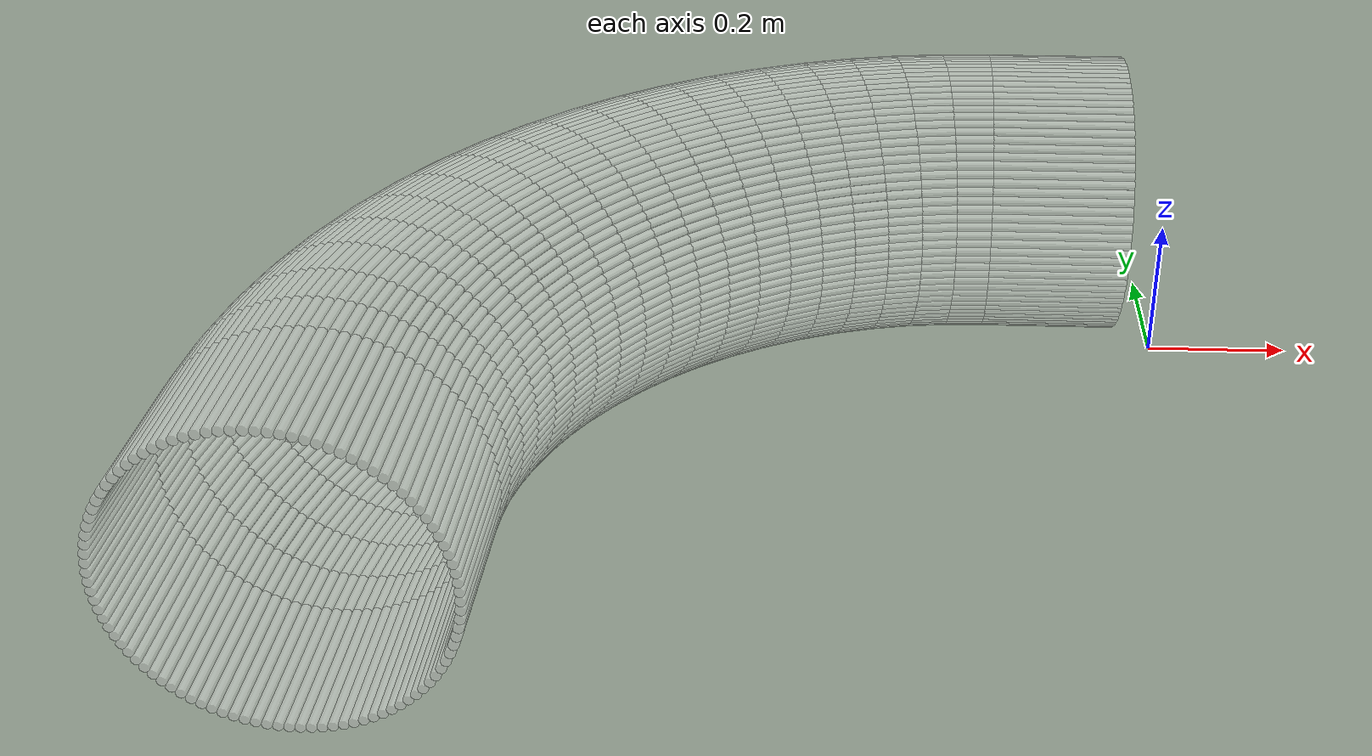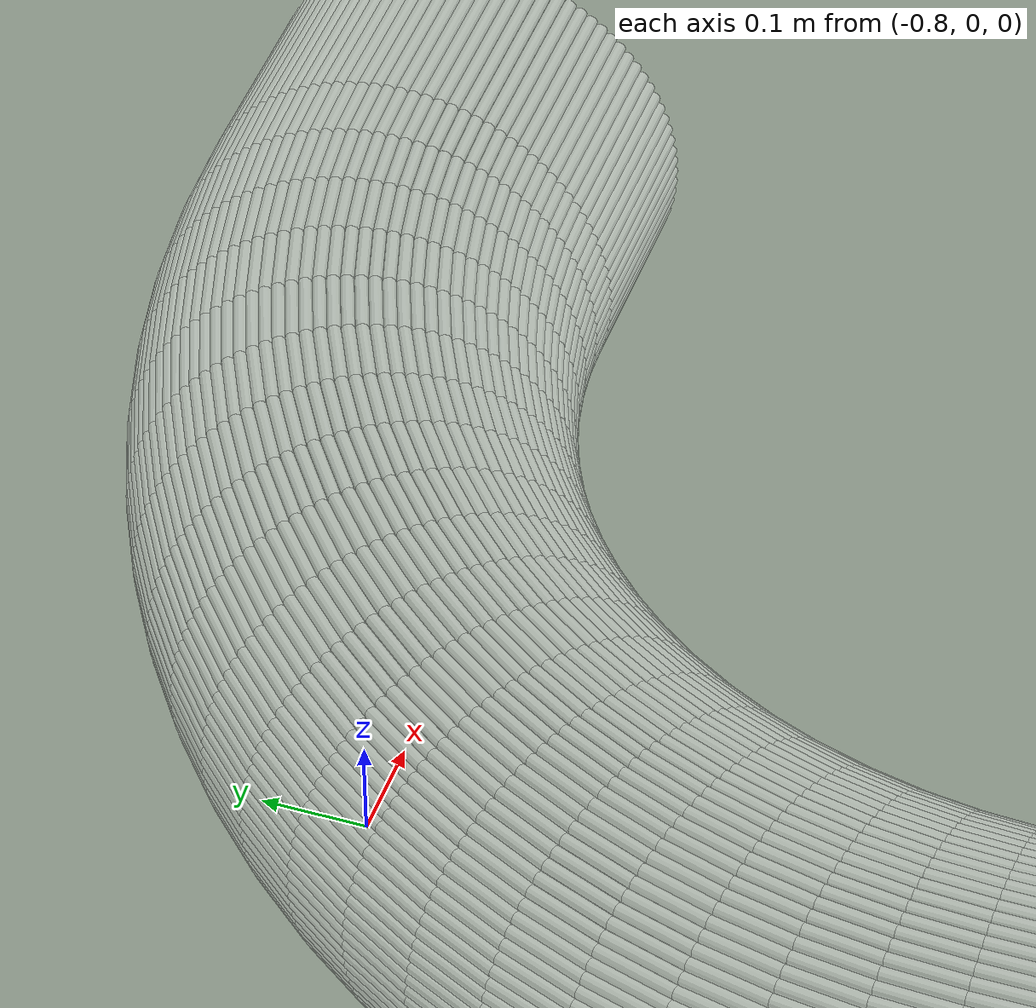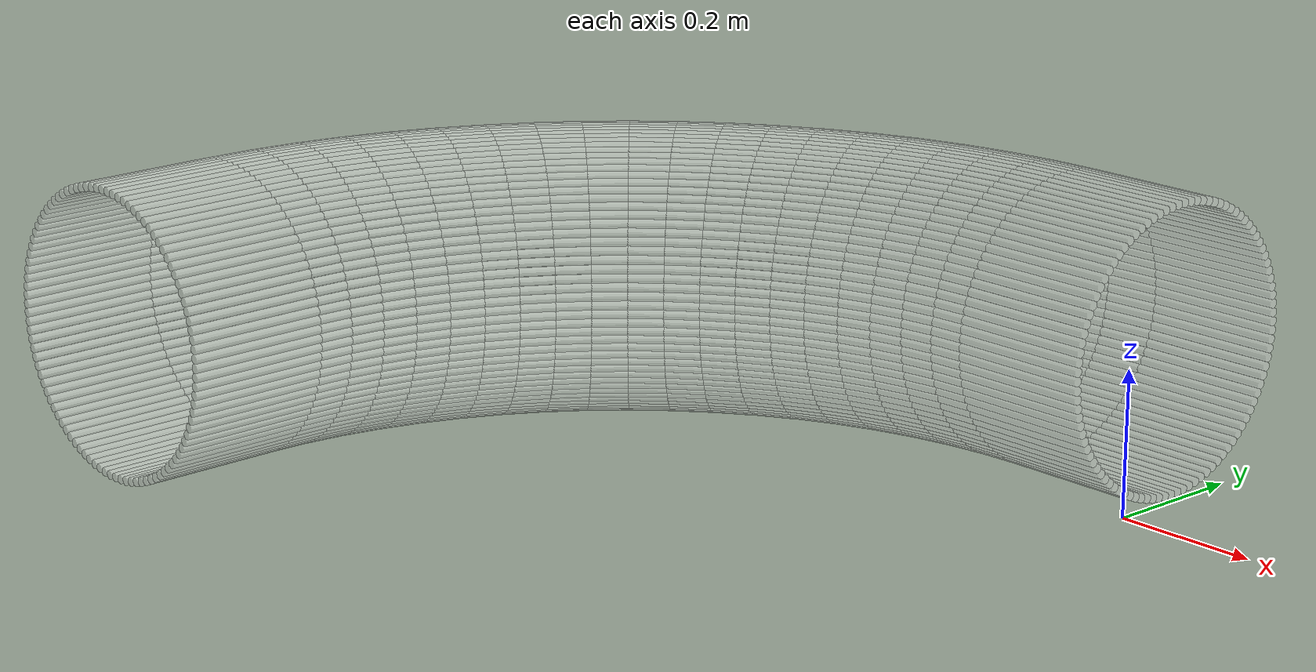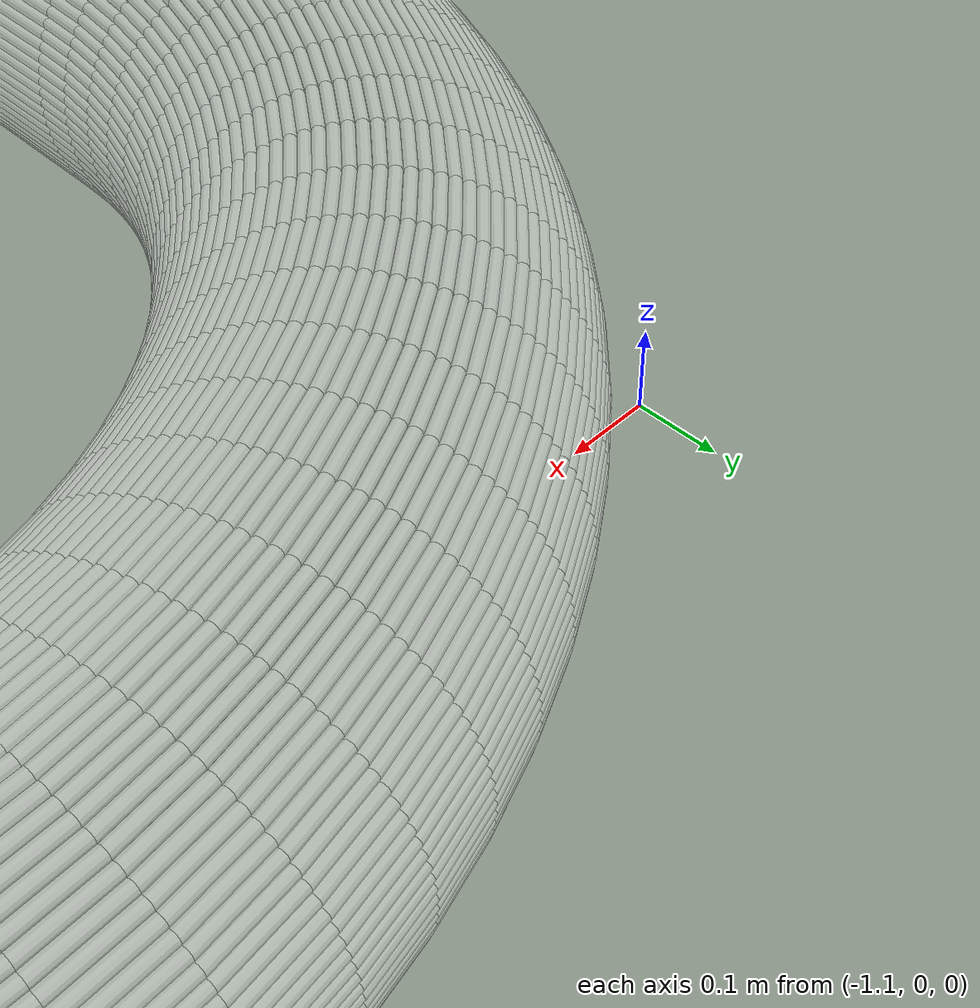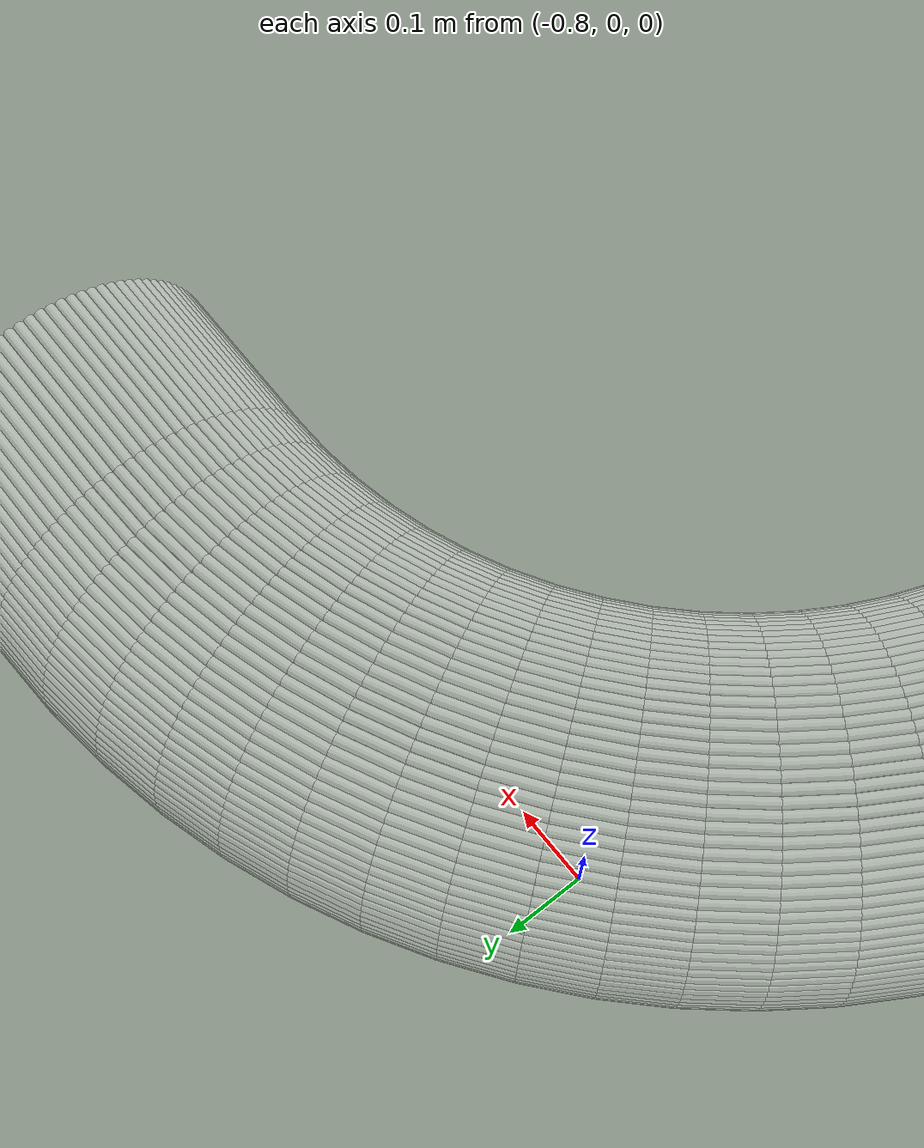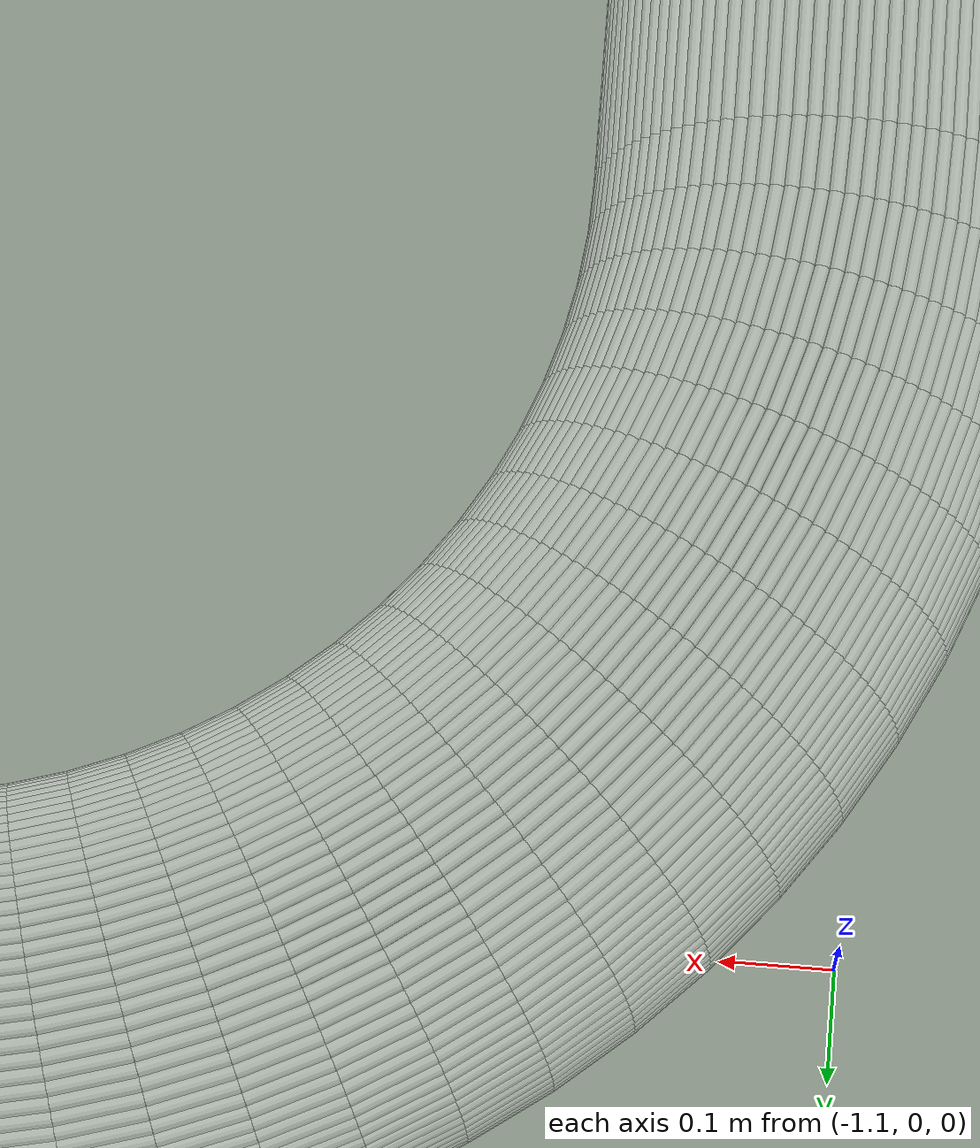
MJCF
<?xml version="1.0" encoding="utf-8"?>
<mujoco>
   <worldbody>
   <body pos="-0.25 -0.64 -0.02" euler="0 0 90">
      <geom euler=" 0 10 0 " fromto="1 -0.2 0.2 1 0 0.2" rgba="1 1 1 0.35" size="0.0062822"
            type="cylinder"/>
      <geom euler=" 0 20 0 " fromto="0.99961 -0.2 0.21256 0.99961 0 0.21256"
            rgba="1 1 1 0.35"
            size="0.0062822"
            type="cylinder"/>
      <geom euler=" 0 30 0 " fromto="0.99842 -0.2 0.22507 0.99842 0 0.22507"
            rgba="1 1 1 0.35"
            size="0.0062822"
            type="cylinder"/>
      <geom euler=" 0 40 0 " fromto="0.99646 -0.2 0.23748 0.99646 0 0.23748"
            rgba="1 1 1 0.35"
            size="0.0062822"
            type="cylinder"/>
      <geom euler=" 0 50 0 " fromto="0.99372 -0.2 0.24974 0.99372 0 0.24974"
            rgba="1 1 1 0.35"
            size="0.0062822"
            type="cylinder"/>
      <geom euler=" 0 60 0 " fromto="0.99021 -0.2 0.2618 0.99021 0 0.2618"
            rgba="1 1 1 0.35"
            size="0.0062822"
            type="cylinder"/>
      <geom euler=" 0 70 0 " fromto="0.98596 -0.2 0.27362 0.98596 0 0.27362"
            rgba="1 1 1 0.35"
            size="0.0062822"
            type="cylinder"/>
      <geom euler=" 0 80 0 " fromto="0.98097 -0.2 0.28516 0.98097 0 0.28516"
            rgba="1 1 1 0.35"
            size="0.0062822"
            type="cylinder"/>
      <geom euler=" 0 90 0 " fromto="0.97526 -0.2 0.29635 0.97526 0 0.29635"
            rgba="1 1 1 0.35"
            size="0.0062822"
            type="cylinder"/>
      <geom euler=" 0 100 0 " fromto="0.96887 -0.2 0.30717 0.96887 0 0.30717"
            rgba="1 1 1 0.35"
            size="0.0062822"
            type="cylinder"/>
      <geom euler=" 0 110 0 " fromto="0.9618 -0.2 0.31756 0.9618 0 0.31756"
            rgba="1 1 1 0.35"
            size="0.0062822"
            type="cylinder"/>
      <geom euler=" 0 120 0 " fromto="0.9541 -0.2 0.32748 0.9541 0 0.32748"
            rgba="1 1 1 0.35"
            size="0.0062822"
            type="cylinder"/>
      <geom euler=" 0 130 0 " fromto="0.94579 -0.2 0.33691 0.94579 0 0.33691"
            rgba="1 1 1 0.35"
            size="0.0062822"
            type="cylinder"/>
      <geom euler=" 0 140 0 " fromto="0.93691 -0.2 0.34579 0.93691 0 0.34579"
            rgba="1 1 1 0.35"
            size="0.0062822"
            type="cylinder"/>
      <geom euler=" 0 150 0 " fromto="0.92748 -0.2 0.3541 0.92748 0 0.3541"
            rgba="1 1 1 0.35"
            size="0.0062822"
            type="cylinder"/>
      <geom euler=" 0 160 0 " fromto="0.91756 -0.2 0.3618 0.91756 0 0.3618"
            rgba="1 1 1 0.35"
            size="0.0062822"
            type="cylinder"/>
      <geom euler=" 0 170 0 " fromto="0.90717 -0.2 0.36887 0.90717 0 0.36887"
            rgba="1 1 1 0.35"
            size="0.0062822"
            type="cylinder"/>
      <geom euler=" 0 180 0 " fromto="0.89635 -0.2 0.37526 0.89635 0 0.37526"
            rgba="1 1 1 0.35"
            size="0.0062822"
            type="cylinder"/>
      <geom euler=" 0 190 0 " fromto="0.88516 -0.2 0.38097 0.88516 0 0.38097"
            rgba="1 1 1 0.35"
            size="0.0062822"
            type="cylinder"/>
      <geom euler=" 0 200 0 " fromto="0.87362 -0.2 0.38596 0.87362 0 0.38596"
            rgba="1 1 1 0.35"
            size="0.0062822"
            type="cylinder"/>
      <geom euler=" 0 210 0 " fromto="0.8618 -0.2 0.39021 0.8618 0 0.39021"
            rgba="1 1 1 0.35"
            size="0.0062822"
            type="cylinder"/>
      <geom euler=" 0 220 0 " fromto="0.84974 -0.2 0.39372 0.84974 0 0.39372"
            rgba="1 1 1 0.35"
            size="0.0062822"
            type="cylinder"/>
      <geom euler=" 0 230 0 " fromto="0.83748 -0.2 0.39646 0.83748 0 0.39646"
            rgba="1 1 1 0.35"
            size="0.0062822"
            type="cylinder"/>
      <geom euler=" 0 240 0 " fromto="0.82507 -0.2 0.39842 0.82507 0 0.39842"
            rgba="1 1 1 0.35"
            size="0.0062822"
            type="cylinder"/>
      <geom euler=" 0 250 0 " fromto="0.81256 -0.2 0.39961 0.81256 0 0.39961"
            rgba="1 1 1 0.35"
            size="0.0062822"
            type="cylinder"/>
      <geom euler=" 0 260 0 " fromto="0.8 -0.2 0.4 0.8 0 0.4" rgba="1 1 1 0.35"
            size="0.0062822"
            type="cylinder"/>
      <geom euler=" 0 270 0 " fromto="0.78744 -0.2 0.39961 0.78744 0 0.39961"
            rgba="1 1 1 0.35"
            size="0.0062822"
            type="cylinder"/>
      <geom euler=" 0 280 0 " fromto="0.77493 -0.2 0.39842 0.77493 0 0.39842"
            rgba="1 1 1 0.35"
            size="0.0062822"
            type="cylinder"/>
      <geom euler=" 0 290 0 " fromto="0.76252 -0.2 0.39646 0.76252 0 0.39646"
            rgba="1 1 1 0.35"
            size="0.0062822"
            type="cylinder"/>
      <geom euler=" 0 300 0 " fromto="0.75026 -0.2 0.39372 0.75026 0 0.39372"
            rgba="1 1 1 0.35"
            size="0.0062822"
            type="cylinder"/>
      <geom euler=" 0 310 0 " fromto="0.7382 -0.2 0.39021 0.7382 0 0.39021"
            rgba="1 1 1 0.35"
            size="0.0062822"
            type="cylinder"/>
      <geom euler=" 0 320 0 " fromto="0.72638 -0.2 0.38596 0.72638 0 0.38596"
            rgba="1 1 1 0.35"
            size="0.0062822"
            type="cylinder"/>
      <geom euler=" 0 330 0 " fromto="0.71484 -0.2 0.38097 0.71484 0 0.38097"
            rgba="1 1 1 0.35"
            size="0.0062822"
            type="cylinder"/>
      <geom euler=" 0 340 0 " fromto="0.70365 -0.2 0.37526 0.70365 0 0.37526"
            rgba="1 1 1 0.35"
            size="0.0062822"
            type="cylinder"/>
      <geom euler=" 0 350 0 " fromto="0.69283 -0.2 0.36887 0.69283 0 0.36887"
            rgba="1 1 1 0.35"
            size="0.0062822"
            type="cylinder"/>
      <geom euler=" 0 360 0 " fromto="0.68244 -0.2 0.3618 0.68244 0 0.3618"
            rgba="1 1 1 0.35"
            size="0.0062822"
            type="cylinder"/>
      <geom euler=" 0 370 0 " fromto="0.67252 -0.2 0.3541 0.67252 0 0.3541"
            rgba="1 1 1 0.35"
            size="0.0062822"
            type="cylinder"/>
      <geom euler=" 0 380 0 " fromto="0.66309 -0.2 0.34579 0.66309 0 0.34579"
            rgba="1 1 1 0.35"
            size="0.0062822"
            type="cylinder"/>
      <geom euler=" 0 390 0 " fromto="0.65421 -0.2 0.33691 0.65421 0 0.33691"
            rgba="1 1 1 0.35"
            size="0.0062822"
            type="cylinder"/>
      <geom euler=" 0 400 0 " fromto="0.6459 -0.2 0.32748 0.6459 0 0.32748"
            rgba="1 1 1 0.35"
            size="0.0062822"
            type="cylinder"/>
      <geom euler=" 0 410 0 " fromto="0.6382 -0.2 0.31756 0.6382 0 0.31756"
            rgba="1 1 1 0.35"
            size="0.0062822"
            type="cylinder"/>
      <geom euler=" 0 420 0 " fromto="0.63113 -0.2 0.30717 0.63113 0 0.30717"
            rgba="1 1 1 0.35"
            size="0.0062822"
            type="cylinder"/>
      <geom euler=" 0 430 0 " fromto="0.62474 -0.2 0.29635 0.62474 0 0.29635"
            rgba="1 1 1 0.35"
            size="0.0062822"
            type="cylinder"/>
      <geom euler=" 0 440 0 " fromto="0.61903 -0.2 0.28516 0.61903 0 0.28516"
            rgba="1 1 1 0.35"
            size="0.0062822"
            type="cylinder"/>
      <geom euler=" 0 450 0 " fromto="0.61404 -0.2 0.27362 0.61404 0 0.27362"
            rgba="1 1 1 0.35"
            size="0.0062822"
            type="cylinder"/>
      <geom euler=" 0 460 0 " fromto="0.60979 -0.2 0.2618 0.60979 0 0.2618"
            rgba="1 1 1 0.35"
            size="0.0062822"
            type="cylinder"/>
      <geom euler=" 0 470 0 " fromto="0.60628 -0.2 0.24974 0.60628 0 0.24974"
            rgba="1 1 1 0.35"
            size="0.0062822"
            type="cylinder"/>
      <geom euler=" 0 480 0 " fromto="0.60354 -0.2 0.23748 0.60354 0 0.23748"
            rgba="1 1 1 0.35"
            size="0.0062822"
            type="cylinder"/>
      <geom euler=" 0 490 0 " fromto="0.60158 -0.2 0.22507 0.60158 0 0.22507"
            rgba="1 1 1 0.35"
            size="0.0062822"
            type="cylinder"/>
      <geom euler=" 0 500 0 " fromto="0.60039 -0.2 0.21256 0.60039 0 0.21256"
            rgba="1 1 1 0.35"
            size="0.0062822"
            type="cylinder"/>
      <geom euler=" 0 510 0 " fromto="0.6 -0.2 0.2 0.6 0 0.2" rgba="1 1 1 0.35"
            size="0.0062822"
            type="cylinder"/>
      <geom euler=" 0 520 0 " fromto="0.60039 -0.2 0.18744 0.60039 0 0.18744"
            rgba="1 1 1 0.35"
            size="0.0062822"
            type="cylinder"/>
      <geom euler=" 0 530 0 " fromto="0.60158 -0.2 0.17493 0.60158 0 0.17493"
            rgba="1 1 1 0.35"
            size="0.0062822"
            type="cylinder"/>
      <geom euler=" 0 540 0 " fromto="0.60354 -0.2 0.16252 0.60354 0 0.16252"
            rgba="1 1 1 0.35"
            size="0.0062822"
            type="cylinder"/>
      <geom euler=" 0 550 0 " fromto="0.60628 -0.2 0.15026 0.60628 0 0.15026"
            rgba="1 1 1 0.35"
            size="0.0062822"
            type="cylinder"/>
      <geom euler=" 0 560 0 " fromto="0.60979 -0.2 0.1382 0.60979 0 0.1382"
            rgba="1 1 1 0.35"
            size="0.0062822"
            type="cylinder"/>
      <geom euler=" 0 570 0 " fromto="0.61404 -0.2 0.12638 0.61404 0 0.12638"
            rgba="1 1 1 0.35"
            size="0.0062822"
            type="cylinder"/>
      <geom euler=" 0 580 0 " fromto="0.61903 -0.2 0.11484 0.61903 0 0.11484"
            rgba="1 1 1 0.35"
            size="0.0062822"
            type="cylinder"/>
      <geom euler=" 0 590 0 " fromto="0.62474 -0.2 0.10365 0.62474 0 0.10365"
            rgba="1 1 1 0.35"
            size="0.0062822"
            type="cylinder"/>
      <geom euler=" 0 600 0 " fromto="0.63113 -0.2 0.092835 0.63113 0 0.092835"
            rgba="1 1 1 0.35"
            size="0.0062822"
            type="cylinder"/>
      <geom euler=" 0 610 0 " fromto="0.6382 -0.2 0.082443 0.6382 0 0.082443"
            rgba="1 1 1 0.35"
            size="0.0062822"
            type="cylinder"/>
      <geom euler=" 0 620 0 " fromto="0.6459 -0.2 0.072515 0.6459 0 0.072515"
            rgba="1 1 1 0.35"
            size="0.0062822"
            type="cylinder"/>
      <geom euler=" 0 630 0 " fromto="0.65421 -0.2 0.063091 0.65421 0 0.063091"
            rgba="1 1 1 0.35"
            size="0.0062822"
            type="cylinder"/>
      <geom euler=" 0 640 0 " fromto="0.66309 -0.2 0.054206 0.66309 0 0.054206"
            rgba="1 1 1 0.35"
            size="0.0062822"
            type="cylinder"/>
      <geom euler=" 0 650 0 " fromto="0.67252 -0.2 0.045897 0.67252 0 0.045897"
            rgba="1 1 1 0.35"
            size="0.0062822"
            type="cylinder"/>
      <geom euler=" 0 660 0 " fromto="0.68244 -0.2 0.038197 0.68244 0 0.038197"
            rgba="1 1 1 0.35"
            size="0.0062822"
            type="cylinder"/>
      <geom euler=" 0 670 0 " fromto="0.69283 -0.2 0.031134 0.69283 0 0.031134"
            rgba="1 1 1 0.35"
            size="0.0062822"
            type="cylinder"/>
      <geom euler=" 0 680 0 " fromto="0.70365 -0.2 0.024739 0.70365 0 0.024739"
            rgba="1 1 1 0.35"
            size="0.0062822"
            type="cylinder"/>
      <geom euler=" 0 690 0 " fromto="0.71484 -0.2 0.019035 0.71484 0 0.019035"
            rgba="1 1 1 0.35"
            size="0.0062822"
            type="cylinder"/>
      <geom euler=" 0 700 0 " fromto="0.72638 -0.2 0.014045 0.72638 0 0.014045"
            rgba="1 1 1 0.35"
            size="0.0062822"
            type="cylinder"/>
      <geom euler=" 0 710 0 " fromto="0.7382 -0.2 0.0097887 0.7382 0 0.0097887"
            rgba="1 1 1 0.35"
            size="0.0062822"
            type="cylinder"/>
      <geom euler=" 0 720 0 " fromto="0.75026 -0.2 0.0062834 0.75026 0 0.0062834"
            rgba="1 1 1 0.35"
            size="0.0062822"
            type="cylinder"/>
      <geom euler=" 0 730 0 " fromto="0.76252 -0.2 0.0035425 0.76252 0 0.0035425"
            rgba="1 1 1 0.35"
            size="0.0062822"
            type="cylinder"/>
      <geom euler=" 0 740 0 " fromto="0.77493 -0.2 0.0015771 0.77493 0 0.0015771"
            rgba="1 1 1 0.35"
            size="0.0062822"
            type="cylinder"/>
      <geom euler=" 0 750 0 " fromto="0.78744 -0.2 0.00039465 0.78744 0 0.00039465"
            rgba="1 1 1 0.35"
            size="0.0062822"
            type="cylinder"/>
      <geom euler=" 0 760 0 " fromto="0.8 -0.2 0 0.8 0 0" rgba="1 1 1 0.35"
            size="0.0062822"
            type="cylinder"/>
      <geom euler=" 0 770 0 " fromto="0.81256 -0.2 0.00039465 0.81256 0 0.00039465"
            rgba="1 1 1 0.35"
            size="0.0062822"
            type="cylinder"/>
      <geom euler=" 0 780 0 " fromto="0.82507 -0.2 0.0015771 0.82507 0 0.0015771"
            rgba="1 1 1 0.35"
            size="0.0062822"
            type="cylinder"/>
      <geom euler=" 0 790 0 " fromto="0.83748 -0.2 0.0035425 0.83748 0 0.0035425"
            rgba="1 1 1 0.35"
            size="0.0062822"
            type="cylinder"/>
      <geom euler=" 0 800 0 " fromto="0.84974 -0.2 0.0062834 0.84974 0 0.0062834"
            rgba="1 1 1 0.35"
            size="0.0062822"
            type="cylinder"/>
      <geom euler=" 0 810 0 " fromto="0.8618 -0.2 0.0097887 0.8618 0 0.0097887"
            rgba="1 1 1 0.35"
            size="0.0062822"
            type="cylinder"/>
      <geom euler=" 0 820 0 " fromto="0.87362 -0.2 0.014045 0.87362 0 0.014045"
            rgba="1 1 1 0.35"
            size="0.0062822"
            type="cylinder"/>
      <geom euler=" 0 830 0 " fromto="0.88516 -0.2 0.019035 0.88516 0 0.019035"
            rgba="1 1 1 0.35"
            size="0.0062822"
            type="cylinder"/>
      <geom euler=" 0 840 0 " fromto="0.89635 -0.2 0.024739 0.89635 0 0.024739"
            rgba="1 1 1 0.35"
            size="0.0062822"
            type="cylinder"/>
      <geom euler=" 0 850 0 " fromto="0.90717 -0.2 0.031134 0.90717 0 0.031134"
            rgba="1 1 1 0.35"
            size="0.0062822"
            type="cylinder"/>
      <geom euler=" 0 860 0 " fromto="0.91756 -0.2 0.038197 0.91756 0 0.038197"
            rgba="1 1 1 0.35"
            size="0.0062822"
            type="cylinder"/>
      <geom euler=" 0 870 0 " fromto="0.92748 -0.2 0.045897 0.92748 0 0.045897"
            rgba="1 1 1 0.35"
            size="0.0062822"
            type="cylinder"/>
      <geom euler=" 0 880 0 " fromto="0.93691 -0.2 0.054206 0.93691 0 0.054206"
            rgba="1 1 1 0.35"
            size="0.0062822"
            type="cylinder"/>
      <geom euler=" 0 890 0 " fromto="0.94579 -0.2 0.063091 0.94579 0 0.063091"
            rgba="1 1 1 0.35"
            size="0.0062822"
            type="cylinder"/>
      <geom euler=" 0 900 0 " fromto="0.9541 -0.2 0.072515 0.9541 0 0.072515"
            rgba="1 1 1 0.35"
            size="0.0062822"
            type="cylinder"/>
      <geom euler=" 0 910 0 " fromto="0.9618 -0.2 0.082443 0.9618 0 0.082443"
            rgba="1 1 1 0.35"
            size="0.0062822"
            type="cylinder"/>
      <geom euler=" 0 920 0 " fromto="0.96887 -0.2 0.092835 0.96887 0 0.092835"
            rgba="1 1 1 0.35"
            size="0.0062822"
            type="cylinder"/>
      <geom euler=" 0 930 0 " fromto="0.97526 -0.2 0.10365 0.97526 0 0.10365"
            rgba="1 1 1 0.35"
            size="0.0062822"
            type="cylinder"/>
      <geom euler=" 0 940 0 " fromto="0.98097 -0.2 0.11484 0.98097 0 0.11484"
            rgba="1 1 1 0.35"
            size="0.0062822"
            type="cylinder"/>
      <geom euler=" 0 950 0 " fromto="0.98596 -0.2 0.12638 0.98596 0 0.12638"
            rgba="1 1 1 0.35"
            size="0.0062822"
            type="cylinder"/>
      <geom euler=" 0 960 0 " fromto="0.99021 -0.2 0.1382 0.99021 0 0.1382"
            rgba="1 1 1 0.35"
            size="0.0062822"
            type="cylinder"/>
      <geom euler=" 0 970 0 " fromto="0.99372 -0.2 0.15026 0.99372 0 0.15026"
            rgba="1 1 1 0.35"
            size="0.0062822"
            type="cylinder"/>
      <geom euler=" 0 980 0 " fromto="0.99646 -0.2 0.16252 0.99646 0 0.16252"
            rgba="1 1 1 0.35"
            size="0.0062822"
            type="cylinder"/>
      <geom euler=" 0 990 0 " fromto="0.99842 -0.2 0.17493 0.99842 0 0.17493"
            rgba="1 1 1 0.35"
            size="0.0062822"
            type="cylinder"/>
      <geom euler=" 0 1000 0 " fromto="0.99961 -0.2 0.18744 0.99961 0 0.18744"
            rgba="1 1 1 0.35"
            size="0.0062822"
            type="cylinder"/>
      <geom euler=" 0 10 0 " fromto="1 0 0.2 0.99658 0.082579 0.2" rgba="1 1 1 0.35"
            size="0.0062822"
            type="cylinder"/>
      <geom euler=" 0 20 0 " fromto="0.99961 0 0.21256 0.99619 0.082547 0.21256"
            rgba="1 1 1 0.35"
            size="0.0062822"
            type="cylinder"/>
      <geom euler=" 0 30 0 " fromto="0.99842 0 0.22507 0.99501 0.082449 0.22507"
            rgba="1 1 1 0.35"
            size="0.0062822"
            type="cylinder"/>
      <geom euler=" 0 40 0 " fromto="0.99646 0 0.23748 0.99305 0.082287 0.23748"
            rgba="1 1 1 0.35"
            size="0.0062822"
            type="cylinder"/>
      <geom euler=" 0 50 0 " fromto="0.99372 0 0.24974 0.99032 0.08206 0.24974"
            rgba="1 1 1 0.35"
            size="0.0062822"
            type="cylinder"/>
      <geom euler=" 0 60 0 " fromto="0.99021 0 0.2618 0.98683 0.081771 0.2618"
            rgba="1 1 1 0.35"
            size="0.0062822"
            type="cylinder"/>
      <geom euler=" 0 70 0 " fromto="0.98596 0 0.27362 0.98259 0.08142 0.27362"
            rgba="1 1 1 0.35"
            size="0.0062822"
            type="cylinder"/>
      <geom euler=" 0 80 0 " fromto="0.98097 0 0.28516 0.97761 0.081007 0.28516"
            rgba="1 1 1 0.35"
            size="0.0062822"
            type="cylinder"/>
      <geom euler=" 0 90 0 " fromto="0.97526 0 0.29635 0.97193 0.080536 0.29635"
            rgba="1 1 1 0.35"
            size="0.0062822"
            type="cylinder"/>
      <geom euler=" 0 100 0 " fromto="0.96887 0 0.30717 0.96556 0.080008 0.30717"
            rgba="1 1 1 0.35"
            size="0.0062822"
            type="cylinder"/>
      <geom euler=" 0 110 0 " fromto="0.9618 0 0.31756 0.95852 0.079425 0.31756"
            rgba="1 1 1 0.35"
            size="0.0062822"
            type="cylinder"/>
      <geom euler=" 0 120 0 " fromto="0.9541 0 0.32748 0.95084 0.078789 0.32748"
            rgba="1 1 1 0.35"
            size="0.0062822"
            type="cylinder"/>
      <geom euler=" 0 130 0 " fromto="0.94579 0 0.33691 0.94256 0.078103 0.33691"
            rgba="1 1 1 0.35"
            size="0.0062822"
            type="cylinder"/>
      <geom euler=" 0 140 0 " fromto="0.93691 0 0.34579 0.93371 0.077369 0.34579"
            rgba="1 1 1 0.35"
            size="0.0062822"
            type="cylinder"/>
      <geom euler=" 0 150 0 " fromto="0.92748 0 0.3541 0.92432 0.076591 0.3541"
            rgba="1 1 1 0.35"
            size="0.0062822"
            type="cylinder"/>
      <geom euler=" 0 160 0 " fromto="0.91756 0 0.3618 0.91442 0.075771 0.3618"
            rgba="1 1 1 0.35"
            size="0.0062822"
            type="cylinder"/>
      <geom euler=" 0 170 0 " fromto="0.90717 0 0.36887 0.90407 0.074913 0.36887"
            rgba="1 1 1 0.35"
            size="0.0062822"
            type="cylinder"/>
      <geom euler=" 0 180 0 " fromto="0.89635 0 0.37526 0.89329 0.07402 0.37526"
            rgba="1 1 1 0.35"
            size="0.0062822"
            type="cylinder"/>
      <geom euler=" 0 190 0 " fromto="0.88516 0 0.38097 0.88213 0.073096 0.38097"
            rgba="1 1 1 0.35"
            size="0.0062822"
            type="cylinder"/>
      <geom euler=" 0 200 0 " fromto="0.87362 0 0.38596 0.87064 0.072143 0.38596"
            rgba="1 1 1 0.35"
            size="0.0062822"
            type="cylinder"/>
      <geom euler=" 0 210 0 " fromto="0.8618 0 0.39021 0.85886 0.071167 0.39021"
            rgba="1 1 1 0.35"
            size="0.0062822"
            type="cylinder"/>
      <geom euler=" 0 220 0 " fromto="0.84974 0 0.39372 0.84684 0.070171 0.39372"
            rgba="1 1 1 0.35"
            size="0.0062822"
            type="cylinder"/>
      <geom euler=" 0 230 0 " fromto="0.83748 0 0.39646 0.83462 0.069158 0.39646"
            rgba="1 1 1 0.35"
            size="0.0062822"
            type="cylinder"/>
      <geom euler=" 0 240 0 " fromto="0.82507 0 0.39842 0.82225 0.068133 0.39842"
            rgba="1 1 1 0.35"
            size="0.0062822"
            type="cylinder"/>
      <geom euler=" 0 250 0 " fromto="0.81256 0 0.39961 0.80978 0.067101 0.39961"
            rgba="1 1 1 0.35"
            size="0.0062822"
            type="cylinder"/>
      <geom euler=" 0 260 0 " fromto="0.8 0 0.4 0.79727 0.066063 0.4" rgba="1 1 1 0.35"
            size="0.0062822"
            type="cylinder"/>
      <geom euler=" 0 270 0 " fromto="0.78744 0 0.39961 0.78475 0.065026 0.39961"
            rgba="1 1 1 0.35"
            size="0.0062822"
            type="cylinder"/>
      <geom euler=" 0 280 0 " fromto="0.77493 0 0.39842 0.77229 0.063993 0.39842"
            rgba="1 1 1 0.35"
            size="0.0062822"
            type="cylinder"/>
      <geom euler=" 0 290 0 " fromto="0.76252 0 0.39646 0.75992 0.062969 0.39646"
            rgba="1 1 1 0.35"
            size="0.0062822"
            type="cylinder"/>
      <geom euler=" 0 300 0 " fromto="0.75026 0 0.39372 0.7477 0.061956 0.39372"
            rgba="1 1 1 0.35"
            size="0.0062822"
            type="cylinder"/>
      <geom euler=" 0 310 0 " fromto="0.7382 0 0.39021 0.73568 0.06096 0.39021"
            rgba="1 1 1 0.35"
            size="0.0062822"
            type="cylinder"/>
      <geom euler=" 0 320 0 " fromto="0.72638 0 0.38596 0.72389 0.059984 0.38596"
            rgba="1 1 1 0.35"
            size="0.0062822"
            type="cylinder"/>
      <geom euler=" 0 330 0 " fromto="0.71484 0 0.38097 0.7124 0.059031 0.38097"
            rgba="1 1 1 0.35"
            size="0.0062822"
            type="cylinder"/>
      <geom euler=" 0 340 0 " fromto="0.70365 0 0.37526 0.70125 0.058107 0.37526"
            rgba="1 1 1 0.35"
            size="0.0062822"
            type="cylinder"/>
      <geom euler=" 0 350 0 " fromto="0.69283 0 0.36887 0.69047 0.057214 0.36887"
            rgba="1 1 1 0.35"
            size="0.0062822"
            type="cylinder"/>
      <geom euler=" 0 360 0 " fromto="0.68244 0 0.3618 0.68011 0.056356 0.3618"
            rgba="1 1 1 0.35"
            size="0.0062822"
            type="cylinder"/>
      <geom euler=" 0 370 0 " fromto="0.67252 0 0.3541 0.67022 0.055536 0.3541"
            rgba="1 1 1 0.35"
            size="0.0062822"
            type="cylinder"/>
      <geom euler=" 0 380 0 " fromto="0.66309 0 0.34579 0.66083 0.054758 0.34579"
            rgba="1 1 1 0.35"
            size="0.0062822"
            type="cylinder"/>
      <geom euler=" 0 390 0 " fromto="0.65421 0 0.33691 0.65197 0.054024 0.33691"
            rgba="1 1 1 0.35"
            size="0.0062822"
            type="cylinder"/>
      <geom euler=" 0 400 0 " fromto="0.6459 0 0.32748 0.64369 0.053338 0.32748"
            rgba="1 1 1 0.35"
            size="0.0062822"
            type="cylinder"/>
      <geom euler=" 0 410 0 " fromto="0.6382 0 0.31756 0.63602 0.052702 0.31756"
            rgba="1 1 1 0.35"
            size="0.0062822"
            type="cylinder"/>
      <geom euler=" 0 420 0 " fromto="0.63113 0 0.30717 0.62898 0.052119 0.30717"
            rgba="1 1 1 0.35"
            size="0.0062822"
            type="cylinder"/>
      <geom euler=" 0 430 0 " fromto="0.62474 0 0.29635 0.6226 0.051591 0.29635"
            rgba="1 1 1 0.35"
            size="0.0062822"
            type="cylinder"/>
      <geom euler=" 0 440 0 " fromto="0.61903 0 0.28516 0.61692 0.051119 0.28516"
            rgba="1 1 1 0.35"
            size="0.0062822"
            type="cylinder"/>
      <geom euler=" 0 450 0 " fromto="0.61404 0 0.27362 0.61195 0.050707 0.27362"
            rgba="1 1 1 0.35"
            size="0.0062822"
            type="cylinder"/>
      <geom euler=" 0 460 0 " fromto="0.60979 0 0.2618 0.60771 0.050356 0.2618"
            rgba="1 1 1 0.35"
            size="0.0062822"
            type="cylinder"/>
      <geom euler=" 0 470 0 " fromto="0.60628 0 0.24974 0.60421 0.050066 0.24974"
            rgba="1 1 1 0.35"
            size="0.0062822"
            type="cylinder"/>
      <geom euler=" 0 480 0 " fromto="0.60354 0 0.23748 0.60148 0.04984 0.23748"
            rgba="1 1 1 0.35"
            size="0.0062822"
            type="cylinder"/>
      <geom euler=" 0 490 0 " fromto="0.60158 0 0.22507 0.59952 0.049678 0.22507"
            rgba="1 1 1 0.35"
            size="0.0062822"
            type="cylinder"/>
      <geom euler=" 0 500 0 " fromto="0.60039 0 0.21256 0.59834 0.04958 0.21256"
            rgba="1 1 1 0.35"
            size="0.0062822"
            type="cylinder"/>
      <geom euler=" 0 510 0 " fromto="0.6 0 0.2 0.59795 0.049548 0.2" rgba="1 1 1 0.35"
            size="0.0062822"
            type="cylinder"/>
      <geom euler=" 0 520 0 " fromto="0.60039 0 0.18744 0.59834 0.04958 0.18744"
            rgba="1 1 1 0.35"
            size="0.0062822"
            type="cylinder"/>
      <geom euler=" 0 530 0 " fromto="0.60158 0 0.17493 0.59952 0.049678 0.17493"
            rgba="1 1 1 0.35"
            size="0.0062822"
            type="cylinder"/>
      <geom euler=" 0 540 0 " fromto="0.60354 0 0.16252 0.60148 0.04984 0.16252"
            rgba="1 1 1 0.35"
            size="0.0062822"
            type="cylinder"/>
      <geom euler=" 0 550 0 " fromto="0.60628 0 0.15026 0.60421 0.050066 0.15026"
            rgba="1 1 1 0.35"
            size="0.0062822"
            type="cylinder"/>
      <geom euler=" 0 560 0 " fromto="0.60979 0 0.1382 0.60771 0.050356 0.1382"
            rgba="1 1 1 0.35"
            size="0.0062822"
            type="cylinder"/>
      <geom euler=" 0 570 0 " fromto="0.61404 0 0.12638 0.61195 0.050707 0.12638"
            rgba="1 1 1 0.35"
            size="0.0062822"
            type="cylinder"/>
      <geom euler=" 0 580 0 " fromto="0.61903 0 0.11484 0.61692 0.051119 0.11484"
            rgba="1 1 1 0.35"
            size="0.0062822"
            type="cylinder"/>
      <geom euler=" 0 590 0 " fromto="0.62474 0 0.10365 0.6226 0.051591 0.10365"
            rgba="1 1 1 0.35"
            size="0.0062822"
            type="cylinder"/>
      <geom euler=" 0 600 0 " fromto="0.63113 0 0.092835 0.62898 0.052119 0.092835"
            rgba="1 1 1 0.35"
            size="0.0062822"
            type="cylinder"/>
      <geom euler=" 0 610 0 " fromto="0.6382 0 0.082443 0.63602 0.052702 0.082443"
            rgba="1 1 1 0.35"
            size="0.0062822"
            type="cylinder"/>
      <geom euler=" 0 620 0 " fromto="0.6459 0 0.072515 0.64369 0.053338 0.072515"
            rgba="1 1 1 0.35"
            size="0.0062822"
            type="cylinder"/>
      <geom euler=" 0 630 0 " fromto="0.65421 0 0.063091 0.65197 0.054024 0.063091"
            rgba="1 1 1 0.35"
            size="0.0062822"
            type="cylinder"/>
      <geom euler=" 0 640 0 " fromto="0.66309 0 0.054206 0.66083 0.054758 0.054206"
            rgba="1 1 1 0.35"
            size="0.0062822"
            type="cylinder"/>
      <geom euler=" 0 650 0 " fromto="0.67252 0 0.045897 0.67022 0.055536 0.045897"
            rgba="1 1 1 0.35"
            size="0.0062822"
            type="cylinder"/>
      <geom euler=" 0 660 0 " fromto="0.68244 0 0.038197 0.68011 0.056356 0.038197"
            rgba="1 1 1 0.35"
            size="0.0062822"
            type="cylinder"/>
      <geom euler=" 0 670 0 " fromto="0.69283 0 0.031134 0.69047 0.057214 0.031134"
            rgba="1 1 1 0.35"
            size="0.0062822"
            type="cylinder"/>
      <geom euler=" 0 680 0 " fromto="0.70365 0 0.024739 0.70125 0.058107 0.024739"
            rgba="1 1 1 0.35"
            size="0.0062822"
            type="cylinder"/>
      <geom euler=" 0 690 0 " fromto="0.71484 0 0.019035 0.7124 0.059031 0.019035"
            rgba="1 1 1 0.35"
            size="0.0062822"
            type="cylinder"/>
      <geom euler=" 0 700 0 " fromto="0.72638 0 0.014045 0.72389 0.059984 0.014045"
            rgba="1 1 1 0.35"
            size="0.0062822"
            type="cylinder"/>
      <geom euler=" 0 710 0 " fromto="0.7382 0 0.0097887 0.73568 0.06096 0.0097887"
            rgba="1 1 1 0.35"
            size="0.0062822"
            type="cylinder"/>
      <geom euler=" 0 720 0 " fromto="0.75026 0 0.0062834 0.7477 0.061956 0.0062834"
            rgba="1 1 1 0.35"
            size="0.0062822"
            type="cylinder"/>
      <geom euler=" 0 730 0 " fromto="0.76252 0 0.0035425 0.75992 0.062969 0.0035425"
            rgba="1 1 1 0.35"
            size="0.0062822"
            type="cylinder"/>
      <geom euler=" 0 740 0 " fromto="0.77493 0 0.0015771 0.77229 0.063993 0.0015771"
            rgba="1 1 1 0.35"
            size="0.0062822"
            type="cylinder"/>
      <geom euler=" 0 750 0 " fromto="0.78744 0 0.00039465 0.78475 0.065026 0.00039465"
            rgba="1 1 1 0.35"
            size="0.0062822"
            type="cylinder"/>
      <geom euler=" 0 760 0 " fromto="0.8 0 0 0.79727 0.066063 0" rgba="1 1 1 0.35"
            size="0.0062822"
            type="cylinder"/>
      <geom euler=" 0 770 0 " fromto="0.81256 0 0.00039465 0.80978 0.067101 0.00039465"
            rgba="1 1 1 0.35"
            size="0.0062822"
            type="cylinder"/>
      <geom euler=" 0 780 0 " fromto="0.82507 0 0.0015771 0.82225 0.068133 0.0015771"
            rgba="1 1 1 0.35"
            size="0.0062822"
            type="cylinder"/>
      <geom euler=" 0 790 0 " fromto="0.83748 0 0.0035425 0.83462 0.069158 0.0035425"
            rgba="1 1 1 0.35"
            size="0.0062822"
            type="cylinder"/>
      <geom euler=" 0 800 0 " fromto="0.84974 0 0.0062834 0.84684 0.070171 0.0062834"
            rgba="1 1 1 0.35"
            size="0.0062822"
            type="cylinder"/>
      <geom euler=" 0 810 0 " fromto="0.8618 0 0.0097887 0.85886 0.071167 0.0097887"
            rgba="1 1 1 0.35"
            size="0.0062822"
            type="cylinder"/>
      <geom euler=" 0 820 0 " fromto="0.87362 0 0.014045 0.87064 0.072143 0.014045"
            rgba="1 1 1 0.35"
            size="0.0062822"
            type="cylinder"/>
      <geom euler=" 0 830 0 " fromto="0.88516 0 0.019035 0.88213 0.073096 0.019035"
            rgba="1 1 1 0.35"
            size="0.0062822"
            type="cylinder"/>
      <geom euler=" 0 840 0 " fromto="0.89635 0 0.024739 0.89329 0.07402 0.024739"
            rgba="1 1 1 0.35"
            size="0.0062822"
            type="cylinder"/>
      <geom euler=" 0 850 0 " fromto="0.90717 0 0.031134 0.90407 0.074913 0.031134"
            rgba="1 1 1 0.35"
            size="0.0062822"
            type="cylinder"/>
      <geom euler=" 0 860 0 " fromto="0.91756 0 0.038197 0.91442 0.075771 0.038197"
            rgba="1 1 1 0.35"
            size="0.0062822"
            type="cylinder"/>
      <geom euler=" 0 870 0 " fromto="0.92748 0 0.045897 0.92432 0.076591 0.045897"
            rgba="1 1 1 0.35"
            size="0.0062822"
            type="cylinder"/>
      <geom euler=" 0 880 0 " fromto="0.93691 0 0.054206 0.93371 0.077369 0.054206"
            rgba="1 1 1 0.35"
            size="0.0062822"
            type="cylinder"/>
      <geom euler=" 0 890 0 " fromto="0.94579 0 0.063091 0.94256 0.078103 0.063091"
            rgba="1 1 1 0.35"
            size="0.0062822"
            type="cylinder"/>
      <geom euler=" 0 900 0 " fromto="0.9541 0 0.072515 0.95084 0.078789 0.072515"
            rgba="1 1 1 0.35"
            size="0.0062822"
            type="cylinder"/>
      <geom euler=" 0 910 0 " fromto="0.9618 0 0.082443 0.95852 0.079425 0.082443"
            rgba="1 1 1 0.35"
            size="0.0062822"
            type="cylinder"/>
      <geom euler=" 0 920 0 " fromto="0.96887 0 0.092835 0.96556 0.080008 0.092835"
            rgba="1 1 1 0.35"
            size="0.0062822"
            type="cylinder"/>
      <geom euler=" 0 930 0 " fromto="0.97526 0 0.10365 0.97193 0.080536 0.10365"
            rgba="1 1 1 0.35"
            size="0.0062822"
            type="cylinder"/>
      <geom euler=" 0 940 0 " fromto="0.98097 0 0.11484 0.97761 0.081007 0.11484"
            rgba="1 1 1 0.35"
            size="0.0062822"
            type="cylinder"/>
      <geom euler=" 0 950 0 " fromto="0.98596 0 0.12638 0.98259 0.08142 0.12638"
            rgba="1 1 1 0.35"
            size="0.0062822"
            type="cylinder"/>
      <geom euler=" 0 960 0 " fromto="0.99021 0 0.1382 0.98683 0.081771 0.1382"
            rgba="1 1 1 0.35"
            size="0.0062822"
            type="cylinder"/>
      <geom euler=" 0 970 0 " fromto="0.99372 0 0.15026 0.99032 0.08206 0.15026"
            rgba="1 1 1 0.35"
            size="0.0062822"
            type="cylinder"/>
      <geom euler=" 0 980 0 " fromto="0.99646 0 0.16252 0.99305 0.082287 0.16252"
            rgba="1 1 1 0.35"
            size="0.0062822"
            type="cylinder"/>
      <geom euler=" 0 990 0 " fromto="0.99842 0 0.17493 0.99501 0.082449 0.17493"
            rgba="1 1 1 0.35"
            size="0.0062822"
            type="cylinder"/>
      <geom euler=" 0 1000 0 " fromto="0.99961 0 0.18744 0.99619 0.082547 0.18744"
            rgba="1 1 1 0.35"
            size="0.0062822"
            type="cylinder"/>
      <geom euler=" 0 10 0 " fromto="0.99658 0.082579 0.2 0.98636 0.16459 0.2"
            rgba="1 1 1 0.35"
            size="0.0062822"
            type="cylinder"/>
      <geom euler=" 0 20 0 " fromto="0.99619 0.082547 0.21256 0.98597 0.16453 0.21256"
            rgba="1 1 1 0.35"
            size="0.0062822"
            type="cylinder"/>
      <geom euler=" 0 30 0 " fromto="0.99501 0.082449 0.22507 0.98481 0.16434 0.22507"
            rgba="1 1 1 0.35"
            size="0.0062822"
            type="cylinder"/>
      <geom euler=" 0 40 0 " fromto="0.99305 0.082287 0.23748 0.98287 0.16401 0.23748"
            rgba="1 1 1 0.35"
            size="0.0062822"
            type="cylinder"/>
      <geom euler=" 0 50 0 " fromto="0.99032 0.08206 0.24974 0.98016 0.16356 0.24974"
            rgba="1 1 1 0.35"
            size="0.0062822"
            type="cylinder"/>
      <geom euler=" 0 60 0 " fromto="0.98683 0.081771 0.2618 0.97671 0.16298 0.2618"
            rgba="1 1 1 0.35"
            size="0.0062822"
            type="cylinder"/>
      <geom euler=" 0 70 0 " fromto="0.98259 0.08142 0.27362 0.97251 0.16228 0.27362"
            rgba="1 1 1 0.35"
            size="0.0062822"
            type="cylinder"/>
      <geom euler=" 0 80 0 " fromto="0.97761 0.081007 0.28516 0.96759 0.16146 0.28516"
            rgba="1 1 1 0.35"
            size="0.0062822"
            type="cylinder"/>
      <geom euler=" 0 90 0 " fromto="0.97193 0.080536 0.29635 0.96196 0.16052 0.29635"
            rgba="1 1 1 0.35"
            size="0.0062822"
            type="cylinder"/>
      <geom euler=" 0 100 0 " fromto="0.96556 0.080008 0.30717 0.95565 0.15947 0.30717"
            rgba="1 1 1 0.35"
            size="0.0062822"
            type="cylinder"/>
      <geom euler=" 0 110 0 " fromto="0.95852 0.079425 0.31756 0.94869 0.15831 0.31756"
            rgba="1 1 1 0.35"
            size="0.0062822"
            type="cylinder"/>
      <geom euler=" 0 120 0 " fromto="0.95084 0.078789 0.32748 0.94109 0.15704 0.32748"
            rgba="1 1 1 0.35"
            size="0.0062822"
            type="cylinder"/>
      <geom euler=" 0 130 0 " fromto="0.94256 0.078103 0.33691 0.93289 0.15567 0.33691"
            rgba="1 1 1 0.35"
            size="0.0062822"
            type="cylinder"/>
      <geom euler=" 0 140 0 " fromto="0.93371 0.077369 0.34579 0.92413 0.15421 0.34579"
            rgba="1 1 1 0.35"
            size="0.0062822"
            type="cylinder"/>
      <geom euler=" 0 150 0 " fromto="0.92432 0.076591 0.3541 0.91484 0.15266 0.3541"
            rgba="1 1 1 0.35"
            size="0.0062822"
            type="cylinder"/>
      <geom euler=" 0 160 0 " fromto="0.91442 0.075771 0.3618 0.90504 0.15102 0.3618"
            rgba="1 1 1 0.35"
            size="0.0062822"
            type="cylinder"/>
      <geom euler=" 0 170 0 " fromto="0.90407 0.074913 0.36887 0.89479 0.14931 0.36887"
            rgba="1 1 1 0.35"
            size="0.0062822"
            type="cylinder"/>
      <geom euler=" 0 180 0 " fromto="0.89329 0.07402 0.37526 0.88413 0.14753 0.37526"
            rgba="1 1 1 0.35"
            size="0.0062822"
            type="cylinder"/>
      <geom euler=" 0 190 0 " fromto="0.88213 0.073096 0.38097 0.87308 0.14569 0.38097"
            rgba="1 1 1 0.35"
            size="0.0062822"
            type="cylinder"/>
      <geom euler=" 0 200 0 " fromto="0.87064 0.072143 0.38596 0.86171 0.14379 0.38596"
            rgba="1 1 1 0.35"
            size="0.0062822"
            type="cylinder"/>
      <geom euler=" 0 210 0 " fromto="0.85886 0.071167 0.39021 0.85005 0.14185 0.39021"
            rgba="1 1 1 0.35"
            size="0.0062822"
            type="cylinder"/>
      <geom euler=" 0 220 0 " fromto="0.84684 0.070171 0.39372 0.83815 0.13986 0.39372"
            rgba="1 1 1 0.35"
            size="0.0062822"
            type="cylinder"/>
      <geom euler=" 0 230 0 " fromto="0.83462 0.069158 0.39646 0.82605 0.13784 0.39646"
            rgba="1 1 1 0.35"
            size="0.0062822"
            type="cylinder"/>
      <geom euler=" 0 240 0 " fromto="0.82225 0.068133 0.39842 0.81381 0.1358 0.39842"
            rgba="1 1 1 0.35"
            size="0.0062822"
            type="cylinder"/>
      <geom euler=" 0 250 0 " fromto="0.80978 0.067101 0.39961 0.80148 0.13374 0.39961"
            rgba="1 1 1 0.35"
            size="0.0062822"
            type="cylinder"/>
      <geom euler=" 0 260 0 " fromto="0.79727 0.066063 0.4 0.78909 0.13168 0.4"
            rgba="1 1 1 0.35"
            size="0.0062822"
            type="cylinder"/>
      <geom euler=" 0 270 0 " fromto="0.78475 0.065026 0.39961 0.7767 0.12961 0.39961"
            rgba="1 1 1 0.35"
            size="0.0062822"
            type="cylinder"/>
      <geom euler=" 0 280 0 " fromto="0.77229 0.063993 0.39842 0.76436 0.12755 0.39842"
            rgba="1 1 1 0.35"
            size="0.0062822"
            type="cylinder"/>
      <geom euler=" 0 290 0 " fromto="0.75992 0.062969 0.39646 0.75212 0.12551 0.39646"
            rgba="1 1 1 0.35"
            size="0.0062822"
            type="cylinder"/>
      <geom euler=" 0 300 0 " fromto="0.7477 0.061956 0.39372 0.74003 0.12349 0.39372"
            rgba="1 1 1 0.35"
            size="0.0062822"
            type="cylinder"/>
      <geom euler=" 0 310 0 " fromto="0.73568 0.06096 0.39021 0.72813 0.1215 0.39021"
            rgba="1 1 1 0.35"
            size="0.0062822"
            type="cylinder"/>
      <geom euler=" 0 320 0 " fromto="0.72389 0.059984 0.38596 0.71647 0.11956 0.38596"
            rgba="1 1 1 0.35"
            size="0.0062822"
            type="cylinder"/>
      <geom euler=" 0 330 0 " fromto="0.7124 0.059031 0.38097 0.70509 0.11766 0.38097"
            rgba="1 1 1 0.35"
            size="0.0062822"
            type="cylinder"/>
      <geom euler=" 0 340 0 " fromto="0.70125 0.058107 0.37526 0.69405 0.11582 0.37526"
            rgba="1 1 1 0.35"
            size="0.0062822"
            type="cylinder"/>
      <geom euler=" 0 350 0 " fromto="0.69047 0.057214 0.36887 0.68339 0.11404 0.36887"
            rgba="1 1 1 0.35"
            size="0.0062822"
            type="cylinder"/>
      <geom euler=" 0 360 0 " fromto="0.68011 0.056356 0.3618 0.67314 0.11233 0.3618"
            rgba="1 1 1 0.35"
            size="0.0062822"
            type="cylinder"/>
      <geom euler=" 0 370 0 " fromto="0.67022 0.055536 0.3541 0.66334 0.11069 0.3541"
            rgba="1 1 1 0.35"
            size="0.0062822"
            type="cylinder"/>
      <geom euler=" 0 380 0 " fromto="0.66083 0.054758 0.34579 0.65405 0.10914 0.34579"
            rgba="1 1 1 0.35"
            size="0.0062822"
            type="cylinder"/>
      <geom euler=" 0 390 0 " fromto="0.65197 0.054024 0.33691 0.64528 0.10768 0.33691"
            rgba="1 1 1 0.35"
            size="0.0062822"
            type="cylinder"/>
      <geom euler=" 0 400 0 " fromto="0.64369 0.053338 0.32748 0.63709 0.10631 0.32748"
            rgba="1 1 1 0.35"
            size="0.0062822"
            type="cylinder"/>
      <geom euler=" 0 410 0 " fromto="0.63602 0.052702 0.31756 0.62949 0.10504 0.31756"
            rgba="1 1 1 0.35"
            size="0.0062822"
            type="cylinder"/>
      <geom euler=" 0 420 0 " fromto="0.62898 0.052119 0.30717 0.62253 0.10388 0.30717"
            rgba="1 1 1 0.35"
            size="0.0062822"
            type="cylinder"/>
      <geom euler=" 0 430 0 " fromto="0.6226 0.051591 0.29635 0.61622 0.10283 0.29635"
            rgba="1 1 1 0.35"
            size="0.0062822"
            type="cylinder"/>
      <geom euler=" 0 440 0 " fromto="0.61692 0.051119 0.28516 0.61059 0.10189 0.28516"
            rgba="1 1 1 0.35"
            size="0.0062822"
            type="cylinder"/>
      <geom euler=" 0 450 0 " fromto="0.61195 0.050707 0.27362 0.60567 0.10107 0.27362"
            rgba="1 1 1 0.35"
            size="0.0062822"
            type="cylinder"/>
      <geom euler=" 0 460 0 " fromto="0.60771 0.050356 0.2618 0.60147 0.10037 0.2618"
            rgba="1 1 1 0.35"
            size="0.0062822"
            type="cylinder"/>
      <geom euler=" 0 470 0 " fromto="0.60421 0.050066 0.24974 0.59801 0.099791 0.24974"
            rgba="1 1 1 0.35"
            size="0.0062822"
            type="cylinder"/>
      <geom euler=" 0 480 0 " fromto="0.60148 0.04984 0.23748 0.59531 0.09934 0.23748"
            rgba="1 1 1 0.35"
            size="0.0062822"
            type="cylinder"/>
      <geom euler=" 0 490 0 " fromto="0.59952 0.049678 0.22507 0.59337 0.099016 0.22507"
            rgba="1 1 1 0.35"
            size="0.0062822"
            type="cylinder"/>
      <geom euler=" 0 500 0 " fromto="0.59834 0.04958 0.21256 0.59221 0.098822 0.21256"
            rgba="1 1 1 0.35"
            size="0.0062822"
            type="cylinder"/>
      <geom euler=" 0 510 0 " fromto="0.59795 0.049548 0.2 0.59182 0.098757 0.2"
            rgba="1 1 1 0.35"
            size="0.0062822"
            type="cylinder"/>
      <geom euler=" 0 520 0 " fromto="0.59834 0.04958 0.18744 0.59221 0.098822 0.18744"
            rgba="1 1 1 0.35"
            size="0.0062822"
            type="cylinder"/>
      <geom euler=" 0 530 0 " fromto="0.59952 0.049678 0.17493 0.59337 0.099016 0.17493"
            rgba="1 1 1 0.35"
            size="0.0062822"
            type="cylinder"/>
      <geom euler=" 0 540 0 " fromto="0.60148 0.04984 0.16252 0.59531 0.09934 0.16252"
            rgba="1 1 1 0.35"
            size="0.0062822"
            type="cylinder"/>
      <geom euler=" 0 550 0 " fromto="0.60421 0.050066 0.15026 0.59801 0.099791 0.15026"
            rgba="1 1 1 0.35"
            size="0.0062822"
            type="cylinder"/>
      <geom euler=" 0 560 0 " fromto="0.60771 0.050356 0.1382 0.60147 0.10037 0.1382"
            rgba="1 1 1 0.35"
            size="0.0062822"
            type="cylinder"/>
      <geom euler=" 0 570 0 " fromto="0.61195 0.050707 0.12638 0.60567 0.10107 0.12638"
            rgba="1 1 1 0.35"
            size="0.0062822"
            type="cylinder"/>
      <geom euler=" 0 580 0 " fromto="0.61692 0.051119 0.11484 0.61059 0.10189 0.11484"
            rgba="1 1 1 0.35"
            size="0.0062822"
            type="cylinder"/>
      <geom euler=" 0 590 0 " fromto="0.6226 0.051591 0.10365 0.61622 0.10283 0.10365"
            rgba="1 1 1 0.35"
            size="0.0062822"
            type="cylinder"/>
      <geom euler=" 0 600 0 " fromto="0.62898 0.052119 0.092835 0.62253 0.10388 0.092835"
            rgba="1 1 1 0.35"
            size="0.0062822"
            type="cylinder"/>
      <geom euler=" 0 610 0 " fromto="0.63602 0.052702 0.082443 0.62949 0.10504 0.082443"
            rgba="1 1 1 0.35"
            size="0.0062822"
            type="cylinder"/>
      <geom euler=" 0 620 0 " fromto="0.64369 0.053338 0.072515 0.63709 0.10631 0.072515"
            rgba="1 1 1 0.35"
            size="0.0062822"
            type="cylinder"/>
      <geom euler=" 0 630 0 " fromto="0.65197 0.054024 0.063091 0.64528 0.10768 0.063091"
            rgba="1 1 1 0.35"
            size="0.0062822"
            type="cylinder"/>
      <geom euler=" 0 640 0 " fromto="0.66083 0.054758 0.054206 0.65405 0.10914 0.054206"
            rgba="1 1 1 0.35"
            size="0.0062822"
            type="cylinder"/>
      <geom euler=" 0 650 0 " fromto="0.67022 0.055536 0.045897 0.66334 0.11069 0.045897"
            rgba="1 1 1 0.35"
            size="0.0062822"
            type="cylinder"/>
      <geom euler=" 0 660 0 " fromto="0.68011 0.056356 0.038197 0.67314 0.11233 0.038197"
            rgba="1 1 1 0.35"
            size="0.0062822"
            type="cylinder"/>
      <geom euler=" 0 670 0 " fromto="0.69047 0.057214 0.031134 0.68339 0.11404 0.031134"
            rgba="1 1 1 0.35"
            size="0.0062822"
            type="cylinder"/>
      <geom euler=" 0 680 0 " fromto="0.70125 0.058107 0.024739 0.69405 0.11582 0.024739"
            rgba="1 1 1 0.35"
            size="0.0062822"
            type="cylinder"/>
      <geom euler=" 0 690 0 " fromto="0.7124 0.059031 0.019035 0.70509 0.11766 0.019035"
            rgba="1 1 1 0.35"
            size="0.0062822"
            type="cylinder"/>
      <geom euler=" 0 700 0 " fromto="0.72389 0.059984 0.014045 0.71647 0.11956 0.014045"
            rgba="1 1 1 0.35"
            size="0.0062822"
            type="cylinder"/>
      <geom euler=" 0 710 0 " fromto="0.73568 0.06096 0.0097887 0.72813 0.1215 0.0097887"
            rgba="1 1 1 0.35"
            size="0.0062822"
            type="cylinder"/>
      <geom euler=" 0 720 0 " fromto="0.7477 0.061956 0.0062834 0.74003 0.12349 0.0062834"
            rgba="1 1 1 0.35"
            size="0.0062822"
            type="cylinder"/>
      <geom euler=" 0 730 0 " fromto="0.75992 0.062969 0.0035425 0.75212 0.12551 0.0035425"
            rgba="1 1 1 0.35"
            size="0.0062822"
            type="cylinder"/>
      <geom euler=" 0 740 0 " fromto="0.77229 0.063993 0.0015771 0.76436 0.12755 0.0015771"
            rgba="1 1 1 0.35"
            size="0.0062822"
            type="cylinder"/>
      <geom euler=" 0 750 0 "
            fromto="0.78475 0.065026 0.00039465 0.7767 0.12961 0.00039465"
            rgba="1 1 1 0.35"
            size="0.0062822"
            type="cylinder"/>
      <geom euler=" 0 760 0 " fromto="0.79727 0.066063 0 0.78909 0.13168 0"
            rgba="1 1 1 0.35"
            size="0.0062822"
            type="cylinder"/>
      <geom euler=" 0 770 0 "
            fromto="0.80978 0.067101 0.00039465 0.80148 0.13374 0.00039465"
            rgba="1 1 1 0.35"
            size="0.0062822"
            type="cylinder"/>
      <geom euler=" 0 780 0 " fromto="0.82225 0.068133 0.0015771 0.81381 0.1358 0.0015771"
            rgba="1 1 1 0.35"
            size="0.0062822"
            type="cylinder"/>
      <geom euler=" 0 790 0 " fromto="0.83462 0.069158 0.0035425 0.82605 0.13784 0.0035425"
            rgba="1 1 1 0.35"
            size="0.0062822"
            type="cylinder"/>
      <geom euler=" 0 800 0 " fromto="0.84684 0.070171 0.0062834 0.83815 0.13986 0.0062834"
            rgba="1 1 1 0.35"
            size="0.0062822"
            type="cylinder"/>
      <geom euler=" 0 810 0 " fromto="0.85886 0.071167 0.0097887 0.85005 0.14185 0.0097887"
            rgba="1 1 1 0.35"
            size="0.0062822"
            type="cylinder"/>
      <geom euler=" 0 820 0 " fromto="0.87064 0.072143 0.014045 0.86171 0.14379 0.014045"
            rgba="1 1 1 0.35"
            size="0.0062822"
            type="cylinder"/>
      <geom euler=" 0 830 0 " fromto="0.88213 0.073096 0.019035 0.87308 0.14569 0.019035"
            rgba="1 1 1 0.35"
            size="0.0062822"
            type="cylinder"/>
      <geom euler=" 0 840 0 " fromto="0.89329 0.07402 0.024739 0.88413 0.14753 0.024739"
            rgba="1 1 1 0.35"
            size="0.0062822"
            type="cylinder"/>
      <geom euler=" 0 850 0 " fromto="0.90407 0.074913 0.031134 0.89479 0.14931 0.031134"
            rgba="1 1 1 0.35"
            size="0.0062822"
            type="cylinder"/>
      <geom euler=" 0 860 0 " fromto="0.91442 0.075771 0.038197 0.90504 0.15102 0.038197"
            rgba="1 1 1 0.35"
            size="0.0062822"
            type="cylinder"/>
      <geom euler=" 0 870 0 " fromto="0.92432 0.076591 0.045897 0.91484 0.15266 0.045897"
            rgba="1 1 1 0.35"
            size="0.0062822"
            type="cylinder"/>
      <geom euler=" 0 880 0 " fromto="0.93371 0.077369 0.054206 0.92413 0.15421 0.054206"
            rgba="1 1 1 0.35"
            size="0.0062822"
            type="cylinder"/>
      <geom euler=" 0 890 0 " fromto="0.94256 0.078103 0.063091 0.93289 0.15567 0.063091"
            rgba="1 1 1 0.35"
            size="0.0062822"
            type="cylinder"/>
      <geom euler=" 0 900 0 " fromto="0.95084 0.078789 0.072515 0.94109 0.15704 0.072515"
            rgba="1 1 1 0.35"
            size="0.0062822"
            type="cylinder"/>
      <geom euler=" 0 910 0 " fromto="0.95852 0.079425 0.082443 0.94869 0.15831 0.082443"
            rgba="1 1 1 0.35"
            size="0.0062822"
            type="cylinder"/>
      <geom euler=" 0 920 0 " fromto="0.96556 0.080008 0.092835 0.95565 0.15947 0.092835"
            rgba="1 1 1 0.35"
            size="0.0062822"
            type="cylinder"/>
      <geom euler=" 0 930 0 " fromto="0.97193 0.080536 0.10365 0.96196 0.16052 0.10365"
            rgba="1 1 1 0.35"
            size="0.0062822"
            type="cylinder"/>
      <geom euler=" 0 940 0 " fromto="0.97761 0.081007 0.11484 0.96759 0.16146 0.11484"
            rgba="1 1 1 0.35"
            size="0.0062822"
            type="cylinder"/>
      <geom euler=" 0 950 0 " fromto="0.98259 0.08142 0.12638 0.97251 0.16228 0.12638"
            rgba="1 1 1 0.35"
            size="0.0062822"
            type="cylinder"/>
      <geom euler=" 0 960 0 " fromto="0.98683 0.081771 0.1382 0.97671 0.16298 0.1382"
            rgba="1 1 1 0.35"
            size="0.0062822"
            type="cylinder"/>
      <geom euler=" 0 970 0 " fromto="0.99032 0.08206 0.15026 0.98016 0.16356 0.15026"
            rgba="1 1 1 0.35"
            size="0.0062822"
            type="cylinder"/>
      <geom euler=" 0 980 0 " fromto="0.99305 0.082287 0.16252 0.98287 0.16401 0.16252"
            rgba="1 1 1 0.35"
            size="0.0062822"
            type="cylinder"/>
      <geom euler=" 0 990 0 " fromto="0.99501 0.082449 0.17493 0.98481 0.16434 0.17493"
            rgba="1 1 1 0.35"
            size="0.0062822"
            type="cylinder"/>
      <geom euler=" 0 1000 0 " fromto="0.99619 0.082547 0.18744 0.98597 0.16453 0.18744"
            rgba="1 1 1 0.35"
            size="0.0062822"
            type="cylinder"/>
      <geom euler=" 0 10 0 " fromto="0.98636 0.16459 0.2 0.9694 0.24549 0.2"
            rgba="1 1 1 0.35"
            size="0.0062822"
            type="cylinder"/>
      <geom euler=" 0 20 0 " fromto="0.98597 0.16453 0.21256 0.96902 0.24539 0.21256"
            rgba="1 1 1 0.35"
            size="0.0062822"
            type="cylinder"/>
      <geom euler=" 0 30 0 " fromto="0.98481 0.16434 0.22507 0.96787 0.2451 0.22507"
            rgba="1 1 1 0.35"
            size="0.0062822"
            type="cylinder"/>
      <geom euler=" 0 40 0 " fromto="0.98287 0.16401 0.23748 0.96597 0.24462 0.23748"
            rgba="1 1 1 0.35"
            size="0.0062822"
            type="cylinder"/>
      <geom euler=" 0 50 0 " fromto="0.98016 0.16356 0.24974 0.96331 0.24394 0.24974"
            rgba="1 1 1 0.35"
            size="0.0062822"
            type="cylinder"/>
      <geom euler=" 0 60 0 " fromto="0.97671 0.16298 0.2618 0.95991 0.24308 0.2618"
            rgba="1 1 1 0.35"
            size="0.0062822"
            type="cylinder"/>
      <geom euler=" 0 70 0 " fromto="0.97251 0.16228 0.27362 0.95579 0.24204 0.27362"
            rgba="1 1 1 0.35"
            size="0.0062822"
            type="cylinder"/>
      <geom euler=" 0 80 0 " fromto="0.96759 0.16146 0.28516 0.95095 0.24081 0.28516"
            rgba="1 1 1 0.35"
            size="0.0062822"
            type="cylinder"/>
      <geom euler=" 0 90 0 " fromto="0.96196 0.16052 0.29635 0.94542 0.23941 0.29635"
            rgba="1 1 1 0.35"
            size="0.0062822"
            type="cylinder"/>
      <geom euler=" 0 100 0 " fromto="0.95565 0.15947 0.30717 0.93922 0.23784 0.30717"
            rgba="1 1 1 0.35"
            size="0.0062822"
            type="cylinder"/>
      <geom euler=" 0 110 0 " fromto="0.94869 0.15831 0.31756 0.93237 0.23611 0.31756"
            rgba="1 1 1 0.35"
            size="0.0062822"
            type="cylinder"/>
      <geom euler=" 0 120 0 " fromto="0.94109 0.15704 0.32748 0.92491 0.23422 0.32748"
            rgba="1 1 1 0.35"
            size="0.0062822"
            type="cylinder"/>
      <geom euler=" 0 130 0 " fromto="0.93289 0.15567 0.33691 0.91685 0.23218 0.33691"
            rgba="1 1 1 0.35"
            size="0.0062822"
            type="cylinder"/>
      <geom euler=" 0 140 0 " fromto="0.92413 0.15421 0.34579 0.90824 0.23 0.34579"
            rgba="1 1 1 0.35"
            size="0.0062822"
            type="cylinder"/>
      <geom euler=" 0 150 0 " fromto="0.91484 0.15266 0.3541 0.8991 0.22768 0.3541"
            rgba="1 1 1 0.35"
            size="0.0062822"
            type="cylinder"/>
      <geom euler=" 0 160 0 " fromto="0.90504 0.15102 0.3618 0.88948 0.22525 0.3618"
            rgba="1 1 1 0.35"
            size="0.0062822"
            type="cylinder"/>
      <geom euler=" 0 170 0 " fromto="0.89479 0.14931 0.36887 0.87941 0.2227 0.36887"
            rgba="1 1 1 0.35"
            size="0.0062822"
            type="cylinder"/>
      <geom euler=" 0 180 0 " fromto="0.88413 0.14753 0.37526 0.86892 0.22004 0.37526"
            rgba="1 1 1 0.35"
            size="0.0062822"
            type="cylinder"/>
      <geom euler=" 0 190 0 " fromto="0.87308 0.14569 0.38097 0.85807 0.21729 0.38097"
            rgba="1 1 1 0.35"
            size="0.0062822"
            type="cylinder"/>
      <geom euler=" 0 200 0 " fromto="0.86171 0.14379 0.38596 0.84689 0.21446 0.38596"
            rgba="1 1 1 0.35"
            size="0.0062822"
            type="cylinder"/>
      <geom euler=" 0 210 0 " fromto="0.85005 0.14185 0.39021 0.83543 0.21156 0.39021"
            rgba="1 1 1 0.35"
            size="0.0062822"
            type="cylinder"/>
      <geom euler=" 0 220 0 " fromto="0.83815 0.13986 0.39372 0.82374 0.2086 0.39372"
            rgba="1 1 1 0.35"
            size="0.0062822"
            type="cylinder"/>
      <geom euler=" 0 230 0 " fromto="0.82605 0.13784 0.39646 0.81185 0.20559 0.39646"
            rgba="1 1 1 0.35"
            size="0.0062822"
            type="cylinder"/>
      <geom euler=" 0 240 0 " fromto="0.81381 0.1358 0.39842 0.79982 0.20254 0.39842"
            rgba="1 1 1 0.35"
            size="0.0062822"
            type="cylinder"/>
      <geom euler=" 0 250 0 " fromto="0.80148 0.13374 0.39961 0.78769 0.19947 0.39961"
            rgba="1 1 1 0.35"
            size="0.0062822"
            type="cylinder"/>
      <geom euler=" 0 260 0 " fromto="0.78909 0.13168 0.4 0.77552 0.19639 0.4"
            rgba="1 1 1 0.35"
            size="0.0062822"
            type="cylinder"/>
      <geom euler=" 0 270 0 " fromto="0.7767 0.12961 0.39961 0.76335 0.19331 0.39961"
            rgba="1 1 1 0.35"
            size="0.0062822"
            type="cylinder"/>
      <geom euler=" 0 280 0 " fromto="0.76436 0.12755 0.39842 0.75122 0.19023 0.39842"
            rgba="1 1 1 0.35"
            size="0.0062822"
            type="cylinder"/>
      <geom euler=" 0 290 0 " fromto="0.75212 0.12551 0.39646 0.73919 0.18719 0.39646"
            rgba="1 1 1 0.35"
            size="0.0062822"
            type="cylinder"/>
      <geom euler=" 0 300 0 " fromto="0.74003 0.12349 0.39372 0.7273 0.18418 0.39372"
            rgba="1 1 1 0.35"
            size="0.0062822"
            type="cylinder"/>
      <geom euler=" 0 310 0 " fromto="0.72813 0.1215 0.39021 0.71561 0.18122 0.39021"
            rgba="1 1 1 0.35"
            size="0.0062822"
            type="cylinder"/>
      <geom euler=" 0 320 0 " fromto="0.71647 0.11956 0.38596 0.70415 0.17831 0.38596"
            rgba="1 1 1 0.35"
            size="0.0062822"
            type="cylinder"/>
      <geom euler=" 0 330 0 " fromto="0.70509 0.11766 0.38097 0.69297 0.17548 0.38097"
            rgba="1 1 1 0.35"
            size="0.0062822"
            type="cylinder"/>
      <geom euler=" 0 340 0 " fromto="0.69405 0.11582 0.37526 0.68212 0.17274 0.37526"
            rgba="1 1 1 0.35"
            size="0.0062822"
            type="cylinder"/>
      <geom euler=" 0 350 0 " fromto="0.68339 0.11404 0.36887 0.67163 0.17008 0.36887"
            rgba="1 1 1 0.35"
            size="0.0062822"
            type="cylinder"/>
      <geom euler=" 0 360 0 " fromto="0.67314 0.11233 0.3618 0.66156 0.16753 0.3618"
            rgba="1 1 1 0.35"
            size="0.0062822"
            type="cylinder"/>
      <geom euler=" 0 370 0 " fromto="0.66334 0.11069 0.3541 0.65194 0.16509 0.3541"
            rgba="1 1 1 0.35"
            size="0.0062822"
            type="cylinder"/>
      <geom euler=" 0 380 0 " fromto="0.65405 0.10914 0.34579 0.6428 0.16278 0.34579"
            rgba="1 1 1 0.35"
            size="0.0062822"
            type="cylinder"/>
      <geom euler=" 0 390 0 " fromto="0.64528 0.10768 0.33691 0.63419 0.1606 0.33691"
            rgba="1 1 1 0.35"
            size="0.0062822"
            type="cylinder"/>
      <geom euler=" 0 400 0 " fromto="0.63709 0.10631 0.32748 0.62613 0.15856 0.32748"
            rgba="1 1 1 0.35"
            size="0.0062822"
            type="cylinder"/>
      <geom euler=" 0 410 0 " fromto="0.62949 0.10504 0.31756 0.61867 0.15667 0.31756"
            rgba="1 1 1 0.35"
            size="0.0062822"
            type="cylinder"/>
      <geom euler=" 0 420 0 " fromto="0.62253 0.10388 0.30717 0.61182 0.15493 0.30717"
            rgba="1 1 1 0.35"
            size="0.0062822"
            type="cylinder"/>
      <geom euler=" 0 430 0 " fromto="0.61622 0.10283 0.29635 0.60562 0.15336 0.29635"
            rgba="1 1 1 0.35"
            size="0.0062822"
            type="cylinder"/>
      <geom euler=" 0 440 0 " fromto="0.61059 0.10189 0.28516 0.60009 0.15196 0.28516"
            rgba="1 1 1 0.35"
            size="0.0062822"
            type="cylinder"/>
      <geom euler=" 0 450 0 " fromto="0.60567 0.10107 0.27362 0.59526 0.15074 0.27362"
            rgba="1 1 1 0.35"
            size="0.0062822"
            type="cylinder"/>
      <geom euler=" 0 460 0 " fromto="0.60147 0.10037 0.2618 0.59113 0.14969 0.2618"
            rgba="1 1 1 0.35"
            size="0.0062822"
            type="cylinder"/>
      <geom euler=" 0 470 0 " fromto="0.59801 0.099791 0.24974 0.58773 0.14883 0.24974"
            rgba="1 1 1 0.35"
            size="0.0062822"
            type="cylinder"/>
      <geom euler=" 0 480 0 " fromto="0.59531 0.09934 0.23748 0.58507 0.14816 0.23748"
            rgba="1 1 1 0.35"
            size="0.0062822"
            type="cylinder"/>
      <geom euler=" 0 490 0 " fromto="0.59337 0.099016 0.22507 0.58317 0.14768 0.22507"
            rgba="1 1 1 0.35"
            size="0.0062822"
            type="cylinder"/>
      <geom euler=" 0 500 0 " fromto="0.59221 0.098822 0.21256 0.58202 0.14739 0.21256"
            rgba="1 1 1 0.35"
            size="0.0062822"
            type="cylinder"/>
      <geom euler=" 0 510 0 " fromto="0.59182 0.098757 0.2 0.58164 0.14729 0.2"
            rgba="1 1 1 0.35"
            size="0.0062822"
            type="cylinder"/>
      <geom euler=" 0 520 0 " fromto="0.59221 0.098822 0.18744 0.58202 0.14739 0.18744"
            rgba="1 1 1 0.35"
            size="0.0062822"
            type="cylinder"/>
      <geom euler=" 0 530 0 " fromto="0.59337 0.099016 0.17493 0.58317 0.14768 0.17493"
            rgba="1 1 1 0.35"
            size="0.0062822"
            type="cylinder"/>
      <geom euler=" 0 540 0 " fromto="0.59531 0.09934 0.16252 0.58507 0.14816 0.16252"
            rgba="1 1 1 0.35"
            size="0.0062822"
            type="cylinder"/>
      <geom euler=" 0 550 0 " fromto="0.59801 0.099791 0.15026 0.58773 0.14883 0.15026"
            rgba="1 1 1 0.35"
            size="0.0062822"
            type="cylinder"/>
      <geom euler=" 0 560 0 " fromto="0.60147 0.10037 0.1382 0.59113 0.14969 0.1382"
            rgba="1 1 1 0.35"
            size="0.0062822"
            type="cylinder"/>
      <geom euler=" 0 570 0 " fromto="0.60567 0.10107 0.12638 0.59526 0.15074 0.12638"
            rgba="1 1 1 0.35"
            size="0.0062822"
            type="cylinder"/>
      <geom euler=" 0 580 0 " fromto="0.61059 0.10189 0.11484 0.60009 0.15196 0.11484"
            rgba="1 1 1 0.35"
            size="0.0062822"
            type="cylinder"/>
      <geom euler=" 0 590 0 " fromto="0.61622 0.10283 0.10365 0.60562 0.15336 0.10365"
            rgba="1 1 1 0.35"
            size="0.0062822"
            type="cylinder"/>
      <geom euler=" 0 600 0 " fromto="0.62253 0.10388 0.092835 0.61182 0.15493 0.092835"
            rgba="1 1 1 0.35"
            size="0.0062822"
            type="cylinder"/>
      <geom euler=" 0 610 0 " fromto="0.62949 0.10504 0.082443 0.61867 0.15667 0.082443"
            rgba="1 1 1 0.35"
            size="0.0062822"
            type="cylinder"/>
      <geom euler=" 0 620 0 " fromto="0.63709 0.10631 0.072515 0.62613 0.15856 0.072515"
            rgba="1 1 1 0.35"
            size="0.0062822"
            type="cylinder"/>
      <geom euler=" 0 630 0 " fromto="0.64528 0.10768 0.063091 0.63419 0.1606 0.063091"
            rgba="1 1 1 0.35"
            size="0.0062822"
            type="cylinder"/>
      <geom euler=" 0 640 0 " fromto="0.65405 0.10914 0.054206 0.6428 0.16278 0.054206"
            rgba="1 1 1 0.35"
            size="0.0062822"
            type="cylinder"/>
      <geom euler=" 0 650 0 " fromto="0.66334 0.11069 0.045897 0.65194 0.16509 0.045897"
            rgba="1 1 1 0.35"
            size="0.0062822"
            type="cylinder"/>
      <geom euler=" 0 660 0 " fromto="0.67314 0.11233 0.038197 0.66156 0.16753 0.038197"
            rgba="1 1 1 0.35"
            size="0.0062822"
            type="cylinder"/>
      <geom euler=" 0 670 0 " fromto="0.68339 0.11404 0.031134 0.67163 0.17008 0.031134"
            rgba="1 1 1 0.35"
            size="0.0062822"
            type="cylinder"/>
      <geom euler=" 0 680 0 " fromto="0.69405 0.11582 0.024739 0.68212 0.17274 0.024739"
            rgba="1 1 1 0.35"
            size="0.0062822"
            type="cylinder"/>
      <geom euler=" 0 690 0 " fromto="0.70509 0.11766 0.019035 0.69297 0.17548 0.019035"
            rgba="1 1 1 0.35"
            size="0.0062822"
            type="cylinder"/>
      <geom euler=" 0 700 0 " fromto="0.71647 0.11956 0.014045 0.70415 0.17831 0.014045"
            rgba="1 1 1 0.35"
            size="0.0062822"
            type="cylinder"/>
      <geom euler=" 0 710 0 " fromto="0.72813 0.1215 0.0097887 0.71561 0.18122 0.0097887"
            rgba="1 1 1 0.35"
            size="0.0062822"
            type="cylinder"/>
      <geom euler=" 0 720 0 " fromto="0.74003 0.12349 0.0062834 0.7273 0.18418 0.0062834"
            rgba="1 1 1 0.35"
            size="0.0062822"
            type="cylinder"/>
      <geom euler=" 0 730 0 " fromto="0.75212 0.12551 0.0035425 0.73919 0.18719 0.0035425"
            rgba="1 1 1 0.35"
            size="0.0062822"
            type="cylinder"/>
      <geom euler=" 0 740 0 " fromto="0.76436 0.12755 0.0015771 0.75122 0.19023 0.0015771"
            rgba="1 1 1 0.35"
            size="0.0062822"
            type="cylinder"/>
      <geom euler=" 0 750 0 " fromto="0.7767 0.12961 0.00039465 0.76335 0.19331 0.00039465"
            rgba="1 1 1 0.35"
            size="0.0062822"
            type="cylinder"/>
      <geom euler=" 0 760 0 " fromto="0.78909 0.13168 0 0.77552 0.19639 0"
            rgba="1 1 1 0.35"
            size="0.0062822"
            type="cylinder"/>
      <geom euler=" 0 770 0 "
            fromto="0.80148 0.13374 0.00039465 0.78769 0.19947 0.00039465"
            rgba="1 1 1 0.35"
            size="0.0062822"
            type="cylinder"/>
      <geom euler=" 0 780 0 " fromto="0.81381 0.1358 0.0015771 0.79982 0.20254 0.0015771"
            rgba="1 1 1 0.35"
            size="0.0062822"
            type="cylinder"/>
      <geom euler=" 0 790 0 " fromto="0.82605 0.13784 0.0035425 0.81185 0.20559 0.0035425"
            rgba="1 1 1 0.35"
            size="0.0062822"
            type="cylinder"/>
      <geom euler=" 0 800 0 " fromto="0.83815 0.13986 0.0062834 0.82374 0.2086 0.0062834"
            rgba="1 1 1 0.35"
            size="0.0062822"
            type="cylinder"/>
      <geom euler=" 0 810 0 " fromto="0.85005 0.14185 0.0097887 0.83543 0.21156 0.0097887"
            rgba="1 1 1 0.35"
            size="0.0062822"
            type="cylinder"/>
      <geom euler=" 0 820 0 " fromto="0.86171 0.14379 0.014045 0.84689 0.21446 0.014045"
            rgba="1 1 1 0.35"
            size="0.0062822"
            type="cylinder"/>
      <geom euler=" 0 830 0 " fromto="0.87308 0.14569 0.019035 0.85807 0.21729 0.019035"
            rgba="1 1 1 0.35"
            size="0.0062822"
            type="cylinder"/>
      <geom euler=" 0 840 0 " fromto="0.88413 0.14753 0.024739 0.86892 0.22004 0.024739"
            rgba="1 1 1 0.35"
            size="0.0062822"
            type="cylinder"/>
      <geom euler=" 0 850 0 " fromto="0.89479 0.14931 0.031134 0.87941 0.2227 0.031134"
            rgba="1 1 1 0.35"
            size="0.0062822"
            type="cylinder"/>
      <geom euler=" 0 860 0 " fromto="0.90504 0.15102 0.038197 0.88948 0.22525 0.038197"
            rgba="1 1 1 0.35"
            size="0.0062822"
            type="cylinder"/>
      <geom euler=" 0 870 0 " fromto="0.91484 0.15266 0.045897 0.8991 0.22768 0.045897"
            rgba="1 1 1 0.35"
            size="0.0062822"
            type="cylinder"/>
      <geom euler=" 0 880 0 " fromto="0.92413 0.15421 0.054206 0.90824 0.23 0.054206"
            rgba="1 1 1 0.35"
            size="0.0062822"
            type="cylinder"/>
      <geom euler=" 0 890 0 " fromto="0.93289 0.15567 0.063091 0.91685 0.23218 0.063091"
            rgba="1 1 1 0.35"
            size="0.0062822"
            type="cylinder"/>
      <geom euler=" 0 900 0 " fromto="0.94109 0.15704 0.072515 0.92491 0.23422 0.072515"
            rgba="1 1 1 0.35"
            size="0.0062822"
            type="cylinder"/>
      <geom euler=" 0 910 0 " fromto="0.94869 0.15831 0.082443 0.93237 0.23611 0.082443"
            rgba="1 1 1 0.35"
            size="0.0062822"
            type="cylinder"/>
      <geom euler=" 0 920 0 " fromto="0.95565 0.15947 0.092835 0.93922 0.23784 0.092835"
            rgba="1 1 1 0.35"
            size="0.0062822"
            type="cylinder"/>
      <geom euler=" 0 930 0 " fromto="0.96196 0.16052 0.10365 0.94542 0.23941 0.10365"
            rgba="1 1 1 0.35"
            size="0.0062822"
            type="cylinder"/>
      <geom euler=" 0 940 0 " fromto="0.96759 0.16146 0.11484 0.95095 0.24081 0.11484"
            rgba="1 1 1 0.35"
            size="0.0062822"
            type="cylinder"/>
      <geom euler=" 0 950 0 " fromto="0.97251 0.16228 0.12638 0.95579 0.24204 0.12638"
            rgba="1 1 1 0.35"
            size="0.0062822"
            type="cylinder"/>
      <geom euler=" 0 960 0 " fromto="0.97671 0.16298 0.1382 0.95991 0.24308 0.1382"
            rgba="1 1 1 0.35"
            size="0.0062822"
            type="cylinder"/>
      <geom euler=" 0 970 0 " fromto="0.98016 0.16356 0.15026 0.96331 0.24394 0.15026"
            rgba="1 1 1 0.35"
            size="0.0062822"
            type="cylinder"/>
      <geom euler=" 0 980 0 " fromto="0.98287 0.16401 0.16252 0.96597 0.24462 0.16252"
            rgba="1 1 1 0.35"
            size="0.0062822"
            type="cylinder"/>
      <geom euler=" 0 990 0 " fromto="0.98481 0.16434 0.17493 0.96787 0.2451 0.17493"
            rgba="1 1 1 0.35"
            size="0.0062822"
            type="cylinder"/>
      <geom euler=" 0 1000 0 " fromto="0.98597 0.16453 0.18744 0.96902 0.24539 0.18744"
            rgba="1 1 1 0.35"
            size="0.0062822"
            type="cylinder"/>
      <geom euler=" 0 10 0 " fromto="0.9694 0.24549 0.2 0.94582 0.3247 0.2"
            rgba="1 1 1 0.35"
            size="0.0062822"
            type="cylinder"/>
      <geom euler=" 0 20 0 " fromto="0.96902 0.24539 0.21256 0.94544 0.32457 0.21256"
            rgba="1 1 1 0.35"
            size="0.0062822"
            type="cylinder"/>
      <geom euler=" 0 30 0 " fromto="0.96787 0.2451 0.22507 0.94433 0.32419 0.22507"
            rgba="1 1 1 0.35"
            size="0.0062822"
            type="cylinder"/>
      <geom euler=" 0 40 0 " fromto="0.96597 0.24462 0.23748 0.94247 0.32355 0.23748"
            rgba="1 1 1 0.35"
            size="0.0062822"
            type="cylinder"/>
      <geom euler=" 0 50 0 " fromto="0.96331 0.24394 0.24974 0.93987 0.32266 0.24974"
            rgba="1 1 1 0.35"
            size="0.0062822"
            type="cylinder"/>
      <geom euler=" 0 60 0 " fromto="0.95991 0.24308 0.2618 0.93656 0.32152 0.2618"
            rgba="1 1 1 0.35"
            size="0.0062822"
            type="cylinder"/>
      <geom euler=" 0 70 0 " fromto="0.95579 0.24204 0.27362 0.93253 0.32014 0.27362"
            rgba="1 1 1 0.35"
            size="0.0062822"
            type="cylinder"/>
      <geom euler=" 0 80 0 " fromto="0.95095 0.24081 0.28516 0.92781 0.31852 0.28516"
            rgba="1 1 1 0.35"
            size="0.0062822"
            type="cylinder"/>
      <geom euler=" 0 90 0 " fromto="0.94542 0.23941 0.29635 0.92242 0.31667 0.29635"
            rgba="1 1 1 0.35"
            size="0.0062822"
            type="cylinder"/>
      <geom euler=" 0 100 0 " fromto="0.93922 0.23784 0.30717 0.91637 0.31459 0.30717"
            rgba="1 1 1 0.35"
            size="0.0062822"
            type="cylinder"/>
      <geom euler=" 0 110 0 " fromto="0.93237 0.23611 0.31756 0.90969 0.3123 0.31756"
            rgba="1 1 1 0.35"
            size="0.0062822"
            type="cylinder"/>
      <geom euler=" 0 120 0 " fromto="0.92491 0.23422 0.32748 0.90241 0.3098 0.32748"
            rgba="1 1 1 0.35"
            size="0.0062822"
            type="cylinder"/>
      <geom euler=" 0 130 0 " fromto="0.91685 0.23218 0.33691 0.89455 0.3071 0.33691"
            rgba="1 1 1 0.35"
            size="0.0062822"
            type="cylinder"/>
      <geom euler=" 0 140 0 " fromto="0.90824 0.23 0.34579 0.88615 0.30421 0.34579"
            rgba="1 1 1 0.35"
            size="0.0062822"
            type="cylinder"/>
      <geom euler=" 0 150 0 " fromto="0.8991 0.22768 0.3541 0.87723 0.30115 0.3541"
            rgba="1 1 1 0.35"
            size="0.0062822"
            type="cylinder"/>
      <geom euler=" 0 160 0 " fromto="0.88948 0.22525 0.3618 0.86784 0.29793 0.3618"
            rgba="1 1 1 0.35"
            size="0.0062822"
            type="cylinder"/>
      <geom euler=" 0 170 0 " fromto="0.87941 0.2227 0.36887 0.85801 0.29456 0.36887"
            rgba="1 1 1 0.35"
            size="0.0062822"
            type="cylinder"/>
      <geom euler=" 0 180 0 " fromto="0.86892 0.22004 0.37526 0.84778 0.29104 0.37526"
            rgba="1 1 1 0.35"
            size="0.0062822"
            type="cylinder"/>
      <geom euler=" 0 190 0 " fromto="0.85807 0.21729 0.38097 0.8372 0.28741 0.38097"
            rgba="1 1 1 0.35"
            size="0.0062822"
            type="cylinder"/>
      <geom euler=" 0 200 0 " fromto="0.84689 0.21446 0.38596 0.82629 0.28367 0.38596"
            rgba="1 1 1 0.35"
            size="0.0062822"
            type="cylinder"/>
      <geom euler=" 0 210 0 " fromto="0.83543 0.21156 0.39021 0.81511 0.27983 0.39021"
            rgba="1 1 1 0.35"
            size="0.0062822"
            type="cylinder"/>
      <geom euler=" 0 220 0 " fromto="0.82374 0.2086 0.39372 0.8037 0.27591 0.39372"
            rgba="1 1 1 0.35"
            size="0.0062822"
            type="cylinder"/>
      <geom euler=" 0 230 0 " fromto="0.81185 0.20559 0.39646 0.7921 0.27193 0.39646"
            rgba="1 1 1 0.35"
            size="0.0062822"
            type="cylinder"/>
      <geom euler=" 0 240 0 " fromto="0.79982 0.20254 0.39842 0.78036 0.2679 0.39842"
            rgba="1 1 1 0.35"
            size="0.0062822"
            type="cylinder"/>
      <geom euler=" 0 250 0 " fromto="0.78769 0.19947 0.39961 0.76853 0.26384 0.39961"
            rgba="1 1 1 0.35"
            size="0.0062822"
            type="cylinder"/>
      <geom euler=" 0 260 0 " fromto="0.77552 0.19639 0.4 0.75665 0.25976 0.4"
            rgba="1 1 1 0.35"
            size="0.0062822"
            type="cylinder"/>
      <geom euler=" 0 270 0 " fromto="0.76335 0.19331 0.39961 0.74478 0.25568 0.39961"
            rgba="1 1 1 0.35"
            size="0.0062822"
            type="cylinder"/>
      <geom euler=" 0 280 0 " fromto="0.75122 0.19023 0.39842 0.73295 0.25162 0.39842"
            rgba="1 1 1 0.35"
            size="0.0062822"
            type="cylinder"/>
      <geom euler=" 0 290 0 " fromto="0.73919 0.18719 0.39646 0.72121 0.24759 0.39646"
            rgba="1 1 1 0.35"
            size="0.0062822"
            type="cylinder"/>
      <geom euler=" 0 300 0 " fromto="0.7273 0.18418 0.39372 0.70961 0.24361 0.39372"
            rgba="1 1 1 0.35"
            size="0.0062822"
            type="cylinder"/>
      <geom euler=" 0 310 0 " fromto="0.71561 0.18122 0.39021 0.6982 0.23969 0.39021"
            rgba="1 1 1 0.35"
            size="0.0062822"
            type="cylinder"/>
      <geom euler=" 0 320 0 " fromto="0.70415 0.17831 0.38596 0.68702 0.23585 0.38596"
            rgba="1 1 1 0.35"
            size="0.0062822"
            type="cylinder"/>
      <geom euler=" 0 330 0 " fromto="0.69297 0.17548 0.38097 0.67611 0.23211 0.38097"
            rgba="1 1 1 0.35"
            size="0.0062822"
            type="cylinder"/>
      <geom euler=" 0 340 0 " fromto="0.68212 0.17274 0.37526 0.66552 0.22847 0.37526"
            rgba="1 1 1 0.35"
            size="0.0062822"
            type="cylinder"/>
      <geom euler=" 0 350 0 " fromto="0.67163 0.17008 0.36887 0.65529 0.22496 0.36887"
            rgba="1 1 1 0.35"
            size="0.0062822"
            type="cylinder"/>
      <geom euler=" 0 360 0 " fromto="0.66156 0.16753 0.3618 0.64547 0.22159 0.3618"
            rgba="1 1 1 0.35"
            size="0.0062822"
            type="cylinder"/>
      <geom euler=" 0 370 0 " fromto="0.65194 0.16509 0.3541 0.63608 0.21837 0.3541"
            rgba="1 1 1 0.35"
            size="0.0062822"
            type="cylinder"/>
      <geom euler=" 0 380 0 " fromto="0.6428 0.16278 0.34579 0.62716 0.21531 0.34579"
            rgba="1 1 1 0.35"
            size="0.0062822"
            type="cylinder"/>
      <geom euler=" 0 390 0 " fromto="0.63419 0.1606 0.33691 0.61876 0.21242 0.33691"
            rgba="1 1 1 0.35"
            size="0.0062822"
            type="cylinder"/>
      <geom euler=" 0 400 0 " fromto="0.62613 0.15856 0.32748 0.6109 0.20972 0.32748"
            rgba="1 1 1 0.35"
            size="0.0062822"
            type="cylinder"/>
      <geom euler=" 0 410 0 " fromto="0.61867 0.15667 0.31756 0.60362 0.20722 0.31756"
            rgba="1 1 1 0.35"
            size="0.0062822"
            type="cylinder"/>
      <geom euler=" 0 420 0 " fromto="0.61182 0.15493 0.30717 0.59694 0.20493 0.30717"
            rgba="1 1 1 0.35"
            size="0.0062822"
            type="cylinder"/>
      <geom euler=" 0 430 0 " fromto="0.60562 0.15336 0.29635 0.59089 0.20285 0.29635"
            rgba="1 1 1 0.35"
            size="0.0062822"
            type="cylinder"/>
      <geom euler=" 0 440 0 " fromto="0.60009 0.15196 0.28516 0.58549 0.201 0.28516"
            rgba="1 1 1 0.35"
            size="0.0062822"
            type="cylinder"/>
      <geom euler=" 0 450 0 " fromto="0.59526 0.15074 0.27362 0.58077 0.19938 0.27362"
            rgba="1 1 1 0.35"
            size="0.0062822"
            type="cylinder"/>
      <geom euler=" 0 460 0 " fromto="0.59113 0.14969 0.2618 0.57675 0.198 0.2618"
            rgba="1 1 1 0.35"
            size="0.0062822"
            type="cylinder"/>
      <geom euler=" 0 470 0 " fromto="0.58773 0.14883 0.24974 0.57343 0.19686 0.24974"
            rgba="1 1 1 0.35"
            size="0.0062822"
            type="cylinder"/>
      <geom euler=" 0 480 0 " fromto="0.58507 0.14816 0.23748 0.57084 0.19597 0.23748"
            rgba="1 1 1 0.35"
            size="0.0062822"
            type="cylinder"/>
      <geom euler=" 0 490 0 " fromto="0.58317 0.14768 0.22507 0.56898 0.19533 0.22507"
            rgba="1 1 1 0.35"
            size="0.0062822"
            type="cylinder"/>
      <geom euler=" 0 500 0 " fromto="0.58202 0.14739 0.21256 0.56786 0.19495 0.21256"
            rgba="1 1 1 0.35"
            size="0.0062822"
            type="cylinder"/>
      <geom euler=" 0 510 0 " fromto="0.58164 0.14729 0.2 0.56749 0.19482 0.2"
            rgba="1 1 1 0.35"
            size="0.0062822"
            type="cylinder"/>
      <geom euler=" 0 520 0 " fromto="0.58202 0.14739 0.18744 0.56786 0.19495 0.18744"
            rgba="1 1 1 0.35"
            size="0.0062822"
            type="cylinder"/>
      <geom euler=" 0 530 0 " fromto="0.58317 0.14768 0.17493 0.56898 0.19533 0.17493"
            rgba="1 1 1 0.35"
            size="0.0062822"
            type="cylinder"/>
      <geom euler=" 0 540 0 " fromto="0.58507 0.14816 0.16252 0.57084 0.19597 0.16252"
            rgba="1 1 1 0.35"
            size="0.0062822"
            type="cylinder"/>
      <geom euler=" 0 550 0 " fromto="0.58773 0.14883 0.15026 0.57343 0.19686 0.15026"
            rgba="1 1 1 0.35"
            size="0.0062822"
            type="cylinder"/>
      <geom euler=" 0 560 0 " fromto="0.59113 0.14969 0.1382 0.57675 0.198 0.1382"
            rgba="1 1 1 0.35"
            size="0.0062822"
            type="cylinder"/>
      <geom euler=" 0 570 0 " fromto="0.59526 0.15074 0.12638 0.58077 0.19938 0.12638"
            rgba="1 1 1 0.35"
            size="0.0062822"
            type="cylinder"/>
      <geom euler=" 0 580 0 " fromto="0.60009 0.15196 0.11484 0.58549 0.201 0.11484"
            rgba="1 1 1 0.35"
            size="0.0062822"
            type="cylinder"/>
      <geom euler=" 0 590 0 " fromto="0.60562 0.15336 0.10365 0.59089 0.20285 0.10365"
            rgba="1 1 1 0.35"
            size="0.0062822"
            type="cylinder"/>
      <geom euler=" 0 600 0 " fromto="0.61182 0.15493 0.092835 0.59694 0.20493 0.092835"
            rgba="1 1 1 0.35"
            size="0.0062822"
            type="cylinder"/>
      <geom euler=" 0 610 0 " fromto="0.61867 0.15667 0.082443 0.60362 0.20722 0.082443"
            rgba="1 1 1 0.35"
            size="0.0062822"
            type="cylinder"/>
      <geom euler=" 0 620 0 " fromto="0.62613 0.15856 0.072515 0.6109 0.20972 0.072515"
            rgba="1 1 1 0.35"
            size="0.0062822"
            type="cylinder"/>
      <geom euler=" 0 630 0 " fromto="0.63419 0.1606 0.063091 0.61876 0.21242 0.063091"
            rgba="1 1 1 0.35"
            size="0.0062822"
            type="cylinder"/>
      <geom euler=" 0 640 0 " fromto="0.6428 0.16278 0.054206 0.62716 0.21531 0.054206"
            rgba="1 1 1 0.35"
            size="0.0062822"
            type="cylinder"/>
      <geom euler=" 0 650 0 " fromto="0.65194 0.16509 0.045897 0.63608 0.21837 0.045897"
            rgba="1 1 1 0.35"
            size="0.0062822"
            type="cylinder"/>
      <geom euler=" 0 660 0 " fromto="0.66156 0.16753 0.038197 0.64547 0.22159 0.038197"
            rgba="1 1 1 0.35"
            size="0.0062822"
            type="cylinder"/>
      <geom euler=" 0 670 0 " fromto="0.67163 0.17008 0.031134 0.65529 0.22496 0.031134"
            rgba="1 1 1 0.35"
            size="0.0062822"
            type="cylinder"/>
      <geom euler=" 0 680 0 " fromto="0.68212 0.17274 0.024739 0.66552 0.22847 0.024739"
            rgba="1 1 1 0.35"
            size="0.0062822"
            type="cylinder"/>
      <geom euler=" 0 690 0 " fromto="0.69297 0.17548 0.019035 0.67611 0.23211 0.019035"
            rgba="1 1 1 0.35"
            size="0.0062822"
            type="cylinder"/>
      <geom euler=" 0 700 0 " fromto="0.70415 0.17831 0.014045 0.68702 0.23585 0.014045"
            rgba="1 1 1 0.35"
            size="0.0062822"
            type="cylinder"/>
      <geom euler=" 0 710 0 " fromto="0.71561 0.18122 0.0097887 0.6982 0.23969 0.0097887"
            rgba="1 1 1 0.35"
            size="0.0062822"
            type="cylinder"/>
      <geom euler=" 0 720 0 " fromto="0.7273 0.18418 0.0062834 0.70961 0.24361 0.0062834"
            rgba="1 1 1 0.35"
            size="0.0062822"
            type="cylinder"/>
      <geom euler=" 0 730 0 " fromto="0.73919 0.18719 0.0035425 0.72121 0.24759 0.0035425"
            rgba="1 1 1 0.35"
            size="0.0062822"
            type="cylinder"/>
      <geom euler=" 0 740 0 " fromto="0.75122 0.19023 0.0015771 0.73295 0.25162 0.0015771"
            rgba="1 1 1 0.35"
            size="0.0062822"
            type="cylinder"/>
      <geom euler=" 0 750 0 "
            fromto="0.76335 0.19331 0.00039465 0.74478 0.25568 0.00039465"
            rgba="1 1 1 0.35"
            size="0.0062822"
            type="cylinder"/>
      <geom euler=" 0 760 0 " fromto="0.77552 0.19639 0 0.75665 0.25976 0"
            rgba="1 1 1 0.35"
            size="0.0062822"
            type="cylinder"/>
      <geom euler=" 0 770 0 "
            fromto="0.78769 0.19947 0.00039465 0.76853 0.26384 0.00039465"
            rgba="1 1 1 0.35"
            size="0.0062822"
            type="cylinder"/>
      <geom euler=" 0 780 0 " fromto="0.79982 0.20254 0.0015771 0.78036 0.2679 0.0015771"
            rgba="1 1 1 0.35"
            size="0.0062822"
            type="cylinder"/>
      <geom euler=" 0 790 0 " fromto="0.81185 0.20559 0.0035425 0.7921 0.27193 0.0035425"
            rgba="1 1 1 0.35"
            size="0.0062822"
            type="cylinder"/>
      <geom euler=" 0 800 0 " fromto="0.82374 0.2086 0.0062834 0.8037 0.27591 0.0062834"
            rgba="1 1 1 0.35"
            size="0.0062822"
            type="cylinder"/>
      <geom euler=" 0 810 0 " fromto="0.83543 0.21156 0.0097887 0.81511 0.27983 0.0097887"
            rgba="1 1 1 0.35"
            size="0.0062822"
            type="cylinder"/>
      <geom euler=" 0 820 0 " fromto="0.84689 0.21446 0.014045 0.82629 0.28367 0.014045"
            rgba="1 1 1 0.35"
            size="0.0062822"
            type="cylinder"/>
      <geom euler=" 0 830 0 " fromto="0.85807 0.21729 0.019035 0.8372 0.28741 0.019035"
            rgba="1 1 1 0.35"
            size="0.0062822"
            type="cylinder"/>
      <geom euler=" 0 840 0 " fromto="0.86892 0.22004 0.024739 0.84778 0.29104 0.024739"
            rgba="1 1 1 0.35"
            size="0.0062822"
            type="cylinder"/>
      <geom euler=" 0 850 0 " fromto="0.87941 0.2227 0.031134 0.85801 0.29456 0.031134"
            rgba="1 1 1 0.35"
            size="0.0062822"
            type="cylinder"/>
      <geom euler=" 0 860 0 " fromto="0.88948 0.22525 0.038197 0.86784 0.29793 0.038197"
            rgba="1 1 1 0.35"
            size="0.0062822"
            type="cylinder"/>
      <geom euler=" 0 870 0 " fromto="0.8991 0.22768 0.045897 0.87723 0.30115 0.045897"
            rgba="1 1 1 0.35"
            size="0.0062822"
            type="cylinder"/>
      <geom euler=" 0 880 0 " fromto="0.90824 0.23 0.054206 0.88615 0.30421 0.054206"
            rgba="1 1 1 0.35"
            size="0.0062822"
            type="cylinder"/>
      <geom euler=" 0 890 0 " fromto="0.91685 0.23218 0.063091 0.89455 0.3071 0.063091"
            rgba="1 1 1 0.35"
            size="0.0062822"
            type="cylinder"/>
      <geom euler=" 0 900 0 " fromto="0.92491 0.23422 0.072515 0.90241 0.3098 0.072515"
            rgba="1 1 1 0.35"
            size="0.0062822"
            type="cylinder"/>
      <geom euler=" 0 910 0 " fromto="0.93237 0.23611 0.082443 0.90969 0.3123 0.082443"
            rgba="1 1 1 0.35"
            size="0.0062822"
            type="cylinder"/>
      <geom euler=" 0 920 0 " fromto="0.93922 0.23784 0.092835 0.91637 0.31459 0.092835"
            rgba="1 1 1 0.35"
            size="0.0062822"
            type="cylinder"/>
      <geom euler=" 0 930 0 " fromto="0.94542 0.23941 0.10365 0.92242 0.31667 0.10365"
            rgba="1 1 1 0.35"
            size="0.0062822"
            type="cylinder"/>
      <geom euler=" 0 940 0 " fromto="0.95095 0.24081 0.11484 0.92781 0.31852 0.11484"
            rgba="1 1 1 0.35"
            size="0.0062822"
            type="cylinder"/>
      <geom euler=" 0 950 0 " fromto="0.95579 0.24204 0.12638 0.93253 0.32014 0.12638"
            rgba="1 1 1 0.35"
            size="0.0062822"
            type="cylinder"/>
      <geom euler=" 0 960 0 " fromto="0.95991 0.24308 0.1382 0.93656 0.32152 0.1382"
            rgba="1 1 1 0.35"
            size="0.0062822"
            type="cylinder"/>
      <geom euler=" 0 970 0 " fromto="0.96331 0.24394 0.15026 0.93987 0.32266 0.15026"
            rgba="1 1 1 0.35"
            size="0.0062822"
            type="cylinder"/>
      <geom euler=" 0 980 0 " fromto="0.96597 0.24462 0.16252 0.94247 0.32355 0.16252"
            rgba="1 1 1 0.35"
            size="0.0062822"
            type="cylinder"/>
      <geom euler=" 0 990 0 " fromto="0.96787 0.2451 0.17493 0.94433 0.32419 0.17493"
            rgba="1 1 1 0.35"
            size="0.0062822"
            type="cylinder"/>
      <geom euler=" 0 1000 0 " fromto="0.96902 0.24539 0.18744 0.94544 0.32457 0.18744"
            rgba="1 1 1 0.35"
            size="0.0062822"
            type="cylinder"/>
      <geom euler=" 0 10 0 " fromto="0.94582 0.3247 0.2 0.91577 0.4017 0.2"
            rgba="1 1 1 0.35"
            size="0.0062822"
            type="cylinder"/>
      <geom euler=" 0 20 0 " fromto="0.94544 0.32457 0.21256 0.91541 0.40154 0.21256"
            rgba="1 1 1 0.35"
            size="0.0062822"
            type="cylinder"/>
      <geom euler=" 0 30 0 " fromto="0.94433 0.32419 0.22507 0.91433 0.40106 0.22507"
            rgba="1 1 1 0.35"
            size="0.0062822"
            type="cylinder"/>
      <geom euler=" 0 40 0 " fromto="0.94247 0.32355 0.23748 0.91253 0.40027 0.23748"
            rgba="1 1 1 0.35"
            size="0.0062822"
            type="cylinder"/>
      <geom euler=" 0 50 0 " fromto="0.93987 0.32266 0.24974 0.91002 0.39917 0.24974"
            rgba="1 1 1 0.35"
            size="0.0062822"
            type="cylinder"/>
      <geom euler=" 0 60 0 " fromto="0.93656 0.32152 0.2618 0.90681 0.39776 0.2618"
            rgba="1 1 1 0.35"
            size="0.0062822"
            type="cylinder"/>
      <geom euler=" 0 70 0 " fromto="0.93253 0.32014 0.27362 0.90291 0.39605 0.27362"
            rgba="1 1 1 0.35"
            size="0.0062822"
            type="cylinder"/>
      <geom euler=" 0 80 0 " fromto="0.92781 0.31852 0.28516 0.89834 0.39405 0.28516"
            rgba="1 1 1 0.35"
            size="0.0062822"
            type="cylinder"/>
      <geom euler=" 0 90 0 " fromto="0.92242 0.31667 0.29635 0.89312 0.39176 0.29635"
            rgba="1 1 1 0.35"
            size="0.0062822"
            type="cylinder"/>
      <geom euler=" 0 100 0 " fromto="0.91637 0.31459 0.30717 0.88726 0.38919 0.30717"
            rgba="1 1 1 0.35"
            size="0.0062822"
            type="cylinder"/>
      <geom euler=" 0 110 0 " fromto="0.90969 0.3123 0.31756 0.88079 0.38635 0.31756"
            rgba="1 1 1 0.35"
            size="0.0062822"
            type="cylinder"/>
      <geom euler=" 0 120 0 " fromto="0.90241 0.3098 0.32748 0.87374 0.38326 0.32748"
            rgba="1 1 1 0.35"
            size="0.0062822"
            type="cylinder"/>
      <geom euler=" 0 130 0 " fromto="0.89455 0.3071 0.33691 0.86613 0.37992 0.33691"
            rgba="1 1 1 0.35"
            size="0.0062822"
            type="cylinder"/>
      <geom euler=" 0 140 0 " fromto="0.88615 0.30421 0.34579 0.858 0.37635 0.34579"
            rgba="1 1 1 0.35"
            size="0.0062822"
            type="cylinder"/>
      <geom euler=" 0 150 0 " fromto="0.87723 0.30115 0.3541 0.84937 0.37257 0.3541"
            rgba="1 1 1 0.35"
            size="0.0062822"
            type="cylinder"/>
      <geom euler=" 0 160 0 " fromto="0.86784 0.29793 0.3618 0.84027 0.36858 0.3618"
            rgba="1 1 1 0.35"
            size="0.0062822"
            type="cylinder"/>
      <geom euler=" 0 170 0 " fromto="0.85801 0.29456 0.36887 0.83076 0.3644 0.36887"
            rgba="1 1 1 0.35"
            size="0.0062822"
            type="cylinder"/>
      <geom euler=" 0 180 0 " fromto="0.84778 0.29104 0.37526 0.82085 0.36006 0.37526"
            rgba="1 1 1 0.35"
            size="0.0062822"
            type="cylinder"/>
      <geom euler=" 0 190 0 " fromto="0.8372 0.28741 0.38097 0.8106 0.35556 0.38097"
            rgba="1 1 1 0.35"
            size="0.0062822"
            type="cylinder"/>
      <geom euler=" 0 200 0 " fromto="0.82629 0.28367 0.38596 0.80004 0.35093 0.38596"
            rgba="1 1 1 0.35"
            size="0.0062822"
            type="cylinder"/>
      <geom euler=" 0 210 0 " fromto="0.81511 0.27983 0.39021 0.78922 0.34618 0.39021"
            rgba="1 1 1 0.35"
            size="0.0062822"
            type="cylinder"/>
      <geom euler=" 0 220 0 " fromto="0.8037 0.27591 0.39372 0.77817 0.34134 0.39372"
            rgba="1 1 1 0.35"
            size="0.0062822"
            type="cylinder"/>
      <geom euler=" 0 230 0 " fromto="0.7921 0.27193 0.39646 0.76694 0.33641 0.39646"
            rgba="1 1 1 0.35"
            size="0.0062822"
            type="cylinder"/>
      <geom euler=" 0 240 0 " fromto="0.78036 0.2679 0.39842 0.75557 0.33143 0.39842"
            rgba="1 1 1 0.35"
            size="0.0062822"
            type="cylinder"/>
      <geom euler=" 0 250 0 " fromto="0.76853 0.26384 0.39961 0.74412 0.3264 0.39961"
            rgba="1 1 1 0.35"
            size="0.0062822"
            type="cylinder"/>
      <geom euler=" 0 260 0 " fromto="0.75665 0.25976 0.4 0.73262 0.32136 0.4"
            rgba="1 1 1 0.35"
            size="0.0062822"
            type="cylinder"/>
      <geom euler=" 0 270 0 " fromto="0.74478 0.25568 0.39961 0.72112 0.31631 0.39961"
            rgba="1 1 1 0.35"
            size="0.0062822"
            type="cylinder"/>
      <geom euler=" 0 280 0 " fromto="0.73295 0.25162 0.39842 0.70966 0.31129 0.39842"
            rgba="1 1 1 0.35"
            size="0.0062822"
            type="cylinder"/>
      <geom euler=" 0 290 0 " fromto="0.72121 0.24759 0.39646 0.6983 0.3063 0.39646"
            rgba="1 1 1 0.35"
            size="0.0062822"
            type="cylinder"/>
      <geom euler=" 0 300 0 " fromto="0.70961 0.24361 0.39372 0.68707 0.30138 0.39372"
            rgba="1 1 1 0.35"
            size="0.0062822"
            type="cylinder"/>
      <geom euler=" 0 310 0 " fromto="0.6982 0.23969 0.39021 0.67602 0.29653 0.39021"
            rgba="1 1 1 0.35"
            size="0.0062822"
            type="cylinder"/>
      <geom euler=" 0 320 0 " fromto="0.68702 0.23585 0.38596 0.66519 0.29178 0.38596"
            rgba="1 1 1 0.35"
            size="0.0062822"
            type="cylinder"/>
      <geom euler=" 0 330 0 " fromto="0.67611 0.23211 0.38097 0.65464 0.28715 0.38097"
            rgba="1 1 1 0.35"
            size="0.0062822"
            type="cylinder"/>
      <geom euler=" 0 340 0 " fromto="0.66552 0.22847 0.37526 0.64438 0.28265 0.37526"
            rgba="1 1 1 0.35"
            size="0.0062822"
            type="cylinder"/>
      <geom euler=" 0 350 0 " fromto="0.65529 0.22496 0.36887 0.63448 0.27831 0.36887"
            rgba="1 1 1 0.35"
            size="0.0062822"
            type="cylinder"/>
      <geom euler=" 0 360 0 " fromto="0.64547 0.22159 0.3618 0.62496 0.27413 0.3618"
            rgba="1 1 1 0.35"
            size="0.0062822"
            type="cylinder"/>
      <geom euler=" 0 370 0 " fromto="0.63608 0.21837 0.3541 0.61587 0.27015 0.3541"
            rgba="1 1 1 0.35"
            size="0.0062822"
            type="cylinder"/>
      <geom euler=" 0 380 0 " fromto="0.62716 0.21531 0.34579 0.60724 0.26636 0.34579"
            rgba="1 1 1 0.35"
            size="0.0062822"
            type="cylinder"/>
      <geom euler=" 0 390 0 " fromto="0.61876 0.21242 0.33691 0.5991 0.26279 0.33691"
            rgba="1 1 1 0.35"
            size="0.0062822"
            type="cylinder"/>
      <geom euler=" 0 400 0 " fromto="0.6109 0.20972 0.32748 0.5915 0.25945 0.32748"
            rgba="1 1 1 0.35"
            size="0.0062822"
            type="cylinder"/>
      <geom euler=" 0 410 0 " fromto="0.60362 0.20722 0.31756 0.58444 0.25636 0.31756"
            rgba="1 1 1 0.35"
            size="0.0062822"
            type="cylinder"/>
      <geom euler=" 0 420 0 " fromto="0.59694 0.20493 0.30717 0.57798 0.25352 0.30717"
            rgba="1 1 1 0.35"
            size="0.0062822"
            type="cylinder"/>
      <geom euler=" 0 430 0 " fromto="0.59089 0.20285 0.29635 0.57212 0.25095 0.29635"
            rgba="1 1 1 0.35"
            size="0.0062822"
            type="cylinder"/>
      <geom euler=" 0 440 0 " fromto="0.58549 0.201 0.28516 0.5669 0.24866 0.28516"
            rgba="1 1 1 0.35"
            size="0.0062822"
            type="cylinder"/>
      <geom euler=" 0 450 0 " fromto="0.58077 0.19938 0.27362 0.56233 0.24666 0.27362"
            rgba="1 1 1 0.35"
            size="0.0062822"
            type="cylinder"/>
      <geom euler=" 0 460 0 " fromto="0.57675 0.198 0.2618 0.55843 0.24495 0.2618"
            rgba="1 1 1 0.35"
            size="0.0062822"
            type="cylinder"/>
      <geom euler=" 0 470 0 " fromto="0.57343 0.19686 0.24974 0.55522 0.24354 0.24974"
            rgba="1 1 1 0.35"
            size="0.0062822"
            type="cylinder"/>
      <geom euler=" 0 480 0 " fromto="0.57084 0.19597 0.23748 0.55271 0.24244 0.23748"
            rgba="1 1 1 0.35"
            size="0.0062822"
            type="cylinder"/>
      <geom euler=" 0 490 0 " fromto="0.56898 0.19533 0.22507 0.55091 0.24165 0.22507"
            rgba="1 1 1 0.35"
            size="0.0062822"
            type="cylinder"/>
      <geom euler=" 0 500 0 " fromto="0.56786 0.19495 0.21256 0.54983 0.24118 0.21256"
            rgba="1 1 1 0.35"
            size="0.0062822"
            type="cylinder"/>
      <geom euler=" 0 510 0 " fromto="0.56749 0.19482 0.2 0.54946 0.24102 0.2"
            rgba="1 1 1 0.35"
            size="0.0062822"
            type="cylinder"/>
      <geom euler=" 0 520 0 " fromto="0.56786 0.19495 0.18744 0.54983 0.24118 0.18744"
            rgba="1 1 1 0.35"
            size="0.0062822"
            type="cylinder"/>
      <geom euler=" 0 530 0 " fromto="0.56898 0.19533 0.17493 0.55091 0.24165 0.17493"
            rgba="1 1 1 0.35"
            size="0.0062822"
            type="cylinder"/>
      <geom euler=" 0 540 0 " fromto="0.57084 0.19597 0.16252 0.55271 0.24244 0.16252"
            rgba="1 1 1 0.35"
            size="0.0062822"
            type="cylinder"/>
      <geom euler=" 0 550 0 " fromto="0.57343 0.19686 0.15026 0.55522 0.24354 0.15026"
            rgba="1 1 1 0.35"
            size="0.0062822"
            type="cylinder"/>
      <geom euler=" 0 560 0 " fromto="0.57675 0.198 0.1382 0.55843 0.24495 0.1382"
            rgba="1 1 1 0.35"
            size="0.0062822"
            type="cylinder"/>
      <geom euler=" 0 570 0 " fromto="0.58077 0.19938 0.12638 0.56233 0.24666 0.12638"
            rgba="1 1 1 0.35"
            size="0.0062822"
            type="cylinder"/>
      <geom euler=" 0 580 0 " fromto="0.58549 0.201 0.11484 0.5669 0.24866 0.11484"
            rgba="1 1 1 0.35"
            size="0.0062822"
            type="cylinder"/>
      <geom euler=" 0 590 0 " fromto="0.59089 0.20285 0.10365 0.57212 0.25095 0.10365"
            rgba="1 1 1 0.35"
            size="0.0062822"
            type="cylinder"/>
      <geom euler=" 0 600 0 " fromto="0.59694 0.20493 0.092835 0.57798 0.25352 0.092835"
            rgba="1 1 1 0.35"
            size="0.0062822"
            type="cylinder"/>
      <geom euler=" 0 610 0 " fromto="0.60362 0.20722 0.082443 0.58444 0.25636 0.082443"
            rgba="1 1 1 0.35"
            size="0.0062822"
            type="cylinder"/>
      <geom euler=" 0 620 0 " fromto="0.6109 0.20972 0.072515 0.5915 0.25945 0.072515"
            rgba="1 1 1 0.35"
            size="0.0062822"
            type="cylinder"/>
      <geom euler=" 0 630 0 " fromto="0.61876 0.21242 0.063091 0.5991 0.26279 0.063091"
            rgba="1 1 1 0.35"
            size="0.0062822"
            type="cylinder"/>
      <geom euler=" 0 640 0 " fromto="0.62716 0.21531 0.054206 0.60724 0.26636 0.054206"
            rgba="1 1 1 0.35"
            size="0.0062822"
            type="cylinder"/>
      <geom euler=" 0 650 0 " fromto="0.63608 0.21837 0.045897 0.61587 0.27015 0.045897"
            rgba="1 1 1 0.35"
            size="0.0062822"
            type="cylinder"/>
      <geom euler=" 0 660 0 " fromto="0.64547 0.22159 0.038197 0.62496 0.27413 0.038197"
            rgba="1 1 1 0.35"
            size="0.0062822"
            type="cylinder"/>
      <geom euler=" 0 670 0 " fromto="0.65529 0.22496 0.031134 0.63448 0.27831 0.031134"
            rgba="1 1 1 0.35"
            size="0.0062822"
            type="cylinder"/>
      <geom euler=" 0 680 0 " fromto="0.66552 0.22847 0.024739 0.64438 0.28265 0.024739"
            rgba="1 1 1 0.35"
            size="0.0062822"
            type="cylinder"/>
      <geom euler=" 0 690 0 " fromto="0.67611 0.23211 0.019035 0.65464 0.28715 0.019035"
            rgba="1 1 1 0.35"
            size="0.0062822"
            type="cylinder"/>
      <geom euler=" 0 700 0 " fromto="0.68702 0.23585 0.014045 0.66519 0.29178 0.014045"
            rgba="1 1 1 0.35"
            size="0.0062822"
            type="cylinder"/>
      <geom euler=" 0 710 0 " fromto="0.6982 0.23969 0.0097887 0.67602 0.29653 0.0097887"
            rgba="1 1 1 0.35"
            size="0.0062822"
            type="cylinder"/>
      <geom euler=" 0 720 0 " fromto="0.70961 0.24361 0.0062834 0.68707 0.30138 0.0062834"
            rgba="1 1 1 0.35"
            size="0.0062822"
            type="cylinder"/>
      <geom euler=" 0 730 0 " fromto="0.72121 0.24759 0.0035425 0.6983 0.3063 0.0035425"
            rgba="1 1 1 0.35"
            size="0.0062822"
            type="cylinder"/>
      <geom euler=" 0 740 0 " fromto="0.73295 0.25162 0.0015771 0.70966 0.31129 0.0015771"
            rgba="1 1 1 0.35"
            size="0.0062822"
            type="cylinder"/>
      <geom euler=" 0 750 0 "
            fromto="0.74478 0.25568 0.00039465 0.72112 0.31631 0.00039465"
            rgba="1 1 1 0.35"
            size="0.0062822"
            type="cylinder"/>
      <geom euler=" 0 760 0 " fromto="0.75665 0.25976 0 0.73262 0.32136 0"
            rgba="1 1 1 0.35"
            size="0.0062822"
            type="cylinder"/>
      <geom euler=" 0 770 0 " fromto="0.76853 0.26384 0.00039465 0.74412 0.3264 0.00039465"
            rgba="1 1 1 0.35"
            size="0.0062822"
            type="cylinder"/>
      <geom euler=" 0 780 0 " fromto="0.78036 0.2679 0.0015771 0.75557 0.33143 0.0015771"
            rgba="1 1 1 0.35"
            size="0.0062822"
            type="cylinder"/>
      <geom euler=" 0 790 0 " fromto="0.7921 0.27193 0.0035425 0.76694 0.33641 0.0035425"
            rgba="1 1 1 0.35"
            size="0.0062822"
            type="cylinder"/>
      <geom euler=" 0 800 0 " fromto="0.8037 0.27591 0.0062834 0.77817 0.34134 0.0062834"
            rgba="1 1 1 0.35"
            size="0.0062822"
            type="cylinder"/>
      <geom euler=" 0 810 0 " fromto="0.81511 0.27983 0.0097887 0.78922 0.34618 0.0097887"
            rgba="1 1 1 0.35"
            size="0.0062822"
            type="cylinder"/>
      <geom euler=" 0 820 0 " fromto="0.82629 0.28367 0.014045 0.80004 0.35093 0.014045"
            rgba="1 1 1 0.35"
            size="0.0062822"
            type="cylinder"/>
      <geom euler=" 0 830 0 " fromto="0.8372 0.28741 0.019035 0.8106 0.35556 0.019035"
            rgba="1 1 1 0.35"
            size="0.0062822"
            type="cylinder"/>
      <geom euler=" 0 840 0 " fromto="0.84778 0.29104 0.024739 0.82085 0.36006 0.024739"
            rgba="1 1 1 0.35"
            size="0.0062822"
            type="cylinder"/>
      <geom euler=" 0 850 0 " fromto="0.85801 0.29456 0.031134 0.83076 0.3644 0.031134"
            rgba="1 1 1 0.35"
            size="0.0062822"
            type="cylinder"/>
      <geom euler=" 0 860 0 " fromto="0.86784 0.29793 0.038197 0.84027 0.36858 0.038197"
            rgba="1 1 1 0.35"
            size="0.0062822"
            type="cylinder"/>
      <geom euler=" 0 870 0 " fromto="0.87723 0.30115 0.045897 0.84937 0.37257 0.045897"
            rgba="1 1 1 0.35"
            size="0.0062822"
            type="cylinder"/>
      <geom euler=" 0 880 0 " fromto="0.88615 0.30421 0.054206 0.858 0.37635 0.054206"
            rgba="1 1 1 0.35"
            size="0.0062822"
            type="cylinder"/>
      <geom euler=" 0 890 0 " fromto="0.89455 0.3071 0.063091 0.86613 0.37992 0.063091"
            rgba="1 1 1 0.35"
            size="0.0062822"
            type="cylinder"/>
      <geom euler=" 0 900 0 " fromto="0.90241 0.3098 0.072515 0.87374 0.38326 0.072515"
            rgba="1 1 1 0.35"
            size="0.0062822"
            type="cylinder"/>
      <geom euler=" 0 910 0 " fromto="0.90969 0.3123 0.082443 0.88079 0.38635 0.082443"
            rgba="1 1 1 0.35"
            size="0.0062822"
            type="cylinder"/>
      <geom euler=" 0 920 0 " fromto="0.91637 0.31459 0.092835 0.88726 0.38919 0.092835"
            rgba="1 1 1 0.35"
            size="0.0062822"
            type="cylinder"/>
      <geom euler=" 0 930 0 " fromto="0.92242 0.31667 0.10365 0.89312 0.39176 0.10365"
            rgba="1 1 1 0.35"
            size="0.0062822"
            type="cylinder"/>
      <geom euler=" 0 940 0 " fromto="0.92781 0.31852 0.11484 0.89834 0.39405 0.11484"
            rgba="1 1 1 0.35"
            size="0.0062822"
            type="cylinder"/>
      <geom euler=" 0 950 0 " fromto="0.93253 0.32014 0.12638 0.90291 0.39605 0.12638"
            rgba="1 1 1 0.35"
            size="0.0062822"
            type="cylinder"/>
      <geom euler=" 0 960 0 " fromto="0.93656 0.32152 0.1382 0.90681 0.39776 0.1382"
            rgba="1 1 1 0.35"
            size="0.0062822"
            type="cylinder"/>
      <geom euler=" 0 970 0 " fromto="0.93987 0.32266 0.15026 0.91002 0.39917 0.15026"
            rgba="1 1 1 0.35"
            size="0.0062822"
            type="cylinder"/>
      <geom euler=" 0 980 0 " fromto="0.94247 0.32355 0.16252 0.91253 0.40027 0.16252"
            rgba="1 1 1 0.35"
            size="0.0062822"
            type="cylinder"/>
      <geom euler=" 0 990 0 " fromto="0.94433 0.32419 0.17493 0.91433 0.40106 0.17493"
            rgba="1 1 1 0.35"
            size="0.0062822"
            type="cylinder"/>
      <geom euler=" 0 1000 0 " fromto="0.94544 0.32457 0.18744 0.91541 0.40154 0.18744"
            rgba="1 1 1 0.35"
            size="0.0062822"
            type="cylinder"/>
      <geom euler=" 0 10 0 " fromto="0.91577 0.4017 0.2 0.87947 0.47595 0.2"
            rgba="1 1 1 0.35"
            size="0.0062822"
            type="cylinder"/>
      <geom euler=" 0 20 0 " fromto="0.91541 0.40154 0.21256 0.87913 0.47576 0.21256"
            rgba="1 1 1 0.35"
            size="0.0062822"
            type="cylinder"/>
      <geom euler=" 0 30 0 " fromto="0.91433 0.40106 0.22507 0.87809 0.4752 0.22507"
            rgba="1 1 1 0.35"
            size="0.0062822"
            type="cylinder"/>
      <geom euler=" 0 40 0 " fromto="0.91253 0.40027 0.23748 0.87636 0.47426 0.23748"
            rgba="1 1 1 0.35"
            size="0.0062822"
            type="cylinder"/>
      <geom euler=" 0 50 0 " fromto="0.91002 0.39917 0.24974 0.87395 0.47296 0.24974"
            rgba="1 1 1 0.35"
            size="0.0062822"
            type="cylinder"/>
      <geom euler=" 0 60 0 " fromto="0.90681 0.39776 0.2618 0.87086 0.47129 0.2618"
            rgba="1 1 1 0.35"
            size="0.0062822"
            type="cylinder"/>
      <geom euler=" 0 70 0 " fromto="0.90291 0.39605 0.27362 0.86712 0.46926 0.27362"
            rgba="1 1 1 0.35"
            size="0.0062822"
            type="cylinder"/>
      <geom euler=" 0 80 0 " fromto="0.89834 0.39405 0.28516 0.86273 0.46689 0.28516"
            rgba="1 1 1 0.35"
            size="0.0062822"
            type="cylinder"/>
      <geom euler=" 0 90 0 " fromto="0.89312 0.39176 0.29635 0.85772 0.46417 0.29635"
            rgba="1 1 1 0.35"
            size="0.0062822"
            type="cylinder"/>
      <geom euler=" 0 100 0 " fromto="0.88726 0.38919 0.30717 0.85209 0.46113 0.30717"
            rgba="1 1 1 0.35"
            size="0.0062822"
            type="cylinder"/>
      <geom euler=" 0 110 0 " fromto="0.88079 0.38635 0.31756 0.84588 0.45777 0.31756"
            rgba="1 1 1 0.35"
            size="0.0062822"
            type="cylinder"/>
      <geom euler=" 0 120 0 " fromto="0.87374 0.38326 0.32748 0.83911 0.4541 0.32748"
            rgba="1 1 1 0.35"
            size="0.0062822"
            type="cylinder"/>
      <geom euler=" 0 130 0 " fromto="0.86613 0.37992 0.33691 0.8318 0.45015 0.33691"
            rgba="1 1 1 0.35"
            size="0.0062822"
            type="cylinder"/>
      <geom euler=" 0 140 0 " fromto="0.858 0.37635 0.34579 0.82399 0.44592 0.34579"
            rgba="1 1 1 0.35"
            size="0.0062822"
            type="cylinder"/>
      <geom euler=" 0 150 0 " fromto="0.84937 0.37257 0.3541 0.8157 0.44143 0.3541"
            rgba="1 1 1 0.35"
            size="0.0062822"
            type="cylinder"/>
      <geom euler=" 0 160 0 " fromto="0.84027 0.36858 0.3618 0.80697 0.43671 0.3618"
            rgba="1 1 1 0.35"
            size="0.0062822"
            type="cylinder"/>
      <geom euler=" 0 170 0 " fromto="0.83076 0.3644 0.36887 0.79783 0.43176 0.36887"
            rgba="1 1 1 0.35"
            size="0.0062822"
            type="cylinder"/>
      <geom euler=" 0 180 0 " fromto="0.82085 0.36006 0.37526 0.78832 0.42662 0.37526"
            rgba="1 1 1 0.35"
            size="0.0062822"
            type="cylinder"/>
      <geom euler=" 0 190 0 " fromto="0.8106 0.35556 0.38097 0.77847 0.42129 0.38097"
            rgba="1 1 1 0.35"
            size="0.0062822"
            type="cylinder"/>
      <geom euler=" 0 200 0 " fromto="0.80004 0.35093 0.38596 0.76833 0.4158 0.38596"
            rgba="1 1 1 0.35"
            size="0.0062822"
            type="cylinder"/>
      <geom euler=" 0 210 0 " fromto="0.78922 0.34618 0.39021 0.75793 0.41017 0.39021"
            rgba="1 1 1 0.35"
            size="0.0062822"
            type="cylinder"/>
      <geom euler=" 0 220 0 " fromto="0.77817 0.34134 0.39372 0.74732 0.40443 0.39372"
            rgba="1 1 1 0.35"
            size="0.0062822"
            type="cylinder"/>
      <geom euler=" 0 230 0 " fromto="0.76694 0.33641 0.39646 0.73654 0.39859 0.39646"
            rgba="1 1 1 0.35"
            size="0.0062822"
            type="cylinder"/>
      <geom euler=" 0 240 0 " fromto="0.75557 0.33143 0.39842 0.72562 0.39269 0.39842"
            rgba="1 1 1 0.35"
            size="0.0062822"
            type="cylinder"/>
      <geom euler=" 0 250 0 " fromto="0.74412 0.3264 0.39961 0.71462 0.38673 0.39961"
            rgba="1 1 1 0.35"
            size="0.0062822"
            type="cylinder"/>
      <geom euler=" 0 260 0 " fromto="0.73262 0.32136 0.4 0.70358 0.38076 0.4"
            rgba="1 1 1 0.35"
            size="0.0062822"
            type="cylinder"/>
      <geom euler=" 0 270 0 " fromto="0.72112 0.31631 0.39961 0.69253 0.37478 0.39961"
            rgba="1 1 1 0.35"
            size="0.0062822"
            type="cylinder"/>
      <geom euler=" 0 280 0 " fromto="0.70966 0.31129 0.39842 0.68153 0.36883 0.39842"
            rgba="1 1 1 0.35"
            size="0.0062822"
            type="cylinder"/>
      <geom euler=" 0 290 0 " fromto="0.6983 0.3063 0.39646 0.67062 0.36292 0.39646"
            rgba="1 1 1 0.35"
            size="0.0062822"
            type="cylinder"/>
      <geom euler=" 0 300 0 " fromto="0.68707 0.30138 0.39372 0.65984 0.35709 0.39372"
            rgba="1 1 1 0.35"
            size="0.0062822"
            type="cylinder"/>
      <geom euler=" 0 310 0 " fromto="0.67602 0.29653 0.39021 0.64922 0.35134 0.39021"
            rgba="1 1 1 0.35"
            size="0.0062822"
            type="cylinder"/>
      <geom euler=" 0 320 0 " fromto="0.66519 0.29178 0.38596 0.63883 0.34572 0.38596"
            rgba="1 1 1 0.35"
            size="0.0062822"
            type="cylinder"/>
      <geom euler=" 0 330 0 " fromto="0.65464 0.28715 0.38097 0.62869 0.34023 0.38097"
            rgba="1 1 1 0.35"
            size="0.0062822"
            type="cylinder"/>
      <geom euler=" 0 340 0 " fromto="0.64438 0.28265 0.37526 0.61884 0.3349 0.37526"
            rgba="1 1 1 0.35"
            size="0.0062822"
            type="cylinder"/>
      <geom euler=" 0 350 0 " fromto="0.63448 0.27831 0.36887 0.60933 0.32975 0.36887"
            rgba="1 1 1 0.35"
            size="0.0062822"
            type="cylinder"/>
      <geom euler=" 0 360 0 " fromto="0.62496 0.27413 0.3618 0.60019 0.32481 0.3618"
            rgba="1 1 1 0.35"
            size="0.0062822"
            type="cylinder"/>
      <geom euler=" 0 370 0 " fromto="0.61587 0.27015 0.3541 0.59146 0.32008 0.3541"
            rgba="1 1 1 0.35"
            size="0.0062822"
            type="cylinder"/>
      <geom euler=" 0 380 0 " fromto="0.60724 0.26636 0.34579 0.58317 0.3156 0.34579"
            rgba="1 1 1 0.35"
            size="0.0062822"
            type="cylinder"/>
      <geom euler=" 0 390 0 " fromto="0.5991 0.26279 0.33691 0.57536 0.31137 0.33691"
            rgba="1 1 1 0.35"
            size="0.0062822"
            type="cylinder"/>
      <geom euler=" 0 400 0 " fromto="0.5915 0.25945 0.32748 0.56805 0.30741 0.32748"
            rgba="1 1 1 0.35"
            size="0.0062822"
            type="cylinder"/>
      <geom euler=" 0 410 0 " fromto="0.58444 0.25636 0.31756 0.56128 0.30375 0.31756"
            rgba="1 1 1 0.35"
            size="0.0062822"
            type="cylinder"/>
      <geom euler=" 0 420 0 " fromto="0.57798 0.25352 0.30717 0.55507 0.30039 0.30717"
            rgba="1 1 1 0.35"
            size="0.0062822"
            type="cylinder"/>
      <geom euler=" 0 430 0 " fromto="0.57212 0.25095 0.29635 0.54944 0.29734 0.29635"
            rgba="1 1 1 0.35"
            size="0.0062822"
            type="cylinder"/>
      <geom euler=" 0 440 0 " fromto="0.5669 0.24866 0.28516 0.54442 0.29463 0.28516"
            rgba="1 1 1 0.35"
            size="0.0062822"
            type="cylinder"/>
      <geom euler=" 0 450 0 " fromto="0.56233 0.24666 0.27362 0.54004 0.29225 0.27362"
            rgba="1 1 1 0.35"
            size="0.0062822"
            type="cylinder"/>
      <geom euler=" 0 460 0 " fromto="0.55843 0.24495 0.2618 0.53629 0.29023 0.2618"
            rgba="1 1 1 0.35"
            size="0.0062822"
            type="cylinder"/>
      <geom euler=" 0 470 0 " fromto="0.55522 0.24354 0.24974 0.53321 0.28856 0.24974"
            rgba="1 1 1 0.35"
            size="0.0062822"
            type="cylinder"/>
      <geom euler=" 0 480 0 " fromto="0.55271 0.24244 0.23748 0.5308 0.28725 0.23748"
            rgba="1 1 1 0.35"
            size="0.0062822"
            type="cylinder"/>
      <geom euler=" 0 490 0 " fromto="0.55091 0.24165 0.22507 0.52907 0.28632 0.22507"
            rgba="1 1 1 0.35"
            size="0.0062822"
            type="cylinder"/>
      <geom euler=" 0 500 0 " fromto="0.54983 0.24118 0.21256 0.52803 0.28576 0.21256"
            rgba="1 1 1 0.35"
            size="0.0062822"
            type="cylinder"/>
      <geom euler=" 0 510 0 " fromto="0.54946 0.24102 0.2 0.52768 0.28557 0.2"
            rgba="1 1 1 0.35"
            size="0.0062822"
            type="cylinder"/>
      <geom euler=" 0 520 0 " fromto="0.54983 0.24118 0.18744 0.52803 0.28576 0.18744"
            rgba="1 1 1 0.35"
            size="0.0062822"
            type="cylinder"/>
      <geom euler=" 0 530 0 " fromto="0.55091 0.24165 0.17493 0.52907 0.28632 0.17493"
            rgba="1 1 1 0.35"
            size="0.0062822"
            type="cylinder"/>
      <geom euler=" 0 540 0 " fromto="0.55271 0.24244 0.16252 0.5308 0.28725 0.16252"
            rgba="1 1 1 0.35"
            size="0.0062822"
            type="cylinder"/>
      <geom euler=" 0 550 0 " fromto="0.55522 0.24354 0.15026 0.53321 0.28856 0.15026"
            rgba="1 1 1 0.35"
            size="0.0062822"
            type="cylinder"/>
      <geom euler=" 0 560 0 " fromto="0.55843 0.24495 0.1382 0.53629 0.29023 0.1382"
            rgba="1 1 1 0.35"
            size="0.0062822"
            type="cylinder"/>
      <geom euler=" 0 570 0 " fromto="0.56233 0.24666 0.12638 0.54004 0.29225 0.12638"
            rgba="1 1 1 0.35"
            size="0.0062822"
            type="cylinder"/>
      <geom euler=" 0 580 0 " fromto="0.5669 0.24866 0.11484 0.54442 0.29463 0.11484"
            rgba="1 1 1 0.35"
            size="0.0062822"
            type="cylinder"/>
      <geom euler=" 0 590 0 " fromto="0.57212 0.25095 0.10365 0.54944 0.29734 0.10365"
            rgba="1 1 1 0.35"
            size="0.0062822"
            type="cylinder"/>
      <geom euler=" 0 600 0 " fromto="0.57798 0.25352 0.092835 0.55507 0.30039 0.092835"
            rgba="1 1 1 0.35"
            size="0.0062822"
            type="cylinder"/>
      <geom euler=" 0 610 0 " fromto="0.58444 0.25636 0.082443 0.56128 0.30375 0.082443"
            rgba="1 1 1 0.35"
            size="0.0062822"
            type="cylinder"/>
      <geom euler=" 0 620 0 " fromto="0.5915 0.25945 0.072515 0.56805 0.30741 0.072515"
            rgba="1 1 1 0.35"
            size="0.0062822"
            type="cylinder"/>
      <geom euler=" 0 630 0 " fromto="0.5991 0.26279 0.063091 0.57536 0.31137 0.063091"
            rgba="1 1 1 0.35"
            size="0.0062822"
            type="cylinder"/>
      <geom euler=" 0 640 0 " fromto="0.60724 0.26636 0.054206 0.58317 0.3156 0.054206"
            rgba="1 1 1 0.35"
            size="0.0062822"
            type="cylinder"/>
      <geom euler=" 0 650 0 " fromto="0.61587 0.27015 0.045897 0.59146 0.32008 0.045897"
            rgba="1 1 1 0.35"
            size="0.0062822"
            type="cylinder"/>
      <geom euler=" 0 660 0 " fromto="0.62496 0.27413 0.038197 0.60019 0.32481 0.038197"
            rgba="1 1 1 0.35"
            size="0.0062822"
            type="cylinder"/>
      <geom euler=" 0 670 0 " fromto="0.63448 0.27831 0.031134 0.60933 0.32975 0.031134"
            rgba="1 1 1 0.35"
            size="0.0062822"
            type="cylinder"/>
      <geom euler=" 0 680 0 " fromto="0.64438 0.28265 0.024739 0.61884 0.3349 0.024739"
            rgba="1 1 1 0.35"
            size="0.0062822"
            type="cylinder"/>
      <geom euler=" 0 690 0 " fromto="0.65464 0.28715 0.019035 0.62869 0.34023 0.019035"
            rgba="1 1 1 0.35"
            size="0.0062822"
            type="cylinder"/>
      <geom euler=" 0 700 0 " fromto="0.66519 0.29178 0.014045 0.63883 0.34572 0.014045"
            rgba="1 1 1 0.35"
            size="0.0062822"
            type="cylinder"/>
      <geom euler=" 0 710 0 " fromto="0.67602 0.29653 0.0097887 0.64922 0.35134 0.0097887"
            rgba="1 1 1 0.35"
            size="0.0062822"
            type="cylinder"/>
      <geom euler=" 0 720 0 " fromto="0.68707 0.30138 0.0062834 0.65984 0.35709 0.0062834"
            rgba="1 1 1 0.35"
            size="0.0062822"
            type="cylinder"/>
      <geom euler=" 0 730 0 " fromto="0.6983 0.3063 0.0035425 0.67062 0.36292 0.0035425"
            rgba="1 1 1 0.35"
            size="0.0062822"
            type="cylinder"/>
      <geom euler=" 0 740 0 " fromto="0.70966 0.31129 0.0015771 0.68153 0.36883 0.0015771"
            rgba="1 1 1 0.35"
            size="0.0062822"
            type="cylinder"/>
      <geom euler=" 0 750 0 "
            fromto="0.72112 0.31631 0.00039465 0.69253 0.37478 0.00039465"
            rgba="1 1 1 0.35"
            size="0.0062822"
            type="cylinder"/>
      <geom euler=" 0 760 0 " fromto="0.73262 0.32136 0 0.70358 0.38076 0"
            rgba="1 1 1 0.35"
            size="0.0062822"
            type="cylinder"/>
      <geom euler=" 0 770 0 " fromto="0.74412 0.3264 0.00039465 0.71462 0.38673 0.00039465"
            rgba="1 1 1 0.35"
            size="0.0062822"
            type="cylinder"/>
      <geom euler=" 0 780 0 " fromto="0.75557 0.33143 0.0015771 0.72562 0.39269 0.0015771"
            rgba="1 1 1 0.35"
            size="0.0062822"
            type="cylinder"/>
      <geom euler=" 0 790 0 " fromto="0.76694 0.33641 0.0035425 0.73654 0.39859 0.0035425"
            rgba="1 1 1 0.35"
            size="0.0062822"
            type="cylinder"/>
      <geom euler=" 0 800 0 " fromto="0.77817 0.34134 0.0062834 0.74732 0.40443 0.0062834"
            rgba="1 1 1 0.35"
            size="0.0062822"
            type="cylinder"/>
      <geom euler=" 0 810 0 " fromto="0.78922 0.34618 0.0097887 0.75793 0.41017 0.0097887"
            rgba="1 1 1 0.35"
            size="0.0062822"
            type="cylinder"/>
      <geom euler=" 0 820 0 " fromto="0.80004 0.35093 0.014045 0.76833 0.4158 0.014045"
            rgba="1 1 1 0.35"
            size="0.0062822"
            type="cylinder"/>
      <geom euler=" 0 830 0 " fromto="0.8106 0.35556 0.019035 0.77847 0.42129 0.019035"
            rgba="1 1 1 0.35"
            size="0.0062822"
            type="cylinder"/>
      <geom euler=" 0 840 0 " fromto="0.82085 0.36006 0.024739 0.78832 0.42662 0.024739"
            rgba="1 1 1 0.35"
            size="0.0062822"
            type="cylinder"/>
      <geom euler=" 0 850 0 " fromto="0.83076 0.3644 0.031134 0.79783 0.43176 0.031134"
            rgba="1 1 1 0.35"
            size="0.0062822"
            type="cylinder"/>
      <geom euler=" 0 860 0 " fromto="0.84027 0.36858 0.038197 0.80697 0.43671 0.038197"
            rgba="1 1 1 0.35"
            size="0.0062822"
            type="cylinder"/>
      <geom euler=" 0 870 0 " fromto="0.84937 0.37257 0.045897 0.8157 0.44143 0.045897"
            rgba="1 1 1 0.35"
            size="0.0062822"
            type="cylinder"/>
      <geom euler=" 0 880 0 " fromto="0.858 0.37635 0.054206 0.82399 0.44592 0.054206"
            rgba="1 1 1 0.35"
            size="0.0062822"
            type="cylinder"/>
      <geom euler=" 0 890 0 " fromto="0.86613 0.37992 0.063091 0.8318 0.45015 0.063091"
            rgba="1 1 1 0.35"
            size="0.0062822"
            type="cylinder"/>
      <geom euler=" 0 900 0 " fromto="0.87374 0.38326 0.072515 0.83911 0.4541 0.072515"
            rgba="1 1 1 0.35"
            size="0.0062822"
            type="cylinder"/>
      <geom euler=" 0 910 0 " fromto="0.88079 0.38635 0.082443 0.84588 0.45777 0.082443"
            rgba="1 1 1 0.35"
            size="0.0062822"
            type="cylinder"/>
      <geom euler=" 0 920 0 " fromto="0.88726 0.38919 0.092835 0.85209 0.46113 0.092835"
            rgba="1 1 1 0.35"
            size="0.0062822"
            type="cylinder"/>
      <geom euler=" 0 930 0 " fromto="0.89312 0.39176 0.10365 0.85772 0.46417 0.10365"
            rgba="1 1 1 0.35"
            size="0.0062822"
            type="cylinder"/>
      <geom euler=" 0 940 0 " fromto="0.89834 0.39405 0.11484 0.86273 0.46689 0.11484"
            rgba="1 1 1 0.35"
            size="0.0062822"
            type="cylinder"/>
      <geom euler=" 0 950 0 " fromto="0.90291 0.39605 0.12638 0.86712 0.46926 0.12638"
            rgba="1 1 1 0.35"
            size="0.0062822"
            type="cylinder"/>
      <geom euler=" 0 960 0 " fromto="0.90681 0.39776 0.1382 0.87086 0.47129 0.1382"
            rgba="1 1 1 0.35"
            size="0.0062822"
            type="cylinder"/>
      <geom euler=" 0 970 0 " fromto="0.91002 0.39917 0.15026 0.87395 0.47296 0.15026"
            rgba="1 1 1 0.35"
            size="0.0062822"
            type="cylinder"/>
      <geom euler=" 0 980 0 " fromto="0.91253 0.40027 0.16252 0.87636 0.47426 0.16252"
            rgba="1 1 1 0.35"
            size="0.0062822"
            type="cylinder"/>
      <geom euler=" 0 990 0 " fromto="0.91433 0.40106 0.17493 0.87809 0.4752 0.17493"
            rgba="1 1 1 0.35"
            size="0.0062822"
            type="cylinder"/>
      <geom euler=" 0 1000 0 " fromto="0.91541 0.40154 0.18744 0.87913 0.47576 0.18744"
            rgba="1 1 1 0.35"
            size="0.0062822"
            type="cylinder"/>
      <geom euler=" 0 10 0 " fromto="0.87947 0.47595 0.2 0.83717 0.54695 0.2"
            rgba="1 1 1 0.35"
            size="0.0062822"
            type="cylinder"/>
      <geom euler=" 0 20 0 " fromto="0.87913 0.47576 0.21256 0.83684 0.54673 0.21256"
            rgba="1 1 1 0.35"
            size="0.0062822"
            type="cylinder"/>
      <geom euler=" 0 30 0 " fromto="0.87809 0.4752 0.22507 0.83585 0.54609 0.22507"
            rgba="1 1 1 0.35"
            size="0.0062822"
            type="cylinder"/>
      <geom euler=" 0 40 0 " fromto="0.87636 0.47426 0.23748 0.8342 0.54501 0.23748"
            rgba="1 1 1 0.35"
            size="0.0062822"
            type="cylinder"/>
      <geom euler=" 0 50 0 " fromto="0.87395 0.47296 0.24974 0.83191 0.54351 0.24974"
            rgba="1 1 1 0.35"
            size="0.0062822"
            type="cylinder"/>
      <geom euler=" 0 60 0 " fromto="0.87086 0.47129 0.2618 0.82897 0.54159 0.2618"
            rgba="1 1 1 0.35"
            size="0.0062822"
            type="cylinder"/>
      <geom euler=" 0 70 0 " fromto="0.86712 0.46926 0.27362 0.82541 0.53927 0.27362"
            rgba="1 1 1 0.35"
            size="0.0062822"
            type="cylinder"/>
      <geom euler=" 0 80 0 " fromto="0.86273 0.46689 0.28516 0.82123 0.53654 0.28516"
            rgba="1 1 1 0.35"
            size="0.0062822"
            type="cylinder"/>
      <geom euler=" 0 90 0 " fromto="0.85772 0.46417 0.29635 0.81646 0.53342 0.29635"
            rgba="1 1 1 0.35"
            size="0.0062822"
            type="cylinder"/>
      <geom euler=" 0 100 0 " fromto="0.85209 0.46113 0.30717 0.8111 0.52992 0.30717"
            rgba="1 1 1 0.35"
            size="0.0062822"
            type="cylinder"/>
      <geom euler=" 0 110 0 " fromto="0.84588 0.45777 0.31756 0.80519 0.52606 0.31756"
            rgba="1 1 1 0.35"
            size="0.0062822"
            type="cylinder"/>
      <geom euler=" 0 120 0 " fromto="0.83911 0.4541 0.32748 0.79874 0.52184 0.32748"
            rgba="1 1 1 0.35"
            size="0.0062822"
            type="cylinder"/>
      <geom euler=" 0 130 0 " fromto="0.8318 0.45015 0.33691 0.79179 0.5173 0.33691"
            rgba="1 1 1 0.35"
            size="0.0062822"
            type="cylinder"/>
      <geom euler=" 0 140 0 " fromto="0.82399 0.44592 0.34579 0.78435 0.51244 0.34579"
            rgba="1 1 1 0.35"
            size="0.0062822"
            type="cylinder"/>
      <geom euler=" 0 150 0 " fromto="0.8157 0.44143 0.3541 0.77646 0.50729 0.3541"
            rgba="1 1 1 0.35"
            size="0.0062822"
            type="cylinder"/>
      <geom euler=" 0 160 0 " fromto="0.80697 0.43671 0.3618 0.76815 0.50186 0.3618"
            rgba="1 1 1 0.35"
            size="0.0062822"
            type="cylinder"/>
      <geom euler=" 0 170 0 " fromto="0.79783 0.43176 0.36887 0.75945 0.49617 0.36887"
            rgba="1 1 1 0.35"
            size="0.0062822"
            type="cylinder"/>
      <geom euler=" 0 180 0 " fromto="0.78832 0.42662 0.37526 0.75039 0.49026 0.37526"
            rgba="1 1 1 0.35"
            size="0.0062822"
            type="cylinder"/>
      <geom euler=" 0 190 0 " fromto="0.77847 0.42129 0.38097 0.74102 0.48413 0.38097"
            rgba="1 1 1 0.35"
            size="0.0062822"
            type="cylinder"/>
      <geom euler=" 0 200 0 " fromto="0.76833 0.4158 0.38596 0.73137 0.47783 0.38596"
            rgba="1 1 1 0.35"
            size="0.0062822"
            type="cylinder"/>
      <geom euler=" 0 210 0 " fromto="0.75793 0.41017 0.39021 0.72147 0.47136 0.39021"
            rgba="1 1 1 0.35"
            size="0.0062822"
            type="cylinder"/>
      <geom euler=" 0 220 0 " fromto="0.74732 0.40443 0.39372 0.71137 0.46476 0.39372"
            rgba="1 1 1 0.35"
            size="0.0062822"
            type="cylinder"/>
      <geom euler=" 0 230 0 " fromto="0.73654 0.39859 0.39646 0.70111 0.45806 0.39646"
            rgba="1 1 1 0.35"
            size="0.0062822"
            type="cylinder"/>
      <geom euler=" 0 240 0 " fromto="0.72562 0.39269 0.39842 0.69072 0.45127 0.39842"
            rgba="1 1 1 0.35"
            size="0.0062822"
            type="cylinder"/>
      <geom euler=" 0 250 0 " fromto="0.71462 0.38673 0.39961 0.68025 0.44443 0.39961"
            rgba="1 1 1 0.35"
            size="0.0062822"
            type="cylinder"/>
      <geom euler=" 0 260 0 " fromto="0.70358 0.38076 0.4 0.66973 0.43756 0.4"
            rgba="1 1 1 0.35"
            size="0.0062822"
            type="cylinder"/>
      <geom euler=" 0 270 0 " fromto="0.69253 0.37478 0.39961 0.65922 0.43069 0.39961"
            rgba="1 1 1 0.35"
            size="0.0062822"
            type="cylinder"/>
      <geom euler=" 0 280 0 " fromto="0.68153 0.36883 0.39842 0.64875 0.42385 0.39842"
            rgba="1 1 1 0.35"
            size="0.0062822"
            type="cylinder"/>
      <geom euler=" 0 290 0 " fromto="0.67062 0.36292 0.39646 0.63836 0.41706 0.39646"
            rgba="1 1 1 0.35"
            size="0.0062822"
            type="cylinder"/>
      <geom euler=" 0 300 0 " fromto="0.65984 0.35709 0.39372 0.62809 0.41035 0.39372"
            rgba="1 1 1 0.35"
            size="0.0062822"
            type="cylinder"/>
      <geom euler=" 0 310 0 " fromto="0.64922 0.35134 0.39021 0.61799 0.40376 0.39021"
            rgba="1 1 1 0.35"
            size="0.0062822"
            type="cylinder"/>
      <geom euler=" 0 320 0 " fromto="0.63883 0.34572 0.38596 0.6081 0.39729 0.38596"
            rgba="1 1 1 0.35"
            size="0.0062822"
            type="cylinder"/>
      <geom euler=" 0 330 0 " fromto="0.62869 0.34023 0.38097 0.59844 0.39098 0.38097"
            rgba="1 1 1 0.35"
            size="0.0062822"
            type="cylinder"/>
      <geom euler=" 0 340 0 " fromto="0.61884 0.3349 0.37526 0.58907 0.38486 0.37526"
            rgba="1 1 1 0.35"
            size="0.0062822"
            type="cylinder"/>
      <geom euler=" 0 350 0 " fromto="0.60933 0.32975 0.36887 0.58002 0.37894 0.36887"
            rgba="1 1 1 0.35"
            size="0.0062822"
            type="cylinder"/>
      <geom euler=" 0 360 0 " fromto="0.60019 0.32481 0.3618 0.57132 0.37326 0.3618"
            rgba="1 1 1 0.35"
            size="0.0062822"
            type="cylinder"/>
      <geom euler=" 0 370 0 " fromto="0.59146 0.32008 0.3541 0.56301 0.36783 0.3541"
            rgba="1 1 1 0.35"
            size="0.0062822"
            type="cylinder"/>
      <geom euler=" 0 380 0 " fromto="0.58317 0.3156 0.34579 0.55512 0.36268 0.34579"
            rgba="1 1 1 0.35"
            size="0.0062822"
            type="cylinder"/>
      <geom euler=" 0 390 0 " fromto="0.57536 0.31137 0.33691 0.54768 0.35782 0.33691"
            rgba="1 1 1 0.35"
            size="0.0062822"
            type="cylinder"/>
      <geom euler=" 0 400 0 " fromto="0.56805 0.30741 0.32748 0.54072 0.35327 0.32748"
            rgba="1 1 1 0.35"
            size="0.0062822"
            type="cylinder"/>
      <geom euler=" 0 410 0 " fromto="0.56128 0.30375 0.31756 0.53428 0.34906 0.31756"
            rgba="1 1 1 0.35"
            size="0.0062822"
            type="cylinder"/>
      <geom euler=" 0 420 0 " fromto="0.55507 0.30039 0.30717 0.52836 0.3452 0.30717"
            rgba="1 1 1 0.35"
            size="0.0062822"
            type="cylinder"/>
      <geom euler=" 0 430 0 " fromto="0.54944 0.29734 0.29635 0.52301 0.3417 0.29635"
            rgba="1 1 1 0.35"
            size="0.0062822"
            type="cylinder"/>
      <geom euler=" 0 440 0 " fromto="0.54442 0.29463 0.28516 0.51824 0.33858 0.28516"
            rgba="1 1 1 0.35"
            size="0.0062822"
            type="cylinder"/>
      <geom euler=" 0 450 0 " fromto="0.54004 0.29225 0.27362 0.51406 0.33585 0.27362"
            rgba="1 1 1 0.35"
            size="0.0062822"
            type="cylinder"/>
      <geom euler=" 0 460 0 " fromto="0.53629 0.29023 0.2618 0.51049 0.33352 0.2618"
            rgba="1 1 1 0.35"
            size="0.0062822"
            type="cylinder"/>
      <geom euler=" 0 470 0 " fromto="0.53321 0.28856 0.24974 0.50756 0.33161 0.24974"
            rgba="1 1 1 0.35"
            size="0.0062822"
            type="cylinder"/>
      <geom euler=" 0 480 0 " fromto="0.5308 0.28725 0.23748 0.50527 0.33011 0.23748"
            rgba="1 1 1 0.35"
            size="0.0062822"
            type="cylinder"/>
      <geom euler=" 0 490 0 " fromto="0.52907 0.28632 0.22507 0.50362 0.32903 0.22507"
            rgba="1 1 1 0.35"
            size="0.0062822"
            type="cylinder"/>
      <geom euler=" 0 500 0 " fromto="0.52803 0.28576 0.21256 0.50263 0.32838 0.21256"
            rgba="1 1 1 0.35"
            size="0.0062822"
            type="cylinder"/>
      <geom euler=" 0 510 0 " fromto="0.52768 0.28557 0.2 0.5023 0.32817 0.2"
            rgba="1 1 1 0.35"
            size="0.0062822"
            type="cylinder"/>
      <geom euler=" 0 520 0 " fromto="0.52803 0.28576 0.18744 0.50263 0.32838 0.18744"
            rgba="1 1 1 0.35"
            size="0.0062822"
            type="cylinder"/>
      <geom euler=" 0 530 0 " fromto="0.52907 0.28632 0.17493 0.50362 0.32903 0.17493"
            rgba="1 1 1 0.35"
            size="0.0062822"
            type="cylinder"/>
      <geom euler=" 0 540 0 " fromto="0.5308 0.28725 0.16252 0.50527 0.33011 0.16252"
            rgba="1 1 1 0.35"
            size="0.0062822"
            type="cylinder"/>
      <geom euler=" 0 550 0 " fromto="0.53321 0.28856 0.15026 0.50756 0.33161 0.15026"
            rgba="1 1 1 0.35"
            size="0.0062822"
            type="cylinder"/>
      <geom euler=" 0 560 0 " fromto="0.53629 0.29023 0.1382 0.51049 0.33352 0.1382"
            rgba="1 1 1 0.35"
            size="0.0062822"
            type="cylinder"/>
      <geom euler=" 0 570 0 " fromto="0.54004 0.29225 0.12638 0.51406 0.33585 0.12638"
            rgba="1 1 1 0.35"
            size="0.0062822"
            type="cylinder"/>
      <geom euler=" 0 580 0 " fromto="0.54442 0.29463 0.11484 0.51824 0.33858 0.11484"
            rgba="1 1 1 0.35"
            size="0.0062822"
            type="cylinder"/>
      <geom euler=" 0 590 0 " fromto="0.54944 0.29734 0.10365 0.52301 0.3417 0.10365"
            rgba="1 1 1 0.35"
            size="0.0062822"
            type="cylinder"/>
      <geom euler=" 0 600 0 " fromto="0.55507 0.30039 0.092835 0.52836 0.3452 0.092835"
            rgba="1 1 1 0.35"
            size="0.0062822"
            type="cylinder"/>
      <geom euler=" 0 610 0 " fromto="0.56128 0.30375 0.082443 0.53428 0.34906 0.082443"
            rgba="1 1 1 0.35"
            size="0.0062822"
            type="cylinder"/>
      <geom euler=" 0 620 0 " fromto="0.56805 0.30741 0.072515 0.54072 0.35327 0.072515"
            rgba="1 1 1 0.35"
            size="0.0062822"
            type="cylinder"/>
      <geom euler=" 0 630 0 " fromto="0.57536 0.31137 0.063091 0.54768 0.35782 0.063091"
            rgba="1 1 1 0.35"
            size="0.0062822"
            type="cylinder"/>
      <geom euler=" 0 640 0 " fromto="0.58317 0.3156 0.054206 0.55512 0.36268 0.054206"
            rgba="1 1 1 0.35"
            size="0.0062822"
            type="cylinder"/>
      <geom euler=" 0 650 0 " fromto="0.59146 0.32008 0.045897 0.56301 0.36783 0.045897"
            rgba="1 1 1 0.35"
            size="0.0062822"
            type="cylinder"/>
      <geom euler=" 0 660 0 " fromto="0.60019 0.32481 0.038197 0.57132 0.37326 0.038197"
            rgba="1 1 1 0.35"
            size="0.0062822"
            type="cylinder"/>
      <geom euler=" 0 670 0 " fromto="0.60933 0.32975 0.031134 0.58002 0.37894 0.031134"
            rgba="1 1 1 0.35"
            size="0.0062822"
            type="cylinder"/>
      <geom euler=" 0 680 0 " fromto="0.61884 0.3349 0.024739 0.58907 0.38486 0.024739"
            rgba="1 1 1 0.35"
            size="0.0062822"
            type="cylinder"/>
      <geom euler=" 0 690 0 " fromto="0.62869 0.34023 0.019035 0.59844 0.39098 0.019035"
            rgba="1 1 1 0.35"
            size="0.0062822"
            type="cylinder"/>
      <geom euler=" 0 700 0 " fromto="0.63883 0.34572 0.014045 0.6081 0.39729 0.014045"
            rgba="1 1 1 0.35"
            size="0.0062822"
            type="cylinder"/>
      <geom euler=" 0 710 0 " fromto="0.64922 0.35134 0.0097887 0.61799 0.40376 0.0097887"
            rgba="1 1 1 0.35"
            size="0.0062822"
            type="cylinder"/>
      <geom euler=" 0 720 0 " fromto="0.65984 0.35709 0.0062834 0.62809 0.41035 0.0062834"
            rgba="1 1 1 0.35"
            size="0.0062822"
            type="cylinder"/>
      <geom euler=" 0 730 0 " fromto="0.67062 0.36292 0.0035425 0.63836 0.41706 0.0035425"
            rgba="1 1 1 0.35"
            size="0.0062822"
            type="cylinder"/>
      <geom euler=" 0 740 0 " fromto="0.68153 0.36883 0.0015771 0.64875 0.42385 0.0015771"
            rgba="1 1 1 0.35"
            size="0.0062822"
            type="cylinder"/>
      <geom euler=" 0 750 0 "
            fromto="0.69253 0.37478 0.00039465 0.65922 0.43069 0.00039465"
            rgba="1 1 1 0.35"
            size="0.0062822"
            type="cylinder"/>
      <geom euler=" 0 760 0 " fromto="0.70358 0.38076 0 0.66973 0.43756 0"
            rgba="1 1 1 0.35"
            size="0.0062822"
            type="cylinder"/>
      <geom euler=" 0 770 0 "
            fromto="0.71462 0.38673 0.00039465 0.68025 0.44443 0.00039465"
            rgba="1 1 1 0.35"
            size="0.0062822"
            type="cylinder"/>
      <geom euler=" 0 780 0 " fromto="0.72562 0.39269 0.0015771 0.69072 0.45127 0.0015771"
            rgba="1 1 1 0.35"
            size="0.0062822"
            type="cylinder"/>
      <geom euler=" 0 790 0 " fromto="0.73654 0.39859 0.0035425 0.70111 0.45806 0.0035425"
            rgba="1 1 1 0.35"
            size="0.0062822"
            type="cylinder"/>
      <geom euler=" 0 800 0 " fromto="0.74732 0.40443 0.0062834 0.71137 0.46476 0.0062834"
            rgba="1 1 1 0.35"
            size="0.0062822"
            type="cylinder"/>
      <geom euler=" 0 810 0 " fromto="0.75793 0.41017 0.0097887 0.72147 0.47136 0.0097887"
            rgba="1 1 1 0.35"
            size="0.0062822"
            type="cylinder"/>
      <geom euler=" 0 820 0 " fromto="0.76833 0.4158 0.014045 0.73137 0.47783 0.014045"
            rgba="1 1 1 0.35"
            size="0.0062822"
            type="cylinder"/>
      <geom euler=" 0 830 0 " fromto="0.77847 0.42129 0.019035 0.74102 0.48413 0.019035"
            rgba="1 1 1 0.35"
            size="0.0062822"
            type="cylinder"/>
      <geom euler=" 0 840 0 " fromto="0.78832 0.42662 0.024739 0.75039 0.49026 0.024739"
            rgba="1 1 1 0.35"
            size="0.0062822"
            type="cylinder"/>
      <geom euler=" 0 850 0 " fromto="0.79783 0.43176 0.031134 0.75945 0.49617 0.031134"
            rgba="1 1 1 0.35"
            size="0.0062822"
            type="cylinder"/>
      <geom euler=" 0 860 0 " fromto="0.80697 0.43671 0.038197 0.76815 0.50186 0.038197"
            rgba="1 1 1 0.35"
            size="0.0062822"
            type="cylinder"/>
      <geom euler=" 0 870 0 " fromto="0.8157 0.44143 0.045897 0.77646 0.50729 0.045897"
            rgba="1 1 1 0.35"
            size="0.0062822"
            type="cylinder"/>
      <geom euler=" 0 880 0 " fromto="0.82399 0.44592 0.054206 0.78435 0.51244 0.054206"
            rgba="1 1 1 0.35"
            size="0.0062822"
            type="cylinder"/>
      <geom euler=" 0 890 0 " fromto="0.8318 0.45015 0.063091 0.79179 0.5173 0.063091"
            rgba="1 1 1 0.35"
            size="0.0062822"
            type="cylinder"/>
      <geom euler=" 0 900 0 " fromto="0.83911 0.4541 0.072515 0.79874 0.52184 0.072515"
            rgba="1 1 1 0.35"
            size="0.0062822"
            type="cylinder"/>
      <geom euler=" 0 910 0 " fromto="0.84588 0.45777 0.082443 0.80519 0.52606 0.082443"
            rgba="1 1 1 0.35"
            size="0.0062822"
            type="cylinder"/>
      <geom euler=" 0 920 0 " fromto="0.85209 0.46113 0.092835 0.8111 0.52992 0.092835"
            rgba="1 1 1 0.35"
            size="0.0062822"
            type="cylinder"/>
      <geom euler=" 0 930 0 " fromto="0.85772 0.46417 0.10365 0.81646 0.53342 0.10365"
            rgba="1 1 1 0.35"
            size="0.0062822"
            type="cylinder"/>
      <geom euler=" 0 940 0 " fromto="0.86273 0.46689 0.11484 0.82123 0.53654 0.11484"
            rgba="1 1 1 0.35"
            size="0.0062822"
            type="cylinder"/>
      <geom euler=" 0 950 0 " fromto="0.86712 0.46926 0.12638 0.82541 0.53927 0.12638"
            rgba="1 1 1 0.35"
            size="0.0062822"
            type="cylinder"/>
      <geom euler=" 0 960 0 " fromto="0.87086 0.47129 0.1382 0.82897 0.54159 0.1382"
            rgba="1 1 1 0.35"
            size="0.0062822"
            type="cylinder"/>
      <geom euler=" 0 970 0 " fromto="0.87395 0.47296 0.15026 0.83191 0.54351 0.15026"
            rgba="1 1 1 0.35"
            size="0.0062822"
            type="cylinder"/>
      <geom euler=" 0 980 0 " fromto="0.87636 0.47426 0.16252 0.8342 0.54501 0.16252"
            rgba="1 1 1 0.35"
            size="0.0062822"
            type="cylinder"/>
      <geom euler=" 0 990 0 " fromto="0.87809 0.4752 0.17493 0.83585 0.54609 0.17493"
            rgba="1 1 1 0.35"
            size="0.0062822"
            type="cylinder"/>
      <geom euler=" 0 1000 0 " fromto="0.87913 0.47576 0.18744 0.83684 0.54673 0.18744"
            rgba="1 1 1 0.35"
            size="0.0062822"
            type="cylinder"/>
      <geom euler=" 0 10 0 " fromto="0.83717 0.54695 0.2 0.78914 0.61421 0.2"
            rgba="1 1 1 0.35"
            size="0.0062822"
            type="cylinder"/>
      <geom euler=" 0 20 0 " fromto="0.83684 0.54673 0.21256 0.78883 0.61397 0.21256"
            rgba="1 1 1 0.35"
            size="0.0062822"
            type="cylinder"/>
      <geom euler=" 0 30 0 " fromto="0.83585 0.54609 0.22507 0.7879 0.61324 0.22507"
            rgba="1 1 1 0.35"
            size="0.0062822"
            type="cylinder"/>
      <geom euler=" 0 40 0 " fromto="0.8342 0.54501 0.23748 0.78634 0.61204 0.23748"
            rgba="1 1 1 0.35"
            size="0.0062822"
            type="cylinder"/>
      <geom euler=" 0 50 0 " fromto="0.83191 0.54351 0.24974 0.78418 0.61035 0.24974"
            rgba="1 1 1 0.35"
            size="0.0062822"
            type="cylinder"/>
      <geom euler=" 0 60 0 " fromto="0.82897 0.54159 0.2618 0.78142 0.6082 0.2618"
            rgba="1 1 1 0.35"
            size="0.0062822"
            type="cylinder"/>
      <geom euler=" 0 70 0 " fromto="0.82541 0.53927 0.27362 0.77806 0.60559 0.27362"
            rgba="1 1 1 0.35"
            size="0.0062822"
            type="cylinder"/>
      <geom euler=" 0 80 0 " fromto="0.82123 0.53654 0.28516 0.77412 0.60252 0.28516"
            rgba="1 1 1 0.35"
            size="0.0062822"
            type="cylinder"/>
      <geom euler=" 0 90 0 " fromto="0.81646 0.53342 0.29635 0.76962 0.59902 0.29635"
            rgba="1 1 1 0.35"
            size="0.0062822"
            type="cylinder"/>
      <geom euler=" 0 100 0 " fromto="0.8111 0.52992 0.30717 0.76457 0.59509 0.30717"
            rgba="1 1 1 0.35"
            size="0.0062822"
            type="cylinder"/>
      <geom euler=" 0 110 0 " fromto="0.80519 0.52606 0.31756 0.759 0.59075 0.31756"
            rgba="1 1 1 0.35"
            size="0.0062822"
            type="cylinder"/>
      <geom euler=" 0 120 0 " fromto="0.79874 0.52184 0.32748 0.75292 0.58602 0.32748"
            rgba="1 1 1 0.35"
            size="0.0062822"
            type="cylinder"/>
      <geom euler=" 0 130 0 " fromto="0.79179 0.5173 0.33691 0.74636 0.58092 0.33691"
            rgba="1 1 1 0.35"
            size="0.0062822"
            type="cylinder"/>
      <geom euler=" 0 140 0 " fromto="0.78435 0.51244 0.34579 0.73935 0.57546 0.34579"
            rgba="1 1 1 0.35"
            size="0.0062822"
            type="cylinder"/>
      <geom euler=" 0 150 0 " fromto="0.77646 0.50729 0.3541 0.73192 0.56967 0.3541"
            rgba="1 1 1 0.35"
            size="0.0062822"
            type="cylinder"/>
      <geom euler=" 0 160 0 " fromto="0.76815 0.50186 0.3618 0.72408 0.56358 0.3618"
            rgba="1 1 1 0.35"
            size="0.0062822"
            type="cylinder"/>
      <geom euler=" 0 170 0 " fromto="0.75945 0.49617 0.36887 0.71588 0.55719 0.36887"
            rgba="1 1 1 0.35"
            size="0.0062822"
            type="cylinder"/>
      <geom euler=" 0 180 0 " fromto="0.75039 0.49026 0.37526 0.70735 0.55055 0.37526"
            rgba="1 1 1 0.35"
            size="0.0062822"
            type="cylinder"/>
      <geom euler=" 0 190 0 " fromto="0.74102 0.48413 0.38097 0.69851 0.54367 0.38097"
            rgba="1 1 1 0.35"
            size="0.0062822"
            type="cylinder"/>
      <geom euler=" 0 200 0 " fromto="0.73137 0.47783 0.38596 0.68941 0.53659 0.38596"
            rgba="1 1 1 0.35"
            size="0.0062822"
            type="cylinder"/>
      <geom euler=" 0 210 0 " fromto="0.72147 0.47136 0.39021 0.68008 0.52933 0.39021"
            rgba="1 1 1 0.35"
            size="0.0062822"
            type="cylinder"/>
      <geom euler=" 0 220 0 " fromto="0.71137 0.46476 0.39372 0.67056 0.52192 0.39372"
            rgba="1 1 1 0.35"
            size="0.0062822"
            type="cylinder"/>
      <geom euler=" 0 230 0 " fromto="0.70111 0.45806 0.39646 0.66089 0.51439 0.39646"
            rgba="1 1 1 0.35"
            size="0.0062822"
            type="cylinder"/>
      <geom euler=" 0 240 0 " fromto="0.69072 0.45127 0.39842 0.65109 0.50677 0.39842"
            rgba="1 1 1 0.35"
            size="0.0062822"
            type="cylinder"/>
      <geom euler=" 0 250 0 " fromto="0.68025 0.44443 0.39961 0.64122 0.49908 0.39961"
            rgba="1 1 1 0.35"
            size="0.0062822"
            type="cylinder"/>
      <geom euler=" 0 260 0 " fromto="0.66973 0.43756 0.4 0.63131 0.49137 0.4"
            rgba="1 1 1 0.35"
            size="0.0062822"
            type="cylinder"/>
      <geom euler=" 0 270 0 " fromto="0.65922 0.43069 0.39961 0.6214 0.48366 0.39961"
            rgba="1 1 1 0.35"
            size="0.0062822"
            type="cylinder"/>
      <geom euler=" 0 280 0 " fromto="0.64875 0.42385 0.39842 0.61153 0.47597 0.39842"
            rgba="1 1 1 0.35"
            size="0.0062822"
            type="cylinder"/>
      <geom euler=" 0 290 0 " fromto="0.63836 0.41706 0.39646 0.60174 0.46835 0.39646"
            rgba="1 1 1 0.35"
            size="0.0062822"
            type="cylinder"/>
      <geom euler=" 0 300 0 " fromto="0.62809 0.41035 0.39372 0.59206 0.46082 0.39372"
            rgba="1 1 1 0.35"
            size="0.0062822"
            type="cylinder"/>
      <geom euler=" 0 310 0 " fromto="0.61799 0.40376 0.39021 0.58254 0.45341 0.39021"
            rgba="1 1 1 0.35"
            size="0.0062822"
            type="cylinder"/>
      <geom euler=" 0 320 0 " fromto="0.6081 0.39729 0.38596 0.57321 0.44615 0.38596"
            rgba="1 1 1 0.35"
            size="0.0062822"
            type="cylinder"/>
      <geom euler=" 0 330 0 " fromto="0.59844 0.39098 0.38097 0.56411 0.43907 0.38097"
            rgba="1 1 1 0.35"
            size="0.0062822"
            type="cylinder"/>
      <geom euler=" 0 340 0 " fromto="0.58907 0.38486 0.37526 0.55528 0.43219 0.37526"
            rgba="1 1 1 0.35"
            size="0.0062822"
            type="cylinder"/>
      <geom euler=" 0 350 0 " fromto="0.58002 0.37894 0.36887 0.54674 0.42555 0.36887"
            rgba="1 1 1 0.35"
            size="0.0062822"
            type="cylinder"/>
      <geom euler=" 0 360 0 " fromto="0.57132 0.37326 0.3618 0.53854 0.41917 0.3618"
            rgba="1 1 1 0.35"
            size="0.0062822"
            type="cylinder"/>
      <geom euler=" 0 370 0 " fromto="0.56301 0.36783 0.3541 0.53071 0.41307 0.3541"
            rgba="1 1 1 0.35"
            size="0.0062822"
            type="cylinder"/>
      <geom euler=" 0 380 0 " fromto="0.55512 0.36268 0.34579 0.52327 0.40728 0.34579"
            rgba="1 1 1 0.35"
            size="0.0062822"
            type="cylinder"/>
      <geom euler=" 0 390 0 " fromto="0.54768 0.35782 0.33691 0.51626 0.40182 0.33691"
            rgba="1 1 1 0.35"
            size="0.0062822"
            type="cylinder"/>
      <geom euler=" 0 400 0 " fromto="0.54072 0.35327 0.32748 0.5097 0.39672 0.32748"
            rgba="1 1 1 0.35"
            size="0.0062822"
            type="cylinder"/>
      <geom euler=" 0 410 0 " fromto="0.53428 0.34906 0.31756 0.50363 0.39199 0.31756"
            rgba="1 1 1 0.35"
            size="0.0062822"
            type="cylinder"/>
      <geom euler=" 0 420 0 " fromto="0.52836 0.3452 0.30717 0.49805 0.38765 0.30717"
            rgba="1 1 1 0.35"
            size="0.0062822"
            type="cylinder"/>
      <geom euler=" 0 430 0 " fromto="0.52301 0.3417 0.29635 0.49301 0.38372 0.29635"
            rgba="1 1 1 0.35"
            size="0.0062822"
            type="cylinder"/>
      <geom euler=" 0 440 0 " fromto="0.51824 0.33858 0.28516 0.48851 0.38022 0.28516"
            rgba="1 1 1 0.35"
            size="0.0062822"
            type="cylinder"/>
      <geom euler=" 0 450 0 " fromto="0.51406 0.33585 0.27362 0.48457 0.37715 0.27362"
            rgba="1 1 1 0.35"
            size="0.0062822"
            type="cylinder"/>
      <geom euler=" 0 460 0 " fromto="0.51049 0.33352 0.2618 0.48121 0.37454 0.2618"
            rgba="1 1 1 0.35"
            size="0.0062822"
            type="cylinder"/>
      <geom euler=" 0 470 0 " fromto="0.50756 0.33161 0.24974 0.47844 0.37239 0.24974"
            rgba="1 1 1 0.35"
            size="0.0062822"
            type="cylinder"/>
      <geom euler=" 0 480 0 " fromto="0.50527 0.33011 0.23748 0.47628 0.3707 0.23748"
            rgba="1 1 1 0.35"
            size="0.0062822"
            type="cylinder"/>
      <geom euler=" 0 490 0 " fromto="0.50362 0.32903 0.22507 0.47473 0.3695 0.22507"
            rgba="1 1 1 0.35"
            size="0.0062822"
            type="cylinder"/>
      <geom euler=" 0 500 0 " fromto="0.50263 0.32838 0.21256 0.4738 0.36877 0.21256"
            rgba="1 1 1 0.35"
            size="0.0062822"
            type="cylinder"/>
      <geom euler=" 0 510 0 " fromto="0.5023 0.32817 0.2 0.47348 0.36853 0.2"
            rgba="1 1 1 0.35"
            size="0.0062822"
            type="cylinder"/>
      <geom euler=" 0 520 0 " fromto="0.50263 0.32838 0.18744 0.4738 0.36877 0.18744"
            rgba="1 1 1 0.35"
            size="0.0062822"
            type="cylinder"/>
      <geom euler=" 0 530 0 " fromto="0.50362 0.32903 0.17493 0.47473 0.3695 0.17493"
            rgba="1 1 1 0.35"
            size="0.0062822"
            type="cylinder"/>
      <geom euler=" 0 540 0 " fromto="0.50527 0.33011 0.16252 0.47628 0.3707 0.16252"
            rgba="1 1 1 0.35"
            size="0.0062822"
            type="cylinder"/>
      <geom euler=" 0 550 0 " fromto="0.50756 0.33161 0.15026 0.47844 0.37239 0.15026"
            rgba="1 1 1 0.35"
            size="0.0062822"
            type="cylinder"/>
      <geom euler=" 0 560 0 " fromto="0.51049 0.33352 0.1382 0.48121 0.37454 0.1382"
            rgba="1 1 1 0.35"
            size="0.0062822"
            type="cylinder"/>
      <geom euler=" 0 570 0 " fromto="0.51406 0.33585 0.12638 0.48457 0.37715 0.12638"
            rgba="1 1 1 0.35"
            size="0.0062822"
            type="cylinder"/>
      <geom euler=" 0 580 0 " fromto="0.51824 0.33858 0.11484 0.48851 0.38022 0.11484"
            rgba="1 1 1 0.35"
            size="0.0062822"
            type="cylinder"/>
      <geom euler=" 0 590 0 " fromto="0.52301 0.3417 0.10365 0.49301 0.38372 0.10365"
            rgba="1 1 1 0.35"
            size="0.0062822"
            type="cylinder"/>
      <geom euler=" 0 600 0 " fromto="0.52836 0.3452 0.092835 0.49805 0.38765 0.092835"
            rgba="1 1 1 0.35"
            size="0.0062822"
            type="cylinder"/>
      <geom euler=" 0 610 0 " fromto="0.53428 0.34906 0.082443 0.50363 0.39199 0.082443"
            rgba="1 1 1 0.35"
            size="0.0062822"
            type="cylinder"/>
      <geom euler=" 0 620 0 " fromto="0.54072 0.35327 0.072515 0.5097 0.39672 0.072515"
            rgba="1 1 1 0.35"
            size="0.0062822"
            type="cylinder"/>
      <geom euler=" 0 630 0 " fromto="0.54768 0.35782 0.063091 0.51626 0.40182 0.063091"
            rgba="1 1 1 0.35"
            size="0.0062822"
            type="cylinder"/>
      <geom euler=" 0 640 0 " fromto="0.55512 0.36268 0.054206 0.52327 0.40728 0.054206"
            rgba="1 1 1 0.35"
            size="0.0062822"
            type="cylinder"/>
      <geom euler=" 0 650 0 " fromto="0.56301 0.36783 0.045897 0.53071 0.41307 0.045897"
            rgba="1 1 1 0.35"
            size="0.0062822"
            type="cylinder"/>
      <geom euler=" 0 660 0 " fromto="0.57132 0.37326 0.038197 0.53854 0.41917 0.038197"
            rgba="1 1 1 0.35"
            size="0.0062822"
            type="cylinder"/>
      <geom euler=" 0 670 0 " fromto="0.58002 0.37894 0.031134 0.54674 0.42555 0.031134"
            rgba="1 1 1 0.35"
            size="0.0062822"
            type="cylinder"/>
      <geom euler=" 0 680 0 " fromto="0.58907 0.38486 0.024739 0.55528 0.43219 0.024739"
            rgba="1 1 1 0.35"
            size="0.0062822"
            type="cylinder"/>
      <geom euler=" 0 690 0 " fromto="0.59844 0.39098 0.019035 0.56411 0.43907 0.019035"
            rgba="1 1 1 0.35"
            size="0.0062822"
            type="cylinder"/>
      <geom euler=" 0 700 0 " fromto="0.6081 0.39729 0.014045 0.57321 0.44615 0.014045"
            rgba="1 1 1 0.35"
            size="0.0062822"
            type="cylinder"/>
      <geom euler=" 0 710 0 " fromto="0.61799 0.40376 0.0097887 0.58254 0.45341 0.0097887"
            rgba="1 1 1 0.35"
            size="0.0062822"
            type="cylinder"/>
      <geom euler=" 0 720 0 " fromto="0.62809 0.41035 0.0062834 0.59206 0.46082 0.0062834"
            rgba="1 1 1 0.35"
            size="0.0062822"
            type="cylinder"/>
      <geom euler=" 0 730 0 " fromto="0.63836 0.41706 0.0035425 0.60174 0.46835 0.0035425"
            rgba="1 1 1 0.35"
            size="0.0062822"
            type="cylinder"/>
      <geom euler=" 0 740 0 " fromto="0.64875 0.42385 0.0015771 0.61153 0.47597 0.0015771"
            rgba="1 1 1 0.35"
            size="0.0062822"
            type="cylinder"/>
      <geom euler=" 0 750 0 " fromto="0.65922 0.43069 0.00039465 0.6214 0.48366 0.00039465"
            rgba="1 1 1 0.35"
            size="0.0062822"
            type="cylinder"/>
      <geom euler=" 0 760 0 " fromto="0.66973 0.43756 0 0.63131 0.49137 0"
            rgba="1 1 1 0.35"
            size="0.0062822"
            type="cylinder"/>
      <geom euler=" 0 770 0 "
            fromto="0.68025 0.44443 0.00039465 0.64122 0.49908 0.00039465"
            rgba="1 1 1 0.35"
            size="0.0062822"
            type="cylinder"/>
      <geom euler=" 0 780 0 " fromto="0.69072 0.45127 0.0015771 0.65109 0.50677 0.0015771"
            rgba="1 1 1 0.35"
            size="0.0062822"
            type="cylinder"/>
      <geom euler=" 0 790 0 " fromto="0.70111 0.45806 0.0035425 0.66089 0.51439 0.0035425"
            rgba="1 1 1 0.35"
            size="0.0062822"
            type="cylinder"/>
      <geom euler=" 0 800 0 " fromto="0.71137 0.46476 0.0062834 0.67056 0.52192 0.0062834"
            rgba="1 1 1 0.35"
            size="0.0062822"
            type="cylinder"/>
      <geom euler=" 0 810 0 " fromto="0.72147 0.47136 0.0097887 0.68008 0.52933 0.0097887"
            rgba="1 1 1 0.35"
            size="0.0062822"
            type="cylinder"/>
      <geom euler=" 0 820 0 " fromto="0.73137 0.47783 0.014045 0.68941 0.53659 0.014045"
            rgba="1 1 1 0.35"
            size="0.0062822"
            type="cylinder"/>
      <geom euler=" 0 830 0 " fromto="0.74102 0.48413 0.019035 0.69851 0.54367 0.019035"
            rgba="1 1 1 0.35"
            size="0.0062822"
            type="cylinder"/>
      <geom euler=" 0 840 0 " fromto="0.75039 0.49026 0.024739 0.70735 0.55055 0.024739"
            rgba="1 1 1 0.35"
            size="0.0062822"
            type="cylinder"/>
      <geom euler=" 0 850 0 " fromto="0.75945 0.49617 0.031134 0.71588 0.55719 0.031134"
            rgba="1 1 1 0.35"
            size="0.0062822"
            type="cylinder"/>
      <geom euler=" 0 860 0 " fromto="0.76815 0.50186 0.038197 0.72408 0.56358 0.038197"
            rgba="1 1 1 0.35"
            size="0.0062822"
            type="cylinder"/>
      <geom euler=" 0 870 0 " fromto="0.77646 0.50729 0.045897 0.73192 0.56967 0.045897"
            rgba="1 1 1 0.35"
            size="0.0062822"
            type="cylinder"/>
      <geom euler=" 0 880 0 " fromto="0.78435 0.51244 0.054206 0.73935 0.57546 0.054206"
            rgba="1 1 1 0.35"
            size="0.0062822"
            type="cylinder"/>
      <geom euler=" 0 890 0 " fromto="0.79179 0.5173 0.063091 0.74636 0.58092 0.063091"
            rgba="1 1 1 0.35"
            size="0.0062822"
            type="cylinder"/>
      <geom euler=" 0 900 0 " fromto="0.79874 0.52184 0.072515 0.75292 0.58602 0.072515"
            rgba="1 1 1 0.35"
            size="0.0062822"
            type="cylinder"/>
      <geom euler=" 0 910 0 " fromto="0.80519 0.52606 0.082443 0.759 0.59075 0.082443"
            rgba="1 1 1 0.35"
            size="0.0062822"
            type="cylinder"/>
      <geom euler=" 0 920 0 " fromto="0.8111 0.52992 0.092835 0.76457 0.59509 0.092835"
            rgba="1 1 1 0.35"
            size="0.0062822"
            type="cylinder"/>
      <geom euler=" 0 930 0 " fromto="0.81646 0.53342 0.10365 0.76962 0.59902 0.10365"
            rgba="1 1 1 0.35"
            size="0.0062822"
            type="cylinder"/>
      <geom euler=" 0 940 0 " fromto="0.82123 0.53654 0.11484 0.77412 0.60252 0.11484"
            rgba="1 1 1 0.35"
            size="0.0062822"
            type="cylinder"/>
      <geom euler=" 0 950 0 " fromto="0.82541 0.53927 0.12638 0.77806 0.60559 0.12638"
            rgba="1 1 1 0.35"
            size="0.0062822"
            type="cylinder"/>
      <geom euler=" 0 960 0 " fromto="0.82897 0.54159 0.1382 0.78142 0.6082 0.1382"
            rgba="1 1 1 0.35"
            size="0.0062822"
            type="cylinder"/>
      <geom euler=" 0 970 0 " fromto="0.83191 0.54351 0.15026 0.78418 0.61035 0.15026"
            rgba="1 1 1 0.35"
            size="0.0062822"
            type="cylinder"/>
      <geom euler=" 0 980 0 " fromto="0.8342 0.54501 0.16252 0.78634 0.61204 0.16252"
            rgba="1 1 1 0.35"
            size="0.0062822"
            type="cylinder"/>
      <geom euler=" 0 990 0 " fromto="0.83585 0.54609 0.17493 0.7879 0.61324 0.17493"
            rgba="1 1 1 0.35"
            size="0.0062822"
            type="cylinder"/>
      <geom euler=" 0 1000 0 " fromto="0.83684 0.54673 0.18744 0.78883 0.61397 0.18744"
            rgba="1 1 1 0.35"
            size="0.0062822"
            type="cylinder"/>
      <geom euler=" 0 10 0 " fromto="0.78914 0.61421 0.2 0.73572 0.67728 0.2"
            rgba="1 1 1 0.35"
            size="0.0062822"
            type="cylinder"/>
      <geom euler=" 0 20 0 " fromto="0.78883 0.61397 0.21256 0.73543 0.67701 0.21256"
            rgba="1 1 1 0.35"
            size="0.0062822"
            type="cylinder"/>
      <geom euler=" 0 30 0 " fromto="0.7879 0.61324 0.22507 0.73456 0.67621 0.22507"
            rgba="1 1 1 0.35"
            size="0.0062822"
            type="cylinder"/>
      <geom euler=" 0 40 0 " fromto="0.78634 0.61204 0.23748 0.73312 0.67488 0.23748"
            rgba="1 1 1 0.35"
            size="0.0062822"
            type="cylinder"/>
      <geom euler=" 0 50 0 " fromto="0.78418 0.61035 0.24974 0.7311 0.67303 0.24974"
            rgba="1 1 1 0.35"
            size="0.0062822"
            type="cylinder"/>
      <geom euler=" 0 60 0 " fromto="0.78142 0.6082 0.2618 0.72852 0.67065 0.2618"
            rgba="1 1 1 0.35"
            size="0.0062822"
            type="cylinder"/>
      <geom euler=" 0 70 0 " fromto="0.77806 0.60559 0.27362 0.72539 0.66777 0.27362"
            rgba="1 1 1 0.35"
            size="0.0062822"
            type="cylinder"/>
      <geom euler=" 0 80 0 " fromto="0.77412 0.60252 0.28516 0.72172 0.66439 0.28516"
            rgba="1 1 1 0.35"
            size="0.0062822"
            type="cylinder"/>
      <geom euler=" 0 90 0 " fromto="0.76962 0.59902 0.29635 0.71752 0.66053 0.29635"
            rgba="1 1 1 0.35"
            size="0.0062822"
            type="cylinder"/>
      <geom euler=" 0 100 0 " fromto="0.76457 0.59509 0.30717 0.71282 0.65619 0.30717"
            rgba="1 1 1 0.35"
            size="0.0062822"
            type="cylinder"/>
      <geom euler=" 0 110 0 " fromto="0.759 0.59075 0.31756 0.70762 0.65141 0.31756"
            rgba="1 1 1 0.35"
            size="0.0062822"
            type="cylinder"/>
      <geom euler=" 0 120 0 " fromto="0.75292 0.58602 0.32748 0.70196 0.6462 0.32748"
            rgba="1 1 1 0.35"
            size="0.0062822"
            type="cylinder"/>
      <geom euler=" 0 130 0 " fromto="0.74636 0.58092 0.33691 0.69584 0.64057 0.33691"
            rgba="1 1 1 0.35"
            size="0.0062822"
            type="cylinder"/>
      <geom euler=" 0 140 0 " fromto="0.73935 0.57546 0.34579 0.68931 0.63455 0.34579"
            rgba="1 1 1 0.35"
            size="0.0062822"
            type="cylinder"/>
      <geom euler=" 0 150 0 " fromto="0.73192 0.56967 0.3541 0.68237 0.62817 0.3541"
            rgba="1 1 1 0.35"
            size="0.0062822"
            type="cylinder"/>
      <geom euler=" 0 160 0 " fromto="0.72408 0.56358 0.3618 0.67507 0.62144 0.3618"
            rgba="1 1 1 0.35"
            size="0.0062822"
            type="cylinder"/>
      <geom euler=" 0 170 0 " fromto="0.71588 0.55719 0.36887 0.66742 0.61441 0.36887"
            rgba="1 1 1 0.35"
            size="0.0062822"
            type="cylinder"/>
      <geom euler=" 0 180 0 " fromto="0.70735 0.55055 0.37526 0.65947 0.60708 0.37526"
            rgba="1 1 1 0.35"
            size="0.0062822"
            type="cylinder"/>
      <geom euler=" 0 190 0 " fromto="0.69851 0.54367 0.38097 0.65123 0.5995 0.38097"
            rgba="1 1 1 0.35"
            size="0.0062822"
            type="cylinder"/>
      <geom euler=" 0 200 0 " fromto="0.68941 0.53659 0.38596 0.64275 0.59169 0.38596"
            rgba="1 1 1 0.35"
            size="0.0062822"
            type="cylinder"/>
      <geom euler=" 0 210 0 " fromto="0.68008 0.52933 0.39021 0.63405 0.58368 0.39021"
            rgba="1 1 1 0.35"
            size="0.0062822"
            type="cylinder"/>
      <geom euler=" 0 220 0 " fromto="0.67056 0.52192 0.39372 0.62517 0.57551 0.39372"
            rgba="1 1 1 0.35"
            size="0.0062822"
            type="cylinder"/>
      <geom euler=" 0 230 0 " fromto="0.66089 0.51439 0.39646 0.61615 0.56721 0.39646"
            rgba="1 1 1 0.35"
            size="0.0062822"
            type="cylinder"/>
      <geom euler=" 0 240 0 " fromto="0.65109 0.50677 0.39842 0.60702 0.5588 0.39842"
            rgba="1 1 1 0.35"
            size="0.0062822"
            type="cylinder"/>
      <geom euler=" 0 250 0 " fromto="0.64122 0.49908 0.39961 0.59782 0.55033 0.39961"
            rgba="1 1 1 0.35"
            size="0.0062822"
            type="cylinder"/>
      <geom euler=" 0 260 0 " fromto="0.63131 0.49137 0.4 0.58858 0.54183 0.4"
            rgba="1 1 1 0.35"
            size="0.0062822"
            type="cylinder"/>
      <geom euler=" 0 270 0 " fromto="0.6214 0.48366 0.39961 0.57934 0.53332 0.39961"
            rgba="1 1 1 0.35"
            size="0.0062822"
            type="cylinder"/>
      <geom euler=" 0 280 0 " fromto="0.61153 0.47597 0.39842 0.57014 0.52485 0.39842"
            rgba="1 1 1 0.35"
            size="0.0062822"
            type="cylinder"/>
      <geom euler=" 0 290 0 " fromto="0.60174 0.46835 0.39646 0.56101 0.51644 0.39646"
            rgba="1 1 1 0.35"
            size="0.0062822"
            type="cylinder"/>
      <geom euler=" 0 300 0 " fromto="0.59206 0.46082 0.39372 0.55199 0.50814 0.39372"
            rgba="1 1 1 0.35"
            size="0.0062822"
            type="cylinder"/>
      <geom euler=" 0 310 0 " fromto="0.58254 0.45341 0.39021 0.54311 0.49997 0.39021"
            rgba="1 1 1 0.35"
            size="0.0062822"
            type="cylinder"/>
      <geom euler=" 0 320 0 " fromto="0.57321 0.44615 0.38596 0.53441 0.49196 0.38596"
            rgba="1 1 1 0.35"
            size="0.0062822"
            type="cylinder"/>
      <geom euler=" 0 330 0 " fromto="0.56411 0.43907 0.38097 0.52593 0.48415 0.38097"
            rgba="1 1 1 0.35"
            size="0.0062822"
            type="cylinder"/>
      <geom euler=" 0 340 0 " fromto="0.55528 0.43219 0.37526 0.51769 0.47657 0.37526"
            rgba="1 1 1 0.35"
            size="0.0062822"
            type="cylinder"/>
      <geom euler=" 0 350 0 " fromto="0.54674 0.42555 0.36887 0.50974 0.46924 0.36887"
            rgba="1 1 1 0.35"
            size="0.0062822"
            type="cylinder"/>
      <geom euler=" 0 360 0 " fromto="0.53854 0.41917 0.3618 0.50209 0.46221 0.3618"
            rgba="1 1 1 0.35"
            size="0.0062822"
            type="cylinder"/>
      <geom euler=" 0 370 0 " fromto="0.53071 0.41307 0.3541 0.49479 0.45548 0.3541"
            rgba="1 1 1 0.35"
            size="0.0062822"
            type="cylinder"/>
      <geom euler=" 0 380 0 " fromto="0.52327 0.40728 0.34579 0.48785 0.4491 0.34579"
            rgba="1 1 1 0.35"
            size="0.0062822"
            type="cylinder"/>
      <geom euler=" 0 390 0 " fromto="0.51626 0.40182 0.33691 0.48132 0.44308 0.33691"
            rgba="1 1 1 0.35"
            size="0.0062822"
            type="cylinder"/>
      <geom euler=" 0 400 0 " fromto="0.5097 0.39672 0.32748 0.4752 0.43745 0.32748"
            rgba="1 1 1 0.35"
            size="0.0062822"
            type="cylinder"/>
      <geom euler=" 0 410 0 " fromto="0.50363 0.39199 0.31756 0.46954 0.43224 0.31756"
            rgba="1 1 1 0.35"
            size="0.0062822"
            type="cylinder"/>
      <geom euler=" 0 420 0 " fromto="0.49805 0.38765 0.30717 0.46434 0.42746 0.30717"
            rgba="1 1 1 0.35"
            size="0.0062822"
            type="cylinder"/>
      <geom euler=" 0 430 0 " fromto="0.49301 0.38372 0.29635 0.45964 0.42312 0.29635"
            rgba="1 1 1 0.35"
            size="0.0062822"
            type="cylinder"/>
      <geom euler=" 0 440 0 " fromto="0.48851 0.38022 0.28516 0.45544 0.41926 0.28516"
            rgba="1 1 1 0.35"
            size="0.0062822"
            type="cylinder"/>
      <geom euler=" 0 450 0 " fromto="0.48457 0.37715 0.27362 0.45177 0.41588 0.27362"
            rgba="1 1 1 0.35"
            size="0.0062822"
            type="cylinder"/>
      <geom euler=" 0 460 0 " fromto="0.48121 0.37454 0.2618 0.44864 0.413 0.2618"
            rgba="1 1 1 0.35"
            size="0.0062822"
            type="cylinder"/>
      <geom euler=" 0 470 0 " fromto="0.47844 0.37239 0.24974 0.44606 0.41062 0.24974"
            rgba="1 1 1 0.35"
            size="0.0062822"
            type="cylinder"/>
      <geom euler=" 0 480 0 " fromto="0.47628 0.3707 0.23748 0.44404 0.40877 0.23748"
            rgba="1 1 1 0.35"
            size="0.0062822"
            type="cylinder"/>
      <geom euler=" 0 490 0 " fromto="0.47473 0.3695 0.22507 0.44259 0.40744 0.22507"
            rgba="1 1 1 0.35"
            size="0.0062822"
            type="cylinder"/>
      <geom euler=" 0 500 0 " fromto="0.4738 0.36877 0.21256 0.44172 0.40664 0.21256"
            rgba="1 1 1 0.35"
            size="0.0062822"
            type="cylinder"/>
      <geom euler=" 0 510 0 " fromto="0.47348 0.36853 0.2 0.44143 0.40637 0.2"
            rgba="1 1 1 0.35"
            size="0.0062822"
            type="cylinder"/>
      <geom euler=" 0 520 0 " fromto="0.4738 0.36877 0.18744 0.44172 0.40664 0.18744"
            rgba="1 1 1 0.35"
            size="0.0062822"
            type="cylinder"/>
      <geom euler=" 0 530 0 " fromto="0.47473 0.3695 0.17493 0.44259 0.40744 0.17493"
            rgba="1 1 1 0.35"
            size="0.0062822"
            type="cylinder"/>
      <geom euler=" 0 540 0 " fromto="0.47628 0.3707 0.16252 0.44404 0.40877 0.16252"
            rgba="1 1 1 0.35"
            size="0.0062822"
            type="cylinder"/>
      <geom euler=" 0 550 0 " fromto="0.47844 0.37239 0.15026 0.44606 0.41062 0.15026"
            rgba="1 1 1 0.35"
            size="0.0062822"
            type="cylinder"/>
      <geom euler=" 0 560 0 " fromto="0.48121 0.37454 0.1382 0.44864 0.413 0.1382"
            rgba="1 1 1 0.35"
            size="0.0062822"
            type="cylinder"/>
      <geom euler=" 0 570 0 " fromto="0.48457 0.37715 0.12638 0.45177 0.41588 0.12638"
            rgba="1 1 1 0.35"
            size="0.0062822"
            type="cylinder"/>
      <geom euler=" 0 580 0 " fromto="0.48851 0.38022 0.11484 0.45544 0.41926 0.11484"
            rgba="1 1 1 0.35"
            size="0.0062822"
            type="cylinder"/>
      <geom euler=" 0 590 0 " fromto="0.49301 0.38372 0.10365 0.45964 0.42312 0.10365"
            rgba="1 1 1 0.35"
            size="0.0062822"
            type="cylinder"/>
      <geom euler=" 0 600 0 " fromto="0.49805 0.38765 0.092835 0.46434 0.42746 0.092835"
            rgba="1 1 1 0.35"
            size="0.0062822"
            type="cylinder"/>
      <geom euler=" 0 610 0 " fromto="0.50363 0.39199 0.082443 0.46954 0.43224 0.082443"
            rgba="1 1 1 0.35"
            size="0.0062822"
            type="cylinder"/>
      <geom euler=" 0 620 0 " fromto="0.5097 0.39672 0.072515 0.4752 0.43745 0.072515"
            rgba="1 1 1 0.35"
            size="0.0062822"
            type="cylinder"/>
      <geom euler=" 0 630 0 " fromto="0.51626 0.40182 0.063091 0.48132 0.44308 0.063091"
            rgba="1 1 1 0.35"
            size="0.0062822"
            type="cylinder"/>
      <geom euler=" 0 640 0 " fromto="0.52327 0.40728 0.054206 0.48785 0.4491 0.054206"
            rgba="1 1 1 0.35"
            size="0.0062822"
            type="cylinder"/>
      <geom euler=" 0 650 0 " fromto="0.53071 0.41307 0.045897 0.49479 0.45548 0.045897"
            rgba="1 1 1 0.35"
            size="0.0062822"
            type="cylinder"/>
      <geom euler=" 0 660 0 " fromto="0.53854 0.41917 0.038197 0.50209 0.46221 0.038197"
            rgba="1 1 1 0.35"
            size="0.0062822"
            type="cylinder"/>
      <geom euler=" 0 670 0 " fromto="0.54674 0.42555 0.031134 0.50974 0.46924 0.031134"
            rgba="1 1 1 0.35"
            size="0.0062822"
            type="cylinder"/>
      <geom euler=" 0 680 0 " fromto="0.55528 0.43219 0.024739 0.51769 0.47657 0.024739"
            rgba="1 1 1 0.35"
            size="0.0062822"
            type="cylinder"/>
      <geom euler=" 0 690 0 " fromto="0.56411 0.43907 0.019035 0.52593 0.48415 0.019035"
            rgba="1 1 1 0.35"
            size="0.0062822"
            type="cylinder"/>
      <geom euler=" 0 700 0 " fromto="0.57321 0.44615 0.014045 0.53441 0.49196 0.014045"
            rgba="1 1 1 0.35"
            size="0.0062822"
            type="cylinder"/>
      <geom euler=" 0 710 0 " fromto="0.58254 0.45341 0.0097887 0.54311 0.49997 0.0097887"
            rgba="1 1 1 0.35"
            size="0.0062822"
            type="cylinder"/>
      <geom euler=" 0 720 0 " fromto="0.59206 0.46082 0.0062834 0.55199 0.50814 0.0062834"
            rgba="1 1 1 0.35"
            size="0.0062822"
            type="cylinder"/>
      <geom euler=" 0 730 0 " fromto="0.60174 0.46835 0.0035425 0.56101 0.51644 0.0035425"
            rgba="1 1 1 0.35"
            size="0.0062822"
            type="cylinder"/>
      <geom euler=" 0 740 0 " fromto="0.61153 0.47597 0.0015771 0.57014 0.52485 0.0015771"
            rgba="1 1 1 0.35"
            size="0.0062822"
            type="cylinder"/>
      <geom euler=" 0 750 0 " fromto="0.6214 0.48366 0.00039465 0.57934 0.53332 0.00039465"
            rgba="1 1 1 0.35"
            size="0.0062822"
            type="cylinder"/>
      <geom euler=" 0 760 0 " fromto="0.63131 0.49137 0 0.58858 0.54183 0"
            rgba="1 1 1 0.35"
            size="0.0062822"
            type="cylinder"/>
      <geom euler=" 0 770 0 "
            fromto="0.64122 0.49908 0.00039465 0.59782 0.55033 0.00039465"
            rgba="1 1 1 0.35"
            size="0.0062822"
            type="cylinder"/>
      <geom euler=" 0 780 0 " fromto="0.65109 0.50677 0.0015771 0.60702 0.5588 0.0015771"
            rgba="1 1 1 0.35"
            size="0.0062822"
            type="cylinder"/>
      <geom euler=" 0 790 0 " fromto="0.66089 0.51439 0.0035425 0.61615 0.56721 0.0035425"
            rgba="1 1 1 0.35"
            size="0.0062822"
            type="cylinder"/>
      <geom euler=" 0 800 0 " fromto="0.67056 0.52192 0.0062834 0.62517 0.57551 0.0062834"
            rgba="1 1 1 0.35"
            size="0.0062822"
            type="cylinder"/>
      <geom euler=" 0 810 0 " fromto="0.68008 0.52933 0.0097887 0.63405 0.58368 0.0097887"
            rgba="1 1 1 0.35"
            size="0.0062822"
            type="cylinder"/>
      <geom euler=" 0 820 0 " fromto="0.68941 0.53659 0.014045 0.64275 0.59169 0.014045"
            rgba="1 1 1 0.35"
            size="0.0062822"
            type="cylinder"/>
      <geom euler=" 0 830 0 " fromto="0.69851 0.54367 0.019035 0.65123 0.5995 0.019035"
            rgba="1 1 1 0.35"
            size="0.0062822"
            type="cylinder"/>
      <geom euler=" 0 840 0 " fromto="0.70735 0.55055 0.024739 0.65947 0.60708 0.024739"
            rgba="1 1 1 0.35"
            size="0.0062822"
            type="cylinder"/>
      <geom euler=" 0 850 0 " fromto="0.71588 0.55719 0.031134 0.66742 0.61441 0.031134"
            rgba="1 1 1 0.35"
            size="0.0062822"
            type="cylinder"/>
      <geom euler=" 0 860 0 " fromto="0.72408 0.56358 0.038197 0.67507 0.62144 0.038197"
            rgba="1 1 1 0.35"
            size="0.0062822"
            type="cylinder"/>
      <geom euler=" 0 870 0 " fromto="0.73192 0.56967 0.045897 0.68237 0.62817 0.045897"
            rgba="1 1 1 0.35"
            size="0.0062822"
            type="cylinder"/>
      <geom euler=" 0 880 0 " fromto="0.73935 0.57546 0.054206 0.68931 0.63455 0.054206"
            rgba="1 1 1 0.35"
            size="0.0062822"
            type="cylinder"/>
      <geom euler=" 0 890 0 " fromto="0.74636 0.58092 0.063091 0.69584 0.64057 0.063091"
            rgba="1 1 1 0.35"
            size="0.0062822"
            type="cylinder"/>
      <geom euler=" 0 900 0 " fromto="0.75292 0.58602 0.072515 0.70196 0.6462 0.072515"
            rgba="1 1 1 0.35"
            size="0.0062822"
            type="cylinder"/>
      <geom euler=" 0 910 0 " fromto="0.759 0.59075 0.082443 0.70762 0.65141 0.082443"
            rgba="1 1 1 0.35"
            size="0.0062822"
            type="cylinder"/>
      <geom euler=" 0 920 0 " fromto="0.76457 0.59509 0.092835 0.71282 0.65619 0.092835"
            rgba="1 1 1 0.35"
            size="0.0062822"
            type="cylinder"/>
      <geom euler=" 0 930 0 " fromto="0.76962 0.59902 0.10365 0.71752 0.66053 0.10365"
            rgba="1 1 1 0.35"
            size="0.0062822"
            type="cylinder"/>
      <geom euler=" 0 940 0 " fromto="0.77412 0.60252 0.11484 0.72172 0.66439 0.11484"
            rgba="1 1 1 0.35"
            size="0.0062822"
            type="cylinder"/>
      <geom euler=" 0 950 0 " fromto="0.77806 0.60559 0.12638 0.72539 0.66777 0.12638"
            rgba="1 1 1 0.35"
            size="0.0062822"
            type="cylinder"/>
      <geom euler=" 0 960 0 " fromto="0.78142 0.6082 0.1382 0.72852 0.67065 0.1382"
            rgba="1 1 1 0.35"
            size="0.0062822"
            type="cylinder"/>
      <geom euler=" 0 970 0 " fromto="0.78418 0.61035 0.15026 0.7311 0.67303 0.15026"
            rgba="1 1 1 0.35"
            size="0.0062822"
            type="cylinder"/>
      <geom euler=" 0 980 0 " fromto="0.78634 0.61204 0.16252 0.73312 0.67488 0.16252"
            rgba="1 1 1 0.35"
            size="0.0062822"
            type="cylinder"/>
      <geom euler=" 0 990 0 " fromto="0.7879 0.61324 0.17493 0.73456 0.67621 0.17493"
            rgba="1 1 1 0.35"
            size="0.0062822"
            type="cylinder"/>
      <geom euler=" 0 1000 0 " fromto="0.78883 0.61397 0.18744 0.73543 0.67701 0.18744"
            rgba="1 1 1 0.35"
            size="0.0062822"
            type="cylinder"/>
      <geom euler=" 0 10 0 " fromto="0.73572 0.67728 0.2 0.67728 0.73572 0.2"
            rgba="1 1 1 0.35"
            size="0.0062822"
            type="cylinder"/>
      <geom euler=" 0 20 0 " fromto="0.73543 0.67701 0.21256 0.67701 0.73543 0.21256"
            rgba="1 1 1 0.35"
            size="0.0062822"
            type="cylinder"/>
      <geom euler=" 0 30 0 " fromto="0.73456 0.67621 0.22507 0.67621 0.73456 0.22507"
            rgba="1 1 1 0.35"
            size="0.0062822"
            type="cylinder"/>
      <geom euler=" 0 40 0 " fromto="0.73312 0.67488 0.23748 0.67488 0.73312 0.23748"
            rgba="1 1 1 0.35"
            size="0.0062822"
            type="cylinder"/>
      <geom euler=" 0 50 0 " fromto="0.7311 0.67303 0.24974 0.67303 0.7311 0.24974"
            rgba="1 1 1 0.35"
            size="0.0062822"
            type="cylinder"/>
      <geom euler=" 0 60 0 " fromto="0.72852 0.67065 0.2618 0.67065 0.72852 0.2618"
            rgba="1 1 1 0.35"
            size="0.0062822"
            type="cylinder"/>
      <geom euler=" 0 70 0 " fromto="0.72539 0.66777 0.27362 0.66777 0.72539 0.27362"
            rgba="1 1 1 0.35"
            size="0.0062822"
            type="cylinder"/>
      <geom euler=" 0 80 0 " fromto="0.72172 0.66439 0.28516 0.66439 0.72172 0.28516"
            rgba="1 1 1 0.35"
            size="0.0062822"
            type="cylinder"/>
      <geom euler=" 0 90 0 " fromto="0.71752 0.66053 0.29635 0.66053 0.71752 0.29635"
            rgba="1 1 1 0.35"
            size="0.0062822"
            type="cylinder"/>
      <geom euler=" 0 100 0 " fromto="0.71282 0.65619 0.30717 0.65619 0.71282 0.30717"
            rgba="1 1 1 0.35"
            size="0.0062822"
            type="cylinder"/>
      <geom euler=" 0 110 0 " fromto="0.70762 0.65141 0.31756 0.65141 0.70762 0.31756"
            rgba="1 1 1 0.35"
            size="0.0062822"
            type="cylinder"/>
      <geom euler=" 0 120 0 " fromto="0.70196 0.6462 0.32748 0.6462 0.70196 0.32748"
            rgba="1 1 1 0.35"
            size="0.0062822"
            type="cylinder"/>
      <geom euler=" 0 130 0 " fromto="0.69584 0.64057 0.33691 0.64057 0.69584 0.33691"
            rgba="1 1 1 0.35"
            size="0.0062822"
            type="cylinder"/>
      <geom euler=" 0 140 0 " fromto="0.68931 0.63455 0.34579 0.63455 0.68931 0.34579"
            rgba="1 1 1 0.35"
            size="0.0062822"
            type="cylinder"/>
      <geom euler=" 0 150 0 " fromto="0.68237 0.62817 0.3541 0.62817 0.68237 0.3541"
            rgba="1 1 1 0.35"
            size="0.0062822"
            type="cylinder"/>
      <geom euler=" 0 160 0 " fromto="0.67507 0.62144 0.3618 0.62144 0.67507 0.3618"
            rgba="1 1 1 0.35"
            size="0.0062822"
            type="cylinder"/>
      <geom euler=" 0 170 0 " fromto="0.66742 0.61441 0.36887 0.61441 0.66742 0.36887"
            rgba="1 1 1 0.35"
            size="0.0062822"
            type="cylinder"/>
      <geom euler=" 0 180 0 " fromto="0.65947 0.60708 0.37526 0.60708 0.65947 0.37526"
            rgba="1 1 1 0.35"
            size="0.0062822"
            type="cylinder"/>
      <geom euler=" 0 190 0 " fromto="0.65123 0.5995 0.38097 0.5995 0.65123 0.38097"
            rgba="1 1 1 0.35"
            size="0.0062822"
            type="cylinder"/>
      <geom euler=" 0 200 0 " fromto="0.64275 0.59169 0.38596 0.59169 0.64275 0.38596"
            rgba="1 1 1 0.35"
            size="0.0062822"
            type="cylinder"/>
      <geom euler=" 0 210 0 " fromto="0.63405 0.58368 0.39021 0.58368 0.63405 0.39021"
            rgba="1 1 1 0.35"
            size="0.0062822"
            type="cylinder"/>
      <geom euler=" 0 220 0 " fromto="0.62517 0.57551 0.39372 0.57551 0.62517 0.39372"
            rgba="1 1 1 0.35"
            size="0.0062822"
            type="cylinder"/>
      <geom euler=" 0 230 0 " fromto="0.61615 0.56721 0.39646 0.56721 0.61615 0.39646"
            rgba="1 1 1 0.35"
            size="0.0062822"
            type="cylinder"/>
      <geom euler=" 0 240 0 " fromto="0.60702 0.5588 0.39842 0.5588 0.60702 0.39842"
            rgba="1 1 1 0.35"
            size="0.0062822"
            type="cylinder"/>
      <geom euler=" 0 250 0 " fromto="0.59782 0.55033 0.39961 0.55033 0.59782 0.39961"
            rgba="1 1 1 0.35"
            size="0.0062822"
            type="cylinder"/>
      <geom euler=" 0 260 0 " fromto="0.58858 0.54183 0.4 0.54183 0.58858 0.4"
            rgba="1 1 1 0.35"
            size="0.0062822"
            type="cylinder"/>
      <geom euler=" 0 270 0 " fromto="0.57934 0.53332 0.39961 0.53332 0.57934 0.39961"
            rgba="1 1 1 0.35"
            size="0.0062822"
            type="cylinder"/>
      <geom euler=" 0 280 0 " fromto="0.57014 0.52485 0.39842 0.52485 0.57014 0.39842"
            rgba="1 1 1 0.35"
            size="0.0062822"
            type="cylinder"/>
      <geom euler=" 0 290 0 " fromto="0.56101 0.51644 0.39646 0.51644 0.56101 0.39646"
            rgba="1 1 1 0.35"
            size="0.0062822"
            type="cylinder"/>
      <geom euler=" 0 300 0 " fromto="0.55199 0.50814 0.39372 0.50814 0.55199 0.39372"
            rgba="1 1 1 0.35"
            size="0.0062822"
            type="cylinder"/>
      <geom euler=" 0 310 0 " fromto="0.54311 0.49997 0.39021 0.49997 0.54311 0.39021"
            rgba="1 1 1 0.35"
            size="0.0062822"
            type="cylinder"/>
      <geom euler=" 0 320 0 " fromto="0.53441 0.49196 0.38596 0.49196 0.53441 0.38596"
            rgba="1 1 1 0.35"
            size="0.0062822"
            type="cylinder"/>
      <geom euler=" 0 330 0 " fromto="0.52593 0.48415 0.38097 0.48415 0.52593 0.38097"
            rgba="1 1 1 0.35"
            size="0.0062822"
            type="cylinder"/>
      <geom euler=" 0 340 0 " fromto="0.51769 0.47657 0.37526 0.47657 0.51769 0.37526"
            rgba="1 1 1 0.35"
            size="0.0062822"
            type="cylinder"/>
      <geom euler=" 0 350 0 " fromto="0.50974 0.46924 0.36887 0.46924 0.50974 0.36887"
            rgba="1 1 1 0.35"
            size="0.0062822"
            type="cylinder"/>
      <geom euler=" 0 360 0 " fromto="0.50209 0.46221 0.3618 0.46221 0.50209 0.3618"
            rgba="1 1 1 0.35"
            size="0.0062822"
            type="cylinder"/>
      <geom euler=" 0 370 0 " fromto="0.49479 0.45548 0.3541 0.45548 0.49479 0.3541"
            rgba="1 1 1 0.35"
            size="0.0062822"
            type="cylinder"/>
      <geom euler=" 0 380 0 " fromto="0.48785 0.4491 0.34579 0.4491 0.48785 0.34579"
            rgba="1 1 1 0.35"
            size="0.0062822"
            type="cylinder"/>
      <geom euler=" 0 390 0 " fromto="0.48132 0.44308 0.33691 0.44308 0.48132 0.33691"
            rgba="1 1 1 0.35"
            size="0.0062822"
            type="cylinder"/>
      <geom euler=" 0 400 0 " fromto="0.4752 0.43745 0.32748 0.43745 0.4752 0.32748"
            rgba="1 1 1 0.35"
            size="0.0062822"
            type="cylinder"/>
      <geom euler=" 0 410 0 " fromto="0.46954 0.43224 0.31756 0.43224 0.46954 0.31756"
            rgba="1 1 1 0.35"
            size="0.0062822"
            type="cylinder"/>
      <geom euler=" 0 420 0 " fromto="0.46434 0.42746 0.30717 0.42746 0.46434 0.30717"
            rgba="1 1 1 0.35"
            size="0.0062822"
            type="cylinder"/>
      <geom euler=" 0 430 0 " fromto="0.45964 0.42312 0.29635 0.42312 0.45964 0.29635"
            rgba="1 1 1 0.35"
            size="0.0062822"
            type="cylinder"/>
      <geom euler=" 0 440 0 " fromto="0.45544 0.41926 0.28516 0.41926 0.45544 0.28516"
            rgba="1 1 1 0.35"
            size="0.0062822"
            type="cylinder"/>
      <geom euler=" 0 450 0 " fromto="0.45177 0.41588 0.27362 0.41588 0.45177 0.27362"
            rgba="1 1 1 0.35"
            size="0.0062822"
            type="cylinder"/>
      <geom euler=" 0 460 0 " fromto="0.44864 0.413 0.2618 0.413 0.44864 0.2618"
            rgba="1 1 1 0.35"
            size="0.0062822"
            type="cylinder"/>
      <geom euler=" 0 470 0 " fromto="0.44606 0.41062 0.24974 0.41062 0.44606 0.24974"
            rgba="1 1 1 0.35"
            size="0.0062822"
            type="cylinder"/>
      <geom euler=" 0 480 0 " fromto="0.44404 0.40877 0.23748 0.40877 0.44404 0.23748"
            rgba="1 1 1 0.35"
            size="0.0062822"
            type="cylinder"/>
      <geom euler=" 0 490 0 " fromto="0.44259 0.40744 0.22507 0.40744 0.44259 0.22507"
            rgba="1 1 1 0.35"
            size="0.0062822"
            type="cylinder"/>
      <geom euler=" 0 500 0 " fromto="0.44172 0.40664 0.21256 0.40664 0.44172 0.21256"
            rgba="1 1 1 0.35"
            size="0.0062822"
            type="cylinder"/>
      <geom euler=" 0 510 0 " fromto="0.44143 0.40637 0.2 0.40637 0.44143 0.2"
            rgba="1 1 1 0.35"
            size="0.0062822"
            type="cylinder"/>
      <geom euler=" 0 520 0 " fromto="0.44172 0.40664 0.18744 0.40664 0.44172 0.18744"
            rgba="1 1 1 0.35"
            size="0.0062822"
            type="cylinder"/>
      <geom euler=" 0 530 0 " fromto="0.44259 0.40744 0.17493 0.40744 0.44259 0.17493"
            rgba="1 1 1 0.35"
            size="0.0062822"
            type="cylinder"/>
      <geom euler=" 0 540 0 " fromto="0.44404 0.40877 0.16252 0.40877 0.44404 0.16252"
            rgba="1 1 1 0.35"
            size="0.0062822"
            type="cylinder"/>
      <geom euler=" 0 550 0 " fromto="0.44606 0.41062 0.15026 0.41062 0.44606 0.15026"
            rgba="1 1 1 0.35"
            size="0.0062822"
            type="cylinder"/>
      <geom euler=" 0 560 0 " fromto="0.44864 0.413 0.1382 0.413 0.44864 0.1382"
            rgba="1 1 1 0.35"
            size="0.0062822"
            type="cylinder"/>
      <geom euler=" 0 570 0 " fromto="0.45177 0.41588 0.12638 0.41588 0.45177 0.12638"
            rgba="1 1 1 0.35"
            size="0.0062822"
            type="cylinder"/>
      <geom euler=" 0 580 0 " fromto="0.45544 0.41926 0.11484 0.41926 0.45544 0.11484"
            rgba="1 1 1 0.35"
            size="0.0062822"
            type="cylinder"/>
      <geom euler=" 0 590 0 " fromto="0.45964 0.42312 0.10365 0.42312 0.45964 0.10365"
            rgba="1 1 1 0.35"
            size="0.0062822"
            type="cylinder"/>
      <geom euler=" 0 600 0 " fromto="0.46434 0.42746 0.092835 0.42746 0.46434 0.092835"
            rgba="1 1 1 0.35"
            size="0.0062822"
            type="cylinder"/>
      <geom euler=" 0 610 0 " fromto="0.46954 0.43224 0.082443 0.43224 0.46954 0.082443"
            rgba="1 1 1 0.35"
            size="0.0062822"
            type="cylinder"/>
      <geom euler=" 0 620 0 " fromto="0.4752 0.43745 0.072515 0.43745 0.4752 0.072515"
            rgba="1 1 1 0.35"
            size="0.0062822"
            type="cylinder"/>
      <geom euler=" 0 630 0 " fromto="0.48132 0.44308 0.063091 0.44308 0.48132 0.063091"
            rgba="1 1 1 0.35"
            size="0.0062822"
            type="cylinder"/>
      <geom euler=" 0 640 0 " fromto="0.48785 0.4491 0.054206 0.4491 0.48785 0.054206"
            rgba="1 1 1 0.35"
            size="0.0062822"
            type="cylinder"/>
      <geom euler=" 0 650 0 " fromto="0.49479 0.45548 0.045897 0.45548 0.49479 0.045897"
            rgba="1 1 1 0.35"
            size="0.0062822"
            type="cylinder"/>
      <geom euler=" 0 660 0 " fromto="0.50209 0.46221 0.038197 0.46221 0.50209 0.038197"
            rgba="1 1 1 0.35"
            size="0.0062822"
            type="cylinder"/>
      <geom euler=" 0 670 0 " fromto="0.50974 0.46924 0.031134 0.46924 0.50974 0.031134"
            rgba="1 1 1 0.35"
            size="0.0062822"
            type="cylinder"/>
      <geom euler=" 0 680 0 " fromto="0.51769 0.47657 0.024739 0.47657 0.51769 0.024739"
            rgba="1 1 1 0.35"
            size="0.0062822"
            type="cylinder"/>
      <geom euler=" 0 690 0 " fromto="0.52593 0.48415 0.019035 0.48415 0.52593 0.019035"
            rgba="1 1 1 0.35"
            size="0.0062822"
            type="cylinder"/>
      <geom euler=" 0 700 0 " fromto="0.53441 0.49196 0.014045 0.49196 0.53441 0.014045"
            rgba="1 1 1 0.35"
            size="0.0062822"
            type="cylinder"/>
      <geom euler=" 0 710 0 " fromto="0.54311 0.49997 0.0097887 0.49997 0.54311 0.0097887"
            rgba="1 1 1 0.35"
            size="0.0062822"
            type="cylinder"/>
      <geom euler=" 0 720 0 " fromto="0.55199 0.50814 0.0062834 0.50814 0.55199 0.0062834"
            rgba="1 1 1 0.35"
            size="0.0062822"
            type="cylinder"/>
      <geom euler=" 0 730 0 " fromto="0.56101 0.51644 0.0035425 0.51644 0.56101 0.0035425"
            rgba="1 1 1 0.35"
            size="0.0062822"
            type="cylinder"/>
      <geom euler=" 0 740 0 " fromto="0.57014 0.52485 0.0015771 0.52485 0.57014 0.0015771"
            rgba="1 1 1 0.35"
            size="0.0062822"
            type="cylinder"/>
      <geom euler=" 0 750 0 "
            fromto="0.57934 0.53332 0.00039465 0.53332 0.57934 0.00039465"
            rgba="1 1 1 0.35"
            size="0.0062822"
            type="cylinder"/>
      <geom euler=" 0 760 0 " fromto="0.58858 0.54183 0 0.54183 0.58858 0"
            rgba="1 1 1 0.35"
            size="0.0062822"
            type="cylinder"/>
      <geom euler=" 0 770 0 "
            fromto="0.59782 0.55033 0.00039465 0.55033 0.59782 0.00039465"
            rgba="1 1 1 0.35"
            size="0.0062822"
            type="cylinder"/>
      <geom euler=" 0 780 0 " fromto="0.60702 0.5588 0.0015771 0.5588 0.60702 0.0015771"
            rgba="1 1 1 0.35"
            size="0.0062822"
            type="cylinder"/>
      <geom euler=" 0 790 0 " fromto="0.61615 0.56721 0.0035425 0.56721 0.61615 0.0035425"
            rgba="1 1 1 0.35"
            size="0.0062822"
            type="cylinder"/>
      <geom euler=" 0 800 0 " fromto="0.62517 0.57551 0.0062834 0.57551 0.62517 0.0062834"
            rgba="1 1 1 0.35"
            size="0.0062822"
            type="cylinder"/>
      <geom euler=" 0 810 0 " fromto="0.63405 0.58368 0.0097887 0.58368 0.63405 0.0097887"
            rgba="1 1 1 0.35"
            size="0.0062822"
            type="cylinder"/>
      <geom euler=" 0 820 0 " fromto="0.64275 0.59169 0.014045 0.59169 0.64275 0.014045"
            rgba="1 1 1 0.35"
            size="0.0062822"
            type="cylinder"/>
      <geom euler=" 0 830 0 " fromto="0.65123 0.5995 0.019035 0.5995 0.65123 0.019035"
            rgba="1 1 1 0.35"
            size="0.0062822"
            type="cylinder"/>
      <geom euler=" 0 840 0 " fromto="0.65947 0.60708 0.024739 0.60708 0.65947 0.024739"
            rgba="1 1 1 0.35"
            size="0.0062822"
            type="cylinder"/>
      <geom euler=" 0 850 0 " fromto="0.66742 0.61441 0.031134 0.61441 0.66742 0.031134"
            rgba="1 1 1 0.35"
            size="0.0062822"
            type="cylinder"/>
      <geom euler=" 0 860 0 " fromto="0.67507 0.62144 0.038197 0.62144 0.67507 0.038197"
            rgba="1 1 1 0.35"
            size="0.0062822"
            type="cylinder"/>
      <geom euler=" 0 870 0 " fromto="0.68237 0.62817 0.045897 0.62817 0.68237 0.045897"
            rgba="1 1 1 0.35"
            size="0.0062822"
            type="cylinder"/>
      <geom euler=" 0 880 0 " fromto="0.68931 0.63455 0.054206 0.63455 0.68931 0.054206"
            rgba="1 1 1 0.35"
            size="0.0062822"
            type="cylinder"/>
      <geom euler=" 0 890 0 " fromto="0.69584 0.64057 0.063091 0.64057 0.69584 0.063091"
            rgba="1 1 1 0.35"
            size="0.0062822"
            type="cylinder"/>
      <geom euler=" 0 900 0 " fromto="0.70196 0.6462 0.072515 0.6462 0.70196 0.072515"
            rgba="1 1 1 0.35"
            size="0.0062822"
            type="cylinder"/>
      <geom euler=" 0 910 0 " fromto="0.70762 0.65141 0.082443 0.65141 0.70762 0.082443"
            rgba="1 1 1 0.35"
            size="0.0062822"
            type="cylinder"/>
      <geom euler=" 0 920 0 " fromto="0.71282 0.65619 0.092835 0.65619 0.71282 0.092835"
            rgba="1 1 1 0.35"
            size="0.0062822"
            type="cylinder"/>
      <geom euler=" 0 930 0 " fromto="0.71752 0.66053 0.10365 0.66053 0.71752 0.10365"
            rgba="1 1 1 0.35"
            size="0.0062822"
            type="cylinder"/>
      <geom euler=" 0 940 0 " fromto="0.72172 0.66439 0.11484 0.66439 0.72172 0.11484"
            rgba="1 1 1 0.35"
            size="0.0062822"
            type="cylinder"/>
      <geom euler=" 0 950 0 " fromto="0.72539 0.66777 0.12638 0.66777 0.72539 0.12638"
            rgba="1 1 1 0.35"
            size="0.0062822"
            type="cylinder"/>
      <geom euler=" 0 960 0 " fromto="0.72852 0.67065 0.1382 0.67065 0.72852 0.1382"
            rgba="1 1 1 0.35"
            size="0.0062822"
            type="cylinder"/>
      <geom euler=" 0 970 0 " fromto="0.7311 0.67303 0.15026 0.67303 0.7311 0.15026"
            rgba="1 1 1 0.35"
            size="0.0062822"
            type="cylinder"/>
      <geom euler=" 0 980 0 " fromto="0.73312 0.67488 0.16252 0.67488 0.73312 0.16252"
            rgba="1 1 1 0.35"
            size="0.0062822"
            type="cylinder"/>
      <geom euler=" 0 990 0 " fromto="0.73456 0.67621 0.17493 0.67621 0.73456 0.17493"
            rgba="1 1 1 0.35"
            size="0.0062822"
            type="cylinder"/>
      <geom euler=" 0 1000 0 " fromto="0.73543 0.67701 0.18744 0.67701 0.73543 0.18744"
            rgba="1 1 1 0.35"
            size="0.0062822"
            type="cylinder"/>
      <geom euler=" 0 10 0 " fromto="0.67728 0.73572 0.2 0.61421 0.78914 0.2"
            rgba="1 1 1 0.35"
            size="0.0062822"
            type="cylinder"/>
      <geom euler=" 0 20 0 " fromto="0.67701 0.73543 0.21256 0.61397 0.78883 0.21256"
            rgba="1 1 1 0.35"
            size="0.0062822"
            type="cylinder"/>
      <geom euler=" 0 30 0 " fromto="0.67621 0.73456 0.22507 0.61324 0.7879 0.22507"
            rgba="1 1 1 0.35"
            size="0.0062822"
            type="cylinder"/>
      <geom euler=" 0 40 0 " fromto="0.67488 0.73312 0.23748 0.61204 0.78634 0.23748"
            rgba="1 1 1 0.35"
            size="0.0062822"
            type="cylinder"/>
      <geom euler=" 0 50 0 " fromto="0.67303 0.7311 0.24974 0.61035 0.78418 0.24974"
            rgba="1 1 1 0.35"
            size="0.0062822"
            type="cylinder"/>
      <geom euler=" 0 60 0 " fromto="0.67065 0.72852 0.2618 0.6082 0.78142 0.2618"
            rgba="1 1 1 0.35"
            size="0.0062822"
            type="cylinder"/>
      <geom euler=" 0 70 0 " fromto="0.66777 0.72539 0.27362 0.60559 0.77806 0.27362"
            rgba="1 1 1 0.35"
            size="0.0062822"
            type="cylinder"/>
      <geom euler=" 0 80 0 " fromto="0.66439 0.72172 0.28516 0.60252 0.77412 0.28516"
            rgba="1 1 1 0.35"
            size="0.0062822"
            type="cylinder"/>
      <geom euler=" 0 90 0 " fromto="0.66053 0.71752 0.29635 0.59902 0.76962 0.29635"
            rgba="1 1 1 0.35"
            size="0.0062822"
            type="cylinder"/>
      <geom euler=" 0 100 0 " fromto="0.65619 0.71282 0.30717 0.59509 0.76457 0.30717"
            rgba="1 1 1 0.35"
            size="0.0062822"
            type="cylinder"/>
      <geom euler=" 0 110 0 " fromto="0.65141 0.70762 0.31756 0.59075 0.759 0.31756"
            rgba="1 1 1 0.35"
            size="0.0062822"
            type="cylinder"/>
      <geom euler=" 0 120 0 " fromto="0.6462 0.70196 0.32748 0.58602 0.75292 0.32748"
            rgba="1 1 1 0.35"
            size="0.0062822"
            type="cylinder"/>
      <geom euler=" 0 130 0 " fromto="0.64057 0.69584 0.33691 0.58092 0.74636 0.33691"
            rgba="1 1 1 0.35"
            size="0.0062822"
            type="cylinder"/>
      <geom euler=" 0 140 0 " fromto="0.63455 0.68931 0.34579 0.57546 0.73935 0.34579"
            rgba="1 1 1 0.35"
            size="0.0062822"
            type="cylinder"/>
      <geom euler=" 0 150 0 " fromto="0.62817 0.68237 0.3541 0.56967 0.73192 0.3541"
            rgba="1 1 1 0.35"
            size="0.0062822"
            type="cylinder"/>
      <geom euler=" 0 160 0 " fromto="0.62144 0.67507 0.3618 0.56358 0.72408 0.3618"
            rgba="1 1 1 0.35"
            size="0.0062822"
            type="cylinder"/>
      <geom euler=" 0 170 0 " fromto="0.61441 0.66742 0.36887 0.55719 0.71588 0.36887"
            rgba="1 1 1 0.35"
            size="0.0062822"
            type="cylinder"/>
      <geom euler=" 0 180 0 " fromto="0.60708 0.65947 0.37526 0.55055 0.70735 0.37526"
            rgba="1 1 1 0.35"
            size="0.0062822"
            type="cylinder"/>
      <geom euler=" 0 190 0 " fromto="0.5995 0.65123 0.38097 0.54367 0.69851 0.38097"
            rgba="1 1 1 0.35"
            size="0.0062822"
            type="cylinder"/>
      <geom euler=" 0 200 0 " fromto="0.59169 0.64275 0.38596 0.53659 0.68941 0.38596"
            rgba="1 1 1 0.35"
            size="0.0062822"
            type="cylinder"/>
      <geom euler=" 0 210 0 " fromto="0.58368 0.63405 0.39021 0.52933 0.68008 0.39021"
            rgba="1 1 1 0.35"
            size="0.0062822"
            type="cylinder"/>
      <geom euler=" 0 220 0 " fromto="0.57551 0.62517 0.39372 0.52192 0.67056 0.39372"
            rgba="1 1 1 0.35"
            size="0.0062822"
            type="cylinder"/>
      <geom euler=" 0 230 0 " fromto="0.56721 0.61615 0.39646 0.51439 0.66089 0.39646"
            rgba="1 1 1 0.35"
            size="0.0062822"
            type="cylinder"/>
      <geom euler=" 0 240 0 " fromto="0.5588 0.60702 0.39842 0.50677 0.65109 0.39842"
            rgba="1 1 1 0.35"
            size="0.0062822"
            type="cylinder"/>
      <geom euler=" 0 250 0 " fromto="0.55033 0.59782 0.39961 0.49908 0.64122 0.39961"
            rgba="1 1 1 0.35"
            size="0.0062822"
            type="cylinder"/>
      <geom euler=" 0 260 0 " fromto="0.54183 0.58858 0.4 0.49137 0.63131 0.4"
            rgba="1 1 1 0.35"
            size="0.0062822"
            type="cylinder"/>
      <geom euler=" 0 270 0 " fromto="0.53332 0.57934 0.39961 0.48366 0.6214 0.39961"
            rgba="1 1 1 0.35"
            size="0.0062822"
            type="cylinder"/>
      <geom euler=" 0 280 0 " fromto="0.52485 0.57014 0.39842 0.47597 0.61153 0.39842"
            rgba="1 1 1 0.35"
            size="0.0062822"
            type="cylinder"/>
      <geom euler=" 0 290 0 " fromto="0.51644 0.56101 0.39646 0.46835 0.60174 0.39646"
            rgba="1 1 1 0.35"
            size="0.0062822"
            type="cylinder"/>
      <geom euler=" 0 300 0 " fromto="0.50814 0.55199 0.39372 0.46082 0.59206 0.39372"
            rgba="1 1 1 0.35"
            size="0.0062822"
            type="cylinder"/>
      <geom euler=" 0 310 0 " fromto="0.49997 0.54311 0.39021 0.45341 0.58254 0.39021"
            rgba="1 1 1 0.35"
            size="0.0062822"
            type="cylinder"/>
      <geom euler=" 0 320 0 " fromto="0.49196 0.53441 0.38596 0.44615 0.57321 0.38596"
            rgba="1 1 1 0.35"
            size="0.0062822"
            type="cylinder"/>
      <geom euler=" 0 330 0 " fromto="0.48415 0.52593 0.38097 0.43907 0.56411 0.38097"
            rgba="1 1 1 0.35"
            size="0.0062822"
            type="cylinder"/>
      <geom euler=" 0 340 0 " fromto="0.47657 0.51769 0.37526 0.43219 0.55528 0.37526"
            rgba="1 1 1 0.35"
            size="0.0062822"
            type="cylinder"/>
      <geom euler=" 0 350 0 " fromto="0.46924 0.50974 0.36887 0.42555 0.54674 0.36887"
            rgba="1 1 1 0.35"
            size="0.0062822"
            type="cylinder"/>
      <geom euler=" 0 360 0 " fromto="0.46221 0.50209 0.3618 0.41917 0.53854 0.3618"
            rgba="1 1 1 0.35"
            size="0.0062822"
            type="cylinder"/>
      <geom euler=" 0 370 0 " fromto="0.45548 0.49479 0.3541 0.41307 0.53071 0.3541"
            rgba="1 1 1 0.35"
            size="0.0062822"
            type="cylinder"/>
      <geom euler=" 0 380 0 " fromto="0.4491 0.48785 0.34579 0.40728 0.52327 0.34579"
            rgba="1 1 1 0.35"
            size="0.0062822"
            type="cylinder"/>
      <geom euler=" 0 390 0 " fromto="0.44308 0.48132 0.33691 0.40182 0.51626 0.33691"
            rgba="1 1 1 0.35"
            size="0.0062822"
            type="cylinder"/>
      <geom euler=" 0 400 0 " fromto="0.43745 0.4752 0.32748 0.39672 0.5097 0.32748"
            rgba="1 1 1 0.35"
            size="0.0062822"
            type="cylinder"/>
      <geom euler=" 0 410 0 " fromto="0.43224 0.46954 0.31756 0.39199 0.50363 0.31756"
            rgba="1 1 1 0.35"
            size="0.0062822"
            type="cylinder"/>
      <geom euler=" 0 420 0 " fromto="0.42746 0.46434 0.30717 0.38765 0.49805 0.30717"
            rgba="1 1 1 0.35"
            size="0.0062822"
            type="cylinder"/>
      <geom euler=" 0 430 0 " fromto="0.42312 0.45964 0.29635 0.38372 0.49301 0.29635"
            rgba="1 1 1 0.35"
            size="0.0062822"
            type="cylinder"/>
      <geom euler=" 0 440 0 " fromto="0.41926 0.45544 0.28516 0.38022 0.48851 0.28516"
            rgba="1 1 1 0.35"
            size="0.0062822"
            type="cylinder"/>
      <geom euler=" 0 450 0 " fromto="0.41588 0.45177 0.27362 0.37715 0.48457 0.27362"
            rgba="1 1 1 0.35"
            size="0.0062822"
            type="cylinder"/>
      <geom euler=" 0 460 0 " fromto="0.413 0.44864 0.2618 0.37454 0.48121 0.2618"
            rgba="1 1 1 0.35"
            size="0.0062822"
            type="cylinder"/>
      <geom euler=" 0 470 0 " fromto="0.41062 0.44606 0.24974 0.37239 0.47844 0.24974"
            rgba="1 1 1 0.35"
            size="0.0062822"
            type="cylinder"/>
      <geom euler=" 0 480 0 " fromto="0.40877 0.44404 0.23748 0.3707 0.47628 0.23748"
            rgba="1 1 1 0.35"
            size="0.0062822"
            type="cylinder"/>
      <geom euler=" 0 490 0 " fromto="0.40744 0.44259 0.22507 0.3695 0.47473 0.22507"
            rgba="1 1 1 0.35"
            size="0.0062822"
            type="cylinder"/>
      <geom euler=" 0 500 0 " fromto="0.40664 0.44172 0.21256 0.36877 0.4738 0.21256"
            rgba="1 1 1 0.35"
            size="0.0062822"
            type="cylinder"/>
      <geom euler=" 0 510 0 " fromto="0.40637 0.44143 0.2 0.36853 0.47348 0.2"
            rgba="1 1 1 0.35"
            size="0.0062822"
            type="cylinder"/>
      <geom euler=" 0 520 0 " fromto="0.40664 0.44172 0.18744 0.36877 0.4738 0.18744"
            rgba="1 1 1 0.35"
            size="0.0062822"
            type="cylinder"/>
      <geom euler=" 0 530 0 " fromto="0.40744 0.44259 0.17493 0.3695 0.47473 0.17493"
            rgba="1 1 1 0.35"
            size="0.0062822"
            type="cylinder"/>
      <geom euler=" 0 540 0 " fromto="0.40877 0.44404 0.16252 0.3707 0.47628 0.16252"
            rgba="1 1 1 0.35"
            size="0.0062822"
            type="cylinder"/>
      <geom euler=" 0 550 0 " fromto="0.41062 0.44606 0.15026 0.37239 0.47844 0.15026"
            rgba="1 1 1 0.35"
            size="0.0062822"
            type="cylinder"/>
      <geom euler=" 0 560 0 " fromto="0.413 0.44864 0.1382 0.37454 0.48121 0.1382"
            rgba="1 1 1 0.35"
            size="0.0062822"
            type="cylinder"/>
      <geom euler=" 0 570 0 " fromto="0.41588 0.45177 0.12638 0.37715 0.48457 0.12638"
            rgba="1 1 1 0.35"
            size="0.0062822"
            type="cylinder"/>
      <geom euler=" 0 580 0 " fromto="0.41926 0.45544 0.11484 0.38022 0.48851 0.11484"
            rgba="1 1 1 0.35"
            size="0.0062822"
            type="cylinder"/>
      <geom euler=" 0 590 0 " fromto="0.42312 0.45964 0.10365 0.38372 0.49301 0.10365"
            rgba="1 1 1 0.35"
            size="0.0062822"
            type="cylinder"/>
      <geom euler=" 0 600 0 " fromto="0.42746 0.46434 0.092835 0.38765 0.49805 0.092835"
            rgba="1 1 1 0.35"
            size="0.0062822"
            type="cylinder"/>
      <geom euler=" 0 610 0 " fromto="0.43224 0.46954 0.082443 0.39199 0.50363 0.082443"
            rgba="1 1 1 0.35"
            size="0.0062822"
            type="cylinder"/>
      <geom euler=" 0 620 0 " fromto="0.43745 0.4752 0.072515 0.39672 0.5097 0.072515"
            rgba="1 1 1 0.35"
            size="0.0062822"
            type="cylinder"/>
      <geom euler=" 0 630 0 " fromto="0.44308 0.48132 0.063091 0.40182 0.51626 0.063091"
            rgba="1 1 1 0.35"
            size="0.0062822"
            type="cylinder"/>
      <geom euler=" 0 640 0 " fromto="0.4491 0.48785 0.054206 0.40728 0.52327 0.054206"
            rgba="1 1 1 0.35"
            size="0.0062822"
            type="cylinder"/>
      <geom euler=" 0 650 0 " fromto="0.45548 0.49479 0.045897 0.41307 0.53071 0.045897"
            rgba="1 1 1 0.35"
            size="0.0062822"
            type="cylinder"/>
      <geom euler=" 0 660 0 " fromto="0.46221 0.50209 0.038197 0.41917 0.53854 0.038197"
            rgba="1 1 1 0.35"
            size="0.0062822"
            type="cylinder"/>
      <geom euler=" 0 670 0 " fromto="0.46924 0.50974 0.031134 0.42555 0.54674 0.031134"
            rgba="1 1 1 0.35"
            size="0.0062822"
            type="cylinder"/>
      <geom euler=" 0 680 0 " fromto="0.47657 0.51769 0.024739 0.43219 0.55528 0.024739"
            rgba="1 1 1 0.35"
            size="0.0062822"
            type="cylinder"/>
      <geom euler=" 0 690 0 " fromto="0.48415 0.52593 0.019035 0.43907 0.56411 0.019035"
            rgba="1 1 1 0.35"
            size="0.0062822"
            type="cylinder"/>
      <geom euler=" 0 700 0 " fromto="0.49196 0.53441 0.014045 0.44615 0.57321 0.014045"
            rgba="1 1 1 0.35"
            size="0.0062822"
            type="cylinder"/>
      <geom euler=" 0 710 0 " fromto="0.49997 0.54311 0.0097887 0.45341 0.58254 0.0097887"
            rgba="1 1 1 0.35"
            size="0.0062822"
            type="cylinder"/>
      <geom euler=" 0 720 0 " fromto="0.50814 0.55199 0.0062834 0.46082 0.59206 0.0062834"
            rgba="1 1 1 0.35"
            size="0.0062822"
            type="cylinder"/>
      <geom euler=" 0 730 0 " fromto="0.51644 0.56101 0.0035425 0.46835 0.60174 0.0035425"
            rgba="1 1 1 0.35"
            size="0.0062822"
            type="cylinder"/>
      <geom euler=" 0 740 0 " fromto="0.52485 0.57014 0.0015771 0.47597 0.61153 0.0015771"
            rgba="1 1 1 0.35"
            size="0.0062822"
            type="cylinder"/>
      <geom euler=" 0 750 0 " fromto="0.53332 0.57934 0.00039465 0.48366 0.6214 0.00039465"
            rgba="1 1 1 0.35"
            size="0.0062822"
            type="cylinder"/>
      <geom euler=" 0 760 0 " fromto="0.54183 0.58858 0 0.49137 0.63131 0"
            rgba="1 1 1 0.35"
            size="0.0062822"
            type="cylinder"/>
      <geom euler=" 0 770 0 "
            fromto="0.55033 0.59782 0.00039465 0.49908 0.64122 0.00039465"
            rgba="1 1 1 0.35"
            size="0.0062822"
            type="cylinder"/>
      <geom euler=" 0 780 0 " fromto="0.5588 0.60702 0.0015771 0.50677 0.65109 0.0015771"
            rgba="1 1 1 0.35"
            size="0.0062822"
            type="cylinder"/>
      <geom euler=" 0 790 0 " fromto="0.56721 0.61615 0.0035425 0.51439 0.66089 0.0035425"
            rgba="1 1 1 0.35"
            size="0.0062822"
            type="cylinder"/>
      <geom euler=" 0 800 0 " fromto="0.57551 0.62517 0.0062834 0.52192 0.67056 0.0062834"
            rgba="1 1 1 0.35"
            size="0.0062822"
            type="cylinder"/>
      <geom euler=" 0 810 0 " fromto="0.58368 0.63405 0.0097887 0.52933 0.68008 0.0097887"
            rgba="1 1 1 0.35"
            size="0.0062822"
            type="cylinder"/>
      <geom euler=" 0 820 0 " fromto="0.59169 0.64275 0.014045 0.53659 0.68941 0.014045"
            rgba="1 1 1 0.35"
            size="0.0062822"
            type="cylinder"/>
      <geom euler=" 0 830 0 " fromto="0.5995 0.65123 0.019035 0.54367 0.69851 0.019035"
            rgba="1 1 1 0.35"
            size="0.0062822"
            type="cylinder"/>
      <geom euler=" 0 840 0 " fromto="0.60708 0.65947 0.024739 0.55055 0.70735 0.024739"
            rgba="1 1 1 0.35"
            size="0.0062822"
            type="cylinder"/>
      <geom euler=" 0 850 0 " fromto="0.61441 0.66742 0.031134 0.55719 0.71588 0.031134"
            rgba="1 1 1 0.35"
            size="0.0062822"
            type="cylinder"/>
      <geom euler=" 0 860 0 " fromto="0.62144 0.67507 0.038197 0.56358 0.72408 0.038197"
            rgba="1 1 1 0.35"
            size="0.0062822"
            type="cylinder"/>
      <geom euler=" 0 870 0 " fromto="0.62817 0.68237 0.045897 0.56967 0.73192 0.045897"
            rgba="1 1 1 0.35"
            size="0.0062822"
            type="cylinder"/>
      <geom euler=" 0 880 0 " fromto="0.63455 0.68931 0.054206 0.57546 0.73935 0.054206"
            rgba="1 1 1 0.35"
            size="0.0062822"
            type="cylinder"/>
      <geom euler=" 0 890 0 " fromto="0.64057 0.69584 0.063091 0.58092 0.74636 0.063091"
            rgba="1 1 1 0.35"
            size="0.0062822"
            type="cylinder"/>
      <geom euler=" 0 900 0 " fromto="0.6462 0.70196 0.072515 0.58602 0.75292 0.072515"
            rgba="1 1 1 0.35"
            size="0.0062822"
            type="cylinder"/>
      <geom euler=" 0 910 0 " fromto="0.65141 0.70762 0.082443 0.59075 0.759 0.082443"
            rgba="1 1 1 0.35"
            size="0.0062822"
            type="cylinder"/>
      <geom euler=" 0 920 0 " fromto="0.65619 0.71282 0.092835 0.59509 0.76457 0.092835"
            rgba="1 1 1 0.35"
            size="0.0062822"
            type="cylinder"/>
      <geom euler=" 0 930 0 " fromto="0.66053 0.71752 0.10365 0.59902 0.76962 0.10365"
            rgba="1 1 1 0.35"
            size="0.0062822"
            type="cylinder"/>
      <geom euler=" 0 940 0 " fromto="0.66439 0.72172 0.11484 0.60252 0.77412 0.11484"
            rgba="1 1 1 0.35"
            size="0.0062822"
            type="cylinder"/>
      <geom euler=" 0 950 0 " fromto="0.66777 0.72539 0.12638 0.60559 0.77806 0.12638"
            rgba="1 1 1 0.35"
            size="0.0062822"
            type="cylinder"/>
      <geom euler=" 0 960 0 " fromto="0.67065 0.72852 0.1382 0.6082 0.78142 0.1382"
            rgba="1 1 1 0.35"
            size="0.0062822"
            type="cylinder"/>
      <geom euler=" 0 970 0 " fromto="0.67303 0.7311 0.15026 0.61035 0.78418 0.15026"
            rgba="1 1 1 0.35"
            size="0.0062822"
            type="cylinder"/>
      <geom euler=" 0 980 0 " fromto="0.67488 0.73312 0.16252 0.61204 0.78634 0.16252"
            rgba="1 1 1 0.35"
            size="0.0062822"
            type="cylinder"/>
      <geom euler=" 0 990 0 " fromto="0.67621 0.73456 0.17493 0.61324 0.7879 0.17493"
            rgba="1 1 1 0.35"
            size="0.0062822"
            type="cylinder"/>
      <geom euler=" 0 1000 0 " fromto="0.67701 0.73543 0.18744 0.61397 0.78883 0.18744"
            rgba="1 1 1 0.35"
            size="0.0062822"
            type="cylinder"/>
      <geom euler=" 0 10 0 " fromto="0.61421 0.78914 0.2 0.54695 0.83717 0.2"
            rgba="1 1 1 0.35"
            size="0.0062822"
            type="cylinder"/>
      <geom euler=" 0 20 0 " fromto="0.61397 0.78883 0.21256 0.54673 0.83684 0.21256"
            rgba="1 1 1 0.35"
            size="0.0062822"
            type="cylinder"/>
      <geom euler=" 0 30 0 " fromto="0.61324 0.7879 0.22507 0.54609 0.83585 0.22507"
            rgba="1 1 1 0.35"
            size="0.0062822"
            type="cylinder"/>
      <geom euler=" 0 40 0 " fromto="0.61204 0.78634 0.23748 0.54501 0.8342 0.23748"
            rgba="1 1 1 0.35"
            size="0.0062822"
            type="cylinder"/>
      <geom euler=" 0 50 0 " fromto="0.61035 0.78418 0.24974 0.54351 0.83191 0.24974"
            rgba="1 1 1 0.35"
            size="0.0062822"
            type="cylinder"/>
      <geom euler=" 0 60 0 " fromto="0.6082 0.78142 0.2618 0.54159 0.82897 0.2618"
            rgba="1 1 1 0.35"
            size="0.0062822"
            type="cylinder"/>
      <geom euler=" 0 70 0 " fromto="0.60559 0.77806 0.27362 0.53927 0.82541 0.27362"
            rgba="1 1 1 0.35"
            size="0.0062822"
            type="cylinder"/>
      <geom euler=" 0 80 0 " fromto="0.60252 0.77412 0.28516 0.53654 0.82123 0.28516"
            rgba="1 1 1 0.35"
            size="0.0062822"
            type="cylinder"/>
      <geom euler=" 0 90 0 " fromto="0.59902 0.76962 0.29635 0.53342 0.81646 0.29635"
            rgba="1 1 1 0.35"
            size="0.0062822"
            type="cylinder"/>
      <geom euler=" 0 100 0 " fromto="0.59509 0.76457 0.30717 0.52992 0.8111 0.30717"
            rgba="1 1 1 0.35"
            size="0.0062822"
            type="cylinder"/>
      <geom euler=" 0 110 0 " fromto="0.59075 0.759 0.31756 0.52606 0.80519 0.31756"
            rgba="1 1 1 0.35"
            size="0.0062822"
            type="cylinder"/>
      <geom euler=" 0 120 0 " fromto="0.58602 0.75292 0.32748 0.52184 0.79874 0.32748"
            rgba="1 1 1 0.35"
            size="0.0062822"
            type="cylinder"/>
      <geom euler=" 0 130 0 " fromto="0.58092 0.74636 0.33691 0.5173 0.79179 0.33691"
            rgba="1 1 1 0.35"
            size="0.0062822"
            type="cylinder"/>
      <geom euler=" 0 140 0 " fromto="0.57546 0.73935 0.34579 0.51244 0.78435 0.34579"
            rgba="1 1 1 0.35"
            size="0.0062822"
            type="cylinder"/>
      <geom euler=" 0 150 0 " fromto="0.56967 0.73192 0.3541 0.50729 0.77646 0.3541"
            rgba="1 1 1 0.35"
            size="0.0062822"
            type="cylinder"/>
      <geom euler=" 0 160 0 " fromto="0.56358 0.72408 0.3618 0.50186 0.76815 0.3618"
            rgba="1 1 1 0.35"
            size="0.0062822"
            type="cylinder"/>
      <geom euler=" 0 170 0 " fromto="0.55719 0.71588 0.36887 0.49617 0.75945 0.36887"
            rgba="1 1 1 0.35"
            size="0.0062822"
            type="cylinder"/>
      <geom euler=" 0 180 0 " fromto="0.55055 0.70735 0.37526 0.49026 0.75039 0.37526"
            rgba="1 1 1 0.35"
            size="0.0062822"
            type="cylinder"/>
      <geom euler=" 0 190 0 " fromto="0.54367 0.69851 0.38097 0.48413 0.74102 0.38097"
            rgba="1 1 1 0.35"
            size="0.0062822"
            type="cylinder"/>
      <geom euler=" 0 200 0 " fromto="0.53659 0.68941 0.38596 0.47783 0.73137 0.38596"
            rgba="1 1 1 0.35"
            size="0.0062822"
            type="cylinder"/>
      <geom euler=" 0 210 0 " fromto="0.52933 0.68008 0.39021 0.47136 0.72147 0.39021"
            rgba="1 1 1 0.35"
            size="0.0062822"
            type="cylinder"/>
      <geom euler=" 0 220 0 " fromto="0.52192 0.67056 0.39372 0.46476 0.71137 0.39372"
            rgba="1 1 1 0.35"
            size="0.0062822"
            type="cylinder"/>
      <geom euler=" 0 230 0 " fromto="0.51439 0.66089 0.39646 0.45806 0.70111 0.39646"
            rgba="1 1 1 0.35"
            size="0.0062822"
            type="cylinder"/>
      <geom euler=" 0 240 0 " fromto="0.50677 0.65109 0.39842 0.45127 0.69072 0.39842"
            rgba="1 1 1 0.35"
            size="0.0062822"
            type="cylinder"/>
      <geom euler=" 0 250 0 " fromto="0.49908 0.64122 0.39961 0.44443 0.68025 0.39961"
            rgba="1 1 1 0.35"
            size="0.0062822"
            type="cylinder"/>
      <geom euler=" 0 260 0 " fromto="0.49137 0.63131 0.4 0.43756 0.66973 0.4"
            rgba="1 1 1 0.35"
            size="0.0062822"
            type="cylinder"/>
      <geom euler=" 0 270 0 " fromto="0.48366 0.6214 0.39961 0.43069 0.65922 0.39961"
            rgba="1 1 1 0.35"
            size="0.0062822"
            type="cylinder"/>
      <geom euler=" 0 280 0 " fromto="0.47597 0.61153 0.39842 0.42385 0.64875 0.39842"
            rgba="1 1 1 0.35"
            size="0.0062822"
            type="cylinder"/>
      <geom euler=" 0 290 0 " fromto="0.46835 0.60174 0.39646 0.41706 0.63836 0.39646"
            rgba="1 1 1 0.35"
            size="0.0062822"
            type="cylinder"/>
      <geom euler=" 0 300 0 " fromto="0.46082 0.59206 0.39372 0.41035 0.62809 0.39372"
            rgba="1 1 1 0.35"
            size="0.0062822"
            type="cylinder"/>
      <geom euler=" 0 310 0 " fromto="0.45341 0.58254 0.39021 0.40376 0.61799 0.39021"
            rgba="1 1 1 0.35"
            size="0.0062822"
            type="cylinder"/>
      <geom euler=" 0 320 0 " fromto="0.44615 0.57321 0.38596 0.39729 0.6081 0.38596"
            rgba="1 1 1 0.35"
            size="0.0062822"
            type="cylinder"/>
      <geom euler=" 0 330 0 " fromto="0.43907 0.56411 0.38097 0.39098 0.59844 0.38097"
            rgba="1 1 1 0.35"
            size="0.0062822"
            type="cylinder"/>
      <geom euler=" 0 340 0 " fromto="0.43219 0.55528 0.37526 0.38486 0.58907 0.37526"
            rgba="1 1 1 0.35"
            size="0.0062822"
            type="cylinder"/>
      <geom euler=" 0 350 0 " fromto="0.42555 0.54674 0.36887 0.37894 0.58002 0.36887"
            rgba="1 1 1 0.35"
            size="0.0062822"
            type="cylinder"/>
      <geom euler=" 0 360 0 " fromto="0.41917 0.53854 0.3618 0.37326 0.57132 0.3618"
            rgba="1 1 1 0.35"
            size="0.0062822"
            type="cylinder"/>
      <geom euler=" 0 370 0 " fromto="0.41307 0.53071 0.3541 0.36783 0.56301 0.3541"
            rgba="1 1 1 0.35"
            size="0.0062822"
            type="cylinder"/>
      <geom euler=" 0 380 0 " fromto="0.40728 0.52327 0.34579 0.36268 0.55512 0.34579"
            rgba="1 1 1 0.35"
            size="0.0062822"
            type="cylinder"/>
      <geom euler=" 0 390 0 " fromto="0.40182 0.51626 0.33691 0.35782 0.54768 0.33691"
            rgba="1 1 1 0.35"
            size="0.0062822"
            type="cylinder"/>
      <geom euler=" 0 400 0 " fromto="0.39672 0.5097 0.32748 0.35327 0.54072 0.32748"
            rgba="1 1 1 0.35"
            size="0.0062822"
            type="cylinder"/>
      <geom euler=" 0 410 0 " fromto="0.39199 0.50363 0.31756 0.34906 0.53428 0.31756"
            rgba="1 1 1 0.35"
            size="0.0062822"
            type="cylinder"/>
      <geom euler=" 0 420 0 " fromto="0.38765 0.49805 0.30717 0.3452 0.52836 0.30717"
            rgba="1 1 1 0.35"
            size="0.0062822"
            type="cylinder"/>
      <geom euler=" 0 430 0 " fromto="0.38372 0.49301 0.29635 0.3417 0.52301 0.29635"
            rgba="1 1 1 0.35"
            size="0.0062822"
            type="cylinder"/>
      <geom euler=" 0 440 0 " fromto="0.38022 0.48851 0.28516 0.33858 0.51824 0.28516"
            rgba="1 1 1 0.35"
            size="0.0062822"
            type="cylinder"/>
      <geom euler=" 0 450 0 " fromto="0.37715 0.48457 0.27362 0.33585 0.51406 0.27362"
            rgba="1 1 1 0.35"
            size="0.0062822"
            type="cylinder"/>
      <geom euler=" 0 460 0 " fromto="0.37454 0.48121 0.2618 0.33352 0.51049 0.2618"
            rgba="1 1 1 0.35"
            size="0.0062822"
            type="cylinder"/>
      <geom euler=" 0 470 0 " fromto="0.37239 0.47844 0.24974 0.33161 0.50756 0.24974"
            rgba="1 1 1 0.35"
            size="0.0062822"
            type="cylinder"/>
      <geom euler=" 0 480 0 " fromto="0.3707 0.47628 0.23748 0.33011 0.50527 0.23748"
            rgba="1 1 1 0.35"
            size="0.0062822"
            type="cylinder"/>
      <geom euler=" 0 490 0 " fromto="0.3695 0.47473 0.22507 0.32903 0.50362 0.22507"
            rgba="1 1 1 0.35"
            size="0.0062822"
            type="cylinder"/>
      <geom euler=" 0 500 0 " fromto="0.36877 0.4738 0.21256 0.32838 0.50263 0.21256"
            rgba="1 1 1 0.35"
            size="0.0062822"
            type="cylinder"/>
      <geom euler=" 0 510 0 " fromto="0.36853 0.47348 0.2 0.32817 0.5023 0.2"
            rgba="1 1 1 0.35"
            size="0.0062822"
            type="cylinder"/>
      <geom euler=" 0 520 0 " fromto="0.36877 0.4738 0.18744 0.32838 0.50263 0.18744"
            rgba="1 1 1 0.35"
            size="0.0062822"
            type="cylinder"/>
      <geom euler=" 0 530 0 " fromto="0.3695 0.47473 0.17493 0.32903 0.50362 0.17493"
            rgba="1 1 1 0.35"
            size="0.0062822"
            type="cylinder"/>
      <geom euler=" 0 540 0 " fromto="0.3707 0.47628 0.16252 0.33011 0.50527 0.16252"
            rgba="1 1 1 0.35"
            size="0.0062822"
            type="cylinder"/>
      <geom euler=" 0 550 0 " fromto="0.37239 0.47844 0.15026 0.33161 0.50756 0.15026"
            rgba="1 1 1 0.35"
            size="0.0062822"
            type="cylinder"/>
      <geom euler=" 0 560 0 " fromto="0.37454 0.48121 0.1382 0.33352 0.51049 0.1382"
            rgba="1 1 1 0.35"
            size="0.0062822"
            type="cylinder"/>
      <geom euler=" 0 570 0 " fromto="0.37715 0.48457 0.12638 0.33585 0.51406 0.12638"
            rgba="1 1 1 0.35"
            size="0.0062822"
            type="cylinder"/>
      <geom euler=" 0 580 0 " fromto="0.38022 0.48851 0.11484 0.33858 0.51824 0.11484"
            rgba="1 1 1 0.35"
            size="0.0062822"
            type="cylinder"/>
      <geom euler=" 0 590 0 " fromto="0.38372 0.49301 0.10365 0.3417 0.52301 0.10365"
            rgba="1 1 1 0.35"
            size="0.0062822"
            type="cylinder"/>
      <geom euler=" 0 600 0 " fromto="0.38765 0.49805 0.092835 0.3452 0.52836 0.092835"
            rgba="1 1 1 0.35"
            size="0.0062822"
            type="cylinder"/>
      <geom euler=" 0 610 0 " fromto="0.39199 0.50363 0.082443 0.34906 0.53428 0.082443"
            rgba="1 1 1 0.35"
            size="0.0062822"
            type="cylinder"/>
      <geom euler=" 0 620 0 " fromto="0.39672 0.5097 0.072515 0.35327 0.54072 0.072515"
            rgba="1 1 1 0.35"
            size="0.0062822"
            type="cylinder"/>
      <geom euler=" 0 630 0 " fromto="0.40182 0.51626 0.063091 0.35782 0.54768 0.063091"
            rgba="1 1 1 0.35"
            size="0.0062822"
            type="cylinder"/>
      <geom euler=" 0 640 0 " fromto="0.40728 0.52327 0.054206 0.36268 0.55512 0.054206"
            rgba="1 1 1 0.35"
            size="0.0062822"
            type="cylinder"/>
      <geom euler=" 0 650 0 " fromto="0.41307 0.53071 0.045897 0.36783 0.56301 0.045897"
            rgba="1 1 1 0.35"
            size="0.0062822"
            type="cylinder"/>
      <geom euler=" 0 660 0 " fromto="0.41917 0.53854 0.038197 0.37326 0.57132 0.038197"
            rgba="1 1 1 0.35"
            size="0.0062822"
            type="cylinder"/>
      <geom euler=" 0 670 0 " fromto="0.42555 0.54674 0.031134 0.37894 0.58002 0.031134"
            rgba="1 1 1 0.35"
            size="0.0062822"
            type="cylinder"/>
      <geom euler=" 0 680 0 " fromto="0.43219 0.55528 0.024739 0.38486 0.58907 0.024739"
            rgba="1 1 1 0.35"
            size="0.0062822"
            type="cylinder"/>
      <geom euler=" 0 690 0 " fromto="0.43907 0.56411 0.019035 0.39098 0.59844 0.019035"
            rgba="1 1 1 0.35"
            size="0.0062822"
            type="cylinder"/>
      <geom euler=" 0 700 0 " fromto="0.44615 0.57321 0.014045 0.39729 0.6081 0.014045"
            rgba="1 1 1 0.35"
            size="0.0062822"
            type="cylinder"/>
      <geom euler=" 0 710 0 " fromto="0.45341 0.58254 0.0097887 0.40376 0.61799 0.0097887"
            rgba="1 1 1 0.35"
            size="0.0062822"
            type="cylinder"/>
      <geom euler=" 0 720 0 " fromto="0.46082 0.59206 0.0062834 0.41035 0.62809 0.0062834"
            rgba="1 1 1 0.35"
            size="0.0062822"
            type="cylinder"/>
      <geom euler=" 0 730 0 " fromto="0.46835 0.60174 0.0035425 0.41706 0.63836 0.0035425"
            rgba="1 1 1 0.35"
            size="0.0062822"
            type="cylinder"/>
      <geom euler=" 0 740 0 " fromto="0.47597 0.61153 0.0015771 0.42385 0.64875 0.0015771"
            rgba="1 1 1 0.35"
            size="0.0062822"
            type="cylinder"/>
      <geom euler=" 0 750 0 " fromto="0.48366 0.6214 0.00039465 0.43069 0.65922 0.00039465"
            rgba="1 1 1 0.35"
            size="0.0062822"
            type="cylinder"/>
      <geom euler=" 0 760 0 " fromto="0.49137 0.63131 0 0.43756 0.66973 0"
            rgba="1 1 1 0.35"
            size="0.0062822"
            type="cylinder"/>
      <geom euler=" 0 770 0 "
            fromto="0.49908 0.64122 0.00039465 0.44443 0.68025 0.00039465"
            rgba="1 1 1 0.35"
            size="0.0062822"
            type="cylinder"/>
      <geom euler=" 0 780 0 " fromto="0.50677 0.65109 0.0015771 0.45127 0.69072 0.0015771"
            rgba="1 1 1 0.35"
            size="0.0062822"
            type="cylinder"/>
      <geom euler=" 0 790 0 " fromto="0.51439 0.66089 0.0035425 0.45806 0.70111 0.0035425"
            rgba="1 1 1 0.35"
            size="0.0062822"
            type="cylinder"/>
      <geom euler=" 0 800 0 " fromto="0.52192 0.67056 0.0062834 0.46476 0.71137 0.0062834"
            rgba="1 1 1 0.35"
            size="0.0062822"
            type="cylinder"/>
      <geom euler=" 0 810 0 " fromto="0.52933 0.68008 0.0097887 0.47136 0.72147 0.0097887"
            rgba="1 1 1 0.35"
            size="0.0062822"
            type="cylinder"/>
      <geom euler=" 0 820 0 " fromto="0.53659 0.68941 0.014045 0.47783 0.73137 0.014045"
            rgba="1 1 1 0.35"
            size="0.0062822"
            type="cylinder"/>
      <geom euler=" 0 830 0 " fromto="0.54367 0.69851 0.019035 0.48413 0.74102 0.019035"
            rgba="1 1 1 0.35"
            size="0.0062822"
            type="cylinder"/>
      <geom euler=" 0 840 0 " fromto="0.55055 0.70735 0.024739 0.49026 0.75039 0.024739"
            rgba="1 1 1 0.35"
            size="0.0062822"
            type="cylinder"/>
      <geom euler=" 0 850 0 " fromto="0.55719 0.71588 0.031134 0.49617 0.75945 0.031134"
            rgba="1 1 1 0.35"
            size="0.0062822"
            type="cylinder"/>
      <geom euler=" 0 860 0 " fromto="0.56358 0.72408 0.038197 0.50186 0.76815 0.038197"
            rgba="1 1 1 0.35"
            size="0.0062822"
            type="cylinder"/>
      <geom euler=" 0 870 0 " fromto="0.56967 0.73192 0.045897 0.50729 0.77646 0.045897"
            rgba="1 1 1 0.35"
            size="0.0062822"
            type="cylinder"/>
      <geom euler=" 0 880 0 " fromto="0.57546 0.73935 0.054206 0.51244 0.78435 0.054206"
            rgba="1 1 1 0.35"
            size="0.0062822"
            type="cylinder"/>
      <geom euler=" 0 890 0 " fromto="0.58092 0.74636 0.063091 0.5173 0.79179 0.063091"
            rgba="1 1 1 0.35"
            size="0.0062822"
            type="cylinder"/>
      <geom euler=" 0 900 0 " fromto="0.58602 0.75292 0.072515 0.52184 0.79874 0.072515"
            rgba="1 1 1 0.35"
            size="0.0062822"
            type="cylinder"/>
      <geom euler=" 0 910 0 " fromto="0.59075 0.759 0.082443 0.52606 0.80519 0.082443"
            rgba="1 1 1 0.35"
            size="0.0062822"
            type="cylinder"/>
      <geom euler=" 0 920 0 " fromto="0.59509 0.76457 0.092835 0.52992 0.8111 0.092835"
            rgba="1 1 1 0.35"
            size="0.0062822"
            type="cylinder"/>
      <geom euler=" 0 930 0 " fromto="0.59902 0.76962 0.10365 0.53342 0.81646 0.10365"
            rgba="1 1 1 0.35"
            size="0.0062822"
            type="cylinder"/>
      <geom euler=" 0 940 0 " fromto="0.60252 0.77412 0.11484 0.53654 0.82123 0.11484"
            rgba="1 1 1 0.35"
            size="0.0062822"
            type="cylinder"/>
      <geom euler=" 0 950 0 " fromto="0.60559 0.77806 0.12638 0.53927 0.82541 0.12638"
            rgba="1 1 1 0.35"
            size="0.0062822"
            type="cylinder"/>
      <geom euler=" 0 960 0 " fromto="0.6082 0.78142 0.1382 0.54159 0.82897 0.1382"
            rgba="1 1 1 0.35"
            size="0.0062822"
            type="cylinder"/>
      <geom euler=" 0 970 0 " fromto="0.61035 0.78418 0.15026 0.54351 0.83191 0.15026"
            rgba="1 1 1 0.35"
            size="0.0062822"
            type="cylinder"/>
      <geom euler=" 0 980 0 " fromto="0.61204 0.78634 0.16252 0.54501 0.8342 0.16252"
            rgba="1 1 1 0.35"
            size="0.0062822"
            type="cylinder"/>
      <geom euler=" 0 990 0 " fromto="0.61324 0.7879 0.17493 0.54609 0.83585 0.17493"
            rgba="1 1 1 0.35"
            size="0.0062822"
            type="cylinder"/>
      <geom euler=" 0 1000 0 " fromto="0.61397 0.78883 0.18744 0.54673 0.83684 0.18744"
            rgba="1 1 1 0.35"
            size="0.0062822"
            type="cylinder"/>
      <geom euler=" 0 10 0 " fromto="0.54695 0.83717 0.2 0.47595 0.87947 0.2"
            rgba="1 1 1 0.35"
            size="0.0062822"
            type="cylinder"/>
      <geom euler=" 0 20 0 " fromto="0.54673 0.83684 0.21256 0.47576 0.87913 0.21256"
            rgba="1 1 1 0.35"
            size="0.0062822"
            type="cylinder"/>
      <geom euler=" 0 30 0 " fromto="0.54609 0.83585 0.22507 0.4752 0.87809 0.22507"
            rgba="1 1 1 0.35"
            size="0.0062822"
            type="cylinder"/>
      <geom euler=" 0 40 0 " fromto="0.54501 0.8342 0.23748 0.47426 0.87636 0.23748"
            rgba="1 1 1 0.35"
            size="0.0062822"
            type="cylinder"/>
      <geom euler=" 0 50 0 " fromto="0.54351 0.83191 0.24974 0.47296 0.87395 0.24974"
            rgba="1 1 1 0.35"
            size="0.0062822"
            type="cylinder"/>
      <geom euler=" 0 60 0 " fromto="0.54159 0.82897 0.2618 0.47129 0.87086 0.2618"
            rgba="1 1 1 0.35"
            size="0.0062822"
            type="cylinder"/>
      <geom euler=" 0 70 0 " fromto="0.53927 0.82541 0.27362 0.46926 0.86712 0.27362"
            rgba="1 1 1 0.35"
            size="0.0062822"
            type="cylinder"/>
      <geom euler=" 0 80 0 " fromto="0.53654 0.82123 0.28516 0.46689 0.86273 0.28516"
            rgba="1 1 1 0.35"
            size="0.0062822"
            type="cylinder"/>
      <geom euler=" 0 90 0 " fromto="0.53342 0.81646 0.29635 0.46417 0.85772 0.29635"
            rgba="1 1 1 0.35"
            size="0.0062822"
            type="cylinder"/>
      <geom euler=" 0 100 0 " fromto="0.52992 0.8111 0.30717 0.46113 0.85209 0.30717"
            rgba="1 1 1 0.35"
            size="0.0062822"
            type="cylinder"/>
      <geom euler=" 0 110 0 " fromto="0.52606 0.80519 0.31756 0.45777 0.84588 0.31756"
            rgba="1 1 1 0.35"
            size="0.0062822"
            type="cylinder"/>
      <geom euler=" 0 120 0 " fromto="0.52184 0.79874 0.32748 0.4541 0.83911 0.32748"
            rgba="1 1 1 0.35"
            size="0.0062822"
            type="cylinder"/>
      <geom euler=" 0 130 0 " fromto="0.5173 0.79179 0.33691 0.45015 0.8318 0.33691"
            rgba="1 1 1 0.35"
            size="0.0062822"
            type="cylinder"/>
      <geom euler=" 0 140 0 " fromto="0.51244 0.78435 0.34579 0.44592 0.82399 0.34579"
            rgba="1 1 1 0.35"
            size="0.0062822"
            type="cylinder"/>
      <geom euler=" 0 150 0 " fromto="0.50729 0.77646 0.3541 0.44143 0.8157 0.3541"
            rgba="1 1 1 0.35"
            size="0.0062822"
            type="cylinder"/>
      <geom euler=" 0 160 0 " fromto="0.50186 0.76815 0.3618 0.43671 0.80697 0.3618"
            rgba="1 1 1 0.35"
            size="0.0062822"
            type="cylinder"/>
      <geom euler=" 0 170 0 " fromto="0.49617 0.75945 0.36887 0.43176 0.79783 0.36887"
            rgba="1 1 1 0.35"
            size="0.0062822"
            type="cylinder"/>
      <geom euler=" 0 180 0 " fromto="0.49026 0.75039 0.37526 0.42662 0.78832 0.37526"
            rgba="1 1 1 0.35"
            size="0.0062822"
            type="cylinder"/>
      <geom euler=" 0 190 0 " fromto="0.48413 0.74102 0.38097 0.42129 0.77847 0.38097"
            rgba="1 1 1 0.35"
            size="0.0062822"
            type="cylinder"/>
      <geom euler=" 0 200 0 " fromto="0.47783 0.73137 0.38596 0.4158 0.76833 0.38596"
            rgba="1 1 1 0.35"
            size="0.0062822"
            type="cylinder"/>
      <geom euler=" 0 210 0 " fromto="0.47136 0.72147 0.39021 0.41017 0.75793 0.39021"
            rgba="1 1 1 0.35"
            size="0.0062822"
            type="cylinder"/>
      <geom euler=" 0 220 0 " fromto="0.46476 0.71137 0.39372 0.40443 0.74732 0.39372"
            rgba="1 1 1 0.35"
            size="0.0062822"
            type="cylinder"/>
      <geom euler=" 0 230 0 " fromto="0.45806 0.70111 0.39646 0.39859 0.73654 0.39646"
            rgba="1 1 1 0.35"
            size="0.0062822"
            type="cylinder"/>
      <geom euler=" 0 240 0 " fromto="0.45127 0.69072 0.39842 0.39269 0.72562 0.39842"
            rgba="1 1 1 0.35"
            size="0.0062822"
            type="cylinder"/>
      <geom euler=" 0 250 0 " fromto="0.44443 0.68025 0.39961 0.38673 0.71462 0.39961"
            rgba="1 1 1 0.35"
            size="0.0062822"
            type="cylinder"/>
      <geom euler=" 0 260 0 " fromto="0.43756 0.66973 0.4 0.38076 0.70358 0.4"
            rgba="1 1 1 0.35"
            size="0.0062822"
            type="cylinder"/>
      <geom euler=" 0 270 0 " fromto="0.43069 0.65922 0.39961 0.37478 0.69253 0.39961"
            rgba="1 1 1 0.35"
            size="0.0062822"
            type="cylinder"/>
      <geom euler=" 0 280 0 " fromto="0.42385 0.64875 0.39842 0.36883 0.68153 0.39842"
            rgba="1 1 1 0.35"
            size="0.0062822"
            type="cylinder"/>
      <geom euler=" 0 290 0 " fromto="0.41706 0.63836 0.39646 0.36292 0.67062 0.39646"
            rgba="1 1 1 0.35"
            size="0.0062822"
            type="cylinder"/>
      <geom euler=" 0 300 0 " fromto="0.41035 0.62809 0.39372 0.35709 0.65984 0.39372"
            rgba="1 1 1 0.35"
            size="0.0062822"
            type="cylinder"/>
      <geom euler=" 0 310 0 " fromto="0.40376 0.61799 0.39021 0.35134 0.64922 0.39021"
            rgba="1 1 1 0.35"
            size="0.0062822"
            type="cylinder"/>
      <geom euler=" 0 320 0 " fromto="0.39729 0.6081 0.38596 0.34572 0.63883 0.38596"
            rgba="1 1 1 0.35"
            size="0.0062822"
            type="cylinder"/>
      <geom euler=" 0 330 0 " fromto="0.39098 0.59844 0.38097 0.34023 0.62869 0.38097"
            rgba="1 1 1 0.35"
            size="0.0062822"
            type="cylinder"/>
      <geom euler=" 0 340 0 " fromto="0.38486 0.58907 0.37526 0.3349 0.61884 0.37526"
            rgba="1 1 1 0.35"
            size="0.0062822"
            type="cylinder"/>
      <geom euler=" 0 350 0 " fromto="0.37894 0.58002 0.36887 0.32975 0.60933 0.36887"
            rgba="1 1 1 0.35"
            size="0.0062822"
            type="cylinder"/>
      <geom euler=" 0 360 0 " fromto="0.37326 0.57132 0.3618 0.32481 0.60019 0.3618"
            rgba="1 1 1 0.35"
            size="0.0062822"
            type="cylinder"/>
      <geom euler=" 0 370 0 " fromto="0.36783 0.56301 0.3541 0.32008 0.59146 0.3541"
            rgba="1 1 1 0.35"
            size="0.0062822"
            type="cylinder"/>
      <geom euler=" 0 380 0 " fromto="0.36268 0.55512 0.34579 0.3156 0.58317 0.34579"
            rgba="1 1 1 0.35"
            size="0.0062822"
            type="cylinder"/>
      <geom euler=" 0 390 0 " fromto="0.35782 0.54768 0.33691 0.31137 0.57536 0.33691"
            rgba="1 1 1 0.35"
            size="0.0062822"
            type="cylinder"/>
      <geom euler=" 0 400 0 " fromto="0.35327 0.54072 0.32748 0.30741 0.56805 0.32748"
            rgba="1 1 1 0.35"
            size="0.0062822"
            type="cylinder"/>
      <geom euler=" 0 410 0 " fromto="0.34906 0.53428 0.31756 0.30375 0.56128 0.31756"
            rgba="1 1 1 0.35"
            size="0.0062822"
            type="cylinder"/>
      <geom euler=" 0 420 0 " fromto="0.3452 0.52836 0.30717 0.30039 0.55507 0.30717"
            rgba="1 1 1 0.35"
            size="0.0062822"
            type="cylinder"/>
      <geom euler=" 0 430 0 " fromto="0.3417 0.52301 0.29635 0.29734 0.54944 0.29635"
            rgba="1 1 1 0.35"
            size="0.0062822"
            type="cylinder"/>
      <geom euler=" 0 440 0 " fromto="0.33858 0.51824 0.28516 0.29463 0.54442 0.28516"
            rgba="1 1 1 0.35"
            size="0.0062822"
            type="cylinder"/>
      <geom euler=" 0 450 0 " fromto="0.33585 0.51406 0.27362 0.29225 0.54004 0.27362"
            rgba="1 1 1 0.35"
            size="0.0062822"
            type="cylinder"/>
      <geom euler=" 0 460 0 " fromto="0.33352 0.51049 0.2618 0.29023 0.53629 0.2618"
            rgba="1 1 1 0.35"
            size="0.0062822"
            type="cylinder"/>
      <geom euler=" 0 470 0 " fromto="0.33161 0.50756 0.24974 0.28856 0.53321 0.24974"
            rgba="1 1 1 0.35"
            size="0.0062822"
            type="cylinder"/>
      <geom euler=" 0 480 0 " fromto="0.33011 0.50527 0.23748 0.28725 0.5308 0.23748"
            rgba="1 1 1 0.35"
            size="0.0062822"
            type="cylinder"/>
      <geom euler=" 0 490 0 " fromto="0.32903 0.50362 0.22507 0.28632 0.52907 0.22507"
            rgba="1 1 1 0.35"
            size="0.0062822"
            type="cylinder"/>
      <geom euler=" 0 500 0 " fromto="0.32838 0.50263 0.21256 0.28576 0.52803 0.21256"
            rgba="1 1 1 0.35"
            size="0.0062822"
            type="cylinder"/>
      <geom euler=" 0 510 0 " fromto="0.32817 0.5023 0.2 0.28557 0.52768 0.2"
            rgba="1 1 1 0.35"
            size="0.0062822"
            type="cylinder"/>
      <geom euler=" 0 520 0 " fromto="0.32838 0.50263 0.18744 0.28576 0.52803 0.18744"
            rgba="1 1 1 0.35"
            size="0.0062822"
            type="cylinder"/>
      <geom euler=" 0 530 0 " fromto="0.32903 0.50362 0.17493 0.28632 0.52907 0.17493"
            rgba="1 1 1 0.35"
            size="0.0062822"
            type="cylinder"/>
      <geom euler=" 0 540 0 " fromto="0.33011 0.50527 0.16252 0.28725 0.5308 0.16252"
            rgba="1 1 1 0.35"
            size="0.0062822"
            type="cylinder"/>
      <geom euler=" 0 550 0 " fromto="0.33161 0.50756 0.15026 0.28856 0.53321 0.15026"
            rgba="1 1 1 0.35"
            size="0.0062822"
            type="cylinder"/>
      <geom euler=" 0 560 0 " fromto="0.33352 0.51049 0.1382 0.29023 0.53629 0.1382"
            rgba="1 1 1 0.35"
            size="0.0062822"
            type="cylinder"/>
      <geom euler=" 0 570 0 " fromto="0.33585 0.51406 0.12638 0.29225 0.54004 0.12638"
            rgba="1 1 1 0.35"
            size="0.0062822"
            type="cylinder"/>
      <geom euler=" 0 580 0 " fromto="0.33858 0.51824 0.11484 0.29463 0.54442 0.11484"
            rgba="1 1 1 0.35"
            size="0.0062822"
            type="cylinder"/>
      <geom euler=" 0 590 0 " fromto="0.3417 0.52301 0.10365 0.29734 0.54944 0.10365"
            rgba="1 1 1 0.35"
            size="0.0062822"
            type="cylinder"/>
      <geom euler=" 0 600 0 " fromto="0.3452 0.52836 0.092835 0.30039 0.55507 0.092835"
            rgba="1 1 1 0.35"
            size="0.0062822"
            type="cylinder"/>
      <geom euler=" 0 610 0 " fromto="0.34906 0.53428 0.082443 0.30375 0.56128 0.082443"
            rgba="1 1 1 0.35"
            size="0.0062822"
            type="cylinder"/>
      <geom euler=" 0 620 0 " fromto="0.35327 0.54072 0.072515 0.30741 0.56805 0.072515"
            rgba="1 1 1 0.35"
            size="0.0062822"
            type="cylinder"/>
      <geom euler=" 0 630 0 " fromto="0.35782 0.54768 0.063091 0.31137 0.57536 0.063091"
            rgba="1 1 1 0.35"
            size="0.0062822"
            type="cylinder"/>
      <geom euler=" 0 640 0 " fromto="0.36268 0.55512 0.054206 0.3156 0.58317 0.054206"
            rgba="1 1 1 0.35"
            size="0.0062822"
            type="cylinder"/>
      <geom euler=" 0 650 0 " fromto="0.36783 0.56301 0.045897 0.32008 0.59146 0.045897"
            rgba="1 1 1 0.35"
            size="0.0062822"
            type="cylinder"/>
      <geom euler=" 0 660 0 " fromto="0.37326 0.57132 0.038197 0.32481 0.60019 0.038197"
            rgba="1 1 1 0.35"
            size="0.0062822"
            type="cylinder"/>
      <geom euler=" 0 670 0 " fromto="0.37894 0.58002 0.031134 0.32975 0.60933 0.031134"
            rgba="1 1 1 0.35"
            size="0.0062822"
            type="cylinder"/>
      <geom euler=" 0 680 0 " fromto="0.38486 0.58907 0.024739 0.3349 0.61884 0.024739"
            rgba="1 1 1 0.35"
            size="0.0062822"
            type="cylinder"/>
      <geom euler=" 0 690 0 " fromto="0.39098 0.59844 0.019035 0.34023 0.62869 0.019035"
            rgba="1 1 1 0.35"
            size="0.0062822"
            type="cylinder"/>
      <geom euler=" 0 700 0 " fromto="0.39729 0.6081 0.014045 0.34572 0.63883 0.014045"
            rgba="1 1 1 0.35"
            size="0.0062822"
            type="cylinder"/>
      <geom euler=" 0 710 0 " fromto="0.40376 0.61799 0.0097887 0.35134 0.64922 0.0097887"
            rgba="1 1 1 0.35"
            size="0.0062822"
            type="cylinder"/>
      <geom euler=" 0 720 0 " fromto="0.41035 0.62809 0.0062834 0.35709 0.65984 0.0062834"
            rgba="1 1 1 0.35"
            size="0.0062822"
            type="cylinder"/>
      <geom euler=" 0 730 0 " fromto="0.41706 0.63836 0.0035425 0.36292 0.67062 0.0035425"
            rgba="1 1 1 0.35"
            size="0.0062822"
            type="cylinder"/>
      <geom euler=" 0 740 0 " fromto="0.42385 0.64875 0.0015771 0.36883 0.68153 0.0015771"
            rgba="1 1 1 0.35"
            size="0.0062822"
            type="cylinder"/>
      <geom euler=" 0 750 0 "
            fromto="0.43069 0.65922 0.00039465 0.37478 0.69253 0.00039465"
            rgba="1 1 1 0.35"
            size="0.0062822"
            type="cylinder"/>
      <geom euler=" 0 760 0 " fromto="0.43756 0.66973 0 0.38076 0.70358 0"
            rgba="1 1 1 0.35"
            size="0.0062822"
            type="cylinder"/>
      <geom euler=" 0 770 0 "
            fromto="0.44443 0.68025 0.00039465 0.38673 0.71462 0.00039465"
            rgba="1 1 1 0.35"
            size="0.0062822"
            type="cylinder"/>
      <geom euler=" 0 780 0 " fromto="0.45127 0.69072 0.0015771 0.39269 0.72562 0.0015771"
            rgba="1 1 1 0.35"
            size="0.0062822"
            type="cylinder"/>
      <geom euler=" 0 790 0 " fromto="0.45806 0.70111 0.0035425 0.39859 0.73654 0.0035425"
            rgba="1 1 1 0.35"
            size="0.0062822"
            type="cylinder"/>
      <geom euler=" 0 800 0 " fromto="0.46476 0.71137 0.0062834 0.40443 0.74732 0.0062834"
            rgba="1 1 1 0.35"
            size="0.0062822"
            type="cylinder"/>
      <geom euler=" 0 810 0 " fromto="0.47136 0.72147 0.0097887 0.41017 0.75793 0.0097887"
            rgba="1 1 1 0.35"
            size="0.0062822"
            type="cylinder"/>
      <geom euler=" 0 820 0 " fromto="0.47783 0.73137 0.014045 0.4158 0.76833 0.014045"
            rgba="1 1 1 0.35"
            size="0.0062822"
            type="cylinder"/>
      <geom euler=" 0 830 0 " fromto="0.48413 0.74102 0.019035 0.42129 0.77847 0.019035"
            rgba="1 1 1 0.35"
            size="0.0062822"
            type="cylinder"/>
      <geom euler=" 0 840 0 " fromto="0.49026 0.75039 0.024739 0.42662 0.78832 0.024739"
            rgba="1 1 1 0.35"
            size="0.0062822"
            type="cylinder"/>
      <geom euler=" 0 850 0 " fromto="0.49617 0.75945 0.031134 0.43176 0.79783 0.031134"
            rgba="1 1 1 0.35"
            size="0.0062822"
            type="cylinder"/>
      <geom euler=" 0 860 0 " fromto="0.50186 0.76815 0.038197 0.43671 0.80697 0.038197"
            rgba="1 1 1 0.35"
            size="0.0062822"
            type="cylinder"/>
      <geom euler=" 0 870 0 " fromto="0.50729 0.77646 0.045897 0.44143 0.8157 0.045897"
            rgba="1 1 1 0.35"
            size="0.0062822"
            type="cylinder"/>
      <geom euler=" 0 880 0 " fromto="0.51244 0.78435 0.054206 0.44592 0.82399 0.054206"
            rgba="1 1 1 0.35"
            size="0.0062822"
            type="cylinder"/>
      <geom euler=" 0 890 0 " fromto="0.5173 0.79179 0.063091 0.45015 0.8318 0.063091"
            rgba="1 1 1 0.35"
            size="0.0062822"
            type="cylinder"/>
      <geom euler=" 0 900 0 " fromto="0.52184 0.79874 0.072515 0.4541 0.83911 0.072515"
            rgba="1 1 1 0.35"
            size="0.0062822"
            type="cylinder"/>
      <geom euler=" 0 910 0 " fromto="0.52606 0.80519 0.082443 0.45777 0.84588 0.082443"
            rgba="1 1 1 0.35"
            size="0.0062822"
            type="cylinder"/>
      <geom euler=" 0 920 0 " fromto="0.52992 0.8111 0.092835 0.46113 0.85209 0.092835"
            rgba="1 1 1 0.35"
            size="0.0062822"
            type="cylinder"/>
      <geom euler=" 0 930 0 " fromto="0.53342 0.81646 0.10365 0.46417 0.85772 0.10365"
            rgba="1 1 1 0.35"
            size="0.0062822"
            type="cylinder"/>
      <geom euler=" 0 940 0 " fromto="0.53654 0.82123 0.11484 0.46689 0.86273 0.11484"
            rgba="1 1 1 0.35"
            size="0.0062822"
            type="cylinder"/>
      <geom euler=" 0 950 0 " fromto="0.53927 0.82541 0.12638 0.46926 0.86712 0.12638"
            rgba="1 1 1 0.35"
            size="0.0062822"
            type="cylinder"/>
      <geom euler=" 0 960 0 " fromto="0.54159 0.82897 0.1382 0.47129 0.87086 0.1382"
            rgba="1 1 1 0.35"
            size="0.0062822"
            type="cylinder"/>
      <geom euler=" 0 970 0 " fromto="0.54351 0.83191 0.15026 0.47296 0.87395 0.15026"
            rgba="1 1 1 0.35"
            size="0.0062822"
            type="cylinder"/>
      <geom euler=" 0 980 0 " fromto="0.54501 0.8342 0.16252 0.47426 0.87636 0.16252"
            rgba="1 1 1 0.35"
            size="0.0062822"
            type="cylinder"/>
      <geom euler=" 0 990 0 " fromto="0.54609 0.83585 0.17493 0.4752 0.87809 0.17493"
            rgba="1 1 1 0.35"
            size="0.0062822"
            type="cylinder"/>
      <geom euler=" 0 1000 0 " fromto="0.54673 0.83684 0.18744 0.47576 0.87913 0.18744"
            rgba="1 1 1 0.35"
            size="0.0062822"
            type="cylinder"/>
      <geom euler=" 0 10 0 " fromto="0.47595 0.87947 0.2 0.4017 0.91577 0.2"
            rgba="1 1 1 0.35"
            size="0.0062822"
            type="cylinder"/>
      <geom euler=" 0 20 0 " fromto="0.47576 0.87913 0.21256 0.40154 0.91541 0.21256"
            rgba="1 1 1 0.35"
            size="0.0062822"
            type="cylinder"/>
      <geom euler=" 0 30 0 " fromto="0.4752 0.87809 0.22507 0.40106 0.91433 0.22507"
            rgba="1 1 1 0.35"
            size="0.0062822"
            type="cylinder"/>
      <geom euler=" 0 40 0 " fromto="0.47426 0.87636 0.23748 0.40027 0.91253 0.23748"
            rgba="1 1 1 0.35"
            size="0.0062822"
            type="cylinder"/>
      <geom euler=" 0 50 0 " fromto="0.47296 0.87395 0.24974 0.39917 0.91002 0.24974"
            rgba="1 1 1 0.35"
            size="0.0062822"
            type="cylinder"/>
      <geom euler=" 0 60 0 " fromto="0.47129 0.87086 0.2618 0.39776 0.90681 0.2618"
            rgba="1 1 1 0.35"
            size="0.0062822"
            type="cylinder"/>
      <geom euler=" 0 70 0 " fromto="0.46926 0.86712 0.27362 0.39605 0.90291 0.27362"
            rgba="1 1 1 0.35"
            size="0.0062822"
            type="cylinder"/>
      <geom euler=" 0 80 0 " fromto="0.46689 0.86273 0.28516 0.39405 0.89834 0.28516"
            rgba="1 1 1 0.35"
            size="0.0062822"
            type="cylinder"/>
      <geom euler=" 0 90 0 " fromto="0.46417 0.85772 0.29635 0.39176 0.89312 0.29635"
            rgba="1 1 1 0.35"
            size="0.0062822"
            type="cylinder"/>
      <geom euler=" 0 100 0 " fromto="0.46113 0.85209 0.30717 0.38919 0.88726 0.30717"
            rgba="1 1 1 0.35"
            size="0.0062822"
            type="cylinder"/>
      <geom euler=" 0 110 0 " fromto="0.45777 0.84588 0.31756 0.38635 0.88079 0.31756"
            rgba="1 1 1 0.35"
            size="0.0062822"
            type="cylinder"/>
      <geom euler=" 0 120 0 " fromto="0.4541 0.83911 0.32748 0.38326 0.87374 0.32748"
            rgba="1 1 1 0.35"
            size="0.0062822"
            type="cylinder"/>
      <geom euler=" 0 130 0 " fromto="0.45015 0.8318 0.33691 0.37992 0.86613 0.33691"
            rgba="1 1 1 0.35"
            size="0.0062822"
            type="cylinder"/>
      <geom euler=" 0 140 0 " fromto="0.44592 0.82399 0.34579 0.37635 0.858 0.34579"
            rgba="1 1 1 0.35"
            size="0.0062822"
            type="cylinder"/>
      <geom euler=" 0 150 0 " fromto="0.44143 0.8157 0.3541 0.37257 0.84937 0.3541"
            rgba="1 1 1 0.35"
            size="0.0062822"
            type="cylinder"/>
      <geom euler=" 0 160 0 " fromto="0.43671 0.80697 0.3618 0.36858 0.84027 0.3618"
            rgba="1 1 1 0.35"
            size="0.0062822"
            type="cylinder"/>
      <geom euler=" 0 170 0 " fromto="0.43176 0.79783 0.36887 0.3644 0.83076 0.36887"
            rgba="1 1 1 0.35"
            size="0.0062822"
            type="cylinder"/>
      <geom euler=" 0 180 0 " fromto="0.42662 0.78832 0.37526 0.36006 0.82085 0.37526"
            rgba="1 1 1 0.35"
            size="0.0062822"
            type="cylinder"/>
      <geom euler=" 0 190 0 " fromto="0.42129 0.77847 0.38097 0.35556 0.8106 0.38097"
            rgba="1 1 1 0.35"
            size="0.0062822"
            type="cylinder"/>
      <geom euler=" 0 200 0 " fromto="0.4158 0.76833 0.38596 0.35093 0.80004 0.38596"
            rgba="1 1 1 0.35"
            size="0.0062822"
            type="cylinder"/>
      <geom euler=" 0 210 0 " fromto="0.41017 0.75793 0.39021 0.34618 0.78922 0.39021"
            rgba="1 1 1 0.35"
            size="0.0062822"
            type="cylinder"/>
      <geom euler=" 0 220 0 " fromto="0.40443 0.74732 0.39372 0.34134 0.77817 0.39372"
            rgba="1 1 1 0.35"
            size="0.0062822"
            type="cylinder"/>
      <geom euler=" 0 230 0 " fromto="0.39859 0.73654 0.39646 0.33641 0.76694 0.39646"
            rgba="1 1 1 0.35"
            size="0.0062822"
            type="cylinder"/>
      <geom euler=" 0 240 0 " fromto="0.39269 0.72562 0.39842 0.33143 0.75557 0.39842"
            rgba="1 1 1 0.35"
            size="0.0062822"
            type="cylinder"/>
      <geom euler=" 0 250 0 " fromto="0.38673 0.71462 0.39961 0.3264 0.74412 0.39961"
            rgba="1 1 1 0.35"
            size="0.0062822"
            type="cylinder"/>
      <geom euler=" 0 260 0 " fromto="0.38076 0.70358 0.4 0.32136 0.73262 0.4"
            rgba="1 1 1 0.35"
            size="0.0062822"
            type="cylinder"/>
      <geom euler=" 0 270 0 " fromto="0.37478 0.69253 0.39961 0.31631 0.72112 0.39961"
            rgba="1 1 1 0.35"
            size="0.0062822"
            type="cylinder"/>
      <geom euler=" 0 280 0 " fromto="0.36883 0.68153 0.39842 0.31129 0.70966 0.39842"
            rgba="1 1 1 0.35"
            size="0.0062822"
            type="cylinder"/>
      <geom euler=" 0 290 0 " fromto="0.36292 0.67062 0.39646 0.3063 0.6983 0.39646"
            rgba="1 1 1 0.35"
            size="0.0062822"
            type="cylinder"/>
      <geom euler=" 0 300 0 " fromto="0.35709 0.65984 0.39372 0.30138 0.68707 0.39372"
            rgba="1 1 1 0.35"
            size="0.0062822"
            type="cylinder"/>
      <geom euler=" 0 310 0 " fromto="0.35134 0.64922 0.39021 0.29653 0.67602 0.39021"
            rgba="1 1 1 0.35"
            size="0.0062822"
            type="cylinder"/>
      <geom euler=" 0 320 0 " fromto="0.34572 0.63883 0.38596 0.29178 0.66519 0.38596"
            rgba="1 1 1 0.35"
            size="0.0062822"
            type="cylinder"/>
      <geom euler=" 0 330 0 " fromto="0.34023 0.62869 0.38097 0.28715 0.65464 0.38097"
            rgba="1 1 1 0.35"
            size="0.0062822"
            type="cylinder"/>
      <geom euler=" 0 340 0 " fromto="0.3349 0.61884 0.37526 0.28265 0.64438 0.37526"
            rgba="1 1 1 0.35"
            size="0.0062822"
            type="cylinder"/>
      <geom euler=" 0 350 0 " fromto="0.32975 0.60933 0.36887 0.27831 0.63448 0.36887"
            rgba="1 1 1 0.35"
            size="0.0062822"
            type="cylinder"/>
      <geom euler=" 0 360 0 " fromto="0.32481 0.60019 0.3618 0.27413 0.62496 0.3618"
            rgba="1 1 1 0.35"
            size="0.0062822"
            type="cylinder"/>
      <geom euler=" 0 370 0 " fromto="0.32008 0.59146 0.3541 0.27015 0.61587 0.3541"
            rgba="1 1 1 0.35"
            size="0.0062822"
            type="cylinder"/>
      <geom euler=" 0 380 0 " fromto="0.3156 0.58317 0.34579 0.26636 0.60724 0.34579"
            rgba="1 1 1 0.35"
            size="0.0062822"
            type="cylinder"/>
      <geom euler=" 0 390 0 " fromto="0.31137 0.57536 0.33691 0.26279 0.5991 0.33691"
            rgba="1 1 1 0.35"
            size="0.0062822"
            type="cylinder"/>
      <geom euler=" 0 400 0 " fromto="0.30741 0.56805 0.32748 0.25945 0.5915 0.32748"
            rgba="1 1 1 0.35"
            size="0.0062822"
            type="cylinder"/>
      <geom euler=" 0 410 0 " fromto="0.30375 0.56128 0.31756 0.25636 0.58444 0.31756"
            rgba="1 1 1 0.35"
            size="0.0062822"
            type="cylinder"/>
      <geom euler=" 0 420 0 " fromto="0.30039 0.55507 0.30717 0.25352 0.57798 0.30717"
            rgba="1 1 1 0.35"
            size="0.0062822"
            type="cylinder"/>
      <geom euler=" 0 430 0 " fromto="0.29734 0.54944 0.29635 0.25095 0.57212 0.29635"
            rgba="1 1 1 0.35"
            size="0.0062822"
            type="cylinder"/>
      <geom euler=" 0 440 0 " fromto="0.29463 0.54442 0.28516 0.24866 0.5669 0.28516"
            rgba="1 1 1 0.35"
            size="0.0062822"
            type="cylinder"/>
      <geom euler=" 0 450 0 " fromto="0.29225 0.54004 0.27362 0.24666 0.56233 0.27362"
            rgba="1 1 1 0.35"
            size="0.0062822"
            type="cylinder"/>
      <geom euler=" 0 460 0 " fromto="0.29023 0.53629 0.2618 0.24495 0.55843 0.2618"
            rgba="1 1 1 0.35"
            size="0.0062822"
            type="cylinder"/>
      <geom euler=" 0 470 0 " fromto="0.28856 0.53321 0.24974 0.24354 0.55522 0.24974"
            rgba="1 1 1 0.35"
            size="0.0062822"
            type="cylinder"/>
      <geom euler=" 0 480 0 " fromto="0.28725 0.5308 0.23748 0.24244 0.55271 0.23748"
            rgba="1 1 1 0.35"
            size="0.0062822"
            type="cylinder"/>
      <geom euler=" 0 490 0 " fromto="0.28632 0.52907 0.22507 0.24165 0.55091 0.22507"
            rgba="1 1 1 0.35"
            size="0.0062822"
            type="cylinder"/>
      <geom euler=" 0 500 0 " fromto="0.28576 0.52803 0.21256 0.24118 0.54983 0.21256"
            rgba="1 1 1 0.35"
            size="0.0062822"
            type="cylinder"/>
      <geom euler=" 0 510 0 " fromto="0.28557 0.52768 0.2 0.24102 0.54946 0.2"
            rgba="1 1 1 0.35"
            size="0.0062822"
            type="cylinder"/>
      <geom euler=" 0 520 0 " fromto="0.28576 0.52803 0.18744 0.24118 0.54983 0.18744"
            rgba="1 1 1 0.35"
            size="0.0062822"
            type="cylinder"/>
      <geom euler=" 0 530 0 " fromto="0.28632 0.52907 0.17493 0.24165 0.55091 0.17493"
            rgba="1 1 1 0.35"
            size="0.0062822"
            type="cylinder"/>
      <geom euler=" 0 540 0 " fromto="0.28725 0.5308 0.16252 0.24244 0.55271 0.16252"
            rgba="1 1 1 0.35"
            size="0.0062822"
            type="cylinder"/>
      <geom euler=" 0 550 0 " fromto="0.28856 0.53321 0.15026 0.24354 0.55522 0.15026"
            rgba="1 1 1 0.35"
            size="0.0062822"
            type="cylinder"/>
      <geom euler=" 0 560 0 " fromto="0.29023 0.53629 0.1382 0.24495 0.55843 0.1382"
            rgba="1 1 1 0.35"
            size="0.0062822"
            type="cylinder"/>
      <geom euler=" 0 570 0 " fromto="0.29225 0.54004 0.12638 0.24666 0.56233 0.12638"
            rgba="1 1 1 0.35"
            size="0.0062822"
            type="cylinder"/>
      <geom euler=" 0 580 0 " fromto="0.29463 0.54442 0.11484 0.24866 0.5669 0.11484"
            rgba="1 1 1 0.35"
            size="0.0062822"
            type="cylinder"/>
      <geom euler=" 0 590 0 " fromto="0.29734 0.54944 0.10365 0.25095 0.57212 0.10365"
            rgba="1 1 1 0.35"
            size="0.0062822"
            type="cylinder"/>
      <geom euler=" 0 600 0 " fromto="0.30039 0.55507 0.092835 0.25352 0.57798 0.092835"
            rgba="1 1 1 0.35"
            size="0.0062822"
            type="cylinder"/>
      <geom euler=" 0 610 0 " fromto="0.30375 0.56128 0.082443 0.25636 0.58444 0.082443"
            rgba="1 1 1 0.35"
            size="0.0062822"
            type="cylinder"/>
      <geom euler=" 0 620 0 " fromto="0.30741 0.56805 0.072515 0.25945 0.5915 0.072515"
            rgba="1 1 1 0.35"
            size="0.0062822"
            type="cylinder"/>
      <geom euler=" 0 630 0 " fromto="0.31137 0.57536 0.063091 0.26279 0.5991 0.063091"
            rgba="1 1 1 0.35"
            size="0.0062822"
            type="cylinder"/>
      <geom euler=" 0 640 0 " fromto="0.3156 0.58317 0.054206 0.26636 0.60724 0.054206"
            rgba="1 1 1 0.35"
            size="0.0062822"
            type="cylinder"/>
      <geom euler=" 0 650 0 " fromto="0.32008 0.59146 0.045897 0.27015 0.61587 0.045897"
            rgba="1 1 1 0.35"
            size="0.0062822"
            type="cylinder"/>
      <geom euler=" 0 660 0 " fromto="0.32481 0.60019 0.038197 0.27413 0.62496 0.038197"
            rgba="1 1 1 0.35"
            size="0.0062822"
            type="cylinder"/>
      <geom euler=" 0 670 0 " fromto="0.32975 0.60933 0.031134 0.27831 0.63448 0.031134"
            rgba="1 1 1 0.35"
            size="0.0062822"
            type="cylinder"/>
      <geom euler=" 0 680 0 " fromto="0.3349 0.61884 0.024739 0.28265 0.64438 0.024739"
            rgba="1 1 1 0.35"
            size="0.0062822"
            type="cylinder"/>
      <geom euler=" 0 690 0 " fromto="0.34023 0.62869 0.019035 0.28715 0.65464 0.019035"
            rgba="1 1 1 0.35"
            size="0.0062822"
            type="cylinder"/>
      <geom euler=" 0 700 0 " fromto="0.34572 0.63883 0.014045 0.29178 0.66519 0.014045"
            rgba="1 1 1 0.35"
            size="0.0062822"
            type="cylinder"/>
      <geom euler=" 0 710 0 " fromto="0.35134 0.64922 0.0097887 0.29653 0.67602 0.0097887"
            rgba="1 1 1 0.35"
            size="0.0062822"
            type="cylinder"/>
      <geom euler=" 0 720 0 " fromto="0.35709 0.65984 0.0062834 0.30138 0.68707 0.0062834"
            rgba="1 1 1 0.35"
            size="0.0062822"
            type="cylinder"/>
      <geom euler=" 0 730 0 " fromto="0.36292 0.67062 0.0035425 0.3063 0.6983 0.0035425"
            rgba="1 1 1 0.35"
            size="0.0062822"
            type="cylinder"/>
      <geom euler=" 0 740 0 " fromto="0.36883 0.68153 0.0015771 0.31129 0.70966 0.0015771"
            rgba="1 1 1 0.35"
            size="0.0062822"
            type="cylinder"/>
      <geom euler=" 0 750 0 "
            fromto="0.37478 0.69253 0.00039465 0.31631 0.72112 0.00039465"
            rgba="1 1 1 0.35"
            size="0.0062822"
            type="cylinder"/>
      <geom euler=" 0 760 0 " fromto="0.38076 0.70358 0 0.32136 0.73262 0"
            rgba="1 1 1 0.35"
            size="0.0062822"
            type="cylinder"/>
      <geom euler=" 0 770 0 " fromto="0.38673 0.71462 0.00039465 0.3264 0.74412 0.00039465"
            rgba="1 1 1 0.35"
            size="0.0062822"
            type="cylinder"/>
      <geom euler=" 0 780 0 " fromto="0.39269 0.72562 0.0015771 0.33143 0.75557 0.0015771"
            rgba="1 1 1 0.35"
            size="0.0062822"
            type="cylinder"/>
      <geom euler=" 0 790 0 " fromto="0.39859 0.73654 0.0035425 0.33641 0.76694 0.0035425"
            rgba="1 1 1 0.35"
            size="0.0062822"
            type="cylinder"/>
      <geom euler=" 0 800 0 " fromto="0.40443 0.74732 0.0062834 0.34134 0.77817 0.0062834"
            rgba="1 1 1 0.35"
            size="0.0062822"
            type="cylinder"/>
      <geom euler=" 0 810 0 " fromto="0.41017 0.75793 0.0097887 0.34618 0.78922 0.0097887"
            rgba="1 1 1 0.35"
            size="0.0062822"
            type="cylinder"/>
      <geom euler=" 0 820 0 " fromto="0.4158 0.76833 0.014045 0.35093 0.80004 0.014045"
            rgba="1 1 1 0.35"
            size="0.0062822"
            type="cylinder"/>
      <geom euler=" 0 830 0 " fromto="0.42129 0.77847 0.019035 0.35556 0.8106 0.019035"
            rgba="1 1 1 0.35"
            size="0.0062822"
            type="cylinder"/>
      <geom euler=" 0 840 0 " fromto="0.42662 0.78832 0.024739 0.36006 0.82085 0.024739"
            rgba="1 1 1 0.35"
            size="0.0062822"
            type="cylinder"/>
      <geom euler=" 0 850 0 " fromto="0.43176 0.79783 0.031134 0.3644 0.83076 0.031134"
            rgba="1 1 1 0.35"
            size="0.0062822"
            type="cylinder"/>
      <geom euler=" 0 860 0 " fromto="0.43671 0.80697 0.038197 0.36858 0.84027 0.038197"
            rgba="1 1 1 0.35"
            size="0.0062822"
            type="cylinder"/>
      <geom euler=" 0 870 0 " fromto="0.44143 0.8157 0.045897 0.37257 0.84937 0.045897"
            rgba="1 1 1 0.35"
            size="0.0062822"
            type="cylinder"/>
      <geom euler=" 0 880 0 " fromto="0.44592 0.82399 0.054206 0.37635 0.858 0.054206"
            rgba="1 1 1 0.35"
            size="0.0062822"
            type="cylinder"/>
      <geom euler=" 0 890 0 " fromto="0.45015 0.8318 0.063091 0.37992 0.86613 0.063091"
            rgba="1 1 1 0.35"
            size="0.0062822"
            type="cylinder"/>
      <geom euler=" 0 900 0 " fromto="0.4541 0.83911 0.072515 0.38326 0.87374 0.072515"
            rgba="1 1 1 0.35"
            size="0.0062822"
            type="cylinder"/>
      <geom euler=" 0 910 0 " fromto="0.45777 0.84588 0.082443 0.38635 0.88079 0.082443"
            rgba="1 1 1 0.35"
            size="0.0062822"
            type="cylinder"/>
      <geom euler=" 0 920 0 " fromto="0.46113 0.85209 0.092835 0.38919 0.88726 0.092835"
            rgba="1 1 1 0.35"
            size="0.0062822"
            type="cylinder"/>
      <geom euler=" 0 930 0 " fromto="0.46417 0.85772 0.10365 0.39176 0.89312 0.10365"
            rgba="1 1 1 0.35"
            size="0.0062822"
            type="cylinder"/>
      <geom euler=" 0 940 0 " fromto="0.46689 0.86273 0.11484 0.39405 0.89834 0.11484"
            rgba="1 1 1 0.35"
            size="0.0062822"
            type="cylinder"/>
      <geom euler=" 0 950 0 " fromto="0.46926 0.86712 0.12638 0.39605 0.90291 0.12638"
            rgba="1 1 1 0.35"
            size="0.0062822"
            type="cylinder"/>
      <geom euler=" 0 960 0 " fromto="0.47129 0.87086 0.1382 0.39776 0.90681 0.1382"
            rgba="1 1 1 0.35"
            size="0.0062822"
            type="cylinder"/>
      <geom euler=" 0 970 0 " fromto="0.47296 0.87395 0.15026 0.39917 0.91002 0.15026"
            rgba="1 1 1 0.35"
            size="0.0062822"
            type="cylinder"/>
      <geom euler=" 0 980 0 " fromto="0.47426 0.87636 0.16252 0.40027 0.91253 0.16252"
            rgba="1 1 1 0.35"
            size="0.0062822"
            type="cylinder"/>
      <geom euler=" 0 990 0 " fromto="0.4752 0.87809 0.17493 0.40106 0.91433 0.17493"
            rgba="1 1 1 0.35"
            size="0.0062822"
            type="cylinder"/>
      <geom euler=" 0 1000 0 " fromto="0.47576 0.87913 0.18744 0.40154 0.91541 0.18744"
            rgba="1 1 1 0.35"
            size="0.0062822"
            type="cylinder"/>
      <geom euler=" 0 10 0 " fromto="0.4017 0.91577 0.2 0.3247 0.94582 0.2"
            rgba="1 1 1 0.35"
            size="0.0062822"
            type="cylinder"/>
      <geom euler=" 0 20 0 " fromto="0.40154 0.91541 0.21256 0.32457 0.94544 0.21256"
            rgba="1 1 1 0.35"
            size="0.0062822"
            type="cylinder"/>
      <geom euler=" 0 30 0 " fromto="0.40106 0.91433 0.22507 0.32419 0.94433 0.22507"
            rgba="1 1 1 0.35"
            size="0.0062822"
            type="cylinder"/>
      <geom euler=" 0 40 0 " fromto="0.40027 0.91253 0.23748 0.32355 0.94247 0.23748"
            rgba="1 1 1 0.35"
            size="0.0062822"
            type="cylinder"/>
      <geom euler=" 0 50 0 " fromto="0.39917 0.91002 0.24974 0.32266 0.93987 0.24974"
            rgba="1 1 1 0.35"
            size="0.0062822"
            type="cylinder"/>
      <geom euler=" 0 60 0 " fromto="0.39776 0.90681 0.2618 0.32152 0.93656 0.2618"
            rgba="1 1 1 0.35"
            size="0.0062822"
            type="cylinder"/>
      <geom euler=" 0 70 0 " fromto="0.39605 0.90291 0.27362 0.32014 0.93253 0.27362"
            rgba="1 1 1 0.35"
            size="0.0062822"
            type="cylinder"/>
      <geom euler=" 0 80 0 " fromto="0.39405 0.89834 0.28516 0.31852 0.92781 0.28516"
            rgba="1 1 1 0.35"
            size="0.0062822"
            type="cylinder"/>
      <geom euler=" 0 90 0 " fromto="0.39176 0.89312 0.29635 0.31667 0.92242 0.29635"
            rgba="1 1 1 0.35"
            size="0.0062822"
            type="cylinder"/>
      <geom euler=" 0 100 0 " fromto="0.38919 0.88726 0.30717 0.31459 0.91637 0.30717"
            rgba="1 1 1 0.35"
            size="0.0062822"
            type="cylinder"/>
      <geom euler=" 0 110 0 " fromto="0.38635 0.88079 0.31756 0.3123 0.90969 0.31756"
            rgba="1 1 1 0.35"
            size="0.0062822"
            type="cylinder"/>
      <geom euler=" 0 120 0 " fromto="0.38326 0.87374 0.32748 0.3098 0.90241 0.32748"
            rgba="1 1 1 0.35"
            size="0.0062822"
            type="cylinder"/>
      <geom euler=" 0 130 0 " fromto="0.37992 0.86613 0.33691 0.3071 0.89455 0.33691"
            rgba="1 1 1 0.35"
            size="0.0062822"
            type="cylinder"/>
      <geom euler=" 0 140 0 " fromto="0.37635 0.858 0.34579 0.30421 0.88615 0.34579"
            rgba="1 1 1 0.35"
            size="0.0062822"
            type="cylinder"/>
      <geom euler=" 0 150 0 " fromto="0.37257 0.84937 0.3541 0.30115 0.87723 0.3541"
            rgba="1 1 1 0.35"
            size="0.0062822"
            type="cylinder"/>
      <geom euler=" 0 160 0 " fromto="0.36858 0.84027 0.3618 0.29793 0.86784 0.3618"
            rgba="1 1 1 0.35"
            size="0.0062822"
            type="cylinder"/>
      <geom euler=" 0 170 0 " fromto="0.3644 0.83076 0.36887 0.29456 0.85801 0.36887"
            rgba="1 1 1 0.35"
            size="0.0062822"
            type="cylinder"/>
      <geom euler=" 0 180 0 " fromto="0.36006 0.82085 0.37526 0.29104 0.84778 0.37526"
            rgba="1 1 1 0.35"
            size="0.0062822"
            type="cylinder"/>
      <geom euler=" 0 190 0 " fromto="0.35556 0.8106 0.38097 0.28741 0.8372 0.38097"
            rgba="1 1 1 0.35"
            size="0.0062822"
            type="cylinder"/>
      <geom euler=" 0 200 0 " fromto="0.35093 0.80004 0.38596 0.28367 0.82629 0.38596"
            rgba="1 1 1 0.35"
            size="0.0062822"
            type="cylinder"/>
      <geom euler=" 0 210 0 " fromto="0.34618 0.78922 0.39021 0.27983 0.81511 0.39021"
            rgba="1 1 1 0.35"
            size="0.0062822"
            type="cylinder"/>
      <geom euler=" 0 220 0 " fromto="0.34134 0.77817 0.39372 0.27591 0.8037 0.39372"
            rgba="1 1 1 0.35"
            size="0.0062822"
            type="cylinder"/>
      <geom euler=" 0 230 0 " fromto="0.33641 0.76694 0.39646 0.27193 0.7921 0.39646"
            rgba="1 1 1 0.35"
            size="0.0062822"
            type="cylinder"/>
      <geom euler=" 0 240 0 " fromto="0.33143 0.75557 0.39842 0.2679 0.78036 0.39842"
            rgba="1 1 1 0.35"
            size="0.0062822"
            type="cylinder"/>
      <geom euler=" 0 250 0 " fromto="0.3264 0.74412 0.39961 0.26384 0.76853 0.39961"
            rgba="1 1 1 0.35"
            size="0.0062822"
            type="cylinder"/>
      <geom euler=" 0 260 0 " fromto="0.32136 0.73262 0.4 0.25976 0.75665 0.4"
            rgba="1 1 1 0.35"
            size="0.0062822"
            type="cylinder"/>
      <geom euler=" 0 270 0 " fromto="0.31631 0.72112 0.39961 0.25568 0.74478 0.39961"
            rgba="1 1 1 0.35"
            size="0.0062822"
            type="cylinder"/>
      <geom euler=" 0 280 0 " fromto="0.31129 0.70966 0.39842 0.25162 0.73295 0.39842"
            rgba="1 1 1 0.35"
            size="0.0062822"
            type="cylinder"/>
      <geom euler=" 0 290 0 " fromto="0.3063 0.6983 0.39646 0.24759 0.72121 0.39646"
            rgba="1 1 1 0.35"
            size="0.0062822"
            type="cylinder"/>
      <geom euler=" 0 300 0 " fromto="0.30138 0.68707 0.39372 0.24361 0.70961 0.39372"
            rgba="1 1 1 0.35"
            size="0.0062822"
            type="cylinder"/>
      <geom euler=" 0 310 0 " fromto="0.29653 0.67602 0.39021 0.23969 0.6982 0.39021"
            rgba="1 1 1 0.35"
            size="0.0062822"
            type="cylinder"/>
      <geom euler=" 0 320 0 " fromto="0.29178 0.66519 0.38596 0.23585 0.68702 0.38596"
            rgba="1 1 1 0.35"
            size="0.0062822"
            type="cylinder"/>
      <geom euler=" 0 330 0 " fromto="0.28715 0.65464 0.38097 0.23211 0.67611 0.38097"
            rgba="1 1 1 0.35"
            size="0.0062822"
            type="cylinder"/>
      <geom euler=" 0 340 0 " fromto="0.28265 0.64438 0.37526 0.22847 0.66552 0.37526"
            rgba="1 1 1 0.35"
            size="0.0062822"
            type="cylinder"/>
      <geom euler=" 0 350 0 " fromto="0.27831 0.63448 0.36887 0.22496 0.65529 0.36887"
            rgba="1 1 1 0.35"
            size="0.0062822"
            type="cylinder"/>
      <geom euler=" 0 360 0 " fromto="0.27413 0.62496 0.3618 0.22159 0.64547 0.3618"
            rgba="1 1 1 0.35"
            size="0.0062822"
            type="cylinder"/>
      <geom euler=" 0 370 0 " fromto="0.27015 0.61587 0.3541 0.21837 0.63608 0.3541"
            rgba="1 1 1 0.35"
            size="0.0062822"
            type="cylinder"/>
      <geom euler=" 0 380 0 " fromto="0.26636 0.60724 0.34579 0.21531 0.62716 0.34579"
            rgba="1 1 1 0.35"
            size="0.0062822"
            type="cylinder"/>
      <geom euler=" 0 390 0 " fromto="0.26279 0.5991 0.33691 0.21242 0.61876 0.33691"
            rgba="1 1 1 0.35"
            size="0.0062822"
            type="cylinder"/>
      <geom euler=" 0 400 0 " fromto="0.25945 0.5915 0.32748 0.20972 0.6109 0.32748"
            rgba="1 1 1 0.35"
            size="0.0062822"
            type="cylinder"/>
      <geom euler=" 0 410 0 " fromto="0.25636 0.58444 0.31756 0.20722 0.60362 0.31756"
            rgba="1 1 1 0.35"
            size="0.0062822"
            type="cylinder"/>
      <geom euler=" 0 420 0 " fromto="0.25352 0.57798 0.30717 0.20493 0.59694 0.30717"
            rgba="1 1 1 0.35"
            size="0.0062822"
            type="cylinder"/>
      <geom euler=" 0 430 0 " fromto="0.25095 0.57212 0.29635 0.20285 0.59089 0.29635"
            rgba="1 1 1 0.35"
            size="0.0062822"
            type="cylinder"/>
      <geom euler=" 0 440 0 " fromto="0.24866 0.5669 0.28516 0.201 0.58549 0.28516"
            rgba="1 1 1 0.35"
            size="0.0062822"
            type="cylinder"/>
      <geom euler=" 0 450 0 " fromto="0.24666 0.56233 0.27362 0.19938 0.58077 0.27362"
            rgba="1 1 1 0.35"
            size="0.0062822"
            type="cylinder"/>
      <geom euler=" 0 460 0 " fromto="0.24495 0.55843 0.2618 0.198 0.57675 0.2618"
            rgba="1 1 1 0.35"
            size="0.0062822"
            type="cylinder"/>
      <geom euler=" 0 470 0 " fromto="0.24354 0.55522 0.24974 0.19686 0.57343 0.24974"
            rgba="1 1 1 0.35"
            size="0.0062822"
            type="cylinder"/>
      <geom euler=" 0 480 0 " fromto="0.24244 0.55271 0.23748 0.19597 0.57084 0.23748"
            rgba="1 1 1 0.35"
            size="0.0062822"
            type="cylinder"/>
      <geom euler=" 0 490 0 " fromto="0.24165 0.55091 0.22507 0.19533 0.56898 0.22507"
            rgba="1 1 1 0.35"
            size="0.0062822"
            type="cylinder"/>
      <geom euler=" 0 500 0 " fromto="0.24118 0.54983 0.21256 0.19495 0.56786 0.21256"
            rgba="1 1 1 0.35"
            size="0.0062822"
            type="cylinder"/>
      <geom euler=" 0 510 0 " fromto="0.24102 0.54946 0.2 0.19482 0.56749 0.2"
            rgba="1 1 1 0.35"
            size="0.0062822"
            type="cylinder"/>
      <geom euler=" 0 520 0 " fromto="0.24118 0.54983 0.18744 0.19495 0.56786 0.18744"
            rgba="1 1 1 0.35"
            size="0.0062822"
            type="cylinder"/>
      <geom euler=" 0 530 0 " fromto="0.24165 0.55091 0.17493 0.19533 0.56898 0.17493"
            rgba="1 1 1 0.35"
            size="0.0062822"
            type="cylinder"/>
      <geom euler=" 0 540 0 " fromto="0.24244 0.55271 0.16252 0.19597 0.57084 0.16252"
            rgba="1 1 1 0.35"
            size="0.0062822"
            type="cylinder"/>
      <geom euler=" 0 550 0 " fromto="0.24354 0.55522 0.15026 0.19686 0.57343 0.15026"
            rgba="1 1 1 0.35"
            size="0.0062822"
            type="cylinder"/>
      <geom euler=" 0 560 0 " fromto="0.24495 0.55843 0.1382 0.198 0.57675 0.1382"
            rgba="1 1 1 0.35"
            size="0.0062822"
            type="cylinder"/>
      <geom euler=" 0 570 0 " fromto="0.24666 0.56233 0.12638 0.19938 0.58077 0.12638"
            rgba="1 1 1 0.35"
            size="0.0062822"
            type="cylinder"/>
      <geom euler=" 0 580 0 " fromto="0.24866 0.5669 0.11484 0.201 0.58549 0.11484"
            rgba="1 1 1 0.35"
            size="0.0062822"
            type="cylinder"/>
      <geom euler=" 0 590 0 " fromto="0.25095 0.57212 0.10365 0.20285 0.59089 0.10365"
            rgba="1 1 1 0.35"
            size="0.0062822"
            type="cylinder"/>
      <geom euler=" 0 600 0 " fromto="0.25352 0.57798 0.092835 0.20493 0.59694 0.092835"
            rgba="1 1 1 0.35"
            size="0.0062822"
            type="cylinder"/>
      <geom euler=" 0 610 0 " fromto="0.25636 0.58444 0.082443 0.20722 0.60362 0.082443"
            rgba="1 1 1 0.35"
            size="0.0062822"
            type="cylinder"/>
      <geom euler=" 0 620 0 " fromto="0.25945 0.5915 0.072515 0.20972 0.6109 0.072515"
            rgba="1 1 1 0.35"
            size="0.0062822"
            type="cylinder"/>
      <geom euler=" 0 630 0 " fromto="0.26279 0.5991 0.063091 0.21242 0.61876 0.063091"
            rgba="1 1 1 0.35"
            size="0.0062822"
            type="cylinder"/>
      <geom euler=" 0 640 0 " fromto="0.26636 0.60724 0.054206 0.21531 0.62716 0.054206"
            rgba="1 1 1 0.35"
            size="0.0062822"
            type="cylinder"/>
      <geom euler=" 0 650 0 " fromto="0.27015 0.61587 0.045897 0.21837 0.63608 0.045897"
            rgba="1 1 1 0.35"
            size="0.0062822"
            type="cylinder"/>
      <geom euler=" 0 660 0 " fromto="0.27413 0.62496 0.038197 0.22159 0.64547 0.038197"
            rgba="1 1 1 0.35"
            size="0.0062822"
            type="cylinder"/>
      <geom euler=" 0 670 0 " fromto="0.27831 0.63448 0.031134 0.22496 0.65529 0.031134"
            rgba="1 1 1 0.35"
            size="0.0062822"
            type="cylinder"/>
      <geom euler=" 0 680 0 " fromto="0.28265 0.64438 0.024739 0.22847 0.66552 0.024739"
            rgba="1 1 1 0.35"
            size="0.0062822"
            type="cylinder"/>
      <geom euler=" 0 690 0 " fromto="0.28715 0.65464 0.019035 0.23211 0.67611 0.019035"
            rgba="1 1 1 0.35"
            size="0.0062822"
            type="cylinder"/>
      <geom euler=" 0 700 0 " fromto="0.29178 0.66519 0.014045 0.23585 0.68702 0.014045"
            rgba="1 1 1 0.35"
            size="0.0062822"
            type="cylinder"/>
      <geom euler=" 0 710 0 " fromto="0.29653 0.67602 0.0097887 0.23969 0.6982 0.0097887"
            rgba="1 1 1 0.35"
            size="0.0062822"
            type="cylinder"/>
      <geom euler=" 0 720 0 " fromto="0.30138 0.68707 0.0062834 0.24361 0.70961 0.0062834"
            rgba="1 1 1 0.35"
            size="0.0062822"
            type="cylinder"/>
      <geom euler=" 0 730 0 " fromto="0.3063 0.6983 0.0035425 0.24759 0.72121 0.0035425"
            rgba="1 1 1 0.35"
            size="0.0062822"
            type="cylinder"/>
      <geom euler=" 0 740 0 " fromto="0.31129 0.70966 0.0015771 0.25162 0.73295 0.0015771"
            rgba="1 1 1 0.35"
            size="0.0062822"
            type="cylinder"/>
      <geom euler=" 0 750 0 "
            fromto="0.31631 0.72112 0.00039465 0.25568 0.74478 0.00039465"
            rgba="1 1 1 0.35"
            size="0.0062822"
            type="cylinder"/>
      <geom euler=" 0 760 0 " fromto="0.32136 0.73262 0 0.25976 0.75665 0"
            rgba="1 1 1 0.35"
            size="0.0062822"
            type="cylinder"/>
      <geom euler=" 0 770 0 " fromto="0.3264 0.74412 0.00039465 0.26384 0.76853 0.00039465"
            rgba="1 1 1 0.35"
            size="0.0062822"
            type="cylinder"/>
      <geom euler=" 0 780 0 " fromto="0.33143 0.75557 0.0015771 0.2679 0.78036 0.0015771"
            rgba="1 1 1 0.35"
            size="0.0062822"
            type="cylinder"/>
      <geom euler=" 0 790 0 " fromto="0.33641 0.76694 0.0035425 0.27193 0.7921 0.0035425"
            rgba="1 1 1 0.35"
            size="0.0062822"
            type="cylinder"/>
      <geom euler=" 0 800 0 " fromto="0.34134 0.77817 0.0062834 0.27591 0.8037 0.0062834"
            rgba="1 1 1 0.35"
            size="0.0062822"
            type="cylinder"/>
      <geom euler=" 0 810 0 " fromto="0.34618 0.78922 0.0097887 0.27983 0.81511 0.0097887"
            rgba="1 1 1 0.35"
            size="0.0062822"
            type="cylinder"/>
      <geom euler=" 0 820 0 " fromto="0.35093 0.80004 0.014045 0.28367 0.82629 0.014045"
            rgba="1 1 1 0.35"
            size="0.0062822"
            type="cylinder"/>
      <geom euler=" 0 830 0 " fromto="0.35556 0.8106 0.019035 0.28741 0.8372 0.019035"
            rgba="1 1 1 0.35"
            size="0.0062822"
            type="cylinder"/>
      <geom euler=" 0 840 0 " fromto="0.36006 0.82085 0.024739 0.29104 0.84778 0.024739"
            rgba="1 1 1 0.35"
            size="0.0062822"
            type="cylinder"/>
      <geom euler=" 0 850 0 " fromto="0.3644 0.83076 0.031134 0.29456 0.85801 0.031134"
            rgba="1 1 1 0.35"
            size="0.0062822"
            type="cylinder"/>
      <geom euler=" 0 860 0 " fromto="0.36858 0.84027 0.038197 0.29793 0.86784 0.038197"
            rgba="1 1 1 0.35"
            size="0.0062822"
            type="cylinder"/>
      <geom euler=" 0 870 0 " fromto="0.37257 0.84937 0.045897 0.30115 0.87723 0.045897"
            rgba="1 1 1 0.35"
            size="0.0062822"
            type="cylinder"/>
      <geom euler=" 0 880 0 " fromto="0.37635 0.858 0.054206 0.30421 0.88615 0.054206"
            rgba="1 1 1 0.35"
            size="0.0062822"
            type="cylinder"/>
      <geom euler=" 0 890 0 " fromto="0.37992 0.86613 0.063091 0.3071 0.89455 0.063091"
            rgba="1 1 1 0.35"
            size="0.0062822"
            type="cylinder"/>
      <geom euler=" 0 900 0 " fromto="0.38326 0.87374 0.072515 0.3098 0.90241 0.072515"
            rgba="1 1 1 0.35"
            size="0.0062822"
            type="cylinder"/>
      <geom euler=" 0 910 0 " fromto="0.38635 0.88079 0.082443 0.3123 0.90969 0.082443"
            rgba="1 1 1 0.35"
            size="0.0062822"
            type="cylinder"/>
      <geom euler=" 0 920 0 " fromto="0.38919 0.88726 0.092835 0.31459 0.91637 0.092835"
            rgba="1 1 1 0.35"
            size="0.0062822"
            type="cylinder"/>
      <geom euler=" 0 930 0 " fromto="0.39176 0.89312 0.10365 0.31667 0.92242 0.10365"
            rgba="1 1 1 0.35"
            size="0.0062822"
            type="cylinder"/>
      <geom euler=" 0 940 0 " fromto="0.39405 0.89834 0.11484 0.31852 0.92781 0.11484"
            rgba="1 1 1 0.35"
            size="0.0062822"
            type="cylinder"/>
      <geom euler=" 0 950 0 " fromto="0.39605 0.90291 0.12638 0.32014 0.93253 0.12638"
            rgba="1 1 1 0.35"
            size="0.0062822"
            type="cylinder"/>
      <geom euler=" 0 960 0 " fromto="0.39776 0.90681 0.1382 0.32152 0.93656 0.1382"
            rgba="1 1 1 0.35"
            size="0.0062822"
            type="cylinder"/>
      <geom euler=" 0 970 0 " fromto="0.39917 0.91002 0.15026 0.32266 0.93987 0.15026"
            rgba="1 1 1 0.35"
            size="0.0062822"
            type="cylinder"/>
      <geom euler=" 0 980 0 " fromto="0.40027 0.91253 0.16252 0.32355 0.94247 0.16252"
            rgba="1 1 1 0.35"
            size="0.0062822"
            type="cylinder"/>
      <geom euler=" 0 990 0 " fromto="0.40106 0.91433 0.17493 0.32419 0.94433 0.17493"
            rgba="1 1 1 0.35"
            size="0.0062822"
            type="cylinder"/>
      <geom euler=" 0 1000 0 " fromto="0.40154 0.91541 0.18744 0.32457 0.94544 0.18744"
            rgba="1 1 1 0.35"
            size="0.0062822"
            type="cylinder"/>
      <geom euler=" 0 10 0 " fromto="0.3247 0.94582 0.2 0.24549 0.9694 0.2"
            rgba="1 1 1 0.35"
            size="0.0062822"
            type="cylinder"/>
      <geom euler=" 0 20 0 " fromto="0.32457 0.94544 0.21256 0.24539 0.96902 0.21256"
            rgba="1 1 1 0.35"
            size="0.0062822"
            type="cylinder"/>
      <geom euler=" 0 30 0 " fromto="0.32419 0.94433 0.22507 0.2451 0.96787 0.22507"
            rgba="1 1 1 0.35"
            size="0.0062822"
            type="cylinder"/>
      <geom euler=" 0 40 0 " fromto="0.32355 0.94247 0.23748 0.24462 0.96597 0.23748"
            rgba="1 1 1 0.35"
            size="0.0062822"
            type="cylinder"/>
      <geom euler=" 0 50 0 " fromto="0.32266 0.93987 0.24974 0.24394 0.96331 0.24974"
            rgba="1 1 1 0.35"
            size="0.0062822"
            type="cylinder"/>
      <geom euler=" 0 60 0 " fromto="0.32152 0.93656 0.2618 0.24308 0.95991 0.2618"
            rgba="1 1 1 0.35"
            size="0.0062822"
            type="cylinder"/>
      <geom euler=" 0 70 0 " fromto="0.32014 0.93253 0.27362 0.24204 0.95579 0.27362"
            rgba="1 1 1 0.35"
            size="0.0062822"
            type="cylinder"/>
      <geom euler=" 0 80 0 " fromto="0.31852 0.92781 0.28516 0.24081 0.95095 0.28516"
            rgba="1 1 1 0.35"
            size="0.0062822"
            type="cylinder"/>
      <geom euler=" 0 90 0 " fromto="0.31667 0.92242 0.29635 0.23941 0.94542 0.29635"
            rgba="1 1 1 0.35"
            size="0.0062822"
            type="cylinder"/>
      <geom euler=" 0 100 0 " fromto="0.31459 0.91637 0.30717 0.23784 0.93922 0.30717"
            rgba="1 1 1 0.35"
            size="0.0062822"
            type="cylinder"/>
      <geom euler=" 0 110 0 " fromto="0.3123 0.90969 0.31756 0.23611 0.93237 0.31756"
            rgba="1 1 1 0.35"
            size="0.0062822"
            type="cylinder"/>
      <geom euler=" 0 120 0 " fromto="0.3098 0.90241 0.32748 0.23422 0.92491 0.32748"
            rgba="1 1 1 0.35"
            size="0.0062822"
            type="cylinder"/>
      <geom euler=" 0 130 0 " fromto="0.3071 0.89455 0.33691 0.23218 0.91685 0.33691"
            rgba="1 1 1 0.35"
            size="0.0062822"
            type="cylinder"/>
      <geom euler=" 0 140 0 " fromto="0.30421 0.88615 0.34579 0.23 0.90824 0.34579"
            rgba="1 1 1 0.35"
            size="0.0062822"
            type="cylinder"/>
      <geom euler=" 0 150 0 " fromto="0.30115 0.87723 0.3541 0.22768 0.8991 0.3541"
            rgba="1 1 1 0.35"
            size="0.0062822"
            type="cylinder"/>
      <geom euler=" 0 160 0 " fromto="0.29793 0.86784 0.3618 0.22525 0.88948 0.3618"
            rgba="1 1 1 0.35"
            size="0.0062822"
            type="cylinder"/>
      <geom euler=" 0 170 0 " fromto="0.29456 0.85801 0.36887 0.2227 0.87941 0.36887"
            rgba="1 1 1 0.35"
            size="0.0062822"
            type="cylinder"/>
      <geom euler=" 0 180 0 " fromto="0.29104 0.84778 0.37526 0.22004 0.86892 0.37526"
            rgba="1 1 1 0.35"
            size="0.0062822"
            type="cylinder"/>
      <geom euler=" 0 190 0 " fromto="0.28741 0.8372 0.38097 0.21729 0.85807 0.38097"
            rgba="1 1 1 0.35"
            size="0.0062822"
            type="cylinder"/>
      <geom euler=" 0 200 0 " fromto="0.28367 0.82629 0.38596 0.21446 0.84689 0.38596"
            rgba="1 1 1 0.35"
            size="0.0062822"
            type="cylinder"/>
      <geom euler=" 0 210 0 " fromto="0.27983 0.81511 0.39021 0.21156 0.83543 0.39021"
            rgba="1 1 1 0.35"
            size="0.0062822"
            type="cylinder"/>
      <geom euler=" 0 220 0 " fromto="0.27591 0.8037 0.39372 0.2086 0.82374 0.39372"
            rgba="1 1 1 0.35"
            size="0.0062822"
            type="cylinder"/>
      <geom euler=" 0 230 0 " fromto="0.27193 0.7921 0.39646 0.20559 0.81185 0.39646"
            rgba="1 1 1 0.35"
            size="0.0062822"
            type="cylinder"/>
      <geom euler=" 0 240 0 " fromto="0.2679 0.78036 0.39842 0.20254 0.79982 0.39842"
            rgba="1 1 1 0.35"
            size="0.0062822"
            type="cylinder"/>
      <geom euler=" 0 250 0 " fromto="0.26384 0.76853 0.39961 0.19947 0.78769 0.39961"
            rgba="1 1 1 0.35"
            size="0.0062822"
            type="cylinder"/>
      <geom euler=" 0 260 0 " fromto="0.25976 0.75665 0.4 0.19639 0.77552 0.4"
            rgba="1 1 1 0.35"
            size="0.0062822"
            type="cylinder"/>
      <geom euler=" 0 270 0 " fromto="0.25568 0.74478 0.39961 0.19331 0.76335 0.39961"
            rgba="1 1 1 0.35"
            size="0.0062822"
            type="cylinder"/>
      <geom euler=" 0 280 0 " fromto="0.25162 0.73295 0.39842 0.19023 0.75122 0.39842"
            rgba="1 1 1 0.35"
            size="0.0062822"
            type="cylinder"/>
      <geom euler=" 0 290 0 " fromto="0.24759 0.72121 0.39646 0.18719 0.73919 0.39646"
            rgba="1 1 1 0.35"
            size="0.0062822"
            type="cylinder"/>
      <geom euler=" 0 300 0 " fromto="0.24361 0.70961 0.39372 0.18418 0.7273 0.39372"
            rgba="1 1 1 0.35"
            size="0.0062822"
            type="cylinder"/>
      <geom euler=" 0 310 0 " fromto="0.23969 0.6982 0.39021 0.18122 0.71561 0.39021"
            rgba="1 1 1 0.35"
            size="0.0062822"
            type="cylinder"/>
      <geom euler=" 0 320 0 " fromto="0.23585 0.68702 0.38596 0.17831 0.70415 0.38596"
            rgba="1 1 1 0.35"
            size="0.0062822"
            type="cylinder"/>
      <geom euler=" 0 330 0 " fromto="0.23211 0.67611 0.38097 0.17548 0.69297 0.38097"
            rgba="1 1 1 0.35"
            size="0.0062822"
            type="cylinder"/>
      <geom euler=" 0 340 0 " fromto="0.22847 0.66552 0.37526 0.17274 0.68212 0.37526"
            rgba="1 1 1 0.35"
            size="0.0062822"
            type="cylinder"/>
      <geom euler=" 0 350 0 " fromto="0.22496 0.65529 0.36887 0.17008 0.67163 0.36887"
            rgba="1 1 1 0.35"
            size="0.0062822"
            type="cylinder"/>
      <geom euler=" 0 360 0 " fromto="0.22159 0.64547 0.3618 0.16753 0.66156 0.3618"
            rgba="1 1 1 0.35"
            size="0.0062822"
            type="cylinder"/>
      <geom euler=" 0 370 0 " fromto="0.21837 0.63608 0.3541 0.16509 0.65194 0.3541"
            rgba="1 1 1 0.35"
            size="0.0062822"
            type="cylinder"/>
      <geom euler=" 0 380 0 " fromto="0.21531 0.62716 0.34579 0.16278 0.6428 0.34579"
            rgba="1 1 1 0.35"
            size="0.0062822"
            type="cylinder"/>
      <geom euler=" 0 390 0 " fromto="0.21242 0.61876 0.33691 0.1606 0.63419 0.33691"
            rgba="1 1 1 0.35"
            size="0.0062822"
            type="cylinder"/>
      <geom euler=" 0 400 0 " fromto="0.20972 0.6109 0.32748 0.15856 0.62613 0.32748"
            rgba="1 1 1 0.35"
            size="0.0062822"
            type="cylinder"/>
      <geom euler=" 0 410 0 " fromto="0.20722 0.60362 0.31756 0.15667 0.61867 0.31756"
            rgba="1 1 1 0.35"
            size="0.0062822"
            type="cylinder"/>
      <geom euler=" 0 420 0 " fromto="0.20493 0.59694 0.30717 0.15493 0.61182 0.30717"
            rgba="1 1 1 0.35"
            size="0.0062822"
            type="cylinder"/>
      <geom euler=" 0 430 0 " fromto="0.20285 0.59089 0.29635 0.15336 0.60562 0.29635"
            rgba="1 1 1 0.35"
            size="0.0062822"
            type="cylinder"/>
      <geom euler=" 0 440 0 " fromto="0.201 0.58549 0.28516 0.15196 0.60009 0.28516"
            rgba="1 1 1 0.35"
            size="0.0062822"
            type="cylinder"/>
      <geom euler=" 0 450 0 " fromto="0.19938 0.58077 0.27362 0.15074 0.59526 0.27362"
            rgba="1 1 1 0.35"
            size="0.0062822"
            type="cylinder"/>
      <geom euler=" 0 460 0 " fromto="0.198 0.57675 0.2618 0.14969 0.59113 0.2618"
            rgba="1 1 1 0.35"
            size="0.0062822"
            type="cylinder"/>
      <geom euler=" 0 470 0 " fromto="0.19686 0.57343 0.24974 0.14883 0.58773 0.24974"
            rgba="1 1 1 0.35"
            size="0.0062822"
            type="cylinder"/>
      <geom euler=" 0 480 0 " fromto="0.19597 0.57084 0.23748 0.14816 0.58507 0.23748"
            rgba="1 1 1 0.35"
            size="0.0062822"
            type="cylinder"/>
      <geom euler=" 0 490 0 " fromto="0.19533 0.56898 0.22507 0.14768 0.58317 0.22507"
            rgba="1 1 1 0.35"
            size="0.0062822"
            type="cylinder"/>
      <geom euler=" 0 500 0 " fromto="0.19495 0.56786 0.21256 0.14739 0.58202 0.21256"
            rgba="1 1 1 0.35"
            size="0.0062822"
            type="cylinder"/>
      <geom euler=" 0 510 0 " fromto="0.19482 0.56749 0.2 0.14729 0.58164 0.2"
            rgba="1 1 1 0.35"
            size="0.0062822"
            type="cylinder"/>
      <geom euler=" 0 520 0 " fromto="0.19495 0.56786 0.18744 0.14739 0.58202 0.18744"
            rgba="1 1 1 0.35"
            size="0.0062822"
            type="cylinder"/>
      <geom euler=" 0 530 0 " fromto="0.19533 0.56898 0.17493 0.14768 0.58317 0.17493"
            rgba="1 1 1 0.35"
            size="0.0062822"
            type="cylinder"/>
      <geom euler=" 0 540 0 " fromto="0.19597 0.57084 0.16252 0.14816 0.58507 0.16252"
            rgba="1 1 1 0.35"
            size="0.0062822"
            type="cylinder"/>
      <geom euler=" 0 550 0 " fromto="0.19686 0.57343 0.15026 0.14883 0.58773 0.15026"
            rgba="1 1 1 0.35"
            size="0.0062822"
            type="cylinder"/>
      <geom euler=" 0 560 0 " fromto="0.198 0.57675 0.1382 0.14969 0.59113 0.1382"
            rgba="1 1 1 0.35"
            size="0.0062822"
            type="cylinder"/>
      <geom euler=" 0 570 0 " fromto="0.19938 0.58077 0.12638 0.15074 0.59526 0.12638"
            rgba="1 1 1 0.35"
            size="0.0062822"
            type="cylinder"/>
      <geom euler=" 0 580 0 " fromto="0.201 0.58549 0.11484 0.15196 0.60009 0.11484"
            rgba="1 1 1 0.35"
            size="0.0062822"
            type="cylinder"/>
      <geom euler=" 0 590 0 " fromto="0.20285 0.59089 0.10365 0.15336 0.60562 0.10365"
            rgba="1 1 1 0.35"
            size="0.0062822"
            type="cylinder"/>
      <geom euler=" 0 600 0 " fromto="0.20493 0.59694 0.092835 0.15493 0.61182 0.092835"
            rgba="1 1 1 0.35"
            size="0.0062822"
            type="cylinder"/>
      <geom euler=" 0 610 0 " fromto="0.20722 0.60362 0.082443 0.15667 0.61867 0.082443"
            rgba="1 1 1 0.35"
            size="0.0062822"
            type="cylinder"/>
      <geom euler=" 0 620 0 " fromto="0.20972 0.6109 0.072515 0.15856 0.62613 0.072515"
            rgba="1 1 1 0.35"
            size="0.0062822"
            type="cylinder"/>
      <geom euler=" 0 630 0 " fromto="0.21242 0.61876 0.063091 0.1606 0.63419 0.063091"
            rgba="1 1 1 0.35"
            size="0.0062822"
            type="cylinder"/>
      <geom euler=" 0 640 0 " fromto="0.21531 0.62716 0.054206 0.16278 0.6428 0.054206"
            rgba="1 1 1 0.35"
            size="0.0062822"
            type="cylinder"/>
      <geom euler=" 0 650 0 " fromto="0.21837 0.63608 0.045897 0.16509 0.65194 0.045897"
            rgba="1 1 1 0.35"
            size="0.0062822"
            type="cylinder"/>
      <geom euler=" 0 660 0 " fromto="0.22159 0.64547 0.038197 0.16753 0.66156 0.038197"
            rgba="1 1 1 0.35"
            size="0.0062822"
            type="cylinder"/>
      <geom euler=" 0 670 0 " fromto="0.22496 0.65529 0.031134 0.17008 0.67163 0.031134"
            rgba="1 1 1 0.35"
            size="0.0062822"
            type="cylinder"/>
      <geom euler=" 0 680 0 " fromto="0.22847 0.66552 0.024739 0.17274 0.68212 0.024739"
            rgba="1 1 1 0.35"
            size="0.0062822"
            type="cylinder"/>
      <geom euler=" 0 690 0 " fromto="0.23211 0.67611 0.019035 0.17548 0.69297 0.019035"
            rgba="1 1 1 0.35"
            size="0.0062822"
            type="cylinder"/>
      <geom euler=" 0 700 0 " fromto="0.23585 0.68702 0.014045 0.17831 0.70415 0.014045"
            rgba="1 1 1 0.35"
            size="0.0062822"
            type="cylinder"/>
      <geom euler=" 0 710 0 " fromto="0.23969 0.6982 0.0097887 0.18122 0.71561 0.0097887"
            rgba="1 1 1 0.35"
            size="0.0062822"
            type="cylinder"/>
      <geom euler=" 0 720 0 " fromto="0.24361 0.70961 0.0062834 0.18418 0.7273 0.0062834"
            rgba="1 1 1 0.35"
            size="0.0062822"
            type="cylinder"/>
      <geom euler=" 0 730 0 " fromto="0.24759 0.72121 0.0035425 0.18719 0.73919 0.0035425"
            rgba="1 1 1 0.35"
            size="0.0062822"
            type="cylinder"/>
      <geom euler=" 0 740 0 " fromto="0.25162 0.73295 0.0015771 0.19023 0.75122 0.0015771"
            rgba="1 1 1 0.35"
            size="0.0062822"
            type="cylinder"/>
      <geom euler=" 0 750 0 "
            fromto="0.25568 0.74478 0.00039465 0.19331 0.76335 0.00039465"
            rgba="1 1 1 0.35"
            size="0.0062822"
            type="cylinder"/>
      <geom euler=" 0 760 0 " fromto="0.25976 0.75665 0 0.19639 0.77552 0"
            rgba="1 1 1 0.35"
            size="0.0062822"
            type="cylinder"/>
      <geom euler=" 0 770 0 "
            fromto="0.26384 0.76853 0.00039465 0.19947 0.78769 0.00039465"
            rgba="1 1 1 0.35"
            size="0.0062822"
            type="cylinder"/>
      <geom euler=" 0 780 0 " fromto="0.2679 0.78036 0.0015771 0.20254 0.79982 0.0015771"
            rgba="1 1 1 0.35"
            size="0.0062822"
            type="cylinder"/>
      <geom euler=" 0 790 0 " fromto="0.27193 0.7921 0.0035425 0.20559 0.81185 0.0035425"
            rgba="1 1 1 0.35"
            size="0.0062822"
            type="cylinder"/>
      <geom euler=" 0 800 0 " fromto="0.27591 0.8037 0.0062834 0.2086 0.82374 0.0062834"
            rgba="1 1 1 0.35"
            size="0.0062822"
            type="cylinder"/>
      <geom euler=" 0 810 0 " fromto="0.27983 0.81511 0.0097887 0.21156 0.83543 0.0097887"
            rgba="1 1 1 0.35"
            size="0.0062822"
            type="cylinder"/>
      <geom euler=" 0 820 0 " fromto="0.28367 0.82629 0.014045 0.21446 0.84689 0.014045"
            rgba="1 1 1 0.35"
            size="0.0062822"
            type="cylinder"/>
      <geom euler=" 0 830 0 " fromto="0.28741 0.8372 0.019035 0.21729 0.85807 0.019035"
            rgba="1 1 1 0.35"
            size="0.0062822"
            type="cylinder"/>
      <geom euler=" 0 840 0 " fromto="0.29104 0.84778 0.024739 0.22004 0.86892 0.024739"
            rgba="1 1 1 0.35"
            size="0.0062822"
            type="cylinder"/>
      <geom euler=" 0 850 0 " fromto="0.29456 0.85801 0.031134 0.2227 0.87941 0.031134"
            rgba="1 1 1 0.35"
            size="0.0062822"
            type="cylinder"/>
      <geom euler=" 0 860 0 " fromto="0.29793 0.86784 0.038197 0.22525 0.88948 0.038197"
            rgba="1 1 1 0.35"
            size="0.0062822"
            type="cylinder"/>
      <geom euler=" 0 870 0 " fromto="0.30115 0.87723 0.045897 0.22768 0.8991 0.045897"
            rgba="1 1 1 0.35"
            size="0.0062822"
            type="cylinder"/>
      <geom euler=" 0 880 0 " fromto="0.30421 0.88615 0.054206 0.23 0.90824 0.054206"
            rgba="1 1 1 0.35"
            size="0.0062822"
            type="cylinder"/>
      <geom euler=" 0 890 0 " fromto="0.3071 0.89455 0.063091 0.23218 0.91685 0.063091"
            rgba="1 1 1 0.35"
            size="0.0062822"
            type="cylinder"/>
      <geom euler=" 0 900 0 " fromto="0.3098 0.90241 0.072515 0.23422 0.92491 0.072515"
            rgba="1 1 1 0.35"
            size="0.0062822"
            type="cylinder"/>
      <geom euler=" 0 910 0 " fromto="0.3123 0.90969 0.082443 0.23611 0.93237 0.082443"
            rgba="1 1 1 0.35"
            size="0.0062822"
            type="cylinder"/>
      <geom euler=" 0 920 0 " fromto="0.31459 0.91637 0.092835 0.23784 0.93922 0.092835"
            rgba="1 1 1 0.35"
            size="0.0062822"
            type="cylinder"/>
      <geom euler=" 0 930 0 " fromto="0.31667 0.92242 0.10365 0.23941 0.94542 0.10365"
            rgba="1 1 1 0.35"
            size="0.0062822"
            type="cylinder"/>
      <geom euler=" 0 940 0 " fromto="0.31852 0.92781 0.11484 0.24081 0.95095 0.11484"
            rgba="1 1 1 0.35"
            size="0.0062822"
            type="cylinder"/>
      <geom euler=" 0 950 0 " fromto="0.32014 0.93253 0.12638 0.24204 0.95579 0.12638"
            rgba="1 1 1 0.35"
            size="0.0062822"
            type="cylinder"/>
      <geom euler=" 0 960 0 " fromto="0.32152 0.93656 0.1382 0.24308 0.95991 0.1382"
            rgba="1 1 1 0.35"
            size="0.0062822"
            type="cylinder"/>
      <geom euler=" 0 970 0 " fromto="0.32266 0.93987 0.15026 0.24394 0.96331 0.15026"
            rgba="1 1 1 0.35"
            size="0.0062822"
            type="cylinder"/>
      <geom euler=" 0 980 0 " fromto="0.32355 0.94247 0.16252 0.24462 0.96597 0.16252"
            rgba="1 1 1 0.35"
            size="0.0062822"
            type="cylinder"/>
      <geom euler=" 0 990 0 " fromto="0.32419 0.94433 0.17493 0.2451 0.96787 0.17493"
            rgba="1 1 1 0.35"
            size="0.0062822"
            type="cylinder"/>
      <geom euler=" 0 1000 0 " fromto="0.32457 0.94544 0.18744 0.24539 0.96902 0.18744"
            rgba="1 1 1 0.35"
            size="0.0062822"
            type="cylinder"/>
      <geom euler=" 0 10 0 " fromto="0.24549 0.9694 0.2 0.16459 0.98636 0.2"
            rgba="1 1 1 0.35"
            size="0.0062822"
            type="cylinder"/>
      <geom euler=" 0 20 0 " fromto="0.24539 0.96902 0.21256 0.16453 0.98597 0.21256"
            rgba="1 1 1 0.35"
            size="0.0062822"
            type="cylinder"/>
      <geom euler=" 0 30 0 " fromto="0.2451 0.96787 0.22507 0.16434 0.98481 0.22507"
            rgba="1 1 1 0.35"
            size="0.0062822"
            type="cylinder"/>
      <geom euler=" 0 40 0 " fromto="0.24462 0.96597 0.23748 0.16401 0.98287 0.23748"
            rgba="1 1 1 0.35"
            size="0.0062822"
            type="cylinder"/>
      <geom euler=" 0 50 0 " fromto="0.24394 0.96331 0.24974 0.16356 0.98016 0.24974"
            rgba="1 1 1 0.35"
            size="0.0062822"
            type="cylinder"/>
      <geom euler=" 0 60 0 " fromto="0.24308 0.95991 0.2618 0.16298 0.97671 0.2618"
            rgba="1 1 1 0.35"
            size="0.0062822"
            type="cylinder"/>
      <geom euler=" 0 70 0 " fromto="0.24204 0.95579 0.27362 0.16228 0.97251 0.27362"
            rgba="1 1 1 0.35"
            size="0.0062822"
            type="cylinder"/>
      <geom euler=" 0 80 0 " fromto="0.24081 0.95095 0.28516 0.16146 0.96759 0.28516"
            rgba="1 1 1 0.35"
            size="0.0062822"
            type="cylinder"/>
      <geom euler=" 0 90 0 " fromto="0.23941 0.94542 0.29635 0.16052 0.96196 0.29635"
            rgba="1 1 1 0.35"
            size="0.0062822"
            type="cylinder"/>
      <geom euler=" 0 100 0 " fromto="0.23784 0.93922 0.30717 0.15947 0.95565 0.30717"
            rgba="1 1 1 0.35"
            size="0.0062822"
            type="cylinder"/>
      <geom euler=" 0 110 0 " fromto="0.23611 0.93237 0.31756 0.15831 0.94869 0.31756"
            rgba="1 1 1 0.35"
            size="0.0062822"
            type="cylinder"/>
      <geom euler=" 0 120 0 " fromto="0.23422 0.92491 0.32748 0.15704 0.94109 0.32748"
            rgba="1 1 1 0.35"
            size="0.0062822"
            type="cylinder"/>
      <geom euler=" 0 130 0 " fromto="0.23218 0.91685 0.33691 0.15567 0.93289 0.33691"
            rgba="1 1 1 0.35"
            size="0.0062822"
            type="cylinder"/>
      <geom euler=" 0 140 0 " fromto="0.23 0.90824 0.34579 0.15421 0.92413 0.34579"
            rgba="1 1 1 0.35"
            size="0.0062822"
            type="cylinder"/>
      <geom euler=" 0 150 0 " fromto="0.22768 0.8991 0.3541 0.15266 0.91484 0.3541"
            rgba="1 1 1 0.35"
            size="0.0062822"
            type="cylinder"/>
      <geom euler=" 0 160 0 " fromto="0.22525 0.88948 0.3618 0.15102 0.90504 0.3618"
            rgba="1 1 1 0.35"
            size="0.0062822"
            type="cylinder"/>
      <geom euler=" 0 170 0 " fromto="0.2227 0.87941 0.36887 0.14931 0.89479 0.36887"
            rgba="1 1 1 0.35"
            size="0.0062822"
            type="cylinder"/>
      <geom euler=" 0 180 0 " fromto="0.22004 0.86892 0.37526 0.14753 0.88413 0.37526"
            rgba="1 1 1 0.35"
            size="0.0062822"
            type="cylinder"/>
      <geom euler=" 0 190 0 " fromto="0.21729 0.85807 0.38097 0.14569 0.87308 0.38097"
            rgba="1 1 1 0.35"
            size="0.0062822"
            type="cylinder"/>
      <geom euler=" 0 200 0 " fromto="0.21446 0.84689 0.38596 0.14379 0.86171 0.38596"
            rgba="1 1 1 0.35"
            size="0.0062822"
            type="cylinder"/>
      <geom euler=" 0 210 0 " fromto="0.21156 0.83543 0.39021 0.14185 0.85005 0.39021"
            rgba="1 1 1 0.35"
            size="0.0062822"
            type="cylinder"/>
      <geom euler=" 0 220 0 " fromto="0.2086 0.82374 0.39372 0.13986 0.83815 0.39372"
            rgba="1 1 1 0.35"
            size="0.0062822"
            type="cylinder"/>
      <geom euler=" 0 230 0 " fromto="0.20559 0.81185 0.39646 0.13784 0.82605 0.39646"
            rgba="1 1 1 0.35"
            size="0.0062822"
            type="cylinder"/>
      <geom euler=" 0 240 0 " fromto="0.20254 0.79982 0.39842 0.1358 0.81381 0.39842"
            rgba="1 1 1 0.35"
            size="0.0062822"
            type="cylinder"/>
      <geom euler=" 0 250 0 " fromto="0.19947 0.78769 0.39961 0.13374 0.80148 0.39961"
            rgba="1 1 1 0.35"
            size="0.0062822"
            type="cylinder"/>
      <geom euler=" 0 260 0 " fromto="0.19639 0.77552 0.4 0.13168 0.78909 0.4"
            rgba="1 1 1 0.35"
            size="0.0062822"
            type="cylinder"/>
      <geom euler=" 0 270 0 " fromto="0.19331 0.76335 0.39961 0.12961 0.7767 0.39961"
            rgba="1 1 1 0.35"
            size="0.0062822"
            type="cylinder"/>
      <geom euler=" 0 280 0 " fromto="0.19023 0.75122 0.39842 0.12755 0.76436 0.39842"
            rgba="1 1 1 0.35"
            size="0.0062822"
            type="cylinder"/>
      <geom euler=" 0 290 0 " fromto="0.18719 0.73919 0.39646 0.12551 0.75212 0.39646"
            rgba="1 1 1 0.35"
            size="0.0062822"
            type="cylinder"/>
      <geom euler=" 0 300 0 " fromto="0.18418 0.7273 0.39372 0.12349 0.74003 0.39372"
            rgba="1 1 1 0.35"
            size="0.0062822"
            type="cylinder"/>
      <geom euler=" 0 310 0 " fromto="0.18122 0.71561 0.39021 0.1215 0.72813 0.39021"
            rgba="1 1 1 0.35"
            size="0.0062822"
            type="cylinder"/>
      <geom euler=" 0 320 0 " fromto="0.17831 0.70415 0.38596 0.11956 0.71647 0.38596"
            rgba="1 1 1 0.35"
            size="0.0062822"
            type="cylinder"/>
      <geom euler=" 0 330 0 " fromto="0.17548 0.69297 0.38097 0.11766 0.70509 0.38097"
            rgba="1 1 1 0.35"
            size="0.0062822"
            type="cylinder"/>
      <geom euler=" 0 340 0 " fromto="0.17274 0.68212 0.37526 0.11582 0.69405 0.37526"
            rgba="1 1 1 0.35"
            size="0.0062822"
            type="cylinder"/>
      <geom euler=" 0 350 0 " fromto="0.17008 0.67163 0.36887 0.11404 0.68339 0.36887"
            rgba="1 1 1 0.35"
            size="0.0062822"
            type="cylinder"/>
      <geom euler=" 0 360 0 " fromto="0.16753 0.66156 0.3618 0.11233 0.67314 0.3618"
            rgba="1 1 1 0.35"
            size="0.0062822"
            type="cylinder"/>
      <geom euler=" 0 370 0 " fromto="0.16509 0.65194 0.3541 0.11069 0.66334 0.3541"
            rgba="1 1 1 0.35"
            size="0.0062822"
            type="cylinder"/>
      <geom euler=" 0 380 0 " fromto="0.16278 0.6428 0.34579 0.10914 0.65405 0.34579"
            rgba="1 1 1 0.35"
            size="0.0062822"
            type="cylinder"/>
      <geom euler=" 0 390 0 " fromto="0.1606 0.63419 0.33691 0.10768 0.64528 0.33691"
            rgba="1 1 1 0.35"
            size="0.0062822"
            type="cylinder"/>
      <geom euler=" 0 400 0 " fromto="0.15856 0.62613 0.32748 0.10631 0.63709 0.32748"
            rgba="1 1 1 0.35"
            size="0.0062822"
            type="cylinder"/>
      <geom euler=" 0 410 0 " fromto="0.15667 0.61867 0.31756 0.10504 0.62949 0.31756"
            rgba="1 1 1 0.35"
            size="0.0062822"
            type="cylinder"/>
      <geom euler=" 0 420 0 " fromto="0.15493 0.61182 0.30717 0.10388 0.62253 0.30717"
            rgba="1 1 1 0.35"
            size="0.0062822"
            type="cylinder"/>
      <geom euler=" 0 430 0 " fromto="0.15336 0.60562 0.29635 0.10283 0.61622 0.29635"
            rgba="1 1 1 0.35"
            size="0.0062822"
            type="cylinder"/>
      <geom euler=" 0 440 0 " fromto="0.15196 0.60009 0.28516 0.10189 0.61059 0.28516"
            rgba="1 1 1 0.35"
            size="0.0062822"
            type="cylinder"/>
      <geom euler=" 0 450 0 " fromto="0.15074 0.59526 0.27362 0.10107 0.60567 0.27362"
            rgba="1 1 1 0.35"
            size="0.0062822"
            type="cylinder"/>
      <geom euler=" 0 460 0 " fromto="0.14969 0.59113 0.2618 0.10037 0.60147 0.2618"
            rgba="1 1 1 0.35"
            size="0.0062822"
            type="cylinder"/>
      <geom euler=" 0 470 0 " fromto="0.14883 0.58773 0.24974 0.099791 0.59801 0.24974"
            rgba="1 1 1 0.35"
            size="0.0062822"
            type="cylinder"/>
      <geom euler=" 0 480 0 " fromto="0.14816 0.58507 0.23748 0.09934 0.59531 0.23748"
            rgba="1 1 1 0.35"
            size="0.0062822"
            type="cylinder"/>
      <geom euler=" 0 490 0 " fromto="0.14768 0.58317 0.22507 0.099016 0.59337 0.22507"
            rgba="1 1 1 0.35"
            size="0.0062822"
            type="cylinder"/>
      <geom euler=" 0 500 0 " fromto="0.14739 0.58202 0.21256 0.098822 0.59221 0.21256"
            rgba="1 1 1 0.35"
            size="0.0062822"
            type="cylinder"/>
      <geom euler=" 0 510 0 " fromto="0.14729 0.58164 0.2 0.098757 0.59182 0.2"
            rgba="1 1 1 0.35"
            size="0.0062822"
            type="cylinder"/>
      <geom euler=" 0 520 0 " fromto="0.14739 0.58202 0.18744 0.098822 0.59221 0.18744"
            rgba="1 1 1 0.35"
            size="0.0062822"
            type="cylinder"/>
      <geom euler=" 0 530 0 " fromto="0.14768 0.58317 0.17493 0.099016 0.59337 0.17493"
            rgba="1 1 1 0.35"
            size="0.0062822"
            type="cylinder"/>
      <geom euler=" 0 540 0 " fromto="0.14816 0.58507 0.16252 0.09934 0.59531 0.16252"
            rgba="1 1 1 0.35"
            size="0.0062822"
            type="cylinder"/>
      <geom euler=" 0 550 0 " fromto="0.14883 0.58773 0.15026 0.099791 0.59801 0.15026"
            rgba="1 1 1 0.35"
            size="0.0062822"
            type="cylinder"/>
      <geom euler=" 0 560 0 " fromto="0.14969 0.59113 0.1382 0.10037 0.60147 0.1382"
            rgba="1 1 1 0.35"
            size="0.0062822"
            type="cylinder"/>
      <geom euler=" 0 570 0 " fromto="0.15074 0.59526 0.12638 0.10107 0.60567 0.12638"
            rgba="1 1 1 0.35"
            size="0.0062822"
            type="cylinder"/>
      <geom euler=" 0 580 0 " fromto="0.15196 0.60009 0.11484 0.10189 0.61059 0.11484"
            rgba="1 1 1 0.35"
            size="0.0062822"
            type="cylinder"/>
      <geom euler=" 0 590 0 " fromto="0.15336 0.60562 0.10365 0.10283 0.61622 0.10365"
            rgba="1 1 1 0.35"
            size="0.0062822"
            type="cylinder"/>
      <geom euler=" 0 600 0 " fromto="0.15493 0.61182 0.092835 0.10388 0.62253 0.092835"
            rgba="1 1 1 0.35"
            size="0.0062822"
            type="cylinder"/>
      <geom euler=" 0 610 0 " fromto="0.15667 0.61867 0.082443 0.10504 0.62949 0.082443"
            rgba="1 1 1 0.35"
            size="0.0062822"
            type="cylinder"/>
      <geom euler=" 0 620 0 " fromto="0.15856 0.62613 0.072515 0.10631 0.63709 0.072515"
            rgba="1 1 1 0.35"
            size="0.0062822"
            type="cylinder"/>
      <geom euler=" 0 630 0 " fromto="0.1606 0.63419 0.063091 0.10768 0.64528 0.063091"
            rgba="1 1 1 0.35"
            size="0.0062822"
            type="cylinder"/>
      <geom euler=" 0 640 0 " fromto="0.16278 0.6428 0.054206 0.10914 0.65405 0.054206"
            rgba="1 1 1 0.35"
            size="0.0062822"
            type="cylinder"/>
      <geom euler=" 0 650 0 " fromto="0.16509 0.65194 0.045897 0.11069 0.66334 0.045897"
            rgba="1 1 1 0.35"
            size="0.0062822"
            type="cylinder"/>
      <geom euler=" 0 660 0 " fromto="0.16753 0.66156 0.038197 0.11233 0.67314 0.038197"
            rgba="1 1 1 0.35"
            size="0.0062822"
            type="cylinder"/>
      <geom euler=" 0 670 0 " fromto="0.17008 0.67163 0.031134 0.11404 0.68339 0.031134"
            rgba="1 1 1 0.35"
            size="0.0062822"
            type="cylinder"/>
      <geom euler=" 0 680 0 " fromto="0.17274 0.68212 0.024739 0.11582 0.69405 0.024739"
            rgba="1 1 1 0.35"
            size="0.0062822"
            type="cylinder"/>
      <geom euler=" 0 690 0 " fromto="0.17548 0.69297 0.019035 0.11766 0.70509 0.019035"
            rgba="1 1 1 0.35"
            size="0.0062822"
            type="cylinder"/>
      <geom euler=" 0 700 0 " fromto="0.17831 0.70415 0.014045 0.11956 0.71647 0.014045"
            rgba="1 1 1 0.35"
            size="0.0062822"
            type="cylinder"/>
      <geom euler=" 0 710 0 " fromto="0.18122 0.71561 0.0097887 0.1215 0.72813 0.0097887"
            rgba="1 1 1 0.35"
            size="0.0062822"
            type="cylinder"/>
      <geom euler=" 0 720 0 " fromto="0.18418 0.7273 0.0062834 0.12349 0.74003 0.0062834"
            rgba="1 1 1 0.35"
            size="0.0062822"
            type="cylinder"/>
      <geom euler=" 0 730 0 " fromto="0.18719 0.73919 0.0035425 0.12551 0.75212 0.0035425"
            rgba="1 1 1 0.35"
            size="0.0062822"
            type="cylinder"/>
      <geom euler=" 0 740 0 " fromto="0.19023 0.75122 0.0015771 0.12755 0.76436 0.0015771"
            rgba="1 1 1 0.35"
            size="0.0062822"
            type="cylinder"/>
      <geom euler=" 0 750 0 " fromto="0.19331 0.76335 0.00039465 0.12961 0.7767 0.00039465"
            rgba="1 1 1 0.35"
            size="0.0062822"
            type="cylinder"/>
      <geom euler=" 0 760 0 " fromto="0.19639 0.77552 0 0.13168 0.78909 0"
            rgba="1 1 1 0.35"
            size="0.0062822"
            type="cylinder"/>
      <geom euler=" 0 770 0 "
            fromto="0.19947 0.78769 0.00039465 0.13374 0.80148 0.00039465"
            rgba="1 1 1 0.35"
            size="0.0062822"
            type="cylinder"/>
      <geom euler=" 0 780 0 " fromto="0.20254 0.79982 0.0015771 0.1358 0.81381 0.0015771"
            rgba="1 1 1 0.35"
            size="0.0062822"
            type="cylinder"/>
      <geom euler=" 0 790 0 " fromto="0.20559 0.81185 0.0035425 0.13784 0.82605 0.0035425"
            rgba="1 1 1 0.35"
            size="0.0062822"
            type="cylinder"/>
      <geom euler=" 0 800 0 " fromto="0.2086 0.82374 0.0062834 0.13986 0.83815 0.0062834"
            rgba="1 1 1 0.35"
            size="0.0062822"
            type="cylinder"/>
      <geom euler=" 0 810 0 " fromto="0.21156 0.83543 0.0097887 0.14185 0.85005 0.0097887"
            rgba="1 1 1 0.35"
            size="0.0062822"
            type="cylinder"/>
      <geom euler=" 0 820 0 " fromto="0.21446 0.84689 0.014045 0.14379 0.86171 0.014045"
            rgba="1 1 1 0.35"
            size="0.0062822"
            type="cylinder"/>
      <geom euler=" 0 830 0 " fromto="0.21729 0.85807 0.019035 0.14569 0.87308 0.019035"
            rgba="1 1 1 0.35"
            size="0.0062822"
            type="cylinder"/>
      <geom euler=" 0 840 0 " fromto="0.22004 0.86892 0.024739 0.14753 0.88413 0.024739"
            rgba="1 1 1 0.35"
            size="0.0062822"
            type="cylinder"/>
      <geom euler=" 0 850 0 " fromto="0.2227 0.87941 0.031134 0.14931 0.89479 0.031134"
            rgba="1 1 1 0.35"
            size="0.0062822"
            type="cylinder"/>
      <geom euler=" 0 860 0 " fromto="0.22525 0.88948 0.038197 0.15102 0.90504 0.038197"
            rgba="1 1 1 0.35"
            size="0.0062822"
            type="cylinder"/>
      <geom euler=" 0 870 0 " fromto="0.22768 0.8991 0.045897 0.15266 0.91484 0.045897"
            rgba="1 1 1 0.35"
            size="0.0062822"
            type="cylinder"/>
      <geom euler=" 0 880 0 " fromto="0.23 0.90824 0.054206 0.15421 0.92413 0.054206"
            rgba="1 1 1 0.35"
            size="0.0062822"
            type="cylinder"/>
      <geom euler=" 0 890 0 " fromto="0.23218 0.91685 0.063091 0.15567 0.93289 0.063091"
            rgba="1 1 1 0.35"
            size="0.0062822"
            type="cylinder"/>
      <geom euler=" 0 900 0 " fromto="0.23422 0.92491 0.072515 0.15704 0.94109 0.072515"
            rgba="1 1 1 0.35"
            size="0.0062822"
            type="cylinder"/>
      <geom euler=" 0 910 0 " fromto="0.23611 0.93237 0.082443 0.15831 0.94869 0.082443"
            rgba="1 1 1 0.35"
            size="0.0062822"
            type="cylinder"/>
      <geom euler=" 0 920 0 " fromto="0.23784 0.93922 0.092835 0.15947 0.95565 0.092835"
            rgba="1 1 1 0.35"
            size="0.0062822"
            type="cylinder"/>
      <geom euler=" 0 930 0 " fromto="0.23941 0.94542 0.10365 0.16052 0.96196 0.10365"
            rgba="1 1 1 0.35"
            size="0.0062822"
            type="cylinder"/>
      <geom euler=" 0 940 0 " fromto="0.24081 0.95095 0.11484 0.16146 0.96759 0.11484"
            rgba="1 1 1 0.35"
            size="0.0062822"
            type="cylinder"/>
      <geom euler=" 0 950 0 " fromto="0.24204 0.95579 0.12638 0.16228 0.97251 0.12638"
            rgba="1 1 1 0.35"
            size="0.0062822"
            type="cylinder"/>
      <geom euler=" 0 960 0 " fromto="0.24308 0.95991 0.1382 0.16298 0.97671 0.1382"
            rgba="1 1 1 0.35"
            size="0.0062822"
            type="cylinder"/>
      <geom euler=" 0 970 0 " fromto="0.24394 0.96331 0.15026 0.16356 0.98016 0.15026"
            rgba="1 1 1 0.35"
            size="0.0062822"
            type="cylinder"/>
      <geom euler=" 0 980 0 " fromto="0.24462 0.96597 0.16252 0.16401 0.98287 0.16252"
            rgba="1 1 1 0.35"
            size="0.0062822"
            type="cylinder"/>
      <geom euler=" 0 990 0 " fromto="0.2451 0.96787 0.17493 0.16434 0.98481 0.17493"
            rgba="1 1 1 0.35"
            size="0.0062822"
            type="cylinder"/>
      <geom euler=" 0 1000 0 " fromto="0.24539 0.96902 0.18744 0.16453 0.98597 0.18744"
            rgba="1 1 1 0.35"
            size="0.0062822"
            type="cylinder"/>
      <geom euler=" 0 10 0 " fromto="0.16459 0.98636 0.2 0.082579 0.99658 0.2"
            rgba="1 1 1 0.35"
            size="0.0062822"
            type="cylinder"/>
      <geom euler=" 0 20 0 " fromto="0.16453 0.98597 0.21256 0.082547 0.99619 0.21256"
            rgba="1 1 1 0.35"
            size="0.0062822"
            type="cylinder"/>
      <geom euler=" 0 30 0 " fromto="0.16434 0.98481 0.22507 0.082449 0.99501 0.22507"
            rgba="1 1 1 0.35"
            size="0.0062822"
            type="cylinder"/>
      <geom euler=" 0 40 0 " fromto="0.16401 0.98287 0.23748 0.082287 0.99305 0.23748"
            rgba="1 1 1 0.35"
            size="0.0062822"
            type="cylinder"/>
      <geom euler=" 0 50 0 " fromto="0.16356 0.98016 0.24974 0.08206 0.99032 0.24974"
            rgba="1 1 1 0.35"
            size="0.0062822"
            type="cylinder"/>
      <geom euler=" 0 60 0 " fromto="0.16298 0.97671 0.2618 0.081771 0.98683 0.2618"
            rgba="1 1 1 0.35"
            size="0.0062822"
            type="cylinder"/>
      <geom euler=" 0 70 0 " fromto="0.16228 0.97251 0.27362 0.08142 0.98259 0.27362"
            rgba="1 1 1 0.35"
            size="0.0062822"
            type="cylinder"/>
      <geom euler=" 0 80 0 " fromto="0.16146 0.96759 0.28516 0.081007 0.97761 0.28516"
            rgba="1 1 1 0.35"
            size="0.0062822"
            type="cylinder"/>
      <geom euler=" 0 90 0 " fromto="0.16052 0.96196 0.29635 0.080536 0.97193 0.29635"
            rgba="1 1 1 0.35"
            size="0.0062822"
            type="cylinder"/>
      <geom euler=" 0 100 0 " fromto="0.15947 0.95565 0.30717 0.080008 0.96556 0.30717"
            rgba="1 1 1 0.35"
            size="0.0062822"
            type="cylinder"/>
      <geom euler=" 0 110 0 " fromto="0.15831 0.94869 0.31756 0.079425 0.95852 0.31756"
            rgba="1 1 1 0.35"
            size="0.0062822"
            type="cylinder"/>
      <geom euler=" 0 120 0 " fromto="0.15704 0.94109 0.32748 0.078789 0.95084 0.32748"
            rgba="1 1 1 0.35"
            size="0.0062822"
            type="cylinder"/>
      <geom euler=" 0 130 0 " fromto="0.15567 0.93289 0.33691 0.078103 0.94256 0.33691"
            rgba="1 1 1 0.35"
            size="0.0062822"
            type="cylinder"/>
      <geom euler=" 0 140 0 " fromto="0.15421 0.92413 0.34579 0.077369 0.93371 0.34579"
            rgba="1 1 1 0.35"
            size="0.0062822"
            type="cylinder"/>
      <geom euler=" 0 150 0 " fromto="0.15266 0.91484 0.3541 0.076591 0.92432 0.3541"
            rgba="1 1 1 0.35"
            size="0.0062822"
            type="cylinder"/>
      <geom euler=" 0 160 0 " fromto="0.15102 0.90504 0.3618 0.075771 0.91442 0.3618"
            rgba="1 1 1 0.35"
            size="0.0062822"
            type="cylinder"/>
      <geom euler=" 0 170 0 " fromto="0.14931 0.89479 0.36887 0.074913 0.90407 0.36887"
            rgba="1 1 1 0.35"
            size="0.0062822"
            type="cylinder"/>
      <geom euler=" 0 180 0 " fromto="0.14753 0.88413 0.37526 0.07402 0.89329 0.37526"
            rgba="1 1 1 0.35"
            size="0.0062822"
            type="cylinder"/>
      <geom euler=" 0 190 0 " fromto="0.14569 0.87308 0.38097 0.073096 0.88213 0.38097"
            rgba="1 1 1 0.35"
            size="0.0062822"
            type="cylinder"/>
      <geom euler=" 0 200 0 " fromto="0.14379 0.86171 0.38596 0.072143 0.87064 0.38596"
            rgba="1 1 1 0.35"
            size="0.0062822"
            type="cylinder"/>
      <geom euler=" 0 210 0 " fromto="0.14185 0.85005 0.39021 0.071167 0.85886 0.39021"
            rgba="1 1 1 0.35"
            size="0.0062822"
            type="cylinder"/>
      <geom euler=" 0 220 0 " fromto="0.13986 0.83815 0.39372 0.070171 0.84684 0.39372"
            rgba="1 1 1 0.35"
            size="0.0062822"
            type="cylinder"/>
      <geom euler=" 0 230 0 " fromto="0.13784 0.82605 0.39646 0.069158 0.83462 0.39646"
            rgba="1 1 1 0.35"
            size="0.0062822"
            type="cylinder"/>
      <geom euler=" 0 240 0 " fromto="0.1358 0.81381 0.39842 0.068133 0.82225 0.39842"
            rgba="1 1 1 0.35"
            size="0.0062822"
            type="cylinder"/>
      <geom euler=" 0 250 0 " fromto="0.13374 0.80148 0.39961 0.067101 0.80978 0.39961"
            rgba="1 1 1 0.35"
            size="0.0062822"
            type="cylinder"/>
      <geom euler=" 0 260 0 " fromto="0.13168 0.78909 0.4 0.066063 0.79727 0.4"
            rgba="1 1 1 0.35"
            size="0.0062822"
            type="cylinder"/>
      <geom euler=" 0 270 0 " fromto="0.12961 0.7767 0.39961 0.065026 0.78475 0.39961"
            rgba="1 1 1 0.35"
            size="0.0062822"
            type="cylinder"/>
      <geom euler=" 0 280 0 " fromto="0.12755 0.76436 0.39842 0.063993 0.77229 0.39842"
            rgba="1 1 1 0.35"
            size="0.0062822"
            type="cylinder"/>
      <geom euler=" 0 290 0 " fromto="0.12551 0.75212 0.39646 0.062969 0.75992 0.39646"
            rgba="1 1 1 0.35"
            size="0.0062822"
            type="cylinder"/>
      <geom euler=" 0 300 0 " fromto="0.12349 0.74003 0.39372 0.061956 0.7477 0.39372"
            rgba="1 1 1 0.35"
            size="0.0062822"
            type="cylinder"/>
      <geom euler=" 0 310 0 " fromto="0.1215 0.72813 0.39021 0.06096 0.73568 0.39021"
            rgba="1 1 1 0.35"
            size="0.0062822"
            type="cylinder"/>
      <geom euler=" 0 320 0 " fromto="0.11956 0.71647 0.38596 0.059984 0.72389 0.38596"
            rgba="1 1 1 0.35"
            size="0.0062822"
            type="cylinder"/>
      <geom euler=" 0 330 0 " fromto="0.11766 0.70509 0.38097 0.059031 0.7124 0.38097"
            rgba="1 1 1 0.35"
            size="0.0062822"
            type="cylinder"/>
      <geom euler=" 0 340 0 " fromto="0.11582 0.69405 0.37526 0.058107 0.70125 0.37526"
            rgba="1 1 1 0.35"
            size="0.0062822"
            type="cylinder"/>
      <geom euler=" 0 350 0 " fromto="0.11404 0.68339 0.36887 0.057214 0.69047 0.36887"
            rgba="1 1 1 0.35"
            size="0.0062822"
            type="cylinder"/>
      <geom euler=" 0 360 0 " fromto="0.11233 0.67314 0.3618 0.056356 0.68011 0.3618"
            rgba="1 1 1 0.35"
            size="0.0062822"
            type="cylinder"/>
      <geom euler=" 0 370 0 " fromto="0.11069 0.66334 0.3541 0.055536 0.67022 0.3541"
            rgba="1 1 1 0.35"
            size="0.0062822"
            type="cylinder"/>
      <geom euler=" 0 380 0 " fromto="0.10914 0.65405 0.34579 0.054758 0.66083 0.34579"
            rgba="1 1 1 0.35"
            size="0.0062822"
            type="cylinder"/>
      <geom euler=" 0 390 0 " fromto="0.10768 0.64528 0.33691 0.054024 0.65197 0.33691"
            rgba="1 1 1 0.35"
            size="0.0062822"
            type="cylinder"/>
      <geom euler=" 0 400 0 " fromto="0.10631 0.63709 0.32748 0.053338 0.64369 0.32748"
            rgba="1 1 1 0.35"
            size="0.0062822"
            type="cylinder"/>
      <geom euler=" 0 410 0 " fromto="0.10504 0.62949 0.31756 0.052702 0.63602 0.31756"
            rgba="1 1 1 0.35"
            size="0.0062822"
            type="cylinder"/>
      <geom euler=" 0 420 0 " fromto="0.10388 0.62253 0.30717 0.052119 0.62898 0.30717"
            rgba="1 1 1 0.35"
            size="0.0062822"
            type="cylinder"/>
      <geom euler=" 0 430 0 " fromto="0.10283 0.61622 0.29635 0.051591 0.6226 0.29635"
            rgba="1 1 1 0.35"
            size="0.0062822"
            type="cylinder"/>
      <geom euler=" 0 440 0 " fromto="0.10189 0.61059 0.28516 0.051119 0.61692 0.28516"
            rgba="1 1 1 0.35"
            size="0.0062822"
            type="cylinder"/>
      <geom euler=" 0 450 0 " fromto="0.10107 0.60567 0.27362 0.050707 0.61195 0.27362"
            rgba="1 1 1 0.35"
            size="0.0062822"
            type="cylinder"/>
      <geom euler=" 0 460 0 " fromto="0.10037 0.60147 0.2618 0.050356 0.60771 0.2618"
            rgba="1 1 1 0.35"
            size="0.0062822"
            type="cylinder"/>
      <geom euler=" 0 470 0 " fromto="0.099791 0.59801 0.24974 0.050066 0.60421 0.24974"
            rgba="1 1 1 0.35"
            size="0.0062822"
            type="cylinder"/>
      <geom euler=" 0 480 0 " fromto="0.09934 0.59531 0.23748 0.04984 0.60148 0.23748"
            rgba="1 1 1 0.35"
            size="0.0062822"
            type="cylinder"/>
      <geom euler=" 0 490 0 " fromto="0.099016 0.59337 0.22507 0.049678 0.59952 0.22507"
            rgba="1 1 1 0.35"
            size="0.0062822"
            type="cylinder"/>
      <geom euler=" 0 500 0 " fromto="0.098822 0.59221 0.21256 0.04958 0.59834 0.21256"
            rgba="1 1 1 0.35"
            size="0.0062822"
            type="cylinder"/>
      <geom euler=" 0 510 0 " fromto="0.098757 0.59182 0.2 0.049548 0.59795 0.2"
            rgba="1 1 1 0.35"
            size="0.0062822"
            type="cylinder"/>
      <geom euler=" 0 520 0 " fromto="0.098822 0.59221 0.18744 0.04958 0.59834 0.18744"
            rgba="1 1 1 0.35"
            size="0.0062822"
            type="cylinder"/>
      <geom euler=" 0 530 0 " fromto="0.099016 0.59337 0.17493 0.049678 0.59952 0.17493"
            rgba="1 1 1 0.35"
            size="0.0062822"
            type="cylinder"/>
      <geom euler=" 0 540 0 " fromto="0.09934 0.59531 0.16252 0.04984 0.60148 0.16252"
            rgba="1 1 1 0.35"
            size="0.0062822"
            type="cylinder"/>
      <geom euler=" 0 550 0 " fromto="0.099791 0.59801 0.15026 0.050066 0.60421 0.15026"
            rgba="1 1 1 0.35"
            size="0.0062822"
            type="cylinder"/>
      <geom euler=" 0 560 0 " fromto="0.10037 0.60147 0.1382 0.050356 0.60771 0.1382"
            rgba="1 1 1 0.35"
            size="0.0062822"
            type="cylinder"/>
      <geom euler=" 0 570 0 " fromto="0.10107 0.60567 0.12638 0.050707 0.61195 0.12638"
            rgba="1 1 1 0.35"
            size="0.0062822"
            type="cylinder"/>
      <geom euler=" 0 580 0 " fromto="0.10189 0.61059 0.11484 0.051119 0.61692 0.11484"
            rgba="1 1 1 0.35"
            size="0.0062822"
            type="cylinder"/>
      <geom euler=" 0 590 0 " fromto="0.10283 0.61622 0.10365 0.051591 0.6226 0.10365"
            rgba="1 1 1 0.35"
            size="0.0062822"
            type="cylinder"/>
      <geom euler=" 0 600 0 " fromto="0.10388 0.62253 0.092835 0.052119 0.62898 0.092835"
            rgba="1 1 1 0.35"
            size="0.0062822"
            type="cylinder"/>
      <geom euler=" 0 610 0 " fromto="0.10504 0.62949 0.082443 0.052702 0.63602 0.082443"
            rgba="1 1 1 0.35"
            size="0.0062822"
            type="cylinder"/>
      <geom euler=" 0 620 0 " fromto="0.10631 0.63709 0.072515 0.053338 0.64369 0.072515"
            rgba="1 1 1 0.35"
            size="0.0062822"
            type="cylinder"/>
      <geom euler=" 0 630 0 " fromto="0.10768 0.64528 0.063091 0.054024 0.65197 0.063091"
            rgba="1 1 1 0.35"
            size="0.0062822"
            type="cylinder"/>
      <geom euler=" 0 640 0 " fromto="0.10914 0.65405 0.054206 0.054758 0.66083 0.054206"
            rgba="1 1 1 0.35"
            size="0.0062822"
            type="cylinder"/>
      <geom euler=" 0 650 0 " fromto="0.11069 0.66334 0.045897 0.055536 0.67022 0.045897"
            rgba="1 1 1 0.35"
            size="0.0062822"
            type="cylinder"/>
      <geom euler=" 0 660 0 " fromto="0.11233 0.67314 0.038197 0.056356 0.68011 0.038197"
            rgba="1 1 1 0.35"
            size="0.0062822"
            type="cylinder"/>
      <geom euler=" 0 670 0 " fromto="0.11404 0.68339 0.031134 0.057214 0.69047 0.031134"
            rgba="1 1 1 0.35"
            size="0.0062822"
            type="cylinder"/>
      <geom euler=" 0 680 0 " fromto="0.11582 0.69405 0.024739 0.058107 0.70125 0.024739"
            rgba="1 1 1 0.35"
            size="0.0062822"
            type="cylinder"/>
      <geom euler=" 0 690 0 " fromto="0.11766 0.70509 0.019035 0.059031 0.7124 0.019035"
            rgba="1 1 1 0.35"
            size="0.0062822"
            type="cylinder"/>
      <geom euler=" 0 700 0 " fromto="0.11956 0.71647 0.014045 0.059984 0.72389 0.014045"
            rgba="1 1 1 0.35"
            size="0.0062822"
            type="cylinder"/>
      <geom euler=" 0 710 0 " fromto="0.1215 0.72813 0.0097887 0.06096 0.73568 0.0097887"
            rgba="1 1 1 0.35"
            size="0.0062822"
            type="cylinder"/>
      <geom euler=" 0 720 0 " fromto="0.12349 0.74003 0.0062834 0.061956 0.7477 0.0062834"
            rgba="1 1 1 0.35"
            size="0.0062822"
            type="cylinder"/>
      <geom euler=" 0 730 0 " fromto="0.12551 0.75212 0.0035425 0.062969 0.75992 0.0035425"
            rgba="1 1 1 0.35"
            size="0.0062822"
            type="cylinder"/>
      <geom euler=" 0 740 0 " fromto="0.12755 0.76436 0.0015771 0.063993 0.77229 0.0015771"
            rgba="1 1 1 0.35"
            size="0.0062822"
            type="cylinder"/>
      <geom euler=" 0 750 0 "
            fromto="0.12961 0.7767 0.00039465 0.065026 0.78475 0.00039465"
            rgba="1 1 1 0.35"
            size="0.0062822"
            type="cylinder"/>
      <geom euler=" 0 760 0 " fromto="0.13168 0.78909 0 0.066063 0.79727 0"
            rgba="1 1 1 0.35"
            size="0.0062822"
            type="cylinder"/>
      <geom euler=" 0 770 0 "
            fromto="0.13374 0.80148 0.00039465 0.067101 0.80978 0.00039465"
            rgba="1 1 1 0.35"
            size="0.0062822"
            type="cylinder"/>
      <geom euler=" 0 780 0 " fromto="0.1358 0.81381 0.0015771 0.068133 0.82225 0.0015771"
            rgba="1 1 1 0.35"
            size="0.0062822"
            type="cylinder"/>
      <geom euler=" 0 790 0 " fromto="0.13784 0.82605 0.0035425 0.069158 0.83462 0.0035425"
            rgba="1 1 1 0.35"
            size="0.0062822"
            type="cylinder"/>
      <geom euler=" 0 800 0 " fromto="0.13986 0.83815 0.0062834 0.070171 0.84684 0.0062834"
            rgba="1 1 1 0.35"
            size="0.0062822"
            type="cylinder"/>
      <geom euler=" 0 810 0 " fromto="0.14185 0.85005 0.0097887 0.071167 0.85886 0.0097887"
            rgba="1 1 1 0.35"
            size="0.0062822"
            type="cylinder"/>
      <geom euler=" 0 820 0 " fromto="0.14379 0.86171 0.014045 0.072143 0.87064 0.014045"
            rgba="1 1 1 0.35"
            size="0.0062822"
            type="cylinder"/>
      <geom euler=" 0 830 0 " fromto="0.14569 0.87308 0.019035 0.073096 0.88213 0.019035"
            rgba="1 1 1 0.35"
            size="0.0062822"
            type="cylinder"/>
      <geom euler=" 0 840 0 " fromto="0.14753 0.88413 0.024739 0.07402 0.89329 0.024739"
            rgba="1 1 1 0.35"
            size="0.0062822"
            type="cylinder"/>
      <geom euler=" 0 850 0 " fromto="0.14931 0.89479 0.031134 0.074913 0.90407 0.031134"
            rgba="1 1 1 0.35"
            size="0.0062822"
            type="cylinder"/>
      <geom euler=" 0 860 0 " fromto="0.15102 0.90504 0.038197 0.075771 0.91442 0.038197"
            rgba="1 1 1 0.35"
            size="0.0062822"
            type="cylinder"/>
      <geom euler=" 0 870 0 " fromto="0.15266 0.91484 0.045897 0.076591 0.92432 0.045897"
            rgba="1 1 1 0.35"
            size="0.0062822"
            type="cylinder"/>
      <geom euler=" 0 880 0 " fromto="0.15421 0.92413 0.054206 0.077369 0.93371 0.054206"
            rgba="1 1 1 0.35"
            size="0.0062822"
            type="cylinder"/>
      <geom euler=" 0 890 0 " fromto="0.15567 0.93289 0.063091 0.078103 0.94256 0.063091"
            rgba="1 1 1 0.35"
            size="0.0062822"
            type="cylinder"/>
      <geom euler=" 0 900 0 " fromto="0.15704 0.94109 0.072515 0.078789 0.95084 0.072515"
            rgba="1 1 1 0.35"
            size="0.0062822"
            type="cylinder"/>
      <geom euler=" 0 910 0 " fromto="0.15831 0.94869 0.082443 0.079425 0.95852 0.082443"
            rgba="1 1 1 0.35"
            size="0.0062822"
            type="cylinder"/>
      <geom euler=" 0 920 0 " fromto="0.15947 0.95565 0.092835 0.080008 0.96556 0.092835"
            rgba="1 1 1 0.35"
            size="0.0062822"
            type="cylinder"/>
      <geom euler=" 0 930 0 " fromto="0.16052 0.96196 0.10365 0.080536 0.97193 0.10365"
            rgba="1 1 1 0.35"
            size="0.0062822"
            type="cylinder"/>
      <geom euler=" 0 940 0 " fromto="0.16146 0.96759 0.11484 0.081007 0.97761 0.11484"
            rgba="1 1 1 0.35"
            size="0.0062822"
            type="cylinder"/>
      <geom euler=" 0 950 0 " fromto="0.16228 0.97251 0.12638 0.08142 0.98259 0.12638"
            rgba="1 1 1 0.35"
            size="0.0062822"
            type="cylinder"/>
      <geom euler=" 0 960 0 " fromto="0.16298 0.97671 0.1382 0.081771 0.98683 0.1382"
            rgba="1 1 1 0.35"
            size="0.0062822"
            type="cylinder"/>
      <geom euler=" 0 970 0 " fromto="0.16356 0.98016 0.15026 0.08206 0.99032 0.15026"
            rgba="1 1 1 0.35"
            size="0.0062822"
            type="cylinder"/>
      <geom euler=" 0 980 0 " fromto="0.16401 0.98287 0.16252 0.082287 0.99305 0.16252"
            rgba="1 1 1 0.35"
            size="0.0062822"
            type="cylinder"/>
      <geom euler=" 0 990 0 " fromto="0.16434 0.98481 0.17493 0.082449 0.99501 0.17493"
            rgba="1 1 1 0.35"
            size="0.0062822"
            type="cylinder"/>
      <geom euler=" 0 1000 0 " fromto="0.16453 0.98597 0.18744 0.082547 0.99619 0.18744"
            rgba="1 1 1 0.35"
            size="0.0062822"
            type="cylinder"/>
      <geom euler=" 0 10 0 " fromto="0.082579 0.99658 0.2 6.1232e-17 1 0.2"
            rgba="1 1 1 0.35"
            size="0.0062822"
            type="cylinder"/>
      <geom euler=" 0 20 0 " fromto="0.082547 0.99619 0.21256 6.1208e-17 0.99961 0.21256"
            rgba="1 1 1 0.35"
            size="0.0062822"
            type="cylinder"/>
      <geom euler=" 0 30 0 " fromto="0.082449 0.99501 0.22507 6.1136e-17 0.99842 0.22507"
            rgba="1 1 1 0.35"
            size="0.0062822"
            type="cylinder"/>
      <geom euler=" 0 40 0 " fromto="0.082287 0.99305 0.23748 6.1015e-17 0.99646 0.23748"
            rgba="1 1 1 0.35"
            size="0.0062822"
            type="cylinder"/>
      <geom euler=" 0 50 0 " fromto="0.08206 0.99032 0.24974 6.0848e-17 0.99372 0.24974"
            rgba="1 1 1 0.35"
            size="0.0062822"
            type="cylinder"/>
      <geom euler=" 0 60 0 " fromto="0.081771 0.98683 0.2618 6.0633e-17 0.99021 0.2618"
            rgba="1 1 1 0.35"
            size="0.0062822"
            type="cylinder"/>
      <geom euler=" 0 70 0 " fromto="0.08142 0.98259 0.27362 6.0372e-17 0.98596 0.27362"
            rgba="1 1 1 0.35"
            size="0.0062822"
            type="cylinder"/>
      <geom euler=" 0 80 0 " fromto="0.081007 0.97761 0.28516 6.0067e-17 0.98097 0.28516"
            rgba="1 1 1 0.35"
            size="0.0062822"
            type="cylinder"/>
      <geom euler=" 0 90 0 " fromto="0.080536 0.97193 0.29635 5.9718e-17 0.97526 0.29635"
            rgba="1 1 1 0.35"
            size="0.0062822"
            type="cylinder"/>
      <geom euler=" 0 100 0 " fromto="0.080008 0.96556 0.30717 5.9326e-17 0.96887 0.30717"
            rgba="1 1 1 0.35"
            size="0.0062822"
            type="cylinder"/>
      <geom euler=" 0 110 0 " fromto="0.079425 0.95852 0.31756 5.8893e-17 0.9618 0.31756"
            rgba="1 1 1 0.35"
            size="0.0062822"
            type="cylinder"/>
      <geom euler=" 0 120 0 " fromto="0.078789 0.95084 0.32748 5.8422e-17 0.9541 0.32748"
            rgba="1 1 1 0.35"
            size="0.0062822"
            type="cylinder"/>
      <geom euler=" 0 130 0 " fromto="0.078103 0.94256 0.33691 5.7913e-17 0.94579 0.33691"
            rgba="1 1 1 0.35"
            size="0.0062822"
            type="cylinder"/>
      <geom euler=" 0 140 0 " fromto="0.077369 0.93371 0.34579 5.7369e-17 0.93691 0.34579"
            rgba="1 1 1 0.35"
            size="0.0062822"
            type="cylinder"/>
      <geom euler=" 0 150 0 " fromto="0.076591 0.92432 0.3541 5.6792e-17 0.92748 0.3541"
            rgba="1 1 1 0.35"
            size="0.0062822"
            type="cylinder"/>
      <geom euler=" 0 160 0 " fromto="0.075771 0.91442 0.3618 5.6184e-17 0.91756 0.3618"
            rgba="1 1 1 0.35"
            size="0.0062822"
            type="cylinder"/>
      <geom euler=" 0 170 0 " fromto="0.074913 0.90407 0.36887 5.5548e-17 0.90717 0.36887"
            rgba="1 1 1 0.35"
            size="0.0062822"
            type="cylinder"/>
      <geom euler=" 0 180 0 " fromto="0.07402 0.89329 0.37526 5.4886e-17 0.89635 0.37526"
            rgba="1 1 1 0.35"
            size="0.0062822"
            type="cylinder"/>
      <geom euler=" 0 190 0 " fromto="0.073096 0.88213 0.38097 5.42e-17 0.88516 0.38097"
            rgba="1 1 1 0.35"
            size="0.0062822"
            type="cylinder"/>
      <geom euler=" 0 200 0 " fromto="0.072143 0.87064 0.38596 5.3494e-17 0.87362 0.38596"
            rgba="1 1 1 0.35"
            size="0.0062822"
            type="cylinder"/>
      <geom euler=" 0 210 0 " fromto="0.071167 0.85886 0.39021 5.277e-17 0.8618 0.39021"
            rgba="1 1 1 0.35"
            size="0.0062822"
            type="cylinder"/>
      <geom euler=" 0 220 0 " fromto="0.070171 0.84684 0.39372 5.2031e-17 0.84974 0.39372"
            rgba="1 1 1 0.35"
            size="0.0062822"
            type="cylinder"/>
      <geom euler=" 0 230 0 " fromto="0.069158 0.83462 0.39646 5.1281e-17 0.83748 0.39646"
            rgba="1 1 1 0.35"
            size="0.0062822"
            type="cylinder"/>
      <geom euler=" 0 240 0 " fromto="0.068133 0.82225 0.39842 5.0521e-17 0.82507 0.39842"
            rgba="1 1 1 0.35"
            size="0.0062822"
            type="cylinder"/>
      <geom euler=" 0 250 0 " fromto="0.067101 0.80978 0.39961 4.9755e-17 0.81256 0.39961"
            rgba="1 1 1 0.35"
            size="0.0062822"
            type="cylinder"/>
      <geom euler=" 0 260 0 " fromto="0.066063 0.79727 0.4 4.8986e-17 0.8 0.4"
            rgba="1 1 1 0.35"
            size="0.0062822"
            type="cylinder"/>
      <geom euler=" 0 270 0 " fromto="0.065026 0.78475 0.39961 4.8217e-17 0.78744 0.39961"
            rgba="1 1 1 0.35"
            size="0.0062822"
            type="cylinder"/>
      <geom euler=" 0 280 0 " fromto="0.063993 0.77229 0.39842 4.7451e-17 0.77493 0.39842"
            rgba="1 1 1 0.35"
            size="0.0062822"
            type="cylinder"/>
      <geom euler=" 0 290 0 " fromto="0.062969 0.75992 0.39646 4.6691e-17 0.76252 0.39646"
            rgba="1 1 1 0.35"
            size="0.0062822"
            type="cylinder"/>
      <geom euler=" 0 300 0 " fromto="0.061956 0.7477 0.39372 4.594e-17 0.75026 0.39372"
            rgba="1 1 1 0.35"
            size="0.0062822"
            type="cylinder"/>
      <geom euler=" 0 310 0 " fromto="0.06096 0.73568 0.39021 4.5202e-17 0.7382 0.39021"
            rgba="1 1 1 0.35"
            size="0.0062822"
            type="cylinder"/>
      <geom euler=" 0 320 0 " fromto="0.059984 0.72389 0.38596 4.4478e-17 0.72638 0.38596"
            rgba="1 1 1 0.35"
            size="0.0062822"
            type="cylinder"/>
      <geom euler=" 0 330 0 " fromto="0.059031 0.7124 0.38097 4.3772e-17 0.71484 0.38097"
            rgba="1 1 1 0.35"
            size="0.0062822"
            type="cylinder"/>
      <geom euler=" 0 340 0 " fromto="0.058107 0.70125 0.37526 4.3086e-17 0.70365 0.37526"
            rgba="1 1 1 0.35"
            size="0.0062822"
            type="cylinder"/>
      <geom euler=" 0 350 0 " fromto="0.057214 0.69047 0.36887 4.2424e-17 0.69283 0.36887"
            rgba="1 1 1 0.35"
            size="0.0062822"
            type="cylinder"/>
      <geom euler=" 0 360 0 " fromto="0.056356 0.68011 0.3618 4.1788e-17 0.68244 0.3618"
            rgba="1 1 1 0.35"
            size="0.0062822"
            type="cylinder"/>
      <geom euler=" 0 370 0 " fromto="0.055536 0.67022 0.3541 4.118e-17 0.67252 0.3541"
            rgba="1 1 1 0.35"
            size="0.0062822"
            type="cylinder"/>
      <geom euler=" 0 380 0 " fromto="0.054758 0.66083 0.34579 4.0603e-17 0.66309 0.34579"
            rgba="1 1 1 0.35"
            size="0.0062822"
            type="cylinder"/>
      <geom euler=" 0 390 0 " fromto="0.054024 0.65197 0.33691 4.0059e-17 0.65421 0.33691"
            rgba="1 1 1 0.35"
            size="0.0062822"
            type="cylinder"/>
      <geom euler=" 0 400 0 " fromto="0.053338 0.64369 0.32748 3.955e-17 0.6459 0.32748"
            rgba="1 1 1 0.35"
            size="0.0062822"
            type="cylinder"/>
      <geom euler=" 0 410 0 " fromto="0.052702 0.63602 0.31756 3.9078e-17 0.6382 0.31756"
            rgba="1 1 1 0.35"
            size="0.0062822"
            type="cylinder"/>
      <geom euler=" 0 420 0 " fromto="0.052119 0.62898 0.30717 3.8646e-17 0.63113 0.30717"
            rgba="1 1 1 0.35"
            size="0.0062822"
            type="cylinder"/>
      <geom euler=" 0 430 0 " fromto="0.051591 0.6226 0.29635 3.8254e-17 0.62474 0.29635"
            rgba="1 1 1 0.35"
            size="0.0062822"
            type="cylinder"/>
      <geom euler=" 0 440 0 " fromto="0.051119 0.61692 0.28516 3.7905e-17 0.61903 0.28516"
            rgba="1 1 1 0.35"
            size="0.0062822"
            type="cylinder"/>
      <geom euler=" 0 450 0 " fromto="0.050707 0.61195 0.27362 3.7599e-17 0.61404 0.27362"
            rgba="1 1 1 0.35"
            size="0.0062822"
            type="cylinder"/>
      <geom euler=" 0 460 0 " fromto="0.050356 0.60771 0.2618 3.7339e-17 0.60979 0.2618"
            rgba="1 1 1 0.35"
            size="0.0062822"
            type="cylinder"/>
      <geom euler=" 0 470 0 " fromto="0.050066 0.60421 0.24974 3.7124e-17 0.60628 0.24974"
            rgba="1 1 1 0.35"
            size="0.0062822"
            type="cylinder"/>
      <geom euler=" 0 480 0 " fromto="0.04984 0.60148 0.23748 3.6956e-17 0.60354 0.23748"
            rgba="1 1 1 0.35"
            size="0.0062822"
            type="cylinder"/>
      <geom euler=" 0 490 0 " fromto="0.049678 0.59952 0.22507 3.6836e-17 0.60158 0.22507"
            rgba="1 1 1 0.35"
            size="0.0062822"
            type="cylinder"/>
      <geom euler=" 0 500 0 " fromto="0.04958 0.59834 0.21256 3.6764e-17 0.60039 0.21256"
            rgba="1 1 1 0.35"
            size="0.0062822"
            type="cylinder"/>
      <geom euler=" 0 510 0 " fromto="0.049548 0.59795 0.2 3.6739e-17 0.6 0.2"
            rgba="1 1 1 0.35"
            size="0.0062822"
            type="cylinder"/>
      <geom euler=" 0 520 0 " fromto="0.04958 0.59834 0.18744 3.6764e-17 0.60039 0.18744"
            rgba="1 1 1 0.35"
            size="0.0062822"
            type="cylinder"/>
      <geom euler=" 0 530 0 " fromto="0.049678 0.59952 0.17493 3.6836e-17 0.60158 0.17493"
            rgba="1 1 1 0.35"
            size="0.0062822"
            type="cylinder"/>
      <geom euler=" 0 540 0 " fromto="0.04984 0.60148 0.16252 3.6956e-17 0.60354 0.16252"
            rgba="1 1 1 0.35"
            size="0.0062822"
            type="cylinder"/>
      <geom euler=" 0 550 0 " fromto="0.050066 0.60421 0.15026 3.7124e-17 0.60628 0.15026"
            rgba="1 1 1 0.35"
            size="0.0062822"
            type="cylinder"/>
      <geom euler=" 0 560 0 " fromto="0.050356 0.60771 0.1382 3.7339e-17 0.60979 0.1382"
            rgba="1 1 1 0.35"
            size="0.0062822"
            type="cylinder"/>
      <geom euler=" 0 570 0 " fromto="0.050707 0.61195 0.12638 3.7599e-17 0.61404 0.12638"
            rgba="1 1 1 0.35"
            size="0.0062822"
            type="cylinder"/>
      <geom euler=" 0 580 0 " fromto="0.051119 0.61692 0.11484 3.7905e-17 0.61903 0.11484"
            rgba="1 1 1 0.35"
            size="0.0062822"
            type="cylinder"/>
      <geom euler=" 0 590 0 " fromto="0.051591 0.6226 0.10365 3.8254e-17 0.62474 0.10365"
            rgba="1 1 1 0.35"
            size="0.0062822"
            type="cylinder"/>
      <geom euler=" 0 600 0 "
            fromto="0.052119 0.62898 0.092835 3.8646e-17 0.63113 0.092835"
            rgba="1 1 1 0.35"
            size="0.0062822"
            type="cylinder"/>
      <geom euler=" 0 610 0 " fromto="0.052702 0.63602 0.082443 3.9078e-17 0.6382 0.082443"
            rgba="1 1 1 0.35"
            size="0.0062822"
            type="cylinder"/>
      <geom euler=" 0 620 0 " fromto="0.053338 0.64369 0.072515 3.955e-17 0.6459 0.072515"
            rgba="1 1 1 0.35"
            size="0.0062822"
            type="cylinder"/>
      <geom euler=" 0 630 0 "
            fromto="0.054024 0.65197 0.063091 4.0059e-17 0.65421 0.063091"
            rgba="1 1 1 0.35"
            size="0.0062822"
            type="cylinder"/>
      <geom euler=" 0 640 0 "
            fromto="0.054758 0.66083 0.054206 4.0603e-17 0.66309 0.054206"
            rgba="1 1 1 0.35"
            size="0.0062822"
            type="cylinder"/>
      <geom euler=" 0 650 0 " fromto="0.055536 0.67022 0.045897 4.118e-17 0.67252 0.045897"
            rgba="1 1 1 0.35"
            size="0.0062822"
            type="cylinder"/>
      <geom euler=" 0 660 0 "
            fromto="0.056356 0.68011 0.038197 4.1788e-17 0.68244 0.038197"
            rgba="1 1 1 0.35"
            size="0.0062822"
            type="cylinder"/>
      <geom euler=" 0 670 0 "
            fromto="0.057214 0.69047 0.031134 4.2424e-17 0.69283 0.031134"
            rgba="1 1 1 0.35"
            size="0.0062822"
            type="cylinder"/>
      <geom euler=" 0 680 0 "
            fromto="0.058107 0.70125 0.024739 4.3086e-17 0.70365 0.024739"
            rgba="1 1 1 0.35"
            size="0.0062822"
            type="cylinder"/>
      <geom euler=" 0 690 0 " fromto="0.059031 0.7124 0.019035 4.3772e-17 0.71484 0.019035"
            rgba="1 1 1 0.35"
            size="0.0062822"
            type="cylinder"/>
      <geom euler=" 0 700 0 "
            fromto="0.059984 0.72389 0.014045 4.4478e-17 0.72638 0.014045"
            rgba="1 1 1 0.35"
            size="0.0062822"
            type="cylinder"/>
      <geom euler=" 0 710 0 "
            fromto="0.06096 0.73568 0.0097887 4.5202e-17 0.7382 0.0097887"
            rgba="1 1 1 0.35"
            size="0.0062822"
            type="cylinder"/>
      <geom euler=" 0 720 0 "
            fromto="0.061956 0.7477 0.0062834 4.594e-17 0.75026 0.0062834"
            rgba="1 1 1 0.35"
            size="0.0062822"
            type="cylinder"/>
      <geom euler=" 0 730 0 "
            fromto="0.062969 0.75992 0.0035425 4.6691e-17 0.76252 0.0035425"
            rgba="1 1 1 0.35"
            size="0.0062822"
            type="cylinder"/>
      <geom euler=" 0 740 0 "
            fromto="0.063993 0.77229 0.0015771 4.7451e-17 0.77493 0.0015771"
            rgba="1 1 1 0.35"
            size="0.0062822"
            type="cylinder"/>
      <geom euler=" 0 750 0 "
            fromto="0.065026 0.78475 0.00039465 4.8217e-17 0.78744 0.00039465"
            rgba="1 1 1 0.35"
            size="0.0062822"
            type="cylinder"/>
      <geom euler=" 0 760 0 " fromto="0.066063 0.79727 0 4.8986e-17 0.8 0"
            rgba="1 1 1 0.35"
            size="0.0062822"
            type="cylinder"/>
      <geom euler=" 0 770 0 "
            fromto="0.067101 0.80978 0.00039465 4.9755e-17 0.81256 0.00039465"
            rgba="1 1 1 0.35"
            size="0.0062822"
            type="cylinder"/>
      <geom euler=" 0 780 0 "
            fromto="0.068133 0.82225 0.0015771 5.0521e-17 0.82507 0.0015771"
            rgba="1 1 1 0.35"
            size="0.0062822"
            type="cylinder"/>
      <geom euler=" 0 790 0 "
            fromto="0.069158 0.83462 0.0035425 5.1281e-17 0.83748 0.0035425"
            rgba="1 1 1 0.35"
            size="0.0062822"
            type="cylinder"/>
      <geom euler=" 0 800 0 "
            fromto="0.070171 0.84684 0.0062834 5.2031e-17 0.84974 0.0062834"
            rgba="1 1 1 0.35"
            size="0.0062822"
            type="cylinder"/>
      <geom euler=" 0 810 0 "
            fromto="0.071167 0.85886 0.0097887 5.277e-17 0.8618 0.0097887"
            rgba="1 1 1 0.35"
            size="0.0062822"
            type="cylinder"/>
      <geom euler=" 0 820 0 "
            fromto="0.072143 0.87064 0.014045 5.3494e-17 0.87362 0.014045"
            rgba="1 1 1 0.35"
            size="0.0062822"
            type="cylinder"/>
      <geom euler=" 0 830 0 " fromto="0.073096 0.88213 0.019035 5.42e-17 0.88516 0.019035"
            rgba="1 1 1 0.35"
            size="0.0062822"
            type="cylinder"/>
      <geom euler=" 0 840 0 " fromto="0.07402 0.89329 0.024739 5.4886e-17 0.89635 0.024739"
            rgba="1 1 1 0.35"
            size="0.0062822"
            type="cylinder"/>
      <geom euler=" 0 850 0 "
            fromto="0.074913 0.90407 0.031134 5.5548e-17 0.90717 0.031134"
            rgba="1 1 1 0.35"
            size="0.0062822"
            type="cylinder"/>
      <geom euler=" 0 860 0 "
            fromto="0.075771 0.91442 0.038197 5.6184e-17 0.91756 0.038197"
            rgba="1 1 1 0.35"
            size="0.0062822"
            type="cylinder"/>
      <geom euler=" 0 870 0 "
            fromto="0.076591 0.92432 0.045897 5.6792e-17 0.92748 0.045897"
            rgba="1 1 1 0.35"
            size="0.0062822"
            type="cylinder"/>
      <geom euler=" 0 880 0 "
            fromto="0.077369 0.93371 0.054206 5.7369e-17 0.93691 0.054206"
            rgba="1 1 1 0.35"
            size="0.0062822"
            type="cylinder"/>
      <geom euler=" 0 890 0 "
            fromto="0.078103 0.94256 0.063091 5.7913e-17 0.94579 0.063091"
            rgba="1 1 1 0.35"
            size="0.0062822"
            type="cylinder"/>
      <geom euler=" 0 900 0 " fromto="0.078789 0.95084 0.072515 5.8422e-17 0.9541 0.072515"
            rgba="1 1 1 0.35"
            size="0.0062822"
            type="cylinder"/>
      <geom euler=" 0 910 0 " fromto="0.079425 0.95852 0.082443 5.8893e-17 0.9618 0.082443"
            rgba="1 1 1 0.35"
            size="0.0062822"
            type="cylinder"/>
      <geom euler=" 0 920 0 "
            fromto="0.080008 0.96556 0.092835 5.9326e-17 0.96887 0.092835"
            rgba="1 1 1 0.35"
            size="0.0062822"
            type="cylinder"/>
      <geom euler=" 0 930 0 " fromto="0.080536 0.97193 0.10365 5.9718e-17 0.97526 0.10365"
            rgba="1 1 1 0.35"
            size="0.0062822"
            type="cylinder"/>
      <geom euler=" 0 940 0 " fromto="0.081007 0.97761 0.11484 6.0067e-17 0.98097 0.11484"
            rgba="1 1 1 0.35"
            size="0.0062822"
            type="cylinder"/>
      <geom euler=" 0 950 0 " fromto="0.08142 0.98259 0.12638 6.0372e-17 0.98596 0.12638"
            rgba="1 1 1 0.35"
            size="0.0062822"
            type="cylinder"/>
      <geom euler=" 0 960 0 " fromto="0.081771 0.98683 0.1382 6.0633e-17 0.99021 0.1382"
            rgba="1 1 1 0.35"
            size="0.0062822"
            type="cylinder"/>
      <geom euler=" 0 970 0 " fromto="0.08206 0.99032 0.15026 6.0848e-17 0.99372 0.15026"
            rgba="1 1 1 0.35"
            size="0.0062822"
            type="cylinder"/>
      <geom euler=" 0 980 0 " fromto="0.082287 0.99305 0.16252 6.1015e-17 0.99646 0.16252"
            rgba="1 1 1 0.35"
            size="0.0062822"
            type="cylinder"/>
      <geom euler=" 0 990 0 " fromto="0.082449 0.99501 0.17493 6.1136e-17 0.99842 0.17493"
            rgba="1 1 1 0.35"
            size="0.0062822"
            type="cylinder"/>
      <geom euler=" 0 1000 0 " fromto="0.082547 0.99619 0.18744 6.1208e-17 0.99961 0.18744"
            rgba="1 1 1 0.35"
            size="0.0062822"
            type="cylinder"/>
      <geom euler=" 0 10 0 " fromto="6.1232e-17 1 0.2 -0.2 1 0.2" rgba="1 1 1 0.35"
            size="0.0062822"
            type="cylinder"/>
      <geom euler=" 0 20 0 " fromto="6.1208e-17 0.99961 0.21256 -0.2 0.99961 0.21256"
            rgba="1 1 1 0.35"
            size="0.0062822"
            type="cylinder"/>
      <geom euler=" 0 30 0 " fromto="6.1136e-17 0.99842 0.22507 -0.2 0.99842 0.22507"
            rgba="1 1 1 0.35"
            size="0.0062822"
            type="cylinder"/>
      <geom euler=" 0 40 0 " fromto="6.1015e-17 0.99646 0.23748 -0.2 0.99646 0.23748"
            rgba="1 1 1 0.35"
            size="0.0062822"
            type="cylinder"/>
      <geom euler=" 0 50 0 " fromto="6.0848e-17 0.99372 0.24974 -0.2 0.99372 0.24974"
            rgba="1 1 1 0.35"
            size="0.0062822"
            type="cylinder"/>
      <geom euler=" 0 60 0 " fromto="6.0633e-17 0.99021 0.2618 -0.2 0.99021 0.2618"
            rgba="1 1 1 0.35"
            size="0.0062822"
            type="cylinder"/>
      <geom euler=" 0 70 0 " fromto="6.0372e-17 0.98596 0.27362 -0.2 0.98596 0.27362"
            rgba="1 1 1 0.35"
            size="0.0062822"
            type="cylinder"/>
      <geom euler=" 0 80 0 " fromto="6.0067e-17 0.98097 0.28516 -0.2 0.98097 0.28516"
            rgba="1 1 1 0.35"
            size="0.0062822"
            type="cylinder"/>
      <geom euler=" 0 90 0 " fromto="5.9718e-17 0.97526 0.29635 -0.2 0.97526 0.29635"
            rgba="1 1 1 0.35"
            size="0.0062822"
            type="cylinder"/>
      <geom euler=" 0 100 0 " fromto="5.9326e-17 0.96887 0.30717 -0.2 0.96887 0.30717"
            rgba="1 1 1 0.35"
            size="0.0062822"
            type="cylinder"/>
      <geom euler=" 0 110 0 " fromto="5.8893e-17 0.9618 0.31756 -0.2 0.9618 0.31756"
            rgba="1 1 1 0.35"
            size="0.0062822"
            type="cylinder"/>
      <geom euler=" 0 120 0 " fromto="5.8422e-17 0.9541 0.32748 -0.2 0.9541 0.32748"
            rgba="1 1 1 0.35"
            size="0.0062822"
            type="cylinder"/>
      <geom euler=" 0 130 0 " fromto="5.7913e-17 0.94579 0.33691 -0.2 0.94579 0.33691"
            rgba="1 1 1 0.35"
            size="0.0062822"
            type="cylinder"/>
      <geom euler=" 0 140 0 " fromto="5.7369e-17 0.93691 0.34579 -0.2 0.93691 0.34579"
            rgba="1 1 1 0.35"
            size="0.0062822"
            type="cylinder"/>
      <geom euler=" 0 150 0 " fromto="5.6792e-17 0.92748 0.3541 -0.2 0.92748 0.3541"
            rgba="1 1 1 0.35"
            size="0.0062822"
            type="cylinder"/>
      <geom euler=" 0 160 0 " fromto="5.6184e-17 0.91756 0.3618 -0.2 0.91756 0.3618"
            rgba="1 1 1 0.35"
            size="0.0062822"
            type="cylinder"/>
      <geom euler=" 0 170 0 " fromto="5.5548e-17 0.90717 0.36887 -0.2 0.90717 0.36887"
            rgba="1 1 1 0.35"
            size="0.0062822"
            type="cylinder"/>
      <geom euler=" 0 180 0 " fromto="5.4886e-17 0.89635 0.37526 -0.2 0.89635 0.37526"
            rgba="1 1 1 0.35"
            size="0.0062822"
            type="cylinder"/>
      <geom euler=" 0 190 0 " fromto="5.42e-17 0.88516 0.38097 -0.2 0.88516 0.38097"
            rgba="1 1 1 0.35"
            size="0.0062822"
            type="cylinder"/>
      <geom euler=" 0 200 0 " fromto="5.3494e-17 0.87362 0.38596 -0.2 0.87362 0.38596"
            rgba="1 1 1 0.35"
            size="0.0062822"
            type="cylinder"/>
      <geom euler=" 0 210 0 " fromto="5.277e-17 0.8618 0.39021 -0.2 0.8618 0.39021"
            rgba="1 1 1 0.35"
            size="0.0062822"
            type="cylinder"/>
      <geom euler=" 0 220 0 " fromto="5.2031e-17 0.84974 0.39372 -0.2 0.84974 0.39372"
            rgba="1 1 1 0.35"
            size="0.0062822"
            type="cylinder"/>
      <geom euler=" 0 230 0 " fromto="5.1281e-17 0.83748 0.39646 -0.2 0.83748 0.39646"
            rgba="1 1 1 0.35"
            size="0.0062822"
            type="cylinder"/>
      <geom euler=" 0 240 0 " fromto="5.0521e-17 0.82507 0.39842 -0.2 0.82507 0.39842"
            rgba="1 1 1 0.35"
            size="0.0062822"
            type="cylinder"/>
      <geom euler=" 0 250 0 " fromto="4.9755e-17 0.81256 0.39961 -0.2 0.81256 0.39961"
            rgba="1 1 1 0.35"
            size="0.0062822"
            type="cylinder"/>
      <geom euler=" 0 260 0 " fromto="4.8986e-17 0.8 0.4 -0.2 0.8 0.4" rgba="1 1 1 0.35"
            size="0.0062822"
            type="cylinder"/>
      <geom euler=" 0 270 0 " fromto="4.8217e-17 0.78744 0.39961 -0.2 0.78744 0.39961"
            rgba="1 1 1 0.35"
            size="0.0062822"
            type="cylinder"/>
      <geom euler=" 0 280 0 " fromto="4.7451e-17 0.77493 0.39842 -0.2 0.77493 0.39842"
            rgba="1 1 1 0.35"
            size="0.0062822"
            type="cylinder"/>
      <geom euler=" 0 290 0 " fromto="4.6691e-17 0.76252 0.39646 -0.2 0.76252 0.39646"
            rgba="1 1 1 0.35"
            size="0.0062822"
            type="cylinder"/>
      <geom euler=" 0 300 0 " fromto="4.594e-17 0.75026 0.39372 -0.2 0.75026 0.39372"
            rgba="1 1 1 0.35"
            size="0.0062822"
            type="cylinder"/>
      <geom euler=" 0 310 0 " fromto="4.5202e-17 0.7382 0.39021 -0.2 0.7382 0.39021"
            rgba="1 1 1 0.35"
            size="0.0062822"
            type="cylinder"/>
      <geom euler=" 0 320 0 " fromto="4.4478e-17 0.72638 0.38596 -0.2 0.72638 0.38596"
            rgba="1 1 1 0.35"
            size="0.0062822"
            type="cylinder"/>
      <geom euler=" 0 330 0 " fromto="4.3772e-17 0.71484 0.38097 -0.2 0.71484 0.38097"
            rgba="1 1 1 0.35"
            size="0.0062822"
            type="cylinder"/>
      <geom euler=" 0 340 0 " fromto="4.3086e-17 0.70365 0.37526 -0.2 0.70365 0.37526"
            rgba="1 1 1 0.35"
            size="0.0062822"
            type="cylinder"/>
      <geom euler=" 0 350 0 " fromto="4.2424e-17 0.69283 0.36887 -0.2 0.69283 0.36887"
            rgba="1 1 1 0.35"
            size="0.0062822"
            type="cylinder"/>
      <geom euler=" 0 360 0 " fromto="4.1788e-17 0.68244 0.3618 -0.2 0.68244 0.3618"
            rgba="1 1 1 0.35"
            size="0.0062822"
            type="cylinder"/>
      <geom euler=" 0 370 0 " fromto="4.118e-17 0.67252 0.3541 -0.2 0.67252 0.3541"
            rgba="1 1 1 0.35"
            size="0.0062822"
            type="cylinder"/>
      <geom euler=" 0 380 0 " fromto="4.0603e-17 0.66309 0.34579 -0.2 0.66309 0.34579"
            rgba="1 1 1 0.35"
            size="0.0062822"
            type="cylinder"/>
      <geom euler=" 0 390 0 " fromto="4.0059e-17 0.65421 0.33691 -0.2 0.65421 0.33691"
            rgba="1 1 1 0.35"
            size="0.0062822"
            type="cylinder"/>
      <geom euler=" 0 400 0 " fromto="3.955e-17 0.6459 0.32748 -0.2 0.6459 0.32748"
            rgba="1 1 1 0.35"
            size="0.0062822"
            type="cylinder"/>
      <geom euler=" 0 410 0 " fromto="3.9078e-17 0.6382 0.31756 -0.2 0.6382 0.31756"
            rgba="1 1 1 0.35"
            size="0.0062822"
            type="cylinder"/>
      <geom euler=" 0 420 0 " fromto="3.8646e-17 0.63113 0.30717 -0.2 0.63113 0.30717"
            rgba="1 1 1 0.35"
            size="0.0062822"
            type="cylinder"/>
      <geom euler=" 0 430 0 " fromto="3.8254e-17 0.62474 0.29635 -0.2 0.62474 0.29635"
            rgba="1 1 1 0.35"
            size="0.0062822"
            type="cylinder"/>
      <geom euler=" 0 440 0 " fromto="3.7905e-17 0.61903 0.28516 -0.2 0.61903 0.28516"
            rgba="1 1 1 0.35"
            size="0.0062822"
            type="cylinder"/>
      <geom euler=" 0 450 0 " fromto="3.7599e-17 0.61404 0.27362 -0.2 0.61404 0.27362"
            rgba="1 1 1 0.35"
            size="0.0062822"
            type="cylinder"/>
      <geom euler=" 0 460 0 " fromto="3.7339e-17 0.60979 0.2618 -0.2 0.60979 0.2618"
            rgba="1 1 1 0.35"
            size="0.0062822"
            type="cylinder"/>
      <geom euler=" 0 470 0 " fromto="3.7124e-17 0.60628 0.24974 -0.2 0.60628 0.24974"
            rgba="1 1 1 0.35"
            size="0.0062822"
            type="cylinder"/>
      <geom euler=" 0 480 0 " fromto="3.6956e-17 0.60354 0.23748 -0.2 0.60354 0.23748"
            rgba="1 1 1 0.35"
            size="0.0062822"
            type="cylinder"/>
      <geom euler=" 0 490 0 " fromto="3.6836e-17 0.60158 0.22507 -0.2 0.60158 0.22507"
            rgba="1 1 1 0.35"
            size="0.0062822"
            type="cylinder"/>
      <geom euler=" 0 500 0 " fromto="3.6764e-17 0.60039 0.21256 -0.2 0.60039 0.21256"
            rgba="1 1 1 0.35"
            size="0.0062822"
            type="cylinder"/>
      <geom euler=" 0 510 0 " fromto="3.6739e-17 0.6 0.2 -0.2 0.6 0.2" rgba="1 1 1 0.35"
            size="0.0062822"
            type="cylinder"/>
      <geom euler=" 0 520 0 " fromto="3.6764e-17 0.60039 0.18744 -0.2 0.60039 0.18744"
            rgba="1 1 1 0.35"
            size="0.0062822"
            type="cylinder"/>
      <geom euler=" 0 530 0 " fromto="3.6836e-17 0.60158 0.17493 -0.2 0.60158 0.17493"
            rgba="1 1 1 0.35"
            size="0.0062822"
            type="cylinder"/>
      <geom euler=" 0 540 0 " fromto="3.6956e-17 0.60354 0.16252 -0.2 0.60354 0.16252"
            rgba="1 1 1 0.35"
            size="0.0062822"
            type="cylinder"/>
      <geom euler=" 0 550 0 " fromto="3.7124e-17 0.60628 0.15026 -0.2 0.60628 0.15026"
            rgba="1 1 1 0.35"
            size="0.0062822"
            type="cylinder"/>
      <geom euler=" 0 560 0 " fromto="3.7339e-17 0.60979 0.1382 -0.2 0.60979 0.1382"
            rgba="1 1 1 0.35"
            size="0.0062822"
            type="cylinder"/>
      <geom euler=" 0 570 0 " fromto="3.7599e-17 0.61404 0.12638 -0.2 0.61404 0.12638"
            rgba="1 1 1 0.35"
            size="0.0062822"
            type="cylinder"/>
      <geom euler=" 0 580 0 " fromto="3.7905e-17 0.61903 0.11484 -0.2 0.61903 0.11484"
            rgba="1 1 1 0.35"
            size="0.0062822"
            type="cylinder"/>
      <geom euler=" 0 590 0 " fromto="3.8254e-17 0.62474 0.10365 -0.2 0.62474 0.10365"
            rgba="1 1 1 0.35"
            size="0.0062822"
            type="cylinder"/>
      <geom euler=" 0 600 0 " fromto="3.8646e-17 0.63113 0.092835 -0.2 0.63113 0.092835"
            rgba="1 1 1 0.35"
            size="0.0062822"
            type="cylinder"/>
      <geom euler=" 0 610 0 " fromto="3.9078e-17 0.6382 0.082443 -0.2 0.6382 0.082443"
            rgba="1 1 1 0.35"
            size="0.0062822"
            type="cylinder"/>
      <geom euler=" 0 620 0 " fromto="3.955e-17 0.6459 0.072515 -0.2 0.6459 0.072515"
            rgba="1 1 1 0.35"
            size="0.0062822"
            type="cylinder"/>
      <geom euler=" 0 630 0 " fromto="4.0059e-17 0.65421 0.063091 -0.2 0.65421 0.063091"
            rgba="1 1 1 0.35"
            size="0.0062822"
            type="cylinder"/>
      <geom euler=" 0 640 0 " fromto="4.0603e-17 0.66309 0.054206 -0.2 0.66309 0.054206"
            rgba="1 1 1 0.35"
            size="0.0062822"
            type="cylinder"/>
      <geom euler=" 0 650 0 " fromto="4.118e-17 0.67252 0.045897 -0.2 0.67252 0.045897"
            rgba="1 1 1 0.35"
            size="0.0062822"
            type="cylinder"/>
      <geom euler=" 0 660 0 " fromto="4.1788e-17 0.68244 0.038197 -0.2 0.68244 0.038197"
            rgba="1 1 1 0.35"
            size="0.0062822"
            type="cylinder"/>
      <geom euler=" 0 670 0 " fromto="4.2424e-17 0.69283 0.031134 -0.2 0.69283 0.031134"
            rgba="1 1 1 0.35"
            size="0.0062822"
            type="cylinder"/>
      <geom euler=" 0 680 0 " fromto="4.3086e-17 0.70365 0.024739 -0.2 0.70365 0.024739"
            rgba="1 1 1 0.35"
            size="0.0062822"
            type="cylinder"/>
      <geom euler=" 0 690 0 " fromto="4.3772e-17 0.71484 0.019035 -0.2 0.71484 0.019035"
            rgba="1 1 1 0.35"
            size="0.0062822"
            type="cylinder"/>
      <geom euler=" 0 700 0 " fromto="4.4478e-17 0.72638 0.014045 -0.2 0.72638 0.014045"
            rgba="1 1 1 0.35"
            size="0.0062822"
            type="cylinder"/>
      <geom euler=" 0 710 0 " fromto="4.5202e-17 0.7382 0.0097887 -0.2 0.7382 0.0097887"
            rgba="1 1 1 0.35"
            size="0.0062822"
            type="cylinder"/>
      <geom euler=" 0 720 0 " fromto="4.594e-17 0.75026 0.0062834 -0.2 0.75026 0.0062834"
            rgba="1 1 1 0.35"
            size="0.0062822"
            type="cylinder"/>
      <geom euler=" 0 730 0 " fromto="4.6691e-17 0.76252 0.0035425 -0.2 0.76252 0.0035425"
            rgba="1 1 1 0.35"
            size="0.0062822"
            type="cylinder"/>
      <geom euler=" 0 740 0 " fromto="4.7451e-17 0.77493 0.0015771 -0.2 0.77493 0.0015771"
            rgba="1 1 1 0.35"
            size="0.0062822"
            type="cylinder"/>
      <geom euler=" 0 750 0 "
            fromto="4.8217e-17 0.78744 0.00039465 -0.2 0.78744 0.00039465"
            rgba="1 1 1 0.35"
            size="0.0062822"
            type="cylinder"/>
      <geom euler=" 0 760 0 " fromto="4.8986e-17 0.8 0 -0.2 0.8 0" rgba="1 1 1 0.35"
            size="0.0062822"
            type="cylinder"/>
      <geom euler=" 0 770 0 "
            fromto="4.9755e-17 0.81256 0.00039465 -0.2 0.81256 0.00039465"
            rgba="1 1 1 0.35"
            size="0.0062822"
            type="cylinder"/>
      <geom euler=" 0 780 0 " fromto="5.0521e-17 0.82507 0.0015771 -0.2 0.82507 0.0015771"
            rgba="1 1 1 0.35"
            size="0.0062822"
            type="cylinder"/>
      <geom euler=" 0 790 0 " fromto="5.1281e-17 0.83748 0.0035425 -0.2 0.83748 0.0035425"
            rgba="1 1 1 0.35"
            size="0.0062822"
            type="cylinder"/>
      <geom euler=" 0 800 0 " fromto="5.2031e-17 0.84974 0.0062834 -0.2 0.84974 0.0062834"
            rgba="1 1 1 0.35"
            size="0.0062822"
            type="cylinder"/>
      <geom euler=" 0 810 0 " fromto="5.277e-17 0.8618 0.0097887 -0.2 0.8618 0.0097887"
            rgba="1 1 1 0.35"
            size="0.0062822"
            type="cylinder"/>
      <geom euler=" 0 820 0 " fromto="5.3494e-17 0.87362 0.014045 -0.2 0.87362 0.014045"
            rgba="1 1 1 0.35"
            size="0.0062822"
            type="cylinder"/>
      <geom euler=" 0 830 0 " fromto="5.42e-17 0.88516 0.019035 -0.2 0.88516 0.019035"
            rgba="1 1 1 0.35"
            size="0.0062822"
            type="cylinder"/>
      <geom euler=" 0 840 0 " fromto="5.4886e-17 0.89635 0.024739 -0.2 0.89635 0.024739"
            rgba="1 1 1 0.35"
            size="0.0062822"
            type="cylinder"/>
      <geom euler=" 0 850 0 " fromto="5.5548e-17 0.90717 0.031134 -0.2 0.90717 0.031134"
            rgba="1 1 1 0.35"
            size="0.0062822"
            type="cylinder"/>
      <geom euler=" 0 860 0 " fromto="5.6184e-17 0.91756 0.038197 -0.2 0.91756 0.038197"
            rgba="1 1 1 0.35"
            size="0.0062822"
            type="cylinder"/>
      <geom euler=" 0 870 0 " fromto="5.6792e-17 0.92748 0.045897 -0.2 0.92748 0.045897"
            rgba="1 1 1 0.35"
            size="0.0062822"
            type="cylinder"/>
      <geom euler=" 0 880 0 " fromto="5.7369e-17 0.93691 0.054206 -0.2 0.93691 0.054206"
            rgba="1 1 1 0.35"
            size="0.0062822"
            type="cylinder"/>
      <geom euler=" 0 890 0 " fromto="5.7913e-17 0.94579 0.063091 -0.2 0.94579 0.063091"
            rgba="1 1 1 0.35"
            size="0.0062822"
            type="cylinder"/>
      <geom euler=" 0 900 0 " fromto="5.8422e-17 0.9541 0.072515 -0.2 0.9541 0.072515"
            rgba="1 1 1 0.35"
            size="0.0062822"
            type="cylinder"/>
      <geom euler=" 0 910 0 " fromto="5.8893e-17 0.9618 0.082443 -0.2 0.9618 0.082443"
            rgba="1 1 1 0.35"
            size="0.0062822"
            type="cylinder"/>
      <geom euler=" 0 920 0 " fromto="5.9326e-17 0.96887 0.092835 -0.2 0.96887 0.092835"
            rgba="1 1 1 0.35"
            size="0.0062822"
            type="cylinder"/>
      <geom euler=" 0 930 0 " fromto="5.9718e-17 0.97526 0.10365 -0.2 0.97526 0.10365"
            rgba="1 1 1 0.35"
            size="0.0062822"
            type="cylinder"/>
      <geom euler=" 0 940 0 " fromto="6.0067e-17 0.98097 0.11484 -0.2 0.98097 0.11484"
            rgba="1 1 1 0.35"
            size="0.0062822"
            type="cylinder"/>
      <geom euler=" 0 950 0 " fromto="6.0372e-17 0.98596 0.12638 -0.2 0.98596 0.12638"
            rgba="1 1 1 0.35"
            size="0.0062822"
            type="cylinder"/>
      <geom euler=" 0 960 0 " fromto="6.0633e-17 0.99021 0.1382 -0.2 0.99021 0.1382"
            rgba="1 1 1 0.35"
            size="0.0062822"
            type="cylinder"/>
      <geom euler=" 0 970 0 " fromto="6.0848e-17 0.99372 0.15026 -0.2 0.99372 0.15026"
            rgba="1 1 1 0.35"
            size="0.0062822"
            type="cylinder"/>
      <geom euler=" 0 980 0 " fromto="6.1015e-17 0.99646 0.16252 -0.2 0.99646 0.16252"
            rgba="1 1 1 0.35"
            size="0.0062822"
            type="cylinder"/>
      <geom euler=" 0 990 0 " fromto="6.1136e-17 0.99842 0.17493 -0.2 0.99842 0.17493"
            rgba="1 1 1 0.35"
            size="0.0062822"
            type="cylinder"/>
      <geom euler=" 0 1000 0 " fromto="6.1208e-17 0.99961 0.18744 -0.2 0.99961 0.18744"
            rgba="1 1 1 0.35"
            size="0.0062822"
            type="cylinder"/>
   </body>
   </worldbody>
</mujoco>
